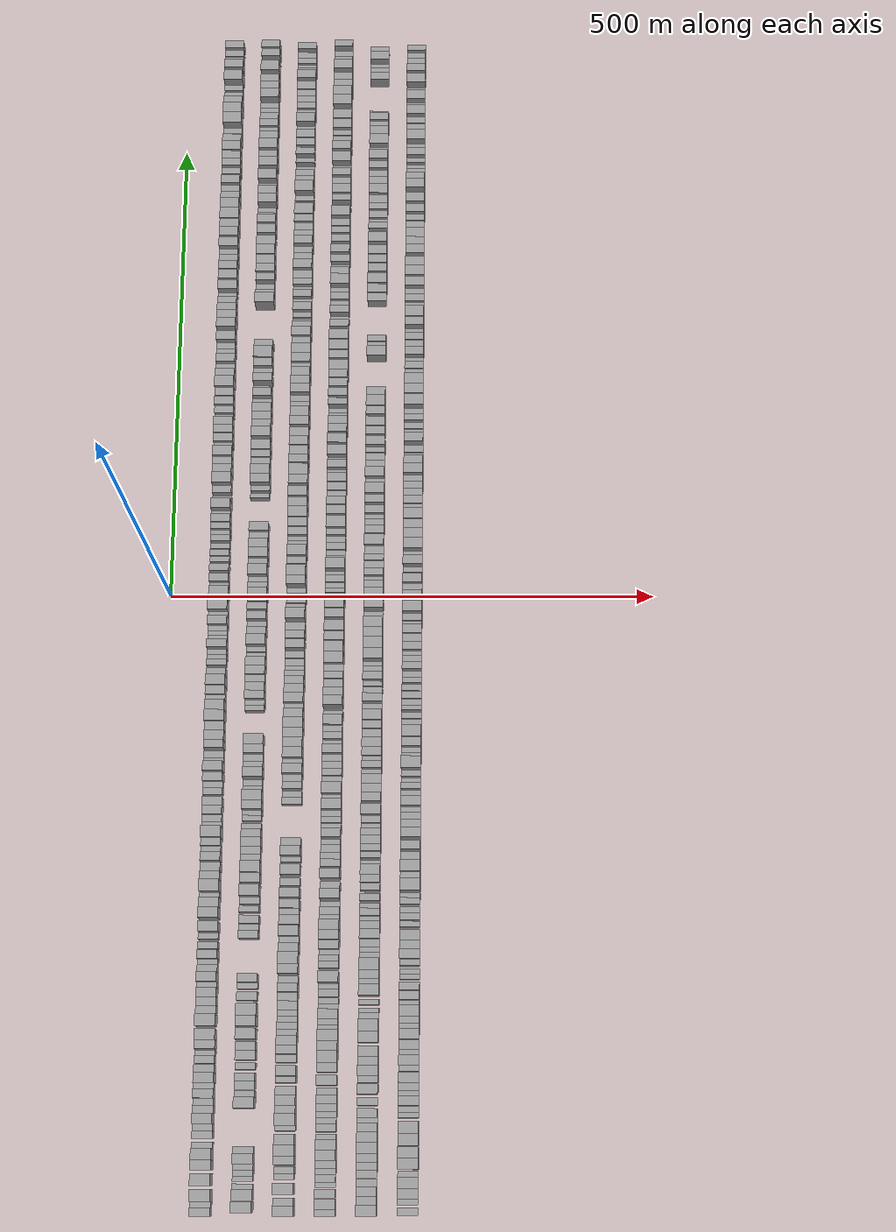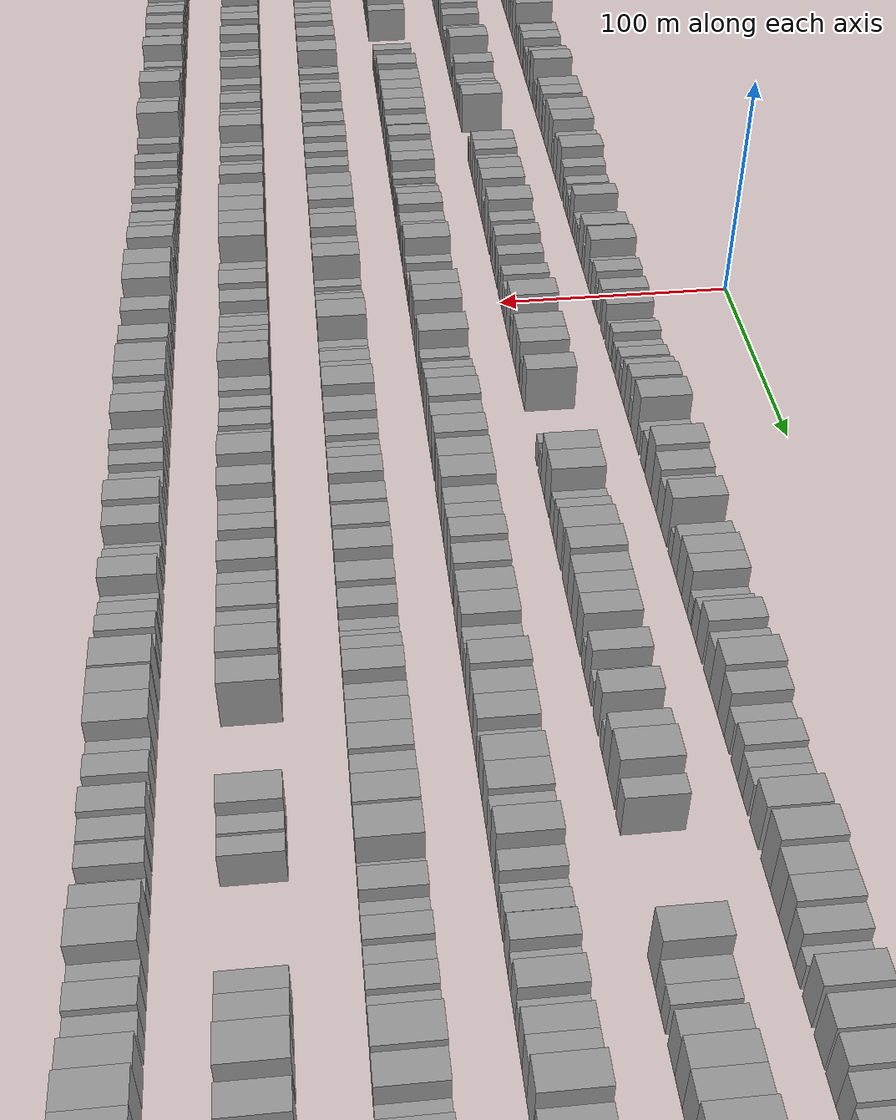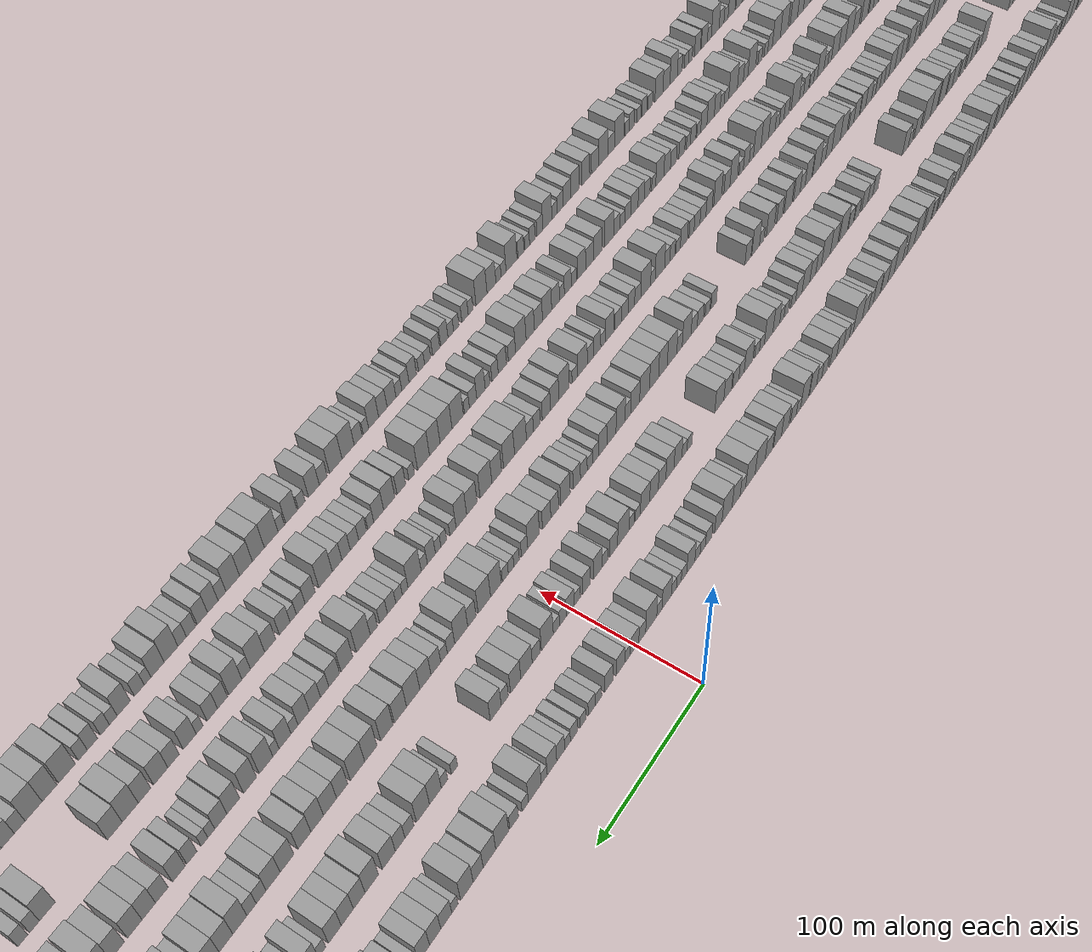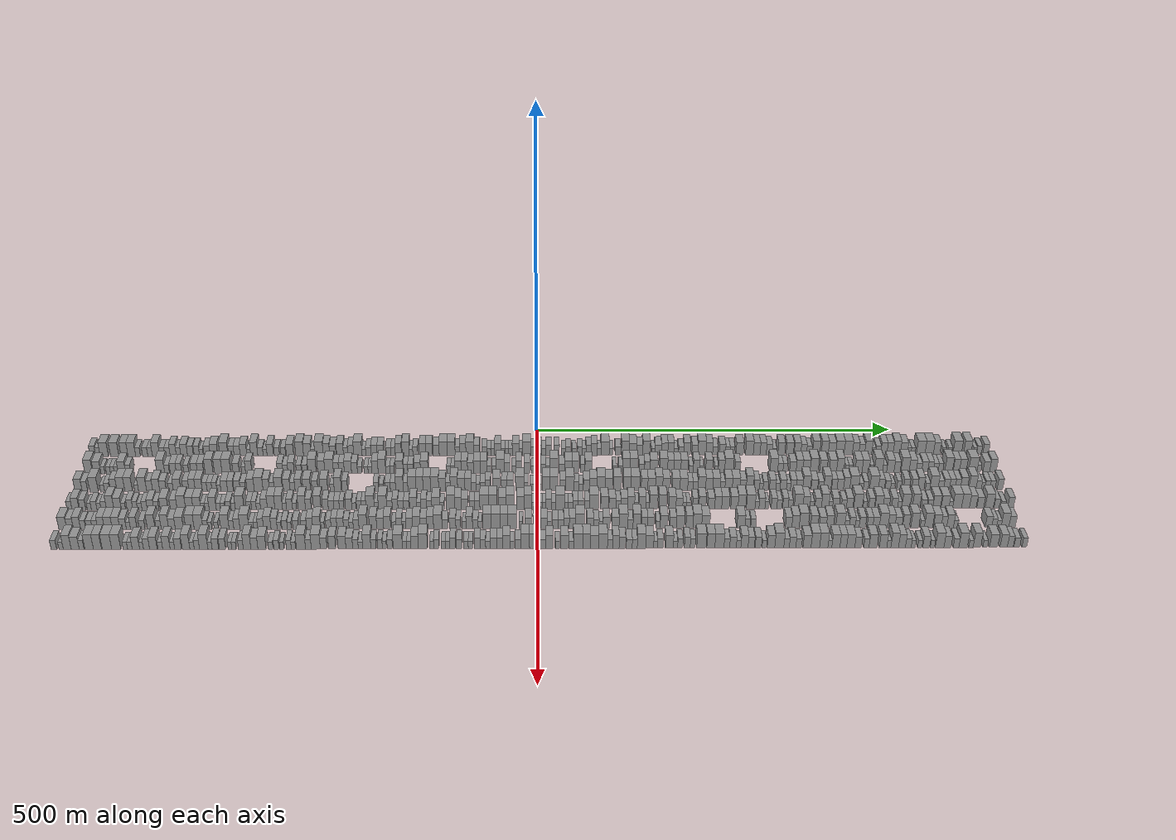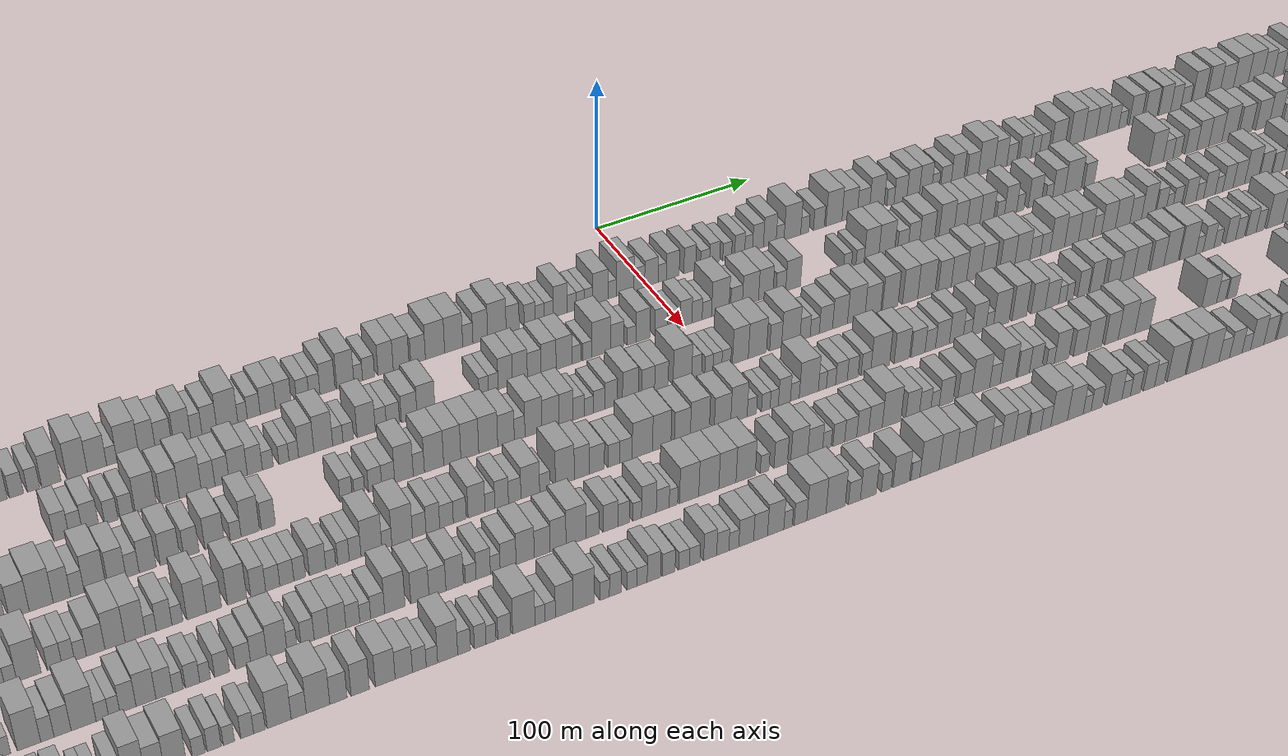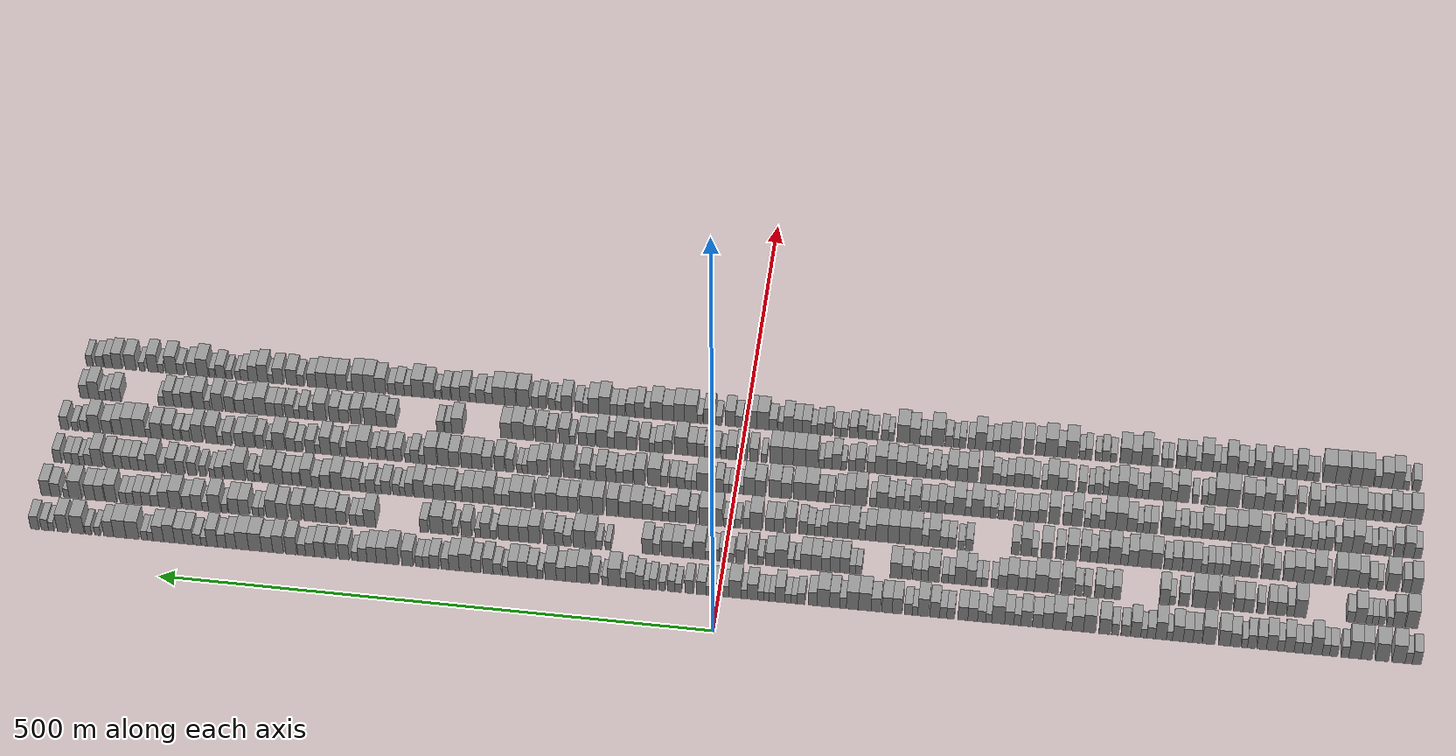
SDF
<sdf version="1.6">
 <world name="default">
  <scene>
   <sky><clouds><speed>12</speed></clouds></sky>
   <ambient>0.4 0.4 0.4 1</ambient>
   <background>0.7 0.7 0.7 1</background>
   <shadows>1</shadows>
  </scene>
  <gravity>0 0 -9.8066</gravity>
  <magnetic_field>6e-06 2.3e-05 -4.2e-05</magnetic_field>
  <physics default="0" name="default_physics" type="ode">
   <ode>
    <solver>
     <type>quick</type>
     <iters>10</iters>
     <sor>1.0</sor>
     <use_dynamic_moi_rescaling>0</use_dynamic_moi_rescaling>
    </solver>
    <constraints>
     <cfm>0</cfm>
     <erp>0.2</erp>
     <contact_max_correcting_vel>100</contact_max_correcting_vel>
     <contact_surface_layer>0.001</contact_surface_layer>
    </constraints>
   </ode>
   <max_step_size>0.004</max_step_size>
   <real_time_factor>1</real_time_factor>
   <real_time_update_rate>250</real_time_update_rate>
  </physics>
  <light name="sun" type="directional">
   <pose>0 0 10 0 0 0</pose>
   <diffuse>0.8 0.8 0.8 1</diffuse>
   <specular>0.2 0.2 0.2 1</specular>
   <attenuation>
    <range>1000</range>
    <constant>0.9</constant>
    <linear>0.01</linear>
    <quadratic>0.001</quadratic>
   </attenuation>
   <direction>-0.5 0.1 -0.9</direction>
  </light>
  <model name="building_1">
   <static>1</static>
   <pose>50.0000 -616.1149 0 0.000000 0.000000 0.000000</pose>
   <link name="link">
    <pose>0 0 9.00 0 0 0</pose>
    <collision name="collision"><geometry><box><size>20.0000 7.7702 18.0000</size></box></geometry></collision>
    <visual name="visual">
     <cast_shadows>0</cast_shadows>
     <geometry><box><size>20.0000 7.7702 18.0000</size></box></geometry>
     <material>
      <script>
       <uri>model://grey_wall/materials/scripts</uri>
       <uri>model://grey_wall/materials/textures</uri>
       <name>vrc/grey_wall</name>
      </script>
     </material>
    </visual>
   </link>
  </model>
  <model name="building_2">
   <static>1</static>
   <pose>50.0000 -609.1644 0 0.000000 0.000000 0.000000</pose>
   <link name="link">
    <pose>0 0 7.50 0 0 0</pose>
    <collision name="collision"><geometry><box><size>20.0000 6.1308 15.0000</size></box></geometry></collision>
    <visual name="visual">
     <cast_shadows>0</cast_shadows>
     <geometry><box><size>20.0000 6.1308 15.0000</size></box></geometry>
     <material>
      <script>
       <uri>model://grey_wall/materials/scripts</uri>
       <uri>model://grey_wall/materials/textures</uri>
       <name>vrc/grey_wall</name>
      </script>
     </material>
    </visual>
   </link>
  </model>
  <model name="building_3">
   <static>1</static>
   <pose>50.0000 -600.3946 0 0.000000 0.000000 0.000000</pose>
   <link name="link">
    <pose>0 0 12.00 0 0 0</pose>
    <collision name="collision"><geometry><box><size>20.0000 11.4088 24.0000</size></box></geometry></collision>
    <visual name="visual">
     <cast_shadows>0</cast_shadows>
     <geometry><box><size>20.0000 11.4088 24.0000</size></box></geometry>
     <material>
      <script>
       <uri>model://grey_wall/materials/scripts</uri>
       <uri>model://grey_wall/materials/textures</uri>
       <name>vrc/grey_wall</name>
      </script>
     </material>
    </visual>
   </link>
  </model>
  <model name="building_4">
   <static>1</static>
   <pose>50.0000 -585.9319 0 0.000000 0.000000 0.000000</pose>
   <link name="link">
    <pose>0 0 12.00 0 0 0</pose>
    <collision name="collision"><geometry><box><size>20.0000 11.5164 24.0000</size></box></geometry></collision>
    <visual name="visual">
     <cast_shadows>0</cast_shadows>
     <geometry><box><size>20.0000 11.5164 24.0000</size></box></geometry>
     <material>
      <script>
       <uri>model://grey_wall/materials/scripts</uri>
       <uri>model://grey_wall/materials/textures</uri>
       <name>vrc/grey_wall</name>
      </script>
     </material>
    </visual>
   </link>
  </model>
  <model name="building_5">
   <static>1</static>
   <pose>50.0000 -572.3471 0 0.000000 0.000000 0.000000</pose>
   <link name="link">
    <pose>0 0 12.00 0 0 0</pose>
    <collision name="collision"><geometry><box><size>20.0000 9.6532 24.0000</size></box></geometry></collision>
    <visual name="visual">
     <cast_shadows>0</cast_shadows>
     <geometry><box><size>20.0000 9.6532 24.0000</size></box></geometry>
     <material>
      <script>
       <uri>model://grey_wall/materials/scripts</uri>
       <uri>model://grey_wall/materials/textures</uri>
       <name>vrc/grey_wall</name>
      </script>
     </material>
    </visual>
   </link>
  </model>
  <model name="building_6">
   <static>1</static>
   <pose>50.0000 -562.2004 0 0.000000 0.000000 0.000000</pose>
   <link name="link">
    <pose>0 0 12.00 0 0 0</pose>
    <collision name="collision"><geometry><box><size>20.0000 10.6402 24.0000</size></box></geometry></collision>
    <visual name="visual">
     <cast_shadows>0</cast_shadows>
     <geometry><box><size>20.0000 10.6402 24.0000</size></box></geometry>
     <material>
      <script>
       <uri>model://grey_wall/materials/scripts</uri>
       <uri>model://grey_wall/materials/textures</uri>
       <name>vrc/grey_wall</name>
      </script>
     </material>
    </visual>
   </link>
  </model>
  <model name="building_7">
   <static>1</static>
   <pose>50.0000 -553.5937 0 0.000000 0.000000 0.000000</pose>
   <link name="link">
    <pose>0 0 7.50 0 0 0</pose>
    <collision name="collision"><geometry><box><size>20.0000 6.5731 15.0000</size></box></geometry></collision>
    <visual name="visual">
     <cast_shadows>0</cast_shadows>
     <geometry><box><size>20.0000 6.5731 15.0000</size></box></geometry>
     <material>
      <script>
       <uri>model://grey_wall/materials/scripts</uri>
       <uri>model://grey_wall/materials/textures</uri>
       <name>vrc/grey_wall</name>
      </script>
     </material>
    </visual>
   </link>
  </model>
  <model name="building_8">
   <static>1</static>
   <pose>50.0000 -543.7101 0 0.000000 0.000000 0.000000</pose>
   <link name="link">
    <pose>0 0 7.50 0 0 0</pose>
    <collision name="collision"><geometry><box><size>20.0000 7.1941 15.0000</size></box></geometry></collision>
    <visual name="visual">
     <cast_shadows>0</cast_shadows>
     <geometry><box><size>20.0000 7.1941 15.0000</size></box></geometry>
     <material>
      <script>
       <uri>model://grey_wall/materials/scripts</uri>
       <uri>model://grey_wall/materials/textures</uri>
       <name>vrc/grey_wall</name>
      </script>
     </material>
    </visual>
   </link>
  </model>
  <model name="building_9">
   <static>1</static>
   <pose>50.0000 -536.8628 0 0.000000 0.000000 0.000000</pose>
   <link name="link">
    <pose>0 0 7.50 0 0 0</pose>
    <collision name="collision"><geometry><box><size>20.0000 6.5006 15.0000</size></box></geometry></collision>
    <visual name="visual">
     <cast_shadows>0</cast_shadows>
     <geometry><box><size>20.0000 6.5006 15.0000</size></box></geometry>
     <material>
      <script>
       <uri>model://grey_wall/materials/scripts</uri>
       <uri>model://grey_wall/materials/textures</uri>
       <name>vrc/grey_wall</name>
      </script>
     </material>
    </visual>
   </link>
  </model>
  <model name="building_10">
   <static>1</static>
   <pose>50.0000 -528.6027 0 0.000000 0.000000 0.000000</pose>
   <link name="link">
    <pose>0 0 12.00 0 0 0</pose>
    <collision name="collision"><geometry><box><size>20.0000 10.0195 24.0000</size></box></geometry></collision>
    <visual name="visual">
     <cast_shadows>0</cast_shadows>
     <geometry><box><size>20.0000 10.0195 24.0000</size></box></geometry>
     <material>
      <script>
       <uri>model://grey_wall/materials/scripts</uri>
       <uri>model://grey_wall/materials/textures</uri>
       <name>vrc/grey_wall</name>
      </script>
     </material>
    </visual>
   </link>
  </model>
  <model name="building_11">
   <static>1</static>
   <pose>50.0000 -519.9171 0 0.000000 0.000000 0.000000</pose>
   <link name="link">
    <pose>0 0 7.50 0 0 0</pose>
    <collision name="collision"><geometry><box><size>20.0000 7.3516 15.0000</size></box></geometry></collision>
    <visual name="visual">
     <cast_shadows>0</cast_shadows>
     <geometry><box><size>20.0000 7.3516 15.0000</size></box></geometry>
     <material>
      <script>
       <uri>model://grey_wall/materials/scripts</uri>
       <uri>model://grey_wall/materials/textures</uri>
       <name>vrc/grey_wall</name>
      </script>
     </material>
    </visual>
   </link>
  </model>
  <model name="building_12">
   <static>1</static>
   <pose>50.0000 -512.6618 0 0.000000 0.000000 0.000000</pose>
   <link name="link">
    <pose>0 0 7.50 0 0 0</pose>
    <collision name="collision"><geometry><box><size>20.0000 7.1590 15.0000</size></box></geometry></collision>
    <visual name="visual">
     <cast_shadows>0</cast_shadows>
     <geometry><box><size>20.0000 7.1590 15.0000</size></box></geometry>
     <material>
      <script>
       <uri>model://grey_wall/materials/scripts</uri>
       <uri>model://grey_wall/materials/textures</uri>
       <name>vrc/grey_wall</name>
      </script>
     </material>
    </visual>
   </link>
  </model>
  <model name="building_13">
   <static>1</static>
   <pose>50.0000 -504.8235 0 0.000000 0.000000 0.000000</pose>
   <link name="link">
    <pose>0 0 10.50 0 0 0</pose>
    <collision name="collision"><geometry><box><size>20.0000 8.5176 21.0000</size></box></geometry></collision>
    <visual name="visual">
     <cast_shadows>0</cast_shadows>
     <geometry><box><size>20.0000 8.5176 21.0000</size></box></geometry>
     <material>
      <script>
       <uri>model://grey_wall/materials/scripts</uri>
       <uri>model://grey_wall/materials/textures</uri>
       <name>vrc/grey_wall</name>
      </script>
     </material>
    </visual>
   </link>
  </model>
  <model name="building_14">
   <static>1</static>
   <pose>50.0000 -497.3733 0 0.000000 0.000000 0.000000</pose>
   <link name="link">
    <pose>0 0 7.50 0 0 0</pose>
    <collision name="collision"><geometry><box><size>20.0000 6.3828 15.0000</size></box></geometry></collision>
    <visual name="visual">
     <cast_shadows>0</cast_shadows>
     <geometry><box><size>20.0000 6.3828 15.0000</size></box></geometry>
     <material>
      <script>
       <uri>model://grey_wall/materials/scripts</uri>
       <uri>model://grey_wall/materials/textures</uri>
       <name>vrc/grey_wall</name>
      </script>
     </material>
    </visual>
   </link>
  </model>
  <model name="building_15">
   <static>1</static>
   <pose>50.0000 -489.5475 0 0.000000 0.000000 0.000000</pose>
   <link name="link">
    <pose>0 0 10.50 0 0 0</pose>
    <collision name="collision"><geometry><box><size>20.0000 9.2689 21.0000</size></box></geometry></collision>
    <visual name="visual">
     <cast_shadows>0</cast_shadows>
     <geometry><box><size>20.0000 9.2689 21.0000</size></box></geometry>
     <material>
      <script>
       <uri>model://grey_wall/materials/scripts</uri>
       <uri>model://grey_wall/materials/textures</uri>
       <name>vrc/grey_wall</name>
      </script>
     </material>
    </visual>
   </link>
  </model>
  <model name="building_16">
   <static>1</static>
   <pose>50.0000 -480.7981 0 0.000000 0.000000 0.000000</pose>
   <link name="link">
    <pose>0 0 9.00 0 0 0</pose>
    <collision name="collision"><geometry><box><size>20.0000 8.2298 18.0000</size></box></geometry></collision>
    <visual name="visual">
     <cast_shadows>0</cast_shadows>
     <geometry><box><size>20.0000 8.2298 18.0000</size></box></geometry>
     <material>
      <script>
       <uri>model://grey_wall/materials/scripts</uri>
       <uri>model://grey_wall/materials/textures</uri>
       <name>vrc/grey_wall</name>
      </script>
     </material>
    </visual>
   </link>
  </model>
  <model name="building_17">
   <static>1</static>
   <pose>50.0000 -471.9992 0 0.000000 0.000000 0.000000</pose>
   <link name="link">
    <pose>0 0 9.00 0 0 0</pose>
    <collision name="collision"><geometry><box><size>20.0000 7.3680 18.0000</size></box></geometry></collision>
    <visual name="visual">
     <cast_shadows>0</cast_shadows>
     <geometry><box><size>20.0000 7.3680 18.0000</size></box></geometry>
     <material>
      <script>
       <uri>model://grey_wall/materials/scripts</uri>
       <uri>model://grey_wall/materials/textures</uri>
       <name>vrc/grey_wall</name>
      </script>
     </material>
    </visual>
   </link>
  </model>
  <model name="building_18">
   <static>1</static>
   <pose>50.0000 -465.6649 0 0.000000 0.000000 0.000000</pose>
   <link name="link">
    <pose>0 0 6.00 0 0 0</pose>
    <collision name="collision"><geometry><box><size>20.0000 5.3005 12.0000</size></box></geometry></collision>
    <visual name="visual">
     <cast_shadows>0</cast_shadows>
     <geometry><box><size>20.0000 5.3005 12.0000</size></box></geometry>
     <material>
      <script>
       <uri>model://grey_wall/materials/scripts</uri>
       <uri>model://grey_wall/materials/textures</uri>
       <name>vrc/grey_wall</name>
      </script>
     </material>
    </visual>
   </link>
  </model>
  <model name="building_19">
   <static>1</static>
   <pose>50.0000 -457.6492 0 0.000000 0.000000 0.000000</pose>
   <link name="link">
    <pose>0 0 9.00 0 0 0</pose>
    <collision name="collision"><geometry><box><size>20.0000 8.7309 18.0000</size></box></geometry></collision>
    <visual name="visual">
     <cast_shadows>0</cast_shadows>
     <geometry><box><size>20.0000 8.7309 18.0000</size></box></geometry>
     <material>
      <script>
       <uri>model://grey_wall/materials/scripts</uri>
       <uri>model://grey_wall/materials/textures</uri>
       <name>vrc/grey_wall</name>
      </script>
     </material>
    </visual>
   </link>
  </model>
  <model name="building_20">
   <static>1</static>
   <pose>50.0000 -448.1120 0 0.000000 0.000000 0.000000</pose>
   <link name="link">
    <pose>0 0 10.50 0 0 0</pose>
    <collision name="collision"><geometry><box><size>20.0000 10.3435 21.0000</size></box></geometry></collision>
    <visual name="visual">
     <cast_shadows>0</cast_shadows>
     <geometry><box><size>20.0000 10.3435 21.0000</size></box></geometry>
     <material>
      <script>
       <uri>model://grey_wall/materials/scripts</uri>
       <uri>model://grey_wall/materials/textures</uri>
       <name>vrc/grey_wall</name>
      </script>
     </material>
    </visual>
   </link>
  </model>
  <model name="building_21">
   <static>1</static>
   <pose>50.0000 -434.3321 0 0.000000 0.000000 0.000000</pose>
   <link name="link">
    <pose>0 0 12.00 0 0 0</pose>
    <collision name="collision"><geometry><box><size>20.0000 11.2164 24.0000</size></box></geometry></collision>
    <visual name="visual">
     <cast_shadows>0</cast_shadows>
     <geometry><box><size>20.0000 11.2164 24.0000</size></box></geometry>
     <material>
      <script>
       <uri>model://grey_wall/materials/scripts</uri>
       <uri>model://grey_wall/materials/textures</uri>
       <name>vrc/grey_wall</name>
      </script>
     </material>
    </visual>
   </link>
  </model>
  <model name="building_22">
   <static>1</static>
   <pose>50.0000 -424.0451 0 0.000000 0.000000 0.000000</pose>
   <link name="link">
    <pose>0 0 9.00 0 0 0</pose>
    <collision name="collision"><geometry><box><size>20.0000 7.3576 18.0000</size></box></geometry></collision>
    <visual name="visual">
     <cast_shadows>0</cast_shadows>
     <geometry><box><size>20.0000 7.3576 18.0000</size></box></geometry>
     <material>
      <script>
       <uri>model://grey_wall/materials/scripts</uri>
       <uri>model://grey_wall/materials/textures</uri>
       <name>vrc/grey_wall</name>
      </script>
     </material>
    </visual>
   </link>
  </model>
  <model name="building_23">
   <static>1</static>
   <pose>50.0000 -416.1406 0 0.000000 0.000000 0.000000</pose>
   <link name="link">
    <pose>0 0 9.00 0 0 0</pose>
    <collision name="collision"><geometry><box><size>20.0000 8.4513 18.0000</size></box></geometry></collision>
    <visual name="visual">
     <cast_shadows>0</cast_shadows>
     <geometry><box><size>20.0000 8.4513 18.0000</size></box></geometry>
     <material>
      <script>
       <uri>model://grey_wall/materials/scripts</uri>
       <uri>model://grey_wall/materials/textures</uri>
       <name>vrc/grey_wall</name>
      </script>
     </material>
    </visual>
   </link>
  </model>
  <model name="building_24">
   <static>1</static>
   <pose>50.0000 -407.2090 0 0.000000 0.000000 0.000000</pose>
   <link name="link">
    <pose>0 0 10.50 0 0 0</pose>
    <collision name="collision"><geometry><box><size>20.0000 9.4120 21.0000</size></box></geometry></collision>
    <visual name="visual">
     <cast_shadows>0</cast_shadows>
     <geometry><box><size>20.0000 9.4120 21.0000</size></box></geometry>
     <material>
      <script>
       <uri>model://grey_wall/materials/scripts</uri>
       <uri>model://grey_wall/materials/textures</uri>
       <name>vrc/grey_wall</name>
      </script>
     </material>
    </visual>
   </link>
  </model>
  <model name="building_25">
   <static>1</static>
   <pose>50.0000 -399.8669 0 0.000000 0.000000 0.000000</pose>
   <link name="link">
    <pose>0 0 6.00 0 0 0</pose>
    <collision name="collision"><geometry><box><size>20.0000 5.2722 12.0000</size></box></geometry></collision>
    <visual name="visual">
     <cast_shadows>0</cast_shadows>
     <geometry><box><size>20.0000 5.2722 12.0000</size></box></geometry>
     <material>
      <script>
       <uri>model://grey_wall/materials/scripts</uri>
       <uri>model://grey_wall/materials/textures</uri>
       <name>vrc/grey_wall</name>
      </script>
     </material>
    </visual>
   </link>
  </model>
  <model name="building_26">
   <static>1</static>
   <pose>50.0000 -392.3706 0 0.000000 0.000000 0.000000</pose>
   <link name="link">
    <pose>0 0 12.00 0 0 0</pose>
    <collision name="collision"><geometry><box><size>20.0000 9.7205 24.0000</size></box></geometry></collision>
    <visual name="visual">
     <cast_shadows>0</cast_shadows>
     <geometry><box><size>20.0000 9.7205 24.0000</size></box></geometry>
     <material>
      <script>
       <uri>model://grey_wall/materials/scripts</uri>
       <uri>model://grey_wall/materials/textures</uri>
       <name>vrc/grey_wall</name>
      </script>
     </material>
    </visual>
   </link>
  </model>
  <model name="building_27">
   <static>1</static>
   <pose>50.0000 -383.7733 0 0.000000 0.000000 0.000000</pose>
   <link name="link">
    <pose>0 0 7.50 0 0 0</pose>
    <collision name="collision"><geometry><box><size>20.0000 7.4741 15.0000</size></box></geometry></collision>
    <visual name="visual">
     <cast_shadows>0</cast_shadows>
     <geometry><box><size>20.0000 7.4741 15.0000</size></box></geometry>
     <material>
      <script>
       <uri>model://grey_wall/materials/scripts</uri>
       <uri>model://grey_wall/materials/textures</uri>
       <name>vrc/grey_wall</name>
      </script>
     </material>
    </visual>
   </link>
  </model>
  <model name="building_28">
   <static>1</static>
   <pose>50.0000 -377.3283 0 0.000000 0.000000 0.000000</pose>
   <link name="link">
    <pose>0 0 6.00 0 0 0</pose>
    <collision name="collision"><geometry><box><size>20.0000 5.4159 12.0000</size></box></geometry></collision>
    <visual name="visual">
     <cast_shadows>0</cast_shadows>
     <geometry><box><size>20.0000 5.4159 12.0000</size></box></geometry>
     <material>
      <script>
       <uri>model://grey_wall/materials/scripts</uri>
       <uri>model://grey_wall/materials/textures</uri>
       <name>vrc/grey_wall</name>
      </script>
     </material>
    </visual>
   </link>
  </model>
  <model name="building_29">
   <static>1</static>
   <pose>50.0000 -370.1211 0 0.000000 0.000000 0.000000</pose>
   <link name="link">
    <pose>0 0 10.50 0 0 0</pose>
    <collision name="collision"><geometry><box><size>20.0000 8.9987 21.0000</size></box></geometry></collision>
    <visual name="visual">
     <cast_shadows>0</cast_shadows>
     <geometry><box><size>20.0000 8.9987 21.0000</size></box></geometry>
     <material>
      <script>
       <uri>model://grey_wall/materials/scripts</uri>
       <uri>model://grey_wall/materials/textures</uri>
       <name>vrc/grey_wall</name>
      </script>
     </material>
    </visual>
   </link>
  </model>
  <model name="building_30">
   <static>1</static>
   <pose>50.0000 -360.9639 0 0.000000 0.000000 0.000000</pose>
   <link name="link">
    <pose>0 0 7.50 0 0 0</pose>
    <collision name="collision"><geometry><box><size>20.0000 7.3156 15.0000</size></box></geometry></collision>
    <visual name="visual">
     <cast_shadows>0</cast_shadows>
     <geometry><box><size>20.0000 7.3156 15.0000</size></box></geometry>
     <material>
      <script>
       <uri>model://grey_wall/materials/scripts</uri>
       <uri>model://grey_wall/materials/textures</uri>
       <name>vrc/grey_wall</name>
      </script>
     </material>
    </visual>
   </link>
  </model>
  <model name="building_31">
   <static>1</static>
   <pose>50.0000 -352.1013 0 0.000000 0.000000 0.000000</pose>
   <link name="link">
    <pose>0 0 7.50 0 0 0</pose>
    <collision name="collision"><geometry><box><size>20.0000 6.4097 15.0000</size></box></geometry></collision>
    <visual name="visual">
     <cast_shadows>0</cast_shadows>
     <geometry><box><size>20.0000 6.4097 15.0000</size></box></geometry>
     <material>
      <script>
       <uri>model://grey_wall/materials/scripts</uri>
       <uri>model://grey_wall/materials/textures</uri>
       <name>vrc/grey_wall</name>
      </script>
     </material>
    </visual>
   </link>
  </model>
  <model name="building_32">
   <static>1</static>
   <pose>50.0000 -342.8801 0 0.000000 0.000000 0.000000</pose>
   <link name="link">
    <pose>0 0 10.50 0 0 0</pose>
    <collision name="collision"><geometry><box><size>20.0000 10.0327 21.0000</size></box></geometry></collision>
    <visual name="visual">
     <cast_shadows>0</cast_shadows>
     <geometry><box><size>20.0000 10.0327 21.0000</size></box></geometry>
     <material>
      <script>
       <uri>model://grey_wall/materials/scripts</uri>
       <uri>model://grey_wall/materials/textures</uri>
       <name>vrc/grey_wall</name>
      </script>
     </material>
    </visual>
   </link>
  </model>
  <model name="building_33">
   <static>1</static>
   <pose>50.0000 -329.4867 0 0.000000 0.000000 0.000000</pose>
   <link name="link">
    <pose>0 0 12.00 0 0 0</pose>
    <collision name="collision"><geometry><box><size>20.0000 10.7541 24.0000</size></box></geometry></collision>
    <visual name="visual">
     <cast_shadows>0</cast_shadows>
     <geometry><box><size>20.0000 10.7541 24.0000</size></box></geometry>
     <material>
      <script>
       <uri>model://grey_wall/materials/scripts</uri>
       <uri>model://grey_wall/materials/textures</uri>
       <name>vrc/grey_wall</name>
      </script>
     </material>
    </visual>
   </link>
  </model>
  <model name="building_34">
   <static>1</static>
   <pose>50.0000 -318.9630 0 0.000000 0.000000 0.000000</pose>
   <link name="link">
    <pose>0 0 10.50 0 0 0</pose>
    <collision name="collision"><geometry><box><size>20.0000 10.2934 21.0000</size></box></geometry></collision>
    <visual name="visual">
     <cast_shadows>0</cast_shadows>
     <geometry><box><size>20.0000 10.2934 21.0000</size></box></geometry>
     <material>
      <script>
       <uri>model://grey_wall/materials/scripts</uri>
       <uri>model://grey_wall/materials/textures</uri>
       <name>vrc/grey_wall</name>
      </script>
     </material>
    </visual>
   </link>
  </model>
  <model name="building_35">
   <static>1</static>
   <pose>50.0000 -311.0700 0 0.000000 0.000000 0.000000</pose>
   <link name="link">
    <pose>0 0 6.00 0 0 0</pose>
    <collision name="collision"><geometry><box><size>20.0000 5.4926 12.0000</size></box></geometry></collision>
    <visual name="visual">
     <cast_shadows>0</cast_shadows>
     <geometry><box><size>20.0000 5.4926 12.0000</size></box></geometry>
     <material>
      <script>
       <uri>model://grey_wall/materials/scripts</uri>
       <uri>model://grey_wall/materials/textures</uri>
       <name>vrc/grey_wall</name>
      </script>
     </material>
    </visual>
   </link>
  </model>
  <model name="building_36">
   <static>1</static>
   <pose>50.0000 -302.5009 0 0.000000 0.000000 0.000000</pose>
   <link name="link">
    <pose>0 0 12.00 0 0 0</pose>
    <collision name="collision"><geometry><box><size>20.0000 11.6454 24.0000</size></box></geometry></collision>
    <visual name="visual">
     <cast_shadows>0</cast_shadows>
     <geometry><box><size>20.0000 11.6454 24.0000</size></box></geometry>
     <material>
      <script>
       <uri>model://grey_wall/materials/scripts</uri>
       <uri>model://grey_wall/materials/textures</uri>
       <name>vrc/grey_wall</name>
      </script>
     </material>
    </visual>
   </link>
  </model>
  <model name="building_37">
   <static>1</static>
   <pose>50.0000 -292.2580 0 0.000000 0.000000 0.000000</pose>
   <link name="link">
    <pose>0 0 10.50 0 0 0</pose>
    <collision name="collision"><geometry><box><size>20.0000 8.8404 21.0000</size></box></geometry></collision>
    <visual name="visual">
     <cast_shadows>0</cast_shadows>
     <geometry><box><size>20.0000 8.8404 21.0000</size></box></geometry>
     <material>
      <script>
       <uri>model://grey_wall/materials/scripts</uri>
       <uri>model://grey_wall/materials/textures</uri>
       <name>vrc/grey_wall</name>
      </script>
     </material>
    </visual>
   </link>
  </model>
  <model name="building_38">
   <static>1</static>
   <pose>50.0000 -283.4087 0 0.000000 0.000000 0.000000</pose>
   <link name="link">
    <pose>0 0 9.00 0 0 0</pose>
    <collision name="collision"><geometry><box><size>20.0000 8.8582 18.0000</size></box></geometry></collision>
    <visual name="visual">
     <cast_shadows>0</cast_shadows>
     <geometry><box><size>20.0000 8.8582 18.0000</size></box></geometry>
     <material>
      <script>
       <uri>model://grey_wall/materials/scripts</uri>
       <uri>model://grey_wall/materials/textures</uri>
       <name>vrc/grey_wall</name>
      </script>
     </material>
    </visual>
   </link>
  </model>
  <model name="building_39">
   <static>1</static>
   <pose>50.0000 -273.3589 0 0.000000 0.000000 0.000000</pose>
   <link name="link">
    <pose>0 0 10.50 0 0 0</pose>
    <collision name="collision"><geometry><box><size>20.0000 9.2415 21.0000</size></box></geometry></collision>
    <visual name="visual">
     <cast_shadows>0</cast_shadows>
     <geometry><box><size>20.0000 9.2415 21.0000</size></box></geometry>
     <material>
      <script>
       <uri>model://grey_wall/materials/scripts</uri>
       <uri>model://grey_wall/materials/textures</uri>
       <name>vrc/grey_wall</name>
      </script>
     </material>
    </visual>
   </link>
  </model>
  <model name="building_40">
   <static>1</static>
   <pose>50.0000 -265.6720 0 0.000000 0.000000 0.000000</pose>
   <link name="link">
    <pose>0 0 7.50 0 0 0</pose>
    <collision name="collision"><geometry><box><size>20.0000 6.1321 15.0000</size></box></geometry></collision>
    <visual name="visual">
     <cast_shadows>0</cast_shadows>
     <geometry><box><size>20.0000 6.1321 15.0000</size></box></geometry>
     <material>
      <script>
       <uri>model://grey_wall/materials/scripts</uri>
       <uri>model://grey_wall/materials/textures</uri>
       <name>vrc/grey_wall</name>
      </script>
     </material>
    </visual>
   </link>
  </model>
  <model name="building_41">
   <static>1</static>
   <pose>50.0000 -258.5333 0 0.000000 0.000000 0.000000</pose>
   <link name="link">
    <pose>0 0 9.00 0 0 0</pose>
    <collision name="collision"><geometry><box><size>20.0000 8.1453 18.0000</size></box></geometry></collision>
    <visual name="visual">
     <cast_shadows>0</cast_shadows>
     <geometry><box><size>20.0000 8.1453 18.0000</size></box></geometry>
     <material>
      <script>
       <uri>model://grey_wall/materials/scripts</uri>
       <uri>model://grey_wall/materials/textures</uri>
       <name>vrc/grey_wall</name>
      </script>
     </material>
    </visual>
   </link>
  </model>
  <model name="building_42">
   <static>1</static>
   <pose>50.0000 -248.6864 0 0.000000 0.000000 0.000000</pose>
   <link name="link">
    <pose>0 0 12.00 0 0 0</pose>
    <collision name="collision"><geometry><box><size>20.0000 11.5486 24.0000</size></box></geometry></collision>
    <visual name="visual">
     <cast_shadows>0</cast_shadows>
     <geometry><box><size>20.0000 11.5486 24.0000</size></box></geometry>
     <material>
      <script>
       <uri>model://grey_wall/materials/scripts</uri>
       <uri>model://grey_wall/materials/textures</uri>
       <name>vrc/grey_wall</name>
      </script>
     </material>
    </visual>
   </link>
  </model>
  <model name="building_43">
   <static>1</static>
   <pose>50.0000 -240.2918 0 0.000000 0.000000 0.000000</pose>
   <link name="link">
    <pose>0 0 6.00 0 0 0</pose>
    <collision name="collision"><geometry><box><size>20.0000 5.2406 12.0000</size></box></geometry></collision>
    <visual name="visual">
     <cast_shadows>0</cast_shadows>
     <geometry><box><size>20.0000 5.2406 12.0000</size></box></geometry>
     <material>
      <script>
       <uri>model://grey_wall/materials/scripts</uri>
       <uri>model://grey_wall/materials/textures</uri>
       <name>vrc/grey_wall</name>
      </script>
     </material>
    </visual>
   </link>
  </model>
  <model name="building_44">
   <static>1</static>
   <pose>50.0000 -234.0662 0 0.000000 0.000000 0.000000</pose>
   <link name="link">
    <pose>0 0 7.50 0 0 0</pose>
    <collision name="collision"><geometry><box><size>20.0000 7.2105 15.0000</size></box></geometry></collision>
    <visual name="visual">
     <cast_shadows>0</cast_shadows>
     <geometry><box><size>20.0000 7.2105 15.0000</size></box></geometry>
     <material>
      <script>
       <uri>model://grey_wall/materials/scripts</uri>
       <uri>model://grey_wall/materials/textures</uri>
       <name>vrc/grey_wall</name>
      </script>
     </material>
    </visual>
   </link>
  </model>
  <model name="building_45">
   <static>1</static>
   <pose>50.0000 -226.1549 0 0.000000 0.000000 0.000000</pose>
   <link name="link">
    <pose>0 0 9.00 0 0 0</pose>
    <collision name="collision"><geometry><box><size>20.0000 8.6121 18.0000</size></box></geometry></collision>
    <visual name="visual">
     <cast_shadows>0</cast_shadows>
     <geometry><box><size>20.0000 8.6121 18.0000</size></box></geometry>
     <material>
      <script>
       <uri>model://grey_wall/materials/scripts</uri>
       <uri>model://grey_wall/materials/textures</uri>
       <name>vrc/grey_wall</name>
      </script>
     </material>
    </visual>
   </link>
  </model>
  <model name="building_46">
   <static>1</static>
   <pose>50.0000 -217.4307 0 0.000000 0.000000 0.000000</pose>
   <link name="link">
    <pose>0 0 9.00 0 0 0</pose>
    <collision name="collision"><geometry><box><size>20.0000 8.8363 18.0000</size></box></geometry></collision>
    <visual name="visual">
     <cast_shadows>0</cast_shadows>
     <geometry><box><size>20.0000 8.8363 18.0000</size></box></geometry>
     <material>
      <script>
       <uri>model://grey_wall/materials/scripts</uri>
       <uri>model://grey_wall/materials/textures</uri>
       <name>vrc/grey_wall</name>
      </script>
     </material>
    </visual>
   </link>
  </model>
  <model name="building_47">
   <static>1</static>
   <pose>50.0000 -206.5322 0 0.000000 0.000000 0.000000</pose>
   <link name="link">
    <pose>0 0 7.50 0 0 0</pose>
    <collision name="collision"><geometry><box><size>20.0000 6.9607 15.0000</size></box></geometry></collision>
    <visual name="visual">
     <cast_shadows>0</cast_shadows>
     <geometry><box><size>20.0000 6.9607 15.0000</size></box></geometry>
     <material>
      <script>
       <uri>model://grey_wall/materials/scripts</uri>
       <uri>model://grey_wall/materials/textures</uri>
       <name>vrc/grey_wall</name>
      </script>
     </material>
    </visual>
   </link>
  </model>
  <model name="building_48">
   <static>1</static>
   <pose>50.0000 -199.9410 0 0.000000 0.000000 0.000000</pose>
   <link name="link">
    <pose>0 0 7.50 0 0 0</pose>
    <collision name="collision"><geometry><box><size>20.0000 6.2218 15.0000</size></box></geometry></collision>
    <visual name="visual">
     <cast_shadows>0</cast_shadows>
     <geometry><box><size>20.0000 6.2218 15.0000</size></box></geometry>
     <material>
      <script>
       <uri>model://grey_wall/materials/scripts</uri>
       <uri>model://grey_wall/materials/textures</uri>
       <name>vrc/grey_wall</name>
      </script>
     </material>
    </visual>
   </link>
  </model>
  <model name="building_49">
   <static>1</static>
   <pose>50.0000 -192.5320 0 0.000000 0.000000 0.000000</pose>
   <link name="link">
    <pose>0 0 10.50 0 0 0</pose>
    <collision name="collision"><geometry><box><size>20.0000 8.5962 21.0000</size></box></geometry></collision>
    <visual name="visual">
     <cast_shadows>0</cast_shadows>
     <geometry><box><size>20.0000 8.5962 21.0000</size></box></geometry>
     <material>
      <script>
       <uri>model://grey_wall/materials/scripts</uri>
       <uri>model://grey_wall/materials/textures</uri>
       <name>vrc/grey_wall</name>
      </script>
     </material>
    </visual>
   </link>
  </model>
  <model name="building_50">
   <static>1</static>
   <pose>50.0000 -182.3297 0 0.000000 0.000000 0.000000</pose>
   <link name="link">
    <pose>0 0 12.00 0 0 0</pose>
    <collision name="collision"><geometry><box><size>20.0000 9.8085 24.0000</size></box></geometry></collision>
    <visual name="visual">
     <cast_shadows>0</cast_shadows>
     <geometry><box><size>20.0000 9.8085 24.0000</size></box></geometry>
     <material>
      <script>
       <uri>model://grey_wall/materials/scripts</uri>
       <uri>model://grey_wall/materials/textures</uri>
       <name>vrc/grey_wall</name>
      </script>
     </material>
    </visual>
   </link>
  </model>
  <model name="building_51">
   <static>1</static>
   <pose>50.0000 -174.9317 0 0.000000 0.000000 0.000000</pose>
   <link name="link">
    <pose>0 0 6.00 0 0 0</pose>
    <collision name="collision"><geometry><box><size>20.0000 4.9875 12.0000</size></box></geometry></collision>
    <visual name="visual">
     <cast_shadows>0</cast_shadows>
     <geometry><box><size>20.0000 4.9875 12.0000</size></box></geometry>
     <material>
      <script>
       <uri>model://grey_wall/materials/scripts</uri>
       <uri>model://grey_wall/materials/textures</uri>
       <name>vrc/grey_wall</name>
      </script>
     </material>
    </visual>
   </link>
  </model>
  <model name="building_52">
   <static>1</static>
   <pose>50.0000 -168.9902 0 0.000000 0.000000 0.000000</pose>
   <link name="link">
    <pose>0 0 7.50 0 0 0</pose>
    <collision name="collision"><geometry><box><size>20.0000 6.8953 15.0000</size></box></geometry></collision>
    <visual name="visual">
     <cast_shadows>0</cast_shadows>
     <geometry><box><size>20.0000 6.8953 15.0000</size></box></geometry>
     <material>
      <script>
       <uri>model://grey_wall/materials/scripts</uri>
       <uri>model://grey_wall/materials/textures</uri>
       <name>vrc/grey_wall</name>
      </script>
     </material>
    </visual>
   </link>
  </model>
  <model name="building_53">
   <static>1</static>
   <pose>50.0000 -159.1283 0 0.000000 0.000000 0.000000</pose>
   <link name="link">
    <pose>0 0 10.50 0 0 0</pose>
    <collision name="collision"><geometry><box><size>20.0000 8.8286 21.0000</size></box></geometry></collision>
    <visual name="visual">
     <cast_shadows>0</cast_shadows>
     <geometry><box><size>20.0000 8.8286 21.0000</size></box></geometry>
     <material>
      <script>
       <uri>model://grey_wall/materials/scripts</uri>
       <uri>model://grey_wall/materials/textures</uri>
       <name>vrc/grey_wall</name>
      </script>
     </material>
    </visual>
   </link>
  </model>
  <model name="building_54">
   <static>1</static>
   <pose>50.0000 -150.0914 0 0.000000 0.000000 0.000000</pose>
   <link name="link">
    <pose>0 0 10.50 0 0 0</pose>
    <collision name="collision"><geometry><box><size>20.0000 9.2452 21.0000</size></box></geometry></collision>
    <visual name="visual">
     <cast_shadows>0</cast_shadows>
     <geometry><box><size>20.0000 9.2452 21.0000</size></box></geometry>
     <material>
      <script>
       <uri>model://grey_wall/materials/scripts</uri>
       <uri>model://grey_wall/materials/textures</uri>
       <name>vrc/grey_wall</name>
      </script>
     </material>
    </visual>
   </link>
  </model>
  <model name="building_55">
   <static>1</static>
   <pose>50.0000 -140.1754 0 0.000000 0.000000 0.000000</pose>
   <link name="link">
    <pose>0 0 9.00 0 0 0</pose>
    <collision name="collision"><geometry><box><size>20.0000 8.5867 18.0000</size></box></geometry></collision>
    <visual name="visual">
     <cast_shadows>0</cast_shadows>
     <geometry><box><size>20.0000 8.5867 18.0000</size></box></geometry>
     <material>
      <script>
       <uri>model://grey_wall/materials/scripts</uri>
       <uri>model://grey_wall/materials/textures</uri>
       <name>vrc/grey_wall</name>
      </script>
     </material>
    </visual>
   </link>
  </model>
  <model name="building_56">
   <static>1</static>
   <pose>50.0000 -130.2048 0 0.000000 0.000000 0.000000</pose>
   <link name="link">
    <pose>0 0 12.00 0 0 0</pose>
    <collision name="collision"><geometry><box><size>20.0000 11.3546 24.0000</size></box></geometry></collision>
    <visual name="visual">
     <cast_shadows>0</cast_shadows>
     <geometry><box><size>20.0000 11.3546 24.0000</size></box></geometry>
     <material>
      <script>
       <uri>model://grey_wall/materials/scripts</uri>
       <uri>model://grey_wall/materials/textures</uri>
       <name>vrc/grey_wall</name>
      </script>
     </material>
    </visual>
   </link>
  </model>
  <model name="building_57">
   <static>1</static>
   <pose>50.0000 -119.1630 0 0.000000 0.000000 0.000000</pose>
   <link name="link">
    <pose>0 0 12.00 0 0 0</pose>
    <collision name="collision"><geometry><box><size>20.0000 10.7291 24.0000</size></box></geometry></collision>
    <visual name="visual">
     <cast_shadows>0</cast_shadows>
     <geometry><box><size>20.0000 10.7291 24.0000</size></box></geometry>
     <material>
      <script>
       <uri>model://grey_wall/materials/scripts</uri>
       <uri>model://grey_wall/materials/textures</uri>
       <name>vrc/grey_wall</name>
      </script>
     </material>
    </visual>
   </link>
  </model>
  <model name="building_58">
   <static>1</static>
   <pose>50.0000 -110.7547 0 0.000000 0.000000 0.000000</pose>
   <link name="link">
    <pose>0 0 7.50 0 0 0</pose>
    <collision name="collision"><geometry><box><size>20.0000 6.0874 15.0000</size></box></geometry></collision>
    <visual name="visual">
     <cast_shadows>0</cast_shadows>
     <geometry><box><size>20.0000 6.0874 15.0000</size></box></geometry>
     <material>
      <script>
       <uri>model://grey_wall/materials/scripts</uri>
       <uri>model://grey_wall/materials/textures</uri>
       <name>vrc/grey_wall</name>
      </script>
     </material>
    </visual>
   </link>
  </model>
  <model name="building_59">
   <static>1</static>
   <pose>50.0000 -103.2702 0 0.000000 0.000000 0.000000</pose>
   <link name="link">
    <pose>0 0 10.50 0 0 0</pose>
    <collision name="collision"><geometry><box><size>20.0000 8.8816 21.0000</size></box></geometry></collision>
    <visual name="visual">
     <cast_shadows>0</cast_shadows>
     <geometry><box><size>20.0000 8.8816 21.0000</size></box></geometry>
     <material>
      <script>
       <uri>model://grey_wall/materials/scripts</uri>
       <uri>model://grey_wall/materials/textures</uri>
       <name>vrc/grey_wall</name>
      </script>
     </material>
    </visual>
   </link>
  </model>
  <model name="building_60">
   <static>1</static>
   <pose>50.0000 -93.2783 0 0.000000 0.000000 0.000000</pose>
   <link name="link">
    <pose>0 0 12.00 0 0 0</pose>
    <collision name="collision"><geometry><box><size>20.0000 11.1021 24.0000</size></box></geometry></collision>
    <visual name="visual">
     <cast_shadows>0</cast_shadows>
     <geometry><box><size>20.0000 11.1021 24.0000</size></box></geometry>
     <material>
      <script>
       <uri>model://grey_wall/materials/scripts</uri>
       <uri>model://grey_wall/materials/textures</uri>
       <name>vrc/grey_wall</name>
      </script>
     </material>
    </visual>
   </link>
  </model>
  <model name="building_61">
   <static>1</static>
   <pose>50.0000 -83.7595 0 0.000000 0.000000 0.000000</pose>
   <link name="link">
    <pose>0 0 9.00 0 0 0</pose>
    <collision name="collision"><geometry><box><size>20.0000 7.9356 18.0000</size></box></geometry></collision>
    <visual name="visual">
     <cast_shadows>0</cast_shadows>
     <geometry><box><size>20.0000 7.9356 18.0000</size></box></geometry>
     <material>
      <script>
       <uri>model://grey_wall/materials/scripts</uri>
       <uri>model://grey_wall/materials/textures</uri>
       <name>vrc/grey_wall</name>
      </script>
     </material>
    </visual>
   </link>
  </model>
  <model name="building_62">
   <static>1</static>
   <pose>50.0000 -73.3853 0 0.000000 0.000000 0.000000</pose>
   <link name="link">
    <pose>0 0 7.50 0 0 0</pose>
    <collision name="collision"><geometry><box><size>20.0000 6.8128 15.0000</size></box></geometry></collision>
    <visual name="visual">
     <cast_shadows>0</cast_shadows>
     <geometry><box><size>20.0000 6.8128 15.0000</size></box></geometry>
     <material>
      <script>
       <uri>model://grey_wall/materials/scripts</uri>
       <uri>model://grey_wall/materials/textures</uri>
       <name>vrc/grey_wall</name>
      </script>
     </material>
    </visual>
   </link>
  </model>
  <model name="building_63">
   <static>1</static>
   <pose>50.0000 -67.2292 0 0.000000 0.000000 0.000000</pose>
   <link name="link">
    <pose>0 0 6.00 0 0 0</pose>
    <collision name="collision"><geometry><box><size>20.0000 5.4994 12.0000</size></box></geometry></collision>
    <visual name="visual">
     <cast_shadows>0</cast_shadows>
     <geometry><box><size>20.0000 5.4994 12.0000</size></box></geometry>
     <material>
      <script>
       <uri>model://grey_wall/materials/scripts</uri>
       <uri>model://grey_wall/materials/textures</uri>
       <name>vrc/grey_wall</name>
      </script>
     </material>
    </visual>
   </link>
  </model>
  <model name="building_64">
   <static>1</static>
   <pose>50.0000 -61.6711 0 0.000000 0.000000 0.000000</pose>
   <link name="link">
    <pose>0 0 6.00 0 0 0</pose>
    <collision name="collision"><geometry><box><size>20.0000 5.6170 12.0000</size></box></geometry></collision>
    <visual name="visual">
     <cast_shadows>0</cast_shadows>
     <geometry><box><size>20.0000 5.6170 12.0000</size></box></geometry>
     <material>
      <script>
       <uri>model://grey_wall/materials/scripts</uri>
       <uri>model://grey_wall/materials/textures</uri>
       <name>vrc/grey_wall</name>
      </script>
     </material>
    </visual>
   </link>
  </model>
  <model name="building_65">
   <static>1</static>
   <pose>50.0000 -54.5869 0 0.000000 0.000000 0.000000</pose>
   <link name="link">
    <pose>0 0 10.50 0 0 0</pose>
    <collision name="collision"><geometry><box><size>20.0000 8.5513 21.0000</size></box></geometry></collision>
    <visual name="visual">
     <cast_shadows>0</cast_shadows>
     <geometry><box><size>20.0000 8.5513 21.0000</size></box></geometry>
     <material>
      <script>
       <uri>model://grey_wall/materials/scripts</uri>
       <uri>model://grey_wall/materials/textures</uri>
       <name>vrc/grey_wall</name>
      </script>
     </material>
    </visual>
   </link>
  </model>
  <model name="building_66">
   <static>1</static>
   <pose>50.0000 -47.4905 0 0.000000 0.000000 0.000000</pose>
   <link name="link">
    <pose>0 0 6.00 0 0 0</pose>
    <collision name="collision"><geometry><box><size>20.0000 5.6415 12.0000</size></box></geometry></collision>
    <visual name="visual">
     <cast_shadows>0</cast_shadows>
     <geometry><box><size>20.0000 5.6415 12.0000</size></box></geometry>
     <material>
      <script>
       <uri>model://grey_wall/materials/scripts</uri>
       <uri>model://grey_wall/materials/textures</uri>
       <name>vrc/grey_wall</name>
      </script>
     </material>
    </visual>
   </link>
  </model>
  <model name="building_67">
   <static>1</static>
   <pose>50.0000 -42.1995 0 0.000000 0.000000 0.000000</pose>
   <link name="link">
    <pose>0 0 6.00 0 0 0</pose>
    <collision name="collision"><geometry><box><size>20.0000 4.9405 12.0000</size></box></geometry></collision>
    <visual name="visual">
     <cast_shadows>0</cast_shadows>
     <geometry><box><size>20.0000 4.9405 12.0000</size></box></geometry>
     <material>
      <script>
       <uri>model://grey_wall/materials/scripts</uri>
       <uri>model://grey_wall/materials/textures</uri>
       <name>vrc/grey_wall</name>
      </script>
     </material>
    </visual>
   </link>
  </model>
  <model name="building_68">
   <static>1</static>
   <pose>50.0000 -37.1400 0 0.000000 0.000000 0.000000</pose>
   <link name="link">
    <pose>0 0 6.00 0 0 0</pose>
    <collision name="collision"><geometry><box><size>20.0000 5.1787 12.0000</size></box></geometry></collision>
    <visual name="visual">
     <cast_shadows>0</cast_shadows>
     <geometry><box><size>20.0000 5.1787 12.0000</size></box></geometry>
     <material>
      <script>
       <uri>model://grey_wall/materials/scripts</uri>
       <uri>model://grey_wall/materials/textures</uri>
       <name>vrc/grey_wall</name>
      </script>
     </material>
    </visual>
   </link>
  </model>
  <model name="building_69">
   <static>1</static>
   <pose>50.0000 -29.8016 0 0.000000 0.000000 0.000000</pose>
   <link name="link">
    <pose>0 0 10.50 0 0 0</pose>
    <collision name="collision"><geometry><box><size>20.0000 9.4980 21.0000</size></box></geometry></collision>
    <visual name="visual">
     <cast_shadows>0</cast_shadows>
     <geometry><box><size>20.0000 9.4980 21.0000</size></box></geometry>
     <material>
      <script>
       <uri>model://grey_wall/materials/scripts</uri>
       <uri>model://grey_wall/materials/textures</uri>
       <name>vrc/grey_wall</name>
      </script>
     </material>
    </visual>
   </link>
  </model>
  <model name="building_70">
   <static>1</static>
   <pose>50.0000 -22.4145 0 0.000000 0.000000 0.000000</pose>
   <link name="link">
    <pose>0 0 6.00 0 0 0</pose>
    <collision name="collision"><geometry><box><size>20.0000 5.2761 12.0000</size></box></geometry></collision>
    <visual name="visual">
     <cast_shadows>0</cast_shadows>
     <geometry><box><size>20.0000 5.2761 12.0000</size></box></geometry>
     <material>
      <script>
       <uri>model://grey_wall/materials/scripts</uri>
       <uri>model://grey_wall/materials/textures</uri>
       <name>vrc/grey_wall</name>
      </script>
     </material>
    </visual>
   </link>
  </model>
  <model name="building_71">
   <static>1</static>
   <pose>50.0000 -14.2594 0 0.000000 0.000000 0.000000</pose>
   <link name="link">
    <pose>0 0 12.00 0 0 0</pose>
    <collision name="collision"><geometry><box><size>20.0000 11.0341 24.0000</size></box></geometry></collision>
    <visual name="visual">
     <cast_shadows>0</cast_shadows>
     <geometry><box><size>20.0000 11.0341 24.0000</size></box></geometry>
     <material>
      <script>
       <uri>model://grey_wall/materials/scripts</uri>
       <uri>model://grey_wall/materials/textures</uri>
       <name>vrc/grey_wall</name>
      </script>
     </material>
    </visual>
   </link>
  </model>
  <model name="building_72">
   <static>1</static>
   <pose>50.0000 -5.3640 0 0.000000 0.000000 0.000000</pose>
   <link name="link">
    <pose>0 0 7.50 0 0 0</pose>
    <collision name="collision"><geometry><box><size>20.0000 6.7568 15.0000</size></box></geometry></collision>
    <visual name="visual">
     <cast_shadows>0</cast_shadows>
     <geometry><box><size>20.0000 6.7568 15.0000</size></box></geometry>
     <material>
      <script>
       <uri>model://grey_wall/materials/scripts</uri>
       <uri>model://grey_wall/materials/textures</uri>
       <name>vrc/grey_wall</name>
      </script>
     </material>
    </visual>
   </link>
  </model>
  <model name="building_73">
   <static>1</static>
   <pose>50.0000 2.3063 0 0.000000 0.000000 0.000000</pose>
   <link name="link">
    <pose>0 0 9.00 0 0 0</pose>
    <collision name="collision"><geometry><box><size>20.0000 8.5839 18.0000</size></box></geometry></collision>
    <visual name="visual">
     <cast_shadows>0</cast_shadows>
     <geometry><box><size>20.0000 8.5839 18.0000</size></box></geometry>
     <material>
      <script>
       <uri>model://grey_wall/materials/scripts</uri>
       <uri>model://grey_wall/materials/textures</uri>
       <name>vrc/grey_wall</name>
      </script>
     </material>
    </visual>
   </link>
  </model>
  <model name="building_74">
   <static>1</static>
   <pose>50.0000 9.2249 0 0.000000 0.000000 0.000000</pose>
   <link name="link">
    <pose>0 0 6.00 0 0 0</pose>
    <collision name="collision"><geometry><box><size>20.0000 5.2533 12.0000</size></box></geometry></collision>
    <visual name="visual">
     <cast_shadows>0</cast_shadows>
     <geometry><box><size>20.0000 5.2533 12.0000</size></box></geometry>
     <material>
      <script>
       <uri>model://grey_wall/materials/scripts</uri>
       <uri>model://grey_wall/materials/textures</uri>
       <name>vrc/grey_wall</name>
      </script>
     </material>
    </visual>
   </link>
  </model>
  <model name="building_75">
   <static>1</static>
   <pose>50.0000 15.9710 0 0.000000 0.000000 0.000000</pose>
   <link name="link">
    <pose>0 0 9.00 0 0 0</pose>
    <collision name="collision"><geometry><box><size>20.0000 8.2388 18.0000</size></box></geometry></collision>
    <visual name="visual">
     <cast_shadows>0</cast_shadows>
     <geometry><box><size>20.0000 8.2388 18.0000</size></box></geometry>
     <material>
      <script>
       <uri>model://grey_wall/materials/scripts</uri>
       <uri>model://grey_wall/materials/textures</uri>
       <name>vrc/grey_wall</name>
      </script>
     </material>
    </visual>
   </link>
  </model>
  <model name="building_76">
   <static>1</static>
   <pose>50.0000 26.9386 0 0.000000 0.000000 0.000000</pose>
   <link name="link">
    <pose>0 0 9.00 0 0 0</pose>
    <collision name="collision"><geometry><box><size>20.0000 7.6965 18.0000</size></box></geometry></collision>
    <visual name="visual">
     <cast_shadows>0</cast_shadows>
     <geometry><box><size>20.0000 7.6965 18.0000</size></box></geometry>
     <material>
      <script>
       <uri>model://grey_wall/materials/scripts</uri>
       <uri>model://grey_wall/materials/textures</uri>
       <name>vrc/grey_wall</name>
      </script>
     </material>
    </visual>
   </link>
  </model>
  <model name="building_77">
   <static>1</static>
   <pose>50.0000 36.7248 0 0.000000 0.000000 0.000000</pose>
   <link name="link">
    <pose>0 0 6.00 0 0 0</pose>
    <collision name="collision"><geometry><box><size>20.0000 5.8759 12.0000</size></box></geometry></collision>
    <visual name="visual">
     <cast_shadows>0</cast_shadows>
     <geometry><box><size>20.0000 5.8759 12.0000</size></box></geometry>
     <material>
      <script>
       <uri>model://grey_wall/materials/scripts</uri>
       <uri>model://grey_wall/materials/textures</uri>
       <name>vrc/grey_wall</name>
      </script>
     </material>
    </visual>
   </link>
  </model>
  <model name="building_78">
   <static>1</static>
   <pose>50.0000 42.9839 0 0.000000 0.000000 0.000000</pose>
   <link name="link">
    <pose>0 0 7.50 0 0 0</pose>
    <collision name="collision"><geometry><box><size>20.0000 6.6424 15.0000</size></box></geometry></collision>
    <visual name="visual">
     <cast_shadows>0</cast_shadows>
     <geometry><box><size>20.0000 6.6424 15.0000</size></box></geometry>
     <material>
      <script>
       <uri>model://grey_wall/materials/scripts</uri>
       <uri>model://grey_wall/materials/textures</uri>
       <name>vrc/grey_wall</name>
      </script>
     </material>
    </visual>
   </link>
  </model>
  <model name="building_79">
   <static>1</static>
   <pose>50.0000 51.1880 0 0.000000 0.000000 0.000000</pose>
   <link name="link">
    <pose>0 0 6.00 0 0 0</pose>
    <collision name="collision"><geometry><box><size>20.0000 5.7658 12.0000</size></box></geometry></collision>
    <visual name="visual">
     <cast_shadows>0</cast_shadows>
     <geometry><box><size>20.0000 5.7658 12.0000</size></box></geometry>
     <material>
      <script>
       <uri>model://grey_wall/materials/scripts</uri>
       <uri>model://grey_wall/materials/textures</uri>
       <name>vrc/grey_wall</name>
      </script>
     </material>
    </visual>
   </link>
  </model>
  <model name="building_80">
   <static>1</static>
   <pose>50.0000 59.3729 0 0.000000 0.000000 0.000000</pose>
   <link name="link">
    <pose>0 0 7.50 0 0 0</pose>
    <collision name="collision"><geometry><box><size>20.0000 6.6040 15.0000</size></box></geometry></collision>
    <visual name="visual">
     <cast_shadows>0</cast_shadows>
     <geometry><box><size>20.0000 6.6040 15.0000</size></box></geometry>
     <material>
      <script>
       <uri>model://grey_wall/materials/scripts</uri>
       <uri>model://grey_wall/materials/textures</uri>
       <name>vrc/grey_wall</name>
      </script>
     </material>
    </visual>
   </link>
  </model>
  <model name="building_81">
   <static>1</static>
   <pose>50.0000 65.2330 0 0.000000 0.000000 0.000000</pose>
   <link name="link">
    <pose>0 0 6.00 0 0 0</pose>
    <collision name="collision"><geometry><box><size>20.0000 5.1162 12.0000</size></box></geometry></collision>
    <visual name="visual">
     <cast_shadows>0</cast_shadows>
     <geometry><box><size>20.0000 5.1162 12.0000</size></box></geometry>
     <material>
      <script>
       <uri>model://grey_wall/materials/scripts</uri>
       <uri>model://grey_wall/materials/textures</uri>
       <name>vrc/grey_wall</name>
      </script>
     </material>
    </visual>
   </link>
  </model>
  <model name="building_82">
   <static>1</static>
   <pose>50.0000 71.4080 0 0.000000 0.000000 0.000000</pose>
   <link name="link">
    <pose>0 0 9.00 0 0 0</pose>
    <collision name="collision"><geometry><box><size>20.0000 7.2338 18.0000</size></box></geometry></collision>
    <visual name="visual">
     <cast_shadows>0</cast_shadows>
     <geometry><box><size>20.0000 7.2338 18.0000</size></box></geometry>
     <material>
      <script>
       <uri>model://grey_wall/materials/scripts</uri>
       <uri>model://grey_wall/materials/textures</uri>
       <name>vrc/grey_wall</name>
      </script>
     </material>
    </visual>
   </link>
  </model>
  <model name="building_83">
   <static>1</static>
   <pose>50.0000 79.2357 0 0.000000 0.000000 0.000000</pose>
   <link name="link">
    <pose>0 0 10.50 0 0 0</pose>
    <collision name="collision"><geometry><box><size>20.0000 8.4216 21.0000</size></box></geometry></collision>
    <visual name="visual">
     <cast_shadows>0</cast_shadows>
     <geometry><box><size>20.0000 8.4216 21.0000</size></box></geometry>
     <material>
      <script>
       <uri>model://grey_wall/materials/scripts</uri>
       <uri>model://grey_wall/materials/textures</uri>
       <name>vrc/grey_wall</name>
      </script>
     </material>
    </visual>
   </link>
  </model>
  <model name="building_84">
   <static>1</static>
   <pose>50.0000 86.0985 0 0.000000 0.000000 0.000000</pose>
   <link name="link">
    <pose>0 0 6.00 0 0 0</pose>
    <collision name="collision"><geometry><box><size>20.0000 5.3041 12.0000</size></box></geometry></collision>
    <visual name="visual">
     <cast_shadows>0</cast_shadows>
     <geometry><box><size>20.0000 5.3041 12.0000</size></box></geometry>
     <material>
      <script>
       <uri>model://grey_wall/materials/scripts</uri>
       <uri>model://grey_wall/materials/textures</uri>
       <name>vrc/grey_wall</name>
      </script>
     </material>
    </visual>
   </link>
  </model>
  <model name="building_85">
   <static>1</static>
   <pose>50.0000 94.3335 0 0.000000 0.000000 0.000000</pose>
   <link name="link">
    <pose>0 0 12.00 0 0 0</pose>
    <collision name="collision"><geometry><box><size>20.0000 11.1659 24.0000</size></box></geometry></collision>
    <visual name="visual">
     <cast_shadows>0</cast_shadows>
     <geometry><box><size>20.0000 11.1659 24.0000</size></box></geometry>
     <material>
      <script>
       <uri>model://grey_wall/materials/scripts</uri>
       <uri>model://grey_wall/materials/textures</uri>
       <name>vrc/grey_wall</name>
      </script>
     </material>
    </visual>
   </link>
  </model>
  <model name="building_86">
   <static>1</static>
   <pose>50.0000 102.6984 0 0.000000 0.000000 0.000000</pose>
   <link name="link">
    <pose>0 0 6.00 0 0 0</pose>
    <collision name="collision"><geometry><box><size>20.0000 5.5640 12.0000</size></box></geometry></collision>
    <visual name="visual">
     <cast_shadows>0</cast_shadows>
     <geometry><box><size>20.0000 5.5640 12.0000</size></box></geometry>
     <material>
      <script>
       <uri>model://grey_wall/materials/scripts</uri>
       <uri>model://grey_wall/materials/textures</uri>
       <name>vrc/grey_wall</name>
      </script>
     </material>
    </visual>
   </link>
  </model>
  <model name="building_87">
   <static>1</static>
   <pose>50.0000 112.1887 0 0.000000 0.000000 0.000000</pose>
   <link name="link">
    <pose>0 0 7.50 0 0 0</pose>
    <collision name="collision"><geometry><box><size>20.0000 7.4165 15.0000</size></box></geometry></collision>
    <visual name="visual">
     <cast_shadows>0</cast_shadows>
     <geometry><box><size>20.0000 7.4165 15.0000</size></box></geometry>
     <material>
      <script>
       <uri>model://grey_wall/materials/scripts</uri>
       <uri>model://grey_wall/materials/textures</uri>
       <name>vrc/grey_wall</name>
      </script>
     </material>
    </visual>
   </link>
  </model>
  <model name="building_88">
   <static>1</static>
   <pose>50.0000 122.3469 0 0.000000 0.000000 0.000000</pose>
   <link name="link">
    <pose>0 0 12.00 0 0 0</pose>
    <collision name="collision"><geometry><box><size>20.0000 10.8999 24.0000</size></box></geometry></collision>
    <visual name="visual">
     <cast_shadows>0</cast_shadows>
     <geometry><box><size>20.0000 10.8999 24.0000</size></box></geometry>
     <material>
      <script>
       <uri>model://grey_wall/materials/scripts</uri>
       <uri>model://grey_wall/materials/textures</uri>
       <name>vrc/grey_wall</name>
      </script>
     </material>
    </visual>
   </link>
  </model>
  <model name="building_89">
   <static>1</static>
   <pose>50.0000 133.0041 0 0.000000 0.000000 0.000000</pose>
   <link name="link">
    <pose>0 0 10.50 0 0 0</pose>
    <collision name="collision"><geometry><box><size>20.0000 10.4147 21.0000</size></box></geometry></collision>
    <visual name="visual">
     <cast_shadows>0</cast_shadows>
     <geometry><box><size>20.0000 10.4147 21.0000</size></box></geometry>
     <material>
      <script>
       <uri>model://grey_wall/materials/scripts</uri>
       <uri>model://grey_wall/materials/textures</uri>
       <name>vrc/grey_wall</name>
      </script>
     </material>
    </visual>
   </link>
  </model>
  <model name="building_90">
   <static>1</static>
   <pose>50.0000 142.3725 0 0.000000 0.000000 0.000000</pose>
   <link name="link">
    <pose>0 0 9.00 0 0 0</pose>
    <collision name="collision"><geometry><box><size>20.0000 8.3221 18.0000</size></box></geometry></collision>
    <visual name="visual">
     <cast_shadows>0</cast_shadows>
     <geometry><box><size>20.0000 8.3221 18.0000</size></box></geometry>
     <material>
      <script>
       <uri>model://grey_wall/materials/scripts</uri>
       <uri>model://grey_wall/materials/textures</uri>
       <name>vrc/grey_wall</name>
      </script>
     </material>
    </visual>
   </link>
  </model>
  <model name="building_91">
   <static>1</static>
   <pose>50.0000 151.5996 0 0.000000 0.000000 0.000000</pose>
   <link name="link">
    <pose>0 0 12.00 0 0 0</pose>
    <collision name="collision"><geometry><box><size>20.0000 10.1320 24.0000</size></box></geometry></collision>
    <visual name="visual">
     <cast_shadows>0</cast_shadows>
     <geometry><box><size>20.0000 10.1320 24.0000</size></box></geometry>
     <material>
      <script>
       <uri>model://grey_wall/materials/scripts</uri>
       <uri>model://grey_wall/materials/textures</uri>
       <name>vrc/grey_wall</name>
      </script>
     </material>
    </visual>
   </link>
  </model>
  <model name="building_92">
   <static>1</static>
   <pose>50.0000 161.1794 0 0.000000 0.000000 0.000000</pose>
   <link name="link">
    <pose>0 0 6.00 0 0 0</pose>
    <collision name="collision"><geometry><box><size>20.0000 5.0277 12.0000</size></box></geometry></collision>
    <visual name="visual">
     <cast_shadows>0</cast_shadows>
     <geometry><box><size>20.0000 5.0277 12.0000</size></box></geometry>
     <material>
      <script>
       <uri>model://grey_wall/materials/scripts</uri>
       <uri>model://grey_wall/materials/textures</uri>
       <name>vrc/grey_wall</name>
      </script>
     </material>
    </visual>
   </link>
  </model>
  <model name="building_93">
   <static>1</static>
   <pose>50.0000 168.1023 0 0.000000 0.000000 0.000000</pose>
   <link name="link">
    <pose>0 0 9.00 0 0 0</pose>
    <collision name="collision"><geometry><box><size>20.0000 8.8181 18.0000</size></box></geometry></collision>
    <visual name="visual">
     <cast_shadows>0</cast_shadows>
     <geometry><box><size>20.0000 8.8181 18.0000</size></box></geometry>
     <material>
      <script>
       <uri>model://grey_wall/materials/scripts</uri>
       <uri>model://grey_wall/materials/textures</uri>
       <name>vrc/grey_wall</name>
      </script>
     </material>
    </visual>
   </link>
  </model>
  <model name="building_94">
   <static>1</static>
   <pose>50.0000 176.9083 0 0.000000 0.000000 0.000000</pose>
   <link name="link">
    <pose>0 0 10.50 0 0 0</pose>
    <collision name="collision"><geometry><box><size>20.0000 8.7939 21.0000</size></box></geometry></collision>
    <visual name="visual">
     <cast_shadows>0</cast_shadows>
     <geometry><box><size>20.0000 8.7939 21.0000</size></box></geometry>
     <material>
      <script>
       <uri>model://grey_wall/materials/scripts</uri>
       <uri>model://grey_wall/materials/textures</uri>
       <name>vrc/grey_wall</name>
      </script>
     </material>
    </visual>
   </link>
  </model>
  <model name="building_95">
   <static>1</static>
   <pose>50.0000 185.6488 0 0.000000 0.000000 0.000000</pose>
   <link name="link">
    <pose>0 0 10.50 0 0 0</pose>
    <collision name="collision"><geometry><box><size>20.0000 8.6871 21.0000</size></box></geometry></collision>
    <visual name="visual">
     <cast_shadows>0</cast_shadows>
     <geometry><box><size>20.0000 8.6871 21.0000</size></box></geometry>
     <material>
      <script>
       <uri>model://grey_wall/materials/scripts</uri>
       <uri>model://grey_wall/materials/textures</uri>
       <name>vrc/grey_wall</name>
      </script>
     </material>
    </visual>
   </link>
  </model>
  <model name="building_96">
   <static>1</static>
   <pose>50.0000 192.6153 0 0.000000 0.000000 0.000000</pose>
   <link name="link">
    <pose>0 0 6.00 0 0 0</pose>
    <collision name="collision"><geometry><box><size>20.0000 5.2459 12.0000</size></box></geometry></collision>
    <visual name="visual">
     <cast_shadows>0</cast_shadows>
     <geometry><box><size>20.0000 5.2459 12.0000</size></box></geometry>
     <material>
      <script>
       <uri>model://grey_wall/materials/scripts</uri>
       <uri>model://grey_wall/materials/textures</uri>
       <name>vrc/grey_wall</name>
      </script>
     </material>
    </visual>
   </link>
  </model>
  <model name="building_97">
   <static>1</static>
   <pose>50.0000 199.9353 0 0.000000 0.000000 0.000000</pose>
   <link name="link">
    <pose>0 0 7.50 0 0 0</pose>
    <collision name="collision"><geometry><box><size>20.0000 7.3943 15.0000</size></box></geometry></collision>
    <visual name="visual">
     <cast_shadows>0</cast_shadows>
     <geometry><box><size>20.0000 7.3943 15.0000</size></box></geometry>
     <material>
      <script>
       <uri>model://grey_wall/materials/scripts</uri>
       <uri>model://grey_wall/materials/textures</uri>
       <name>vrc/grey_wall</name>
      </script>
     </material>
    </visual>
   </link>
  </model>
  <model name="building_98">
   <static>1</static>
   <pose>50.0000 208.1953 0 0.000000 0.000000 0.000000</pose>
   <link name="link">
    <pose>0 0 10.50 0 0 0</pose>
    <collision name="collision"><geometry><box><size>20.0000 9.1257 21.0000</size></box></geometry></collision>
    <visual name="visual">
     <cast_shadows>0</cast_shadows>
     <geometry><box><size>20.0000 9.1257 21.0000</size></box></geometry>
     <material>
      <script>
       <uri>model://grey_wall/materials/scripts</uri>
       <uri>model://grey_wall/materials/textures</uri>
       <name>vrc/grey_wall</name>
      </script>
     </material>
    </visual>
   </link>
  </model>
  <model name="building_99">
   <static>1</static>
   <pose>50.0000 218.9964 0 0.000000 0.000000 0.000000</pose>
   <link name="link">
    <pose>0 0 9.00 0 0 0</pose>
    <collision name="collision"><geometry><box><size>20.0000 8.4764 18.0000</size></box></geometry></collision>
    <visual name="visual">
     <cast_shadows>0</cast_shadows>
     <geometry><box><size>20.0000 8.4764 18.0000</size></box></geometry>
     <material>
      <script>
       <uri>model://grey_wall/materials/scripts</uri>
       <uri>model://grey_wall/materials/textures</uri>
       <name>vrc/grey_wall</name>
      </script>
     </material>
    </visual>
   </link>
  </model>
  <model name="building_100">
   <static>1</static>
   <pose>50.0000 228.8260 0 0.000000 0.000000 0.000000</pose>
   <link name="link">
    <pose>0 0 12.00 0 0 0</pose>
    <collision name="collision"><geometry><box><size>20.0000 11.1829 24.0000</size></box></geometry></collision>
    <visual name="visual">
     <cast_shadows>0</cast_shadows>
     <geometry><box><size>20.0000 11.1829 24.0000</size></box></geometry>
     <material>
      <script>
       <uri>model://grey_wall/materials/scripts</uri>
       <uri>model://grey_wall/materials/textures</uri>
       <name>vrc/grey_wall</name>
      </script>
     </material>
    </visual>
   </link>
  </model>
  <model name="building_101">
   <static>1</static>
   <pose>50.0000 239.0313 0 0.000000 0.000000 0.000000</pose>
   <link name="link">
    <pose>0 0 10.50 0 0 0</pose>
    <collision name="collision"><geometry><box><size>20.0000 9.2277 21.0000</size></box></geometry></collision>
    <visual name="visual">
     <cast_shadows>0</cast_shadows>
     <geometry><box><size>20.0000 9.2277 21.0000</size></box></geometry>
     <material>
      <script>
       <uri>model://grey_wall/materials/scripts</uri>
       <uri>model://grey_wall/materials/textures</uri>
       <name>vrc/grey_wall</name>
      </script>
     </material>
    </visual>
   </link>
  </model>
  <model name="building_102">
   <static>1</static>
   <pose>50.0000 247.1735 0 0.000000 0.000000 0.000000</pose>
   <link name="link">
    <pose>0 0 7.50 0 0 0</pose>
    <collision name="collision"><geometry><box><size>20.0000 7.0565 15.0000</size></box></geometry></collision>
    <visual name="visual">
     <cast_shadows>0</cast_shadows>
     <geometry><box><size>20.0000 7.0565 15.0000</size></box></geometry>
     <material>
      <script>
       <uri>model://grey_wall/materials/scripts</uri>
       <uri>model://grey_wall/materials/textures</uri>
       <name>vrc/grey_wall</name>
      </script>
     </material>
    </visual>
   </link>
  </model>
  <model name="building_103">
   <static>1</static>
   <pose>50.0000 257.0515 0 0.000000 0.000000 0.000000</pose>
   <link name="link">
    <pose>0 0 9.00 0 0 0</pose>
    <collision name="collision"><geometry><box><size>20.0000 8.6996 18.0000</size></box></geometry></collision>
    <visual name="visual">
     <cast_shadows>0</cast_shadows>
     <geometry><box><size>20.0000 8.6996 18.0000</size></box></geometry>
     <material>
      <script>
       <uri>model://grey_wall/materials/scripts</uri>
       <uri>model://grey_wall/materials/textures</uri>
       <name>vrc/grey_wall</name>
      </script>
     </material>
    </visual>
   </link>
  </model>
  <model name="building_104">
   <static>1</static>
   <pose>50.0000 264.4461 0 0.000000 0.000000 0.000000</pose>
   <link name="link">
    <pose>0 0 7.50 0 0 0</pose>
    <collision name="collision"><geometry><box><size>20.0000 6.0895 15.0000</size></box></geometry></collision>
    <visual name="visual">
     <cast_shadows>0</cast_shadows>
     <geometry><box><size>20.0000 6.0895 15.0000</size></box></geometry>
     <material>
      <script>
       <uri>model://grey_wall/materials/scripts</uri>
       <uri>model://grey_wall/materials/textures</uri>
       <name>vrc/grey_wall</name>
      </script>
     </material>
    </visual>
   </link>
  </model>
  <model name="building_105">
   <static>1</static>
   <pose>50.0000 270.8013 0 0.000000 0.000000 0.000000</pose>
   <link name="link">
    <pose>0 0 7.50 0 0 0</pose>
    <collision name="collision"><geometry><box><size>20.0000 6.6210 15.0000</size></box></geometry></collision>
    <visual name="visual">
     <cast_shadows>0</cast_shadows>
     <geometry><box><size>20.0000 6.6210 15.0000</size></box></geometry>
     <material>
      <script>
       <uri>model://grey_wall/materials/scripts</uri>
       <uri>model://grey_wall/materials/textures</uri>
       <name>vrc/grey_wall</name>
      </script>
     </material>
    </visual>
   </link>
  </model>
  <model name="building_106">
   <static>1</static>
   <pose>50.0000 281.2598 0 0.000000 0.000000 0.000000</pose>
   <link name="link">
    <pose>0 0 10.50 0 0 0</pose>
    <collision name="collision"><geometry><box><size>20.0000 10.2959 21.0000</size></box></geometry></collision>
    <visual name="visual">
     <cast_shadows>0</cast_shadows>
     <geometry><box><size>20.0000 10.2959 21.0000</size></box></geometry>
     <material>
      <script>
       <uri>model://grey_wall/materials/scripts</uri>
       <uri>model://grey_wall/materials/textures</uri>
       <name>vrc/grey_wall</name>
      </script>
     </material>
    </visual>
   </link>
  </model>
  <model name="building_107">
   <static>1</static>
   <pose>50.0000 294.7778 0 0.000000 0.000000 0.000000</pose>
   <link name="link">
    <pose>0 0 12.00 0 0 0</pose>
    <collision name="collision"><geometry><box><size>20.0000 10.7402 24.0000</size></box></geometry></collision>
    <visual name="visual">
     <cast_shadows>0</cast_shadows>
     <geometry><box><size>20.0000 10.7402 24.0000</size></box></geometry>
     <material>
      <script>
       <uri>model://grey_wall/materials/scripts</uri>
       <uri>model://grey_wall/materials/textures</uri>
       <name>vrc/grey_wall</name>
      </script>
     </material>
    </visual>
   </link>
  </model>
  <model name="building_108">
   <static>1</static>
   <pose>50.0000 304.8443 0 0.000000 0.000000 0.000000</pose>
   <link name="link">
    <pose>0 0 10.50 0 0 0</pose>
    <collision name="collision"><geometry><box><size>20.0000 9.3929 21.0000</size></box></geometry></collision>
    <visual name="visual">
     <cast_shadows>0</cast_shadows>
     <geometry><box><size>20.0000 9.3929 21.0000</size></box></geometry>
     <material>
      <script>
       <uri>model://grey_wall/materials/scripts</uri>
       <uri>model://grey_wall/materials/textures</uri>
       <name>vrc/grey_wall</name>
      </script>
     </material>
    </visual>
   </link>
  </model>
  <model name="building_109">
   <static>1</static>
   <pose>50.0000 313.8432 0 0.000000 0.000000 0.000000</pose>
   <link name="link">
    <pose>0 0 10.50 0 0 0</pose>
    <collision name="collision"><geometry><box><size>20.0000 8.6049 21.0000</size></box></geometry></collision>
    <visual name="visual">
     <cast_shadows>0</cast_shadows>
     <geometry><box><size>20.0000 8.6049 21.0000</size></box></geometry>
     <material>
      <script>
       <uri>model://grey_wall/materials/scripts</uri>
       <uri>model://grey_wall/materials/textures</uri>
       <name>vrc/grey_wall</name>
      </script>
     </material>
    </visual>
   </link>
  </model>
  <model name="building_110">
   <static>1</static>
   <pose>50.0000 322.2952 0 0.000000 0.000000 0.000000</pose>
   <link name="link">
    <pose>0 0 9.00 0 0 0</pose>
    <collision name="collision"><geometry><box><size>20.0000 8.2990 18.0000</size></box></geometry></collision>
    <visual name="visual">
     <cast_shadows>0</cast_shadows>
     <geometry><box><size>20.0000 8.2990 18.0000</size></box></geometry>
     <material>
      <script>
       <uri>model://grey_wall/materials/scripts</uri>
       <uri>model://grey_wall/materials/textures</uri>
       <name>vrc/grey_wall</name>
      </script>
     </material>
    </visual>
   </link>
  </model>
  <model name="building_111">
   <static>1</static>
   <pose>50.0000 329.4036 0 0.000000 0.000000 0.000000</pose>
   <link name="link">
    <pose>0 0 6.00 0 0 0</pose>
    <collision name="collision"><geometry><box><size>20.0000 5.9179 12.0000</size></box></geometry></collision>
    <visual name="visual">
     <cast_shadows>0</cast_shadows>
     <geometry><box><size>20.0000 5.9179 12.0000</size></box></geometry>
     <material>
      <script>
       <uri>model://grey_wall/materials/scripts</uri>
       <uri>model://grey_wall/materials/textures</uri>
       <name>vrc/grey_wall</name>
      </script>
     </material>
    </visual>
   </link>
  </model>
  <model name="building_112">
   <static>1</static>
   <pose>50.0000 339.0854 0 0.000000 0.000000 0.000000</pose>
   <link name="link">
    <pose>0 0 10.50 0 0 0</pose>
    <collision name="collision"><geometry><box><size>20.0000 9.4457 21.0000</size></box></geometry></collision>
    <visual name="visual">
     <cast_shadows>0</cast_shadows>
     <geometry><box><size>20.0000 9.4457 21.0000</size></box></geometry>
     <material>
      <script>
       <uri>model://grey_wall/materials/scripts</uri>
       <uri>model://grey_wall/materials/textures</uri>
       <name>vrc/grey_wall</name>
      </script>
     </material>
    </visual>
   </link>
  </model>
  <model name="building_113">
   <static>1</static>
   <pose>50.0000 350.8341 0 0.000000 0.000000 0.000000</pose>
   <link name="link">
    <pose>0 0 10.50 0 0 0</pose>
    <collision name="collision"><geometry><box><size>20.0000 10.0517 21.0000</size></box></geometry></collision>
    <visual name="visual">
     <cast_shadows>0</cast_shadows>
     <geometry><box><size>20.0000 10.0517 21.0000</size></box></geometry>
     <material>
      <script>
       <uri>model://grey_wall/materials/scripts</uri>
       <uri>model://grey_wall/materials/textures</uri>
       <name>vrc/grey_wall</name>
      </script>
     </material>
    </visual>
   </link>
  </model>
  <model name="building_114">
   <static>1</static>
   <pose>50.0000 361.4391 0 0.000000 0.000000 0.000000</pose>
   <link name="link">
    <pose>0 0 10.50 0 0 0</pose>
    <collision name="collision"><geometry><box><size>20.0000 9.1581 21.0000</size></box></geometry></collision>
    <visual name="visual">
     <cast_shadows>0</cast_shadows>
     <geometry><box><size>20.0000 9.1581 21.0000</size></box></geometry>
     <material>
      <script>
       <uri>model://grey_wall/materials/scripts</uri>
       <uri>model://grey_wall/materials/textures</uri>
       <name>vrc/grey_wall</name>
      </script>
     </material>
    </visual>
   </link>
  </model>
  <model name="building_115">
   <static>1</static>
   <pose>50.0000 370.0794 0 0.000000 0.000000 0.000000</pose>
   <link name="link">
    <pose>0 0 9.00 0 0 0</pose>
    <collision name="collision"><geometry><box><size>20.0000 8.1225 18.0000</size></box></geometry></collision>
    <visual name="visual">
     <cast_shadows>0</cast_shadows>
     <geometry><box><size>20.0000 8.1225 18.0000</size></box></geometry>
     <material>
      <script>
       <uri>model://grey_wall/materials/scripts</uri>
       <uri>model://grey_wall/materials/textures</uri>
       <name>vrc/grey_wall</name>
      </script>
     </material>
    </visual>
   </link>
  </model>
  <model name="building_116">
   <static>1</static>
   <pose>50.0000 377.7394 0 0.000000 0.000000 0.000000</pose>
   <link name="link">
    <pose>0 0 7.50 0 0 0</pose>
    <collision name="collision"><geometry><box><size>20.0000 7.1975 15.0000</size></box></geometry></collision>
    <visual name="visual">
     <cast_shadows>0</cast_shadows>
     <geometry><box><size>20.0000 7.1975 15.0000</size></box></geometry>
     <material>
      <script>
       <uri>model://grey_wall/materials/scripts</uri>
       <uri>model://grey_wall/materials/textures</uri>
       <name>vrc/grey_wall</name>
      </script>
     </material>
    </visual>
   </link>
  </model>
  <model name="building_117">
   <static>1</static>
   <pose>50.0000 387.3752 0 0.000000 0.000000 0.000000</pose>
   <link name="link">
    <pose>0 0 12.00 0 0 0</pose>
    <collision name="collision"><geometry><box><size>20.0000 10.0742 24.0000</size></box></geometry></collision>
    <visual name="visual">
     <cast_shadows>0</cast_shadows>
     <geometry><box><size>20.0000 10.0742 24.0000</size></box></geometry>
     <material>
      <script>
       <uri>model://grey_wall/materials/scripts</uri>
       <uri>model://grey_wall/materials/textures</uri>
       <name>vrc/grey_wall</name>
      </script>
     </material>
    </visual>
   </link>
  </model>
  <model name="building_118">
   <static>1</static>
   <pose>50.0000 399.3098 0 0.000000 0.000000 0.000000</pose>
   <link name="link">
    <pose>0 0 12.00 0 0 0</pose>
    <collision name="collision"><geometry><box><size>20.0000 9.7949 24.0000</size></box></geometry></collision>
    <visual name="visual">
     <cast_shadows>0</cast_shadows>
     <geometry><box><size>20.0000 9.7949 24.0000</size></box></geometry>
     <material>
      <script>
       <uri>model://grey_wall/materials/scripts</uri>
       <uri>model://grey_wall/materials/textures</uri>
       <name>vrc/grey_wall</name>
      </script>
     </material>
    </visual>
   </link>
  </model>
  <model name="building_119">
   <static>1</static>
   <pose>50.0000 409.4049 0 0.000000 0.000000 0.000000</pose>
   <link name="link">
    <pose>0 0 10.50 0 0 0</pose>
    <collision name="collision"><geometry><box><size>20.0000 10.3953 21.0000</size></box></geometry></collision>
    <visual name="visual">
     <cast_shadows>0</cast_shadows>
     <geometry><box><size>20.0000 10.3953 21.0000</size></box></geometry>
     <material>
      <script>
       <uri>model://grey_wall/materials/scripts</uri>
       <uri>model://grey_wall/materials/textures</uri>
       <name>vrc/grey_wall</name>
      </script>
     </material>
    </visual>
   </link>
  </model>
  <model name="building_120">
   <static>1</static>
   <pose>50.0000 420.4561 0 0.000000 0.000000 0.000000</pose>
   <link name="link">
    <pose>0 0 12.00 0 0 0</pose>
    <collision name="collision"><geometry><box><size>20.0000 11.7071 24.0000</size></box></geometry></collision>
    <visual name="visual">
     <cast_shadows>0</cast_shadows>
     <geometry><box><size>20.0000 11.7071 24.0000</size></box></geometry>
     <material>
      <script>
       <uri>model://grey_wall/materials/scripts</uri>
       <uri>model://grey_wall/materials/textures</uri>
       <name>vrc/grey_wall</name>
      </script>
     </material>
    </visual>
   </link>
  </model>
  <model name="building_121">
   <static>1</static>
   <pose>50.0000 432.0817 0 0.000000 0.000000 0.000000</pose>
   <link name="link">
    <pose>0 0 12.00 0 0 0</pose>
    <collision name="collision"><geometry><box><size>20.0000 11.5442 24.0000</size></box></geometry></collision>
    <visual name="visual">
     <cast_shadows>0</cast_shadows>
     <geometry><box><size>20.0000 11.5442 24.0000</size></box></geometry>
     <material>
      <script>
       <uri>model://grey_wall/materials/scripts</uri>
       <uri>model://grey_wall/materials/textures</uri>
       <name>vrc/grey_wall</name>
      </script>
     </material>
    </visual>
   </link>
  </model>
  <model name="building_122">
   <static>1</static>
   <pose>50.0000 442.3535 0 0.000000 0.000000 0.000000</pose>
   <link name="link">
    <pose>0 0 10.50 0 0 0</pose>
    <collision name="collision"><geometry><box><size>20.0000 8.9993 21.0000</size></box></geometry></collision>
    <visual name="visual">
     <cast_shadows>0</cast_shadows>
     <geometry><box><size>20.0000 8.9993 21.0000</size></box></geometry>
     <material>
      <script>
       <uri>model://grey_wall/materials/scripts</uri>
       <uri>model://grey_wall/materials/textures</uri>
       <name>vrc/grey_wall</name>
      </script>
     </material>
    </visual>
   </link>
  </model>
  <model name="building_123">
   <static>1</static>
   <pose>50.0000 450.8728 0 0.000000 0.000000 0.000000</pose>
   <link name="link">
    <pose>0 0 9.00 0 0 0</pose>
    <collision name="collision"><geometry><box><size>20.0000 8.0392 18.0000</size></box></geometry></collision>
    <visual name="visual">
     <cast_shadows>0</cast_shadows>
     <geometry><box><size>20.0000 8.0392 18.0000</size></box></geometry>
     <material>
      <script>
       <uri>model://grey_wall/materials/scripts</uri>
       <uri>model://grey_wall/materials/textures</uri>
       <name>vrc/grey_wall</name>
      </script>
     </material>
    </visual>
   </link>
  </model>
  <model name="building_124">
   <static>1</static>
   <pose>50.0000 459.7650 0 0.000000 0.000000 0.000000</pose>
   <link name="link">
    <pose>0 0 12.00 0 0 0</pose>
    <collision name="collision"><geometry><box><size>20.0000 9.7453 24.0000</size></box></geometry></collision>
    <visual name="visual">
     <cast_shadows>0</cast_shadows>
     <geometry><box><size>20.0000 9.7453 24.0000</size></box></geometry>
     <material>
      <script>
       <uri>model://grey_wall/materials/scripts</uri>
       <uri>model://grey_wall/materials/textures</uri>
       <name>vrc/grey_wall</name>
      </script>
     </material>
    </visual>
   </link>
  </model>
  <model name="building_125">
   <static>1</static>
   <pose>50.0000 467.3127 0 0.000000 0.000000 0.000000</pose>
   <link name="link">
    <pose>0 0 6.00 0 0 0</pose>
    <collision name="collision"><geometry><box><size>20.0000 5.3501 12.0000</size></box></geometry></collision>
    <visual name="visual">
     <cast_shadows>0</cast_shadows>
     <geometry><box><size>20.0000 5.3501 12.0000</size></box></geometry>
     <material>
      <script>
       <uri>model://grey_wall/materials/scripts</uri>
       <uri>model://grey_wall/materials/textures</uri>
       <name>vrc/grey_wall</name>
      </script>
     </material>
    </visual>
   </link>
  </model>
  <model name="building_126">
   <static>1</static>
   <pose>50.0000 473.5926 0 0.000000 0.000000 0.000000</pose>
   <link name="link">
    <pose>0 0 7.50 0 0 0</pose>
    <collision name="collision"><geometry><box><size>20.0000 7.2097 15.0000</size></box></geometry></collision>
    <visual name="visual">
     <cast_shadows>0</cast_shadows>
     <geometry><box><size>20.0000 7.2097 15.0000</size></box></geometry>
     <material>
      <script>
       <uri>model://grey_wall/materials/scripts</uri>
       <uri>model://grey_wall/materials/textures</uri>
       <name>vrc/grey_wall</name>
      </script>
     </material>
    </visual>
   </link>
  </model>
  <model name="building_127">
   <static>1</static>
   <pose>50.0000 481.4805 0 0.000000 0.000000 0.000000</pose>
   <link name="link">
    <pose>0 0 10.50 0 0 0</pose>
    <collision name="collision"><geometry><box><size>20.0000 8.5662 21.0000</size></box></geometry></collision>
    <visual name="visual">
     <cast_shadows>0</cast_shadows>
     <geometry><box><size>20.0000 8.5662 21.0000</size></box></geometry>
     <material>
      <script>
       <uri>model://grey_wall/materials/scripts</uri>
       <uri>model://grey_wall/materials/textures</uri>
       <name>vrc/grey_wall</name>
      </script>
     </material>
    </visual>
   </link>
  </model>
  <model name="building_128">
   <static>1</static>
   <pose>50.0000 490.0491 0 0.000000 0.000000 0.000000</pose>
   <link name="link">
    <pose>0 0 10.50 0 0 0</pose>
    <collision name="collision"><geometry><box><size>20.0000 8.5709 21.0000</size></box></geometry></collision>
    <visual name="visual">
     <cast_shadows>0</cast_shadows>
     <geometry><box><size>20.0000 8.5709 21.0000</size></box></geometry>
     <material>
      <script>
       <uri>model://grey_wall/materials/scripts</uri>
       <uri>model://grey_wall/materials/textures</uri>
       <name>vrc/grey_wall</name>
      </script>
     </material>
    </visual>
   </link>
  </model>
  <model name="building_129">
   <static>1</static>
   <pose>50.0000 499.3868 0 0.000000 0.000000 0.000000</pose>
   <link name="link">
    <pose>0 0 12.00 0 0 0</pose>
    <collision name="collision"><geometry><box><size>20.0000 10.1045 24.0000</size></box></geometry></collision>
    <visual name="visual">
     <cast_shadows>0</cast_shadows>
     <geometry><box><size>20.0000 10.1045 24.0000</size></box></geometry>
     <material>
      <script>
       <uri>model://grey_wall/materials/scripts</uri>
       <uri>model://grey_wall/materials/textures</uri>
       <name>vrc/grey_wall</name>
      </script>
     </material>
    </visual>
   </link>
  </model>
  <model name="building_130">
   <static>1</static>
   <pose>50.0000 509.2486 0 0.000000 0.000000 0.000000</pose>
   <link name="link">
    <pose>0 0 10.50 0 0 0</pose>
    <collision name="collision"><geometry><box><size>20.0000 9.6193 21.0000</size></box></geometry></collision>
    <visual name="visual">
     <cast_shadows>0</cast_shadows>
     <geometry><box><size>20.0000 9.6193 21.0000</size></box></geometry>
     <material>
      <script>
       <uri>model://grey_wall/materials/scripts</uri>
       <uri>model://grey_wall/materials/textures</uri>
       <name>vrc/grey_wall</name>
      </script>
     </material>
    </visual>
   </link>
  </model>
  <model name="building_131">
   <static>1</static>
   <pose>50.0000 516.6733 0 0.000000 0.000000 0.000000</pose>
   <link name="link">
    <pose>0 0 6.00 0 0 0</pose>
    <collision name="collision"><geometry><box><size>20.0000 5.2300 12.0000</size></box></geometry></collision>
    <visual name="visual">
     <cast_shadows>0</cast_shadows>
     <geometry><box><size>20.0000 5.2300 12.0000</size></box></geometry>
     <material>
      <script>
       <uri>model://grey_wall/materials/scripts</uri>
       <uri>model://grey_wall/materials/textures</uri>
       <name>vrc/grey_wall</name>
      </script>
     </material>
    </visual>
   </link>
  </model>
  <model name="building_132">
   <static>1</static>
   <pose>50.0000 522.1440 0 0.000000 0.000000 0.000000</pose>
   <link name="link">
    <pose>0 0 6.00 0 0 0</pose>
    <collision name="collision"><geometry><box><size>20.0000 5.7116 12.0000</size></box></geometry></collision>
    <visual name="visual">
     <cast_shadows>0</cast_shadows>
     <geometry><box><size>20.0000 5.7116 12.0000</size></box></geometry>
     <material>
      <script>
       <uri>model://grey_wall/materials/scripts</uri>
       <uri>model://grey_wall/materials/textures</uri>
       <name>vrc/grey_wall</name>
      </script>
     </material>
    </visual>
   </link>
  </model>
  <model name="building_133">
   <static>1</static>
   <pose>50.0000 532.9464 0 0.000000 0.000000 0.000000</pose>
   <link name="link">
    <pose>0 0 12.00 0 0 0</pose>
    <collision name="collision"><geometry><box><size>20.0000 11.8932 24.0000</size></box></geometry></collision>
    <visual name="visual">
     <cast_shadows>0</cast_shadows>
     <geometry><box><size>20.0000 11.8932 24.0000</size></box></geometry>
     <material>
      <script>
       <uri>model://grey_wall/materials/scripts</uri>
       <uri>model://grey_wall/materials/textures</uri>
       <name>vrc/grey_wall</name>
      </script>
     </material>
    </visual>
   </link>
  </model>
  <model name="building_134">
   <static>1</static>
   <pose>50.0000 544.6984 0 0.000000 0.000000 0.000000</pose>
   <link name="link">
    <pose>0 0 12.00 0 0 0</pose>
    <collision name="collision"><geometry><box><size>20.0000 11.6107 24.0000</size></box></geometry></collision>
    <visual name="visual">
     <cast_shadows>0</cast_shadows>
     <geometry><box><size>20.0000 11.6107 24.0000</size></box></geometry>
     <material>
      <script>
       <uri>model://grey_wall/materials/scripts</uri>
       <uri>model://grey_wall/materials/textures</uri>
       <name>vrc/grey_wall</name>
      </script>
     </material>
    </visual>
   </link>
  </model>
  <model name="building_135">
   <static>1</static>
   <pose>50.0000 555.0788 0 0.000000 0.000000 0.000000</pose>
   <link name="link">
    <pose>0 0 10.50 0 0 0</pose>
    <collision name="collision"><geometry><box><size>20.0000 9.1502 21.0000</size></box></geometry></collision>
    <visual name="visual">
     <cast_shadows>0</cast_shadows>
     <geometry><box><size>20.0000 9.1502 21.0000</size></box></geometry>
     <material>
      <script>
       <uri>model://grey_wall/materials/scripts</uri>
       <uri>model://grey_wall/materials/textures</uri>
       <name>vrc/grey_wall</name>
      </script>
     </material>
    </visual>
   </link>
  </model>
  <model name="building_136">
   <static>1</static>
   <pose>50.0000 565.3032 0 0.000000 0.000000 0.000000</pose>
   <link name="link">
    <pose>0 0 6.00 0 0 0</pose>
    <collision name="collision"><geometry><box><size>20.0000 5.2984 12.0000</size></box></geometry></collision>
    <visual name="visual">
     <cast_shadows>0</cast_shadows>
     <geometry><box><size>20.0000 5.2984 12.0000</size></box></geometry>
     <material>
      <script>
       <uri>model://grey_wall/materials/scripts</uri>
       <uri>model://grey_wall/materials/textures</uri>
       <name>vrc/grey_wall</name>
      </script>
     </material>
    </visual>
   </link>
  </model>
  <model name="building_137">
   <static>1</static>
   <pose>50.0000 573.8199 0 0.000000 0.000000 0.000000</pose>
   <link name="link">
    <pose>0 0 6.00 0 0 0</pose>
    <collision name="collision"><geometry><box><size>20.0000 5.7351 12.0000</size></box></geometry></collision>
    <visual name="visual">
     <cast_shadows>0</cast_shadows>
     <geometry><box><size>20.0000 5.7351 12.0000</size></box></geometry>
     <material>
      <script>
       <uri>model://grey_wall/materials/scripts</uri>
       <uri>model://grey_wall/materials/textures</uri>
       <name>vrc/grey_wall</name>
      </script>
     </material>
    </visual>
   </link>
  </model>
  <model name="building_138">
   <static>1</static>
   <pose>50.0000 583.5633 0 0.000000 0.000000 0.000000</pose>
   <link name="link">
    <pose>0 0 12.00 0 0 0</pose>
    <collision name="collision"><geometry><box><size>20.0000 11.7516 24.0000</size></box></geometry></collision>
    <visual name="visual">
     <cast_shadows>0</cast_shadows>
     <geometry><box><size>20.0000 11.7516 24.0000</size></box></geometry>
     <material>
      <script>
       <uri>model://grey_wall/materials/scripts</uri>
       <uri>model://grey_wall/materials/textures</uri>
       <name>vrc/grey_wall</name>
      </script>
     </material>
    </visual>
   </link>
  </model>
  <model name="building_139">
   <static>1</static>
   <pose>50.0000 597.5009 0 0.000000 0.000000 0.000000</pose>
   <link name="link">
    <pose>0 0 12.00 0 0 0</pose>
    <collision name="collision"><geometry><box><size>20.0000 10.1237 24.0000</size></box></geometry></collision>
    <visual name="visual">
     <cast_shadows>0</cast_shadows>
     <geometry><box><size>20.0000 10.1237 24.0000</size></box></geometry>
     <material>
      <script>
       <uri>model://grey_wall/materials/scripts</uri>
       <uri>model://grey_wall/materials/textures</uri>
       <name>vrc/grey_wall</name>
      </script>
     </material>
    </visual>
   </link>
  </model>
  <model name="building_140">
   <static>1</static>
   <pose>50.0000 608.1023 0 0.000000 0.000000 0.000000</pose>
   <link name="link">
    <pose>0 0 6.00 0 0 0</pose>
    <collision name="collision"><geometry><box><size>20.0000 5.0792 12.0000</size></box></geometry></collision>
    <visual name="visual">
     <cast_shadows>0</cast_shadows>
     <geometry><box><size>20.0000 5.0792 12.0000</size></box></geometry>
     <material>
      <script>
       <uri>model://grey_wall/materials/scripts</uri>
       <uri>model://grey_wall/materials/textures</uri>
       <name>vrc/grey_wall</name>
      </script>
     </material>
    </visual>
   </link>
  </model>
  <model name="building_141">
   <static>1</static>
   <pose>50.0000 613.9682 0 0.000000 0.000000 0.000000</pose>
   <link name="link">
    <pose>0 0 7.50 0 0 0</pose>
    <collision name="collision"><geometry><box><size>20.0000 6.6525 15.0000</size></box></geometry></collision>
    <visual name="visual">
     <cast_shadows>0</cast_shadows>
     <geometry><box><size>20.0000 6.6525 15.0000</size></box></geometry>
     <material>
      <script>
       <uri>model://grey_wall/materials/scripts</uri>
       <uri>model://grey_wall/materials/textures</uri>
       <name>vrc/grey_wall</name>
      </script>
     </material>
    </visual>
   </link>
  </model>
  <model name="building_142">
   <static>1</static>
   <pose>50.0000 623.2729 0 0.000000 0.000000 0.000000</pose>
   <link name="link">
    <pose>0 0 9.00 0 0 0</pose>
    <collision name="collision"><geometry><box><size>20.0000 7.9570 18.0000</size></box></geometry></collision>
    <visual name="visual">
     <cast_shadows>0</cast_shadows>
     <geometry><box><size>20.0000 7.9570 18.0000</size></box></geometry>
     <material>
      <script>
       <uri>model://grey_wall/materials/scripts</uri>
       <uri>model://grey_wall/materials/textures</uri>
       <name>vrc/grey_wall</name>
      </script>
     </material>
    </visual>
   </link>
  </model>
  <model name="building_143">
   <static>1</static>
   <pose>90.0000 -611.6116 0 0.000000 0.000000 0.000000</pose>
   <link name="link">
    <pose>0 0 12.00 0 0 0</pose>
    <collision name="collision"><geometry><box><size>20.0000 10.7768 24.0000</size></box></geometry></collision>
    <visual name="visual">
     <cast_shadows>0</cast_shadows>
     <geometry><box><size>20.0000 10.7768 24.0000</size></box></geometry>
     <material>
      <script>
       <uri>model://grey_wall/materials/scripts</uri>
       <uri>model://grey_wall/materials/textures</uri>
       <name>vrc/grey_wall</name>
      </script>
     </material>
    </visual>
   </link>
  </model>
  <model name="building_144">
   <static>1</static>
   <pose>90.0000 -600.1231 0 0.000000 0.000000 0.000000</pose>
   <link name="link">
    <pose>0 0 10.50 0 0 0</pose>
    <collision name="collision"><geometry><box><size>20.0000 10.2001 21.0000</size></box></geometry></collision>
    <visual name="visual">
     <cast_shadows>0</cast_shadows>
     <geometry><box><size>20.0000 10.2001 21.0000</size></box></geometry>
     <material>
      <script>
       <uri>model://grey_wall/materials/scripts</uri>
       <uri>model://grey_wall/materials/textures</uri>
       <name>vrc/grey_wall</name>
      </script>
     </material>
    </visual>
   </link>
  </model>
  <model name="building_145">
   <static>1</static>
   <pose>90.0000 -592.3110 0 0.000000 0.000000 0.000000</pose>
   <link name="link">
    <pose>0 0 6.00 0 0 0</pose>
    <collision name="collision"><geometry><box><size>20.0000 5.4240 12.0000</size></box></geometry></collision>
    <visual name="visual">
     <cast_shadows>0</cast_shadows>
     <geometry><box><size>20.0000 5.4240 12.0000</size></box></geometry>
     <material>
      <script>
       <uri>model://grey_wall/materials/scripts</uri>
       <uri>model://grey_wall/materials/textures</uri>
       <name>vrc/grey_wall</name>
      </script>
     </material>
    </visual>
   </link>
  </model>
  <model name="building_146">
   <static>1</static>
   <pose>90.0000 -584.9441 0 0.000000 0.000000 0.000000</pose>
   <link name="link">
    <pose>0 0 6.00 0 0 0</pose>
    <collision name="collision"><geometry><box><size>20.0000 5.3097 12.0000</size></box></geometry></collision>
    <visual name="visual">
     <cast_shadows>0</cast_shadows>
     <geometry><box><size>20.0000 5.3097 12.0000</size></box></geometry>
     <material>
      <script>
       <uri>model://grey_wall/materials/scripts</uri>
       <uri>model://grey_wall/materials/textures</uri>
       <name>vrc/grey_wall</name>
      </script>
     </material>
    </visual>
   </link>
  </model>
  <model name="building_147">
   <static>1</static>
   <pose>90.0000 -579.5934 0 0.000000 0.000000 0.000000</pose>
   <link name="link">
    <pose>0 0 6.00 0 0 0</pose>
    <collision name="collision"><geometry><box><size>20.0000 5.3918 12.0000</size></box></geometry></collision>
    <visual name="visual">
     <cast_shadows>0</cast_shadows>
     <geometry><box><size>20.0000 5.3918 12.0000</size></box></geometry>
     <material>
      <script>
       <uri>model://grey_wall/materials/scripts</uri>
       <uri>model://grey_wall/materials/textures</uri>
       <name>vrc/grey_wall</name>
      </script>
     </material>
    </visual>
   </link>
  </model>
  <model name="building_148">
   <static>1</static>
   <pose>90.0000 -574.1305 0 0.000000 0.000000 0.000000</pose>
   <link name="link">
    <pose>0 0 6.00 0 0 0</pose>
    <collision name="collision"><geometry><box><size>20.0000 5.5339 12.0000</size></box></geometry></collision>
    <visual name="visual">
     <cast_shadows>0</cast_shadows>
     <geometry><box><size>20.0000 5.5339 12.0000</size></box></geometry>
     <material>
      <script>
       <uri>model://grey_wall/materials/scripts</uri>
       <uri>model://grey_wall/materials/textures</uri>
       <name>vrc/grey_wall</name>
      </script>
     </material>
    </visual>
   </link>
  </model>
  <model name="building_149">
   <static>1</static>
   <pose>90.0000 -566.3883 0 0.000000 0.000000 0.000000</pose>
   <link name="link">
    <pose>0 0 10.50 0 0 0</pose>
    <collision name="collision"><geometry><box><size>20.0000 9.9505 21.0000</size></box></geometry></collision>
    <visual name="visual">
     <cast_shadows>0</cast_shadows>
     <geometry><box><size>20.0000 9.9505 21.0000</size></box></geometry>
     <material>
      <script>
       <uri>model://grey_wall/materials/scripts</uri>
       <uri>model://grey_wall/materials/textures</uri>
       <name>vrc/grey_wall</name>
      </script>
     </material>
    </visual>
   </link>
  </model>
  <model name="building_150">
   <static>1</static>
   <pose>90.0000 -557.8802 0 0.000000 0.000000 0.000000</pose>
   <link name="link">
    <pose>0 0 7.50 0 0 0</pose>
    <collision name="collision"><geometry><box><size>20.0000 7.0658 15.0000</size></box></geometry></collision>
    <visual name="visual">
     <cast_shadows>0</cast_shadows>
     <geometry><box><size>20.0000 7.0658 15.0000</size></box></geometry>
     <material>
      <script>
       <uri>model://grey_wall/materials/scripts</uri>
       <uri>model://grey_wall/materials/textures</uri>
       <name>vrc/grey_wall</name>
      </script>
     </material>
    </visual>
   </link>
  </model>
  <model name="building_151">
   <static>1</static>
   <pose>90.0000 -513.4786 0 0.000000 0.000000 0.000000</pose>
   <link name="link">
    <pose>0 0 12.00 0 0 0</pose>
    <collision name="collision"><geometry><box><size>20.0000 10.5791 24.0000</size></box></geometry></collision>
    <visual name="visual">
     <cast_shadows>0</cast_shadows>
     <geometry><box><size>20.0000 10.5791 24.0000</size></box></geometry>
     <material>
      <script>
       <uri>model://grey_wall/materials/scripts</uri>
       <uri>model://grey_wall/materials/textures</uri>
       <name>vrc/grey_wall</name>
      </script>
     </material>
    </visual>
   </link>
  </model>
  <model name="building_152">
   <static>1</static>
   <pose>90.0000 -504.9172 0 0.000000 0.000000 0.000000</pose>
   <link name="link">
    <pose>0 0 7.50 0 0 0</pose>
    <collision name="collision"><geometry><box><size>20.0000 6.5437 15.0000</size></box></geometry></collision>
    <visual name="visual">
     <cast_shadows>0</cast_shadows>
     <geometry><box><size>20.0000 6.5437 15.0000</size></box></geometry>
     <material>
      <script>
       <uri>model://grey_wall/materials/scripts</uri>
       <uri>model://grey_wall/materials/textures</uri>
       <name>vrc/grey_wall</name>
      </script>
     </material>
    </visual>
   </link>
  </model>
  <model name="building_153">
   <static>1</static>
   <pose>90.0000 -496.4685 0 0.000000 0.000000 0.000000</pose>
   <link name="link">
    <pose>0 0 9.00 0 0 0</pose>
    <collision name="collision"><geometry><box><size>20.0000 8.3538 18.0000</size></box></geometry></collision>
    <visual name="visual">
     <cast_shadows>0</cast_shadows>
     <geometry><box><size>20.0000 8.3538 18.0000</size></box></geometry>
     <material>
      <script>
       <uri>model://grey_wall/materials/scripts</uri>
       <uri>model://grey_wall/materials/textures</uri>
       <name>vrc/grey_wall</name>
      </script>
     </material>
    </visual>
   </link>
  </model>
  <model name="building_154">
   <static>1</static>
   <pose>90.0000 -488.5959 0 0.000000 0.000000 0.000000</pose>
   <link name="link">
    <pose>0 0 9.00 0 0 0</pose>
    <collision name="collision"><geometry><box><size>20.0000 7.3913 18.0000</size></box></geometry></collision>
    <visual name="visual">
     <cast_shadows>0</cast_shadows>
     <geometry><box><size>20.0000 7.3913 18.0000</size></box></geometry>
     <material>
      <script>
       <uri>model://grey_wall/materials/scripts</uri>
       <uri>model://grey_wall/materials/textures</uri>
       <name>vrc/grey_wall</name>
      </script>
     </material>
    </visual>
   </link>
  </model>
  <model name="building_155">
   <static>1</static>
   <pose>90.0000 -478.5785 0 0.000000 0.000000 0.000000</pose>
   <link name="link">
    <pose>0 0 7.50 0 0 0</pose>
    <collision name="collision"><geometry><box><size>20.0000 6.6435 15.0000</size></box></geometry></collision>
    <visual name="visual">
     <cast_shadows>0</cast_shadows>
     <geometry><box><size>20.0000 6.6435 15.0000</size></box></geometry>
     <material>
      <script>
       <uri>model://grey_wall/materials/scripts</uri>
       <uri>model://grey_wall/materials/textures</uri>
       <name>vrc/grey_wall</name>
      </script>
     </material>
    </visual>
   </link>
  </model>
  <model name="building_156">
   <static>1</static>
   <pose>90.0000 -467.8122 0 0.000000 0.000000 0.000000</pose>
   <link name="link">
    <pose>0 0 9.00 0 0 0</pose>
    <collision name="collision"><geometry><box><size>20.0000 8.8891 18.0000</size></box></geometry></collision>
    <visual name="visual">
     <cast_shadows>0</cast_shadows>
     <geometry><box><size>20.0000 8.8891 18.0000</size></box></geometry>
     <material>
      <script>
       <uri>model://grey_wall/materials/scripts</uri>
       <uri>model://grey_wall/materials/textures</uri>
       <name>vrc/grey_wall</name>
      </script>
     </material>
    </visual>
   </link>
  </model>
  <model name="building_157">
   <static>1</static>
   <pose>90.0000 -459.1695 0 0.000000 0.000000 0.000000</pose>
   <link name="link">
    <pose>0 0 9.00 0 0 0</pose>
    <collision name="collision"><geometry><box><size>20.0000 8.3962 18.0000</size></box></geometry></collision>
    <visual name="visual">
     <cast_shadows>0</cast_shadows>
     <geometry><box><size>20.0000 8.3962 18.0000</size></box></geometry>
     <material>
      <script>
       <uri>model://grey_wall/materials/scripts</uri>
       <uri>model://grey_wall/materials/textures</uri>
       <name>vrc/grey_wall</name>
      </script>
     </material>
    </visual>
   </link>
  </model>
  <model name="building_158">
   <static>1</static>
   <pose>90.0000 -447.6109 0 0.000000 0.000000 0.000000</pose>
   <link name="link">
    <pose>0 0 12.00 0 0 0</pose>
    <collision name="collision"><geometry><box><size>20.0000 10.7211 24.0000</size></box></geometry></collision>
    <visual name="visual">
     <cast_shadows>0</cast_shadows>
     <geometry><box><size>20.0000 10.7211 24.0000</size></box></geometry>
     <material>
      <script>
       <uri>model://grey_wall/materials/scripts</uri>
       <uri>model://grey_wall/materials/textures</uri>
       <name>vrc/grey_wall</name>
      </script>
     </material>
    </visual>
   </link>
  </model>
  <model name="building_159">
   <static>1</static>
   <pose>90.0000 -435.1370 0 0.000000 0.000000 0.000000</pose>
   <link name="link">
    <pose>0 0 12.00 0 0 0</pose>
    <collision name="collision"><geometry><box><size>20.0000 10.2266 24.0000</size></box></geometry></collision>
    <visual name="visual">
     <cast_shadows>0</cast_shadows>
     <geometry><box><size>20.0000 10.2266 24.0000</size></box></geometry>
     <material>
      <script>
       <uri>model://grey_wall/materials/scripts</uri>
       <uri>model://grey_wall/materials/textures</uri>
       <name>vrc/grey_wall</name>
      </script>
     </material>
    </visual>
   </link>
  </model>
  <model name="building_160">
   <static>1</static>
   <pose>90.0000 -424.0389 0 0.000000 0.000000 0.000000</pose>
   <link name="link">
    <pose>0 0 12.00 0 0 0</pose>
    <collision name="collision"><geometry><box><size>20.0000 11.9696 24.0000</size></box></geometry></collision>
    <visual name="visual">
     <cast_shadows>0</cast_shadows>
     <geometry><box><size>20.0000 11.9696 24.0000</size></box></geometry>
     <material>
      <script>
       <uri>model://grey_wall/materials/scripts</uri>
       <uri>model://grey_wall/materials/textures</uri>
       <name>vrc/grey_wall</name>
      </script>
     </material>
    </visual>
   </link>
  </model>
  <model name="building_161">
   <static>1</static>
   <pose>90.0000 -410.6674 0 0.000000 0.000000 0.000000</pose>
   <link name="link">
    <pose>0 0 9.00 0 0 0</pose>
    <collision name="collision"><geometry><box><size>20.0000 8.7735 18.0000</size></box></geometry></collision>
    <visual name="visual">
     <cast_shadows>0</cast_shadows>
     <geometry><box><size>20.0000 8.7735 18.0000</size></box></geometry>
     <material>
      <script>
       <uri>model://grey_wall/materials/scripts</uri>
       <uri>model://grey_wall/materials/textures</uri>
       <name>vrc/grey_wall</name>
      </script>
     </material>
    </visual>
   </link>
  </model>
  <model name="building_162">
   <static>1</static>
   <pose>90.0000 -400.5855 0 0.000000 0.000000 0.000000</pose>
   <link name="link">
    <pose>0 0 6.00 0 0 0</pose>
    <collision name="collision"><geometry><box><size>20.0000 5.3903 12.0000</size></box></geometry></collision>
    <visual name="visual">
     <cast_shadows>0</cast_shadows>
     <geometry><box><size>20.0000 5.3903 12.0000</size></box></geometry>
     <material>
      <script>
       <uri>model://grey_wall/materials/scripts</uri>
       <uri>model://grey_wall/materials/textures</uri>
       <name>vrc/grey_wall</name>
      </script>
     </material>
    </visual>
   </link>
  </model>
  <model name="building_163">
   <static>1</static>
   <pose>90.0000 -393.5186 0 0.000000 0.000000 0.000000</pose>
   <link name="link">
    <pose>0 0 10.50 0 0 0</pose>
    <collision name="collision"><geometry><box><size>20.0000 8.7437 21.0000</size></box></geometry></collision>
    <visual name="visual">
     <cast_shadows>0</cast_shadows>
     <geometry><box><size>20.0000 8.7437 21.0000</size></box></geometry>
     <material>
      <script>
       <uri>model://grey_wall/materials/scripts</uri>
       <uri>model://grey_wall/materials/textures</uri>
       <name>vrc/grey_wall</name>
      </script>
     </material>
    </visual>
   </link>
  </model>
  <model name="building_164">
   <static>1</static>
   <pose>90.0000 -350.7017 0 0.000000 0.000000 0.000000</pose>
   <link name="link">
    <pose>0 0 9.00 0 0 0</pose>
    <collision name="collision"><geometry><box><size>20.0000 7.6300 18.0000</size></box></geometry></collision>
    <visual name="visual">
     <cast_shadows>0</cast_shadows>
     <geometry><box><size>20.0000 7.6300 18.0000</size></box></geometry>
     <material>
      <script>
       <uri>model://grey_wall/materials/scripts</uri>
       <uri>model://grey_wall/materials/textures</uri>
       <name>vrc/grey_wall</name>
      </script>
     </material>
    </visual>
   </link>
  </model>
  <model name="building_165">
   <static>1</static>
   <pose>90.0000 -343.4855 0 0.000000 0.000000 0.000000</pose>
   <link name="link">
    <pose>0 0 7.50 0 0 0</pose>
    <collision name="collision"><geometry><box><size>20.0000 6.8024 15.0000</size></box></geometry></collision>
    <visual name="visual">
     <cast_shadows>0</cast_shadows>
     <geometry><box><size>20.0000 6.8024 15.0000</size></box></geometry>
     <material>
      <script>
       <uri>model://grey_wall/materials/scripts</uri>
       <uri>model://grey_wall/materials/textures</uri>
       <name>vrc/grey_wall</name>
      </script>
     </material>
    </visual>
   </link>
  </model>
  <model name="building_166">
   <static>1</static>
   <pose>90.0000 -335.8275 0 0.000000 0.000000 0.000000</pose>
   <link name="link">
    <pose>0 0 9.00 0 0 0</pose>
    <collision name="collision"><geometry><box><size>20.0000 8.5136 18.0000</size></box></geometry></collision>
    <visual name="visual">
     <cast_shadows>0</cast_shadows>
     <geometry><box><size>20.0000 8.5136 18.0000</size></box></geometry>
     <material>
      <script>
       <uri>model://grey_wall/materials/scripts</uri>
       <uri>model://grey_wall/materials/textures</uri>
       <name>vrc/grey_wall</name>
      </script>
     </material>
    </visual>
   </link>
  </model>
  <model name="building_167">
   <static>1</static>
   <pose>90.0000 -325.1230 0 0.000000 0.000000 0.000000</pose>
   <link name="link">
    <pose>0 0 7.50 0 0 0</pose>
    <collision name="collision"><geometry><box><size>20.0000 6.8953 15.0000</size></box></geometry></collision>
    <visual name="visual">
     <cast_shadows>0</cast_shadows>
     <geometry><box><size>20.0000 6.8953 15.0000</size></box></geometry>
     <material>
      <script>
       <uri>model://grey_wall/materials/scripts</uri>
       <uri>model://grey_wall/materials/textures</uri>
       <name>vrc/grey_wall</name>
      </script>
     </material>
    </visual>
   </link>
  </model>
  <model name="building_168">
   <static>1</static>
   <pose>90.0000 -317.1771 0 0.000000 0.000000 0.000000</pose>
   <link name="link">
    <pose>0 0 7.50 0 0 0</pose>
    <collision name="collision"><geometry><box><size>20.0000 6.9966 15.0000</size></box></geometry></collision>
    <visual name="visual">
     <cast_shadows>0</cast_shadows>
     <geometry><box><size>20.0000 6.9966 15.0000</size></box></geometry>
     <material>
      <script>
       <uri>model://grey_wall/materials/scripts</uri>
       <uri>model://grey_wall/materials/textures</uri>
       <name>vrc/grey_wall</name>
      </script>
     </material>
    </visual>
   </link>
  </model>
  <model name="building_169">
   <static>1</static>
   <pose>90.0000 -307.0730 0 0.000000 0.000000 0.000000</pose>
   <link name="link">
    <pose>0 0 12.00 0 0 0</pose>
    <collision name="collision"><geometry><box><size>20.0000 11.2116 24.0000</size></box></geometry></collision>
    <visual name="visual">
     <cast_shadows>0</cast_shadows>
     <geometry><box><size>20.0000 11.2116 24.0000</size></box></geometry>
     <material>
      <script>
       <uri>model://grey_wall/materials/scripts</uri>
       <uri>model://grey_wall/materials/textures</uri>
       <name>vrc/grey_wall</name>
      </script>
     </material>
    </visual>
   </link>
  </model>
  <model name="building_170">
   <static>1</static>
   <pose>90.0000 -294.5897 0 0.000000 0.000000 0.000000</pose>
   <link name="link">
    <pose>0 0 10.50 0 0 0</pose>
    <collision name="collision"><geometry><box><size>20.0000 9.7550 21.0000</size></box></geometry></collision>
    <visual name="visual">
     <cast_shadows>0</cast_shadows>
     <geometry><box><size>20.0000 9.7550 21.0000</size></box></geometry>
     <material>
      <script>
       <uri>model://grey_wall/materials/scripts</uri>
       <uri>model://grey_wall/materials/textures</uri>
       <name>vrc/grey_wall</name>
      </script>
     </material>
    </visual>
   </link>
  </model>
  <model name="building_171">
   <static>1</static>
   <pose>90.0000 -283.8749 0 0.000000 0.000000 0.000000</pose>
   <link name="link">
    <pose>0 0 12.00 0 0 0</pose>
    <collision name="collision"><geometry><box><size>20.0000 11.6746 24.0000</size></box></geometry></collision>
    <visual name="visual">
     <cast_shadows>0</cast_shadows>
     <geometry><box><size>20.0000 11.6746 24.0000</size></box></geometry>
     <material>
      <script>
       <uri>model://grey_wall/materials/scripts</uri>
       <uri>model://grey_wall/materials/textures</uri>
       <name>vrc/grey_wall</name>
      </script>
     </material>
    </visual>
   </link>
  </model>
  <model name="building_172">
   <static>1</static>
   <pose>90.0000 -274.3900 0 0.000000 0.000000 0.000000</pose>
   <link name="link">
    <pose>0 0 9.00 0 0 0</pose>
    <collision name="collision"><geometry><box><size>20.0000 7.2951 18.0000</size></box></geometry></collision>
    <visual name="visual">
     <cast_shadows>0</cast_shadows>
     <geometry><box><size>20.0000 7.2951 18.0000</size></box></geometry>
     <material>
      <script>
       <uri>model://grey_wall/materials/scripts</uri>
       <uri>model://grey_wall/materials/textures</uri>
       <name>vrc/grey_wall</name>
      </script>
     </material>
    </visual>
   </link>
  </model>
  <model name="building_173">
   <static>1</static>
   <pose>90.0000 -266.9403 0 0.000000 0.000000 0.000000</pose>
   <link name="link">
    <pose>0 0 9.00 0 0 0</pose>
    <collision name="collision"><geometry><box><size>20.0000 7.6043 18.0000</size></box></geometry></collision>
    <visual name="visual">
     <cast_shadows>0</cast_shadows>
     <geometry><box><size>20.0000 7.6043 18.0000</size></box></geometry>
     <material>
      <script>
       <uri>model://grey_wall/materials/scripts</uri>
       <uri>model://grey_wall/materials/textures</uri>
       <name>vrc/grey_wall</name>
      </script>
     </material>
    </visual>
   </link>
  </model>
  <model name="building_174">
   <static>1</static>
   <pose>90.0000 -258.2692 0 0.000000 0.000000 0.000000</pose>
   <link name="link">
    <pose>0 0 10.50 0 0 0</pose>
    <collision name="collision"><geometry><box><size>20.0000 9.7379 21.0000</size></box></geometry></collision>
    <visual name="visual">
     <cast_shadows>0</cast_shadows>
     <geometry><box><size>20.0000 9.7379 21.0000</size></box></geometry>
     <material>
      <script>
       <uri>model://grey_wall/materials/scripts</uri>
       <uri>model://grey_wall/materials/textures</uri>
       <name>vrc/grey_wall</name>
      </script>
     </material>
    </visual>
   </link>
  </model>
  <model name="building_175">
   <static>1</static>
   <pose>90.0000 -249.3338 0 0.000000 0.000000 0.000000</pose>
   <link name="link">
    <pose>0 0 9.00 0 0 0</pose>
    <collision name="collision"><geometry><box><size>20.0000 8.1328 18.0000</size></box></geometry></collision>
    <visual name="visual">
     <cast_shadows>0</cast_shadows>
     <geometry><box><size>20.0000 8.1328 18.0000</size></box></geometry>
     <material>
      <script>
       <uri>model://grey_wall/materials/scripts</uri>
       <uri>model://grey_wall/materials/textures</uri>
       <name>vrc/grey_wall</name>
      </script>
     </material>
    </visual>
   </link>
  </model>
  <model name="building_176">
   <static>1</static>
   <pose>90.0000 -242.2865 0 0.000000 0.000000 0.000000</pose>
   <link name="link">
    <pose>0 0 6.00 0 0 0</pose>
    <collision name="collision"><geometry><box><size>20.0000 5.9619 12.0000</size></box></geometry></collision>
    <visual name="visual">
     <cast_shadows>0</cast_shadows>
     <geometry><box><size>20.0000 5.9619 12.0000</size></box></geometry>
     <material>
      <script>
       <uri>model://grey_wall/materials/scripts</uri>
       <uri>model://grey_wall/materials/textures</uri>
       <name>vrc/grey_wall</name>
      </script>
     </material>
    </visual>
   </link>
  </model>
  <model name="building_177">
   <static>1</static>
   <pose>90.0000 -233.5311 0 0.000000 0.000000 0.000000</pose>
   <link name="link">
    <pose>0 0 6.00 0 0 0</pose>
    <collision name="collision"><geometry><box><size>20.0000 5.5489 12.0000</size></box></geometry></collision>
    <visual name="visual">
     <cast_shadows>0</cast_shadows>
     <geometry><box><size>20.0000 5.5489 12.0000</size></box></geometry>
     <material>
      <script>
       <uri>model://grey_wall/materials/scripts</uri>
       <uri>model://grey_wall/materials/textures</uri>
       <name>vrc/grey_wall</name>
      </script>
     </material>
    </visual>
   </link>
  </model>
  <model name="building_178">
   <static>1</static>
   <pose>90.0000 -228.1463 0 0.000000 0.000000 0.000000</pose>
   <link name="link">
    <pose>0 0 6.00 0 0 0</pose>
    <collision name="collision"><geometry><box><size>20.0000 5.2207 12.0000</size></box></geometry></collision>
    <visual name="visual">
     <cast_shadows>0</cast_shadows>
     <geometry><box><size>20.0000 5.2207 12.0000</size></box></geometry>
     <material>
      <script>
       <uri>model://grey_wall/materials/scripts</uri>
       <uri>model://grey_wall/materials/textures</uri>
       <name>vrc/grey_wall</name>
      </script>
     </material>
    </visual>
   </link>
  </model>
  <model name="building_179">
   <static>1</static>
   <pose>90.0000 -221.3165 0 0.000000 0.000000 0.000000</pose>
   <link name="link">
    <pose>0 0 10.50 0 0 0</pose>
    <collision name="collision"><geometry><box><size>20.0000 8.4388 21.0000</size></box></geometry></collision>
    <visual name="visual">
     <cast_shadows>0</cast_shadows>
     <geometry><box><size>20.0000 8.4388 21.0000</size></box></geometry>
     <material>
      <script>
       <uri>model://grey_wall/materials/scripts</uri>
       <uri>model://grey_wall/materials/textures</uri>
       <name>vrc/grey_wall</name>
      </script>
     </material>
    </visual>
   </link>
  </model>
  <model name="building_180">
   <static>1</static>
   <pose>90.0000 -211.8844 0 0.000000 0.000000 0.000000</pose>
   <link name="link">
    <pose>0 0 12.00 0 0 0</pose>
    <collision name="collision"><geometry><box><size>20.0000 10.4253 24.0000</size></box></geometry></collision>
    <visual name="visual">
     <cast_shadows>0</cast_shadows>
     <geometry><box><size>20.0000 10.4253 24.0000</size></box></geometry>
     <material>
      <script>
       <uri>model://grey_wall/materials/scripts</uri>
       <uri>model://grey_wall/materials/textures</uri>
       <name>vrc/grey_wall</name>
      </script>
     </material>
    </visual>
   </link>
  </model>
  <model name="building_181">
   <static>1</static>
   <pose>90.0000 -203.8124 0 0.000000 0.000000 0.000000</pose>
   <link name="link">
    <pose>0 0 6.00 0 0 0</pose>
    <collision name="collision"><geometry><box><size>20.0000 5.7188 12.0000</size></box></geometry></collision>
    <visual name="visual">
     <cast_shadows>0</cast_shadows>
     <geometry><box><size>20.0000 5.7188 12.0000</size></box></geometry>
     <material>
      <script>
       <uri>model://grey_wall/materials/scripts</uri>
       <uri>model://grey_wall/materials/textures</uri>
       <name>vrc/grey_wall</name>
      </script>
     </material>
    </visual>
   </link>
  </model>
  <model name="building_182">
   <static>1</static>
   <pose>90.0000 -198.0016 0 0.000000 0.000000 0.000000</pose>
   <link name="link">
    <pose>0 0 6.00 0 0 0</pose>
    <collision name="collision"><geometry><box><size>20.0000 5.9027 12.0000</size></box></geometry></collision>
    <visual name="visual">
     <cast_shadows>0</cast_shadows>
     <geometry><box><size>20.0000 5.9027 12.0000</size></box></geometry>
     <material>
      <script>
       <uri>model://grey_wall/materials/scripts</uri>
       <uri>model://grey_wall/materials/textures</uri>
       <name>vrc/grey_wall</name>
      </script>
     </material>
    </visual>
   </link>
  </model>
  <model name="building_183">
   <static>1</static>
   <pose>90.0000 -187.9559 0 0.000000 0.000000 0.000000</pose>
   <link name="link">
    <pose>0 0 10.50 0 0 0</pose>
    <collision name="collision"><geometry><box><size>20.0000 10.1887 21.0000</size></box></geometry></collision>
    <visual name="visual">
     <cast_shadows>0</cast_shadows>
     <geometry><box><size>20.0000 10.1887 21.0000</size></box></geometry>
     <material>
      <script>
       <uri>model://grey_wall/materials/scripts</uri>
       <uri>model://grey_wall/materials/textures</uri>
       <name>vrc/grey_wall</name>
      </script>
     </material>
    </visual>
   </link>
  </model>
  <model name="building_184">
   <static>1</static>
   <pose>90.0000 -179.7207 0 0.000000 0.000000 0.000000</pose>
   <link name="link">
    <pose>0 0 7.50 0 0 0</pose>
    <collision name="collision"><geometry><box><size>20.0000 6.2817 15.0000</size></box></geometry></collision>
    <visual name="visual">
     <cast_shadows>0</cast_shadows>
     <geometry><box><size>20.0000 6.2817 15.0000</size></box></geometry>
     <material>
      <script>
       <uri>model://grey_wall/materials/scripts</uri>
       <uri>model://grey_wall/materials/textures</uri>
       <name>vrc/grey_wall</name>
      </script>
     </material>
    </visual>
   </link>
  </model>
  <model name="building_185">
   <static>1</static>
   <pose>90.0000 -172.8648 0 0.000000 0.000000 0.000000</pose>
   <link name="link">
    <pose>0 0 7.50 0 0 0</pose>
    <collision name="collision"><geometry><box><size>20.0000 7.4300 15.0000</size></box></geometry></collision>
    <visual name="visual">
     <cast_shadows>0</cast_shadows>
     <geometry><box><size>20.0000 7.4300 15.0000</size></box></geometry>
     <material>
      <script>
       <uri>model://grey_wall/materials/scripts</uri>
       <uri>model://grey_wall/materials/textures</uri>
       <name>vrc/grey_wall</name>
      </script>
     </material>
    </visual>
   </link>
  </model>
  <model name="building_186">
   <static>1</static>
   <pose>90.0000 -163.6841 0 0.000000 0.000000 0.000000</pose>
   <link name="link">
    <pose>0 0 9.00 0 0 0</pose>
    <collision name="collision"><geometry><box><size>20.0000 8.9315 18.0000</size></box></geometry></collision>
    <visual name="visual">
     <cast_shadows>0</cast_shadows>
     <geometry><box><size>20.0000 8.9315 18.0000</size></box></geometry>
     <material>
      <script>
       <uri>model://grey_wall/materials/scripts</uri>
       <uri>model://grey_wall/materials/textures</uri>
       <name>vrc/grey_wall</name>
      </script>
     </material>
    </visual>
   </link>
  </model>
  <model name="building_187">
   <static>1</static>
   <pose>90.0000 -154.0826 0 0.000000 0.000000 0.000000</pose>
   <link name="link">
    <pose>0 0 10.50 0 0 0</pose>
    <collision name="collision"><geometry><box><size>20.0000 10.2714 21.0000</size></box></geometry></collision>
    <visual name="visual">
     <cast_shadows>0</cast_shadows>
     <geometry><box><size>20.0000 10.2714 21.0000</size></box></geometry>
     <material>
      <script>
       <uri>model://grey_wall/materials/scripts</uri>
       <uri>model://grey_wall/materials/textures</uri>
       <name>vrc/grey_wall</name>
      </script>
     </material>
    </visual>
   </link>
  </model>
  <model name="building_188">
   <static>1</static>
   <pose>90.0000 -120.6991 0 0.000000 0.000000 0.000000</pose>
   <link name="link">
    <pose>0 0 6.00 0 0 0</pose>
    <collision name="collision"><geometry><box><size>20.0000 5.4985 12.0000</size></box></geometry></collision>
    <visual name="visual">
     <cast_shadows>0</cast_shadows>
     <geometry><box><size>20.0000 5.4985 12.0000</size></box></geometry>
     <material>
      <script>
       <uri>model://grey_wall/materials/scripts</uri>
       <uri>model://grey_wall/materials/textures</uri>
       <name>vrc/grey_wall</name>
      </script>
     </material>
    </visual>
   </link>
  </model>
  <model name="building_189">
   <static>1</static>
   <pose>90.0000 -115.1259 0 0.000000 0.000000 0.000000</pose>
   <link name="link">
    <pose>0 0 6.00 0 0 0</pose>
    <collision name="collision"><geometry><box><size>20.0000 5.6479 12.0000</size></box></geometry></collision>
    <visual name="visual">
     <cast_shadows>0</cast_shadows>
     <geometry><box><size>20.0000 5.6479 12.0000</size></box></geometry>
     <material>
      <script>
       <uri>model://grey_wall/materials/scripts</uri>
       <uri>model://grey_wall/materials/textures</uri>
       <name>vrc/grey_wall</name>
      </script>
     </material>
    </visual>
   </link>
  </model>
  <model name="building_190">
   <static>1</static>
   <pose>90.0000 -108.0797 0 0.000000 0.000000 0.000000</pose>
   <link name="link">
    <pose>0 0 10.50 0 0 0</pose>
    <collision name="collision"><geometry><box><size>20.0000 8.4444 21.0000</size></box></geometry></collision>
    <visual name="visual">
     <cast_shadows>0</cast_shadows>
     <geometry><box><size>20.0000 8.4444 21.0000</size></box></geometry>
     <material>
      <script>
       <uri>model://grey_wall/materials/scripts</uri>
       <uri>model://grey_wall/materials/textures</uri>
       <name>vrc/grey_wall</name>
      </script>
     </material>
    </visual>
   </link>
  </model>
  <model name="building_191">
   <static>1</static>
   <pose>90.0000 -99.4560 0 0.000000 0.000000 0.000000</pose>
   <link name="link">
    <pose>0 0 10.50 0 0 0</pose>
    <collision name="collision"><geometry><box><size>20.0000 8.8029 21.0000</size></box></geometry></collision>
    <visual name="visual">
     <cast_shadows>0</cast_shadows>
     <geometry><box><size>20.0000 8.8029 21.0000</size></box></geometry>
     <material>
      <script>
       <uri>model://grey_wall/materials/scripts</uri>
       <uri>model://grey_wall/materials/textures</uri>
       <name>vrc/grey_wall</name>
      </script>
     </material>
    </visual>
   </link>
  </model>
  <model name="building_192">
   <static>1</static>
   <pose>90.0000 -91.0286 0 0.000000 0.000000 0.000000</pose>
   <link name="link">
    <pose>0 0 9.00 0 0 0</pose>
    <collision name="collision"><geometry><box><size>20.0000 8.0520 18.0000</size></box></geometry></collision>
    <visual name="visual">
     <cast_shadows>0</cast_shadows>
     <geometry><box><size>20.0000 8.0520 18.0000</size></box></geometry>
     <material>
      <script>
       <uri>model://grey_wall/materials/scripts</uri>
       <uri>model://grey_wall/materials/textures</uri>
       <name>vrc/grey_wall</name>
      </script>
     </material>
    </visual>
   </link>
  </model>
  <model name="building_193">
   <static>1</static>
   <pose>90.0000 -82.4670 0 0.000000 0.000000 0.000000</pose>
   <link name="link">
    <pose>0 0 10.50 0 0 0</pose>
    <collision name="collision"><geometry><box><size>20.0000 9.0711 21.0000</size></box></geometry></collision>
    <visual name="visual">
     <cast_shadows>0</cast_shadows>
     <geometry><box><size>20.0000 9.0711 21.0000</size></box></geometry>
     <material>
      <script>
       <uri>model://grey_wall/materials/scripts</uri>
       <uri>model://grey_wall/materials/textures</uri>
       <name>vrc/grey_wall</name>
      </script>
     </material>
    </visual>
   </link>
  </model>
  <model name="building_194">
   <static>1</static>
   <pose>90.0000 -73.1087 0 0.000000 0.000000 0.000000</pose>
   <link name="link">
    <pose>0 0 10.50 0 0 0</pose>
    <collision name="collision"><geometry><box><size>20.0000 9.6455 21.0000</size></box></geometry></collision>
    <visual name="visual">
     <cast_shadows>0</cast_shadows>
     <geometry><box><size>20.0000 9.6455 21.0000</size></box></geometry>
     <material>
      <script>
       <uri>model://grey_wall/materials/scripts</uri>
       <uri>model://grey_wall/materials/textures</uri>
       <name>vrc/grey_wall</name>
      </script>
     </material>
    </visual>
   </link>
  </model>
  <model name="building_195">
   <static>1</static>
   <pose>90.0000 -65.6910 0 0.000000 0.000000 0.000000</pose>
   <link name="link">
    <pose>0 0 6.00 0 0 0</pose>
    <collision name="collision"><geometry><box><size>20.0000 5.1898 12.0000</size></box></geometry></collision>
    <visual name="visual">
     <cast_shadows>0</cast_shadows>
     <geometry><box><size>20.0000 5.1898 12.0000</size></box></geometry>
     <material>
      <script>
       <uri>model://grey_wall/materials/scripts</uri>
       <uri>model://grey_wall/materials/textures</uri>
       <name>vrc/grey_wall</name>
      </script>
     </material>
    </visual>
   </link>
  </model>
  <model name="building_196">
   <static>1</static>
   <pose>90.0000 -59.2433 0 0.000000 0.000000 0.000000</pose>
   <link name="link">
    <pose>0 0 6.00 0 0 0</pose>
    <collision name="collision"><geometry><box><size>20.0000 5.7056 12.0000</size></box></geometry></collision>
    <visual name="visual">
     <cast_shadows>0</cast_shadows>
     <geometry><box><size>20.0000 5.7056 12.0000</size></box></geometry>
     <material>
      <script>
       <uri>model://grey_wall/materials/scripts</uri>
       <uri>model://grey_wall/materials/textures</uri>
       <name>vrc/grey_wall</name>
      </script>
     </material>
    </visual>
   </link>
  </model>
  <model name="building_197">
   <static>1</static>
   <pose>90.0000 -50.7142 0 0.000000 0.000000 0.000000</pose>
   <link name="link">
    <pose>0 0 12.00 0 0 0</pose>
    <collision name="collision"><geometry><box><size>20.0000 11.3527 24.0000</size></box></geometry></collision>
    <visual name="visual">
     <cast_shadows>0</cast_shadows>
     <geometry><box><size>20.0000 11.3527 24.0000</size></box></geometry>
     <material>
      <script>
       <uri>model://grey_wall/materials/scripts</uri>
       <uri>model://grey_wall/materials/textures</uri>
       <name>vrc/grey_wall</name>
      </script>
     </material>
    </visual>
   </link>
  </model>
  <model name="building_198">
   <static>1</static>
   <pose>90.0000 -40.9774 0 0.000000 0.000000 0.000000</pose>
   <link name="link">
    <pose>0 0 9.00 0 0 0</pose>
    <collision name="collision"><geometry><box><size>20.0000 8.1209 18.0000</size></box></geometry></collision>
    <visual name="visual">
     <cast_shadows>0</cast_shadows>
     <geometry><box><size>20.0000 8.1209 18.0000</size></box></geometry>
     <material>
      <script>
       <uri>model://grey_wall/materials/scripts</uri>
       <uri>model://grey_wall/materials/textures</uri>
       <name>vrc/grey_wall</name>
      </script>
     </material>
    </visual>
   </link>
  </model>
  <model name="building_199">
   <static>1</static>
   <pose>90.0000 -32.1751 0 0.000000 0.000000 0.000000</pose>
   <link name="link">
    <pose>0 0 6.00 0 0 0</pose>
    <collision name="collision"><geometry><box><size>20.0000 5.4838 12.0000</size></box></geometry></collision>
    <visual name="visual">
     <cast_shadows>0</cast_shadows>
     <geometry><box><size>20.0000 5.4838 12.0000</size></box></geometry>
     <material>
      <script>
       <uri>model://grey_wall/materials/scripts</uri>
       <uri>model://grey_wall/materials/textures</uri>
       <name>vrc/grey_wall</name>
      </script>
     </material>
    </visual>
   </link>
  </model>
  <model name="building_200">
   <static>1</static>
   <pose>90.0000 -25.1378 0 0.000000 0.000000 0.000000</pose>
   <link name="link">
    <pose>0 0 10.50 0 0 0</pose>
    <collision name="collision"><geometry><box><size>20.0000 8.5907 21.0000</size></box></geometry></collision>
    <visual name="visual">
     <cast_shadows>0</cast_shadows>
     <geometry><box><size>20.0000 8.5907 21.0000</size></box></geometry>
     <material>
      <script>
       <uri>model://grey_wall/materials/scripts</uri>
       <uri>model://grey_wall/materials/textures</uri>
       <name>vrc/grey_wall</name>
      </script>
     </material>
    </visual>
   </link>
  </model>
  <model name="building_201">
   <static>1</static>
   <pose>90.0000 -14.0158 0 0.000000 0.000000 0.000000</pose>
   <link name="link">
    <pose>0 0 9.00 0 0 0</pose>
    <collision name="collision"><geometry><box><size>20.0000 7.6533 18.0000</size></box></geometry></collision>
    <visual name="visual">
     <cast_shadows>0</cast_shadows>
     <geometry><box><size>20.0000 7.6533 18.0000</size></box></geometry>
     <material>
      <script>
       <uri>model://grey_wall/materials/scripts</uri>
       <uri>model://grey_wall/materials/textures</uri>
       <name>vrc/grey_wall</name>
      </script>
     </material>
    </visual>
   </link>
  </model>
  <model name="building_202">
   <static>1</static>
   <pose>90.0000 -5.2425 0 0.000000 0.000000 0.000000</pose>
   <link name="link">
    <pose>0 0 6.00 0 0 0</pose>
    <collision name="collision"><geometry><box><size>20.0000 5.8933 12.0000</size></box></geometry></collision>
    <visual name="visual">
     <cast_shadows>0</cast_shadows>
     <geometry><box><size>20.0000 5.8933 12.0000</size></box></geometry>
     <material>
      <script>
       <uri>model://grey_wall/materials/scripts</uri>
       <uri>model://grey_wall/materials/textures</uri>
       <name>vrc/grey_wall</name>
      </script>
     </material>
    </visual>
   </link>
  </model>
  <model name="building_203">
   <static>1</static>
   <pose>90.0000 1.4706 0 0.000000 0.000000 0.000000</pose>
   <link name="link">
    <pose>0 0 9.00 0 0 0</pose>
    <collision name="collision"><geometry><box><size>20.0000 7.5330 18.0000</size></box></geometry></collision>
    <visual name="visual">
     <cast_shadows>0</cast_shadows>
     <geometry><box><size>20.0000 7.5330 18.0000</size></box></geometry>
     <material>
      <script>
       <uri>model://grey_wall/materials/scripts</uri>
       <uri>model://grey_wall/materials/textures</uri>
       <name>vrc/grey_wall</name>
      </script>
     </material>
    </visual>
   </link>
  </model>
  <model name="building_204">
   <static>1</static>
   <pose>90.0000 8.4892 0 0.000000 0.000000 0.000000</pose>
   <link name="link">
    <pose>0 0 7.50 0 0 0</pose>
    <collision name="collision"><geometry><box><size>20.0000 6.5042 15.0000</size></box></geometry></collision>
    <visual name="visual">
     <cast_shadows>0</cast_shadows>
     <geometry><box><size>20.0000 6.5042 15.0000</size></box></geometry>
     <material>
      <script>
       <uri>model://grey_wall/materials/scripts</uri>
       <uri>model://grey_wall/materials/textures</uri>
       <name>vrc/grey_wall</name>
      </script>
     </material>
    </visual>
   </link>
  </model>
  <model name="building_205">
   <static>1</static>
   <pose>90.0000 14.6961 0 0.000000 0.000000 0.000000</pose>
   <link name="link">
    <pose>0 0 6.00 0 0 0</pose>
    <collision name="collision"><geometry><box><size>20.0000 5.9096 12.0000</size></box></geometry></collision>
    <visual name="visual">
     <cast_shadows>0</cast_shadows>
     <geometry><box><size>20.0000 5.9096 12.0000</size></box></geometry>
     <material>
      <script>
       <uri>model://grey_wall/materials/scripts</uri>
       <uri>model://grey_wall/materials/textures</uri>
       <name>vrc/grey_wall</name>
      </script>
     </material>
    </visual>
   </link>
  </model>
  <model name="building_206">
   <static>1</static>
   <pose>90.0000 23.1987 0 0.000000 0.000000 0.000000</pose>
   <link name="link">
    <pose>0 0 12.00 0 0 0</pose>
    <collision name="collision"><geometry><box><size>20.0000 11.0955 24.0000</size></box></geometry></collision>
    <visual name="visual">
     <cast_shadows>0</cast_shadows>
     <geometry><box><size>20.0000 11.0955 24.0000</size></box></geometry>
     <material>
      <script>
       <uri>model://grey_wall/materials/scripts</uri>
       <uri>model://grey_wall/materials/textures</uri>
       <name>vrc/grey_wall</name>
      </script>
     </material>
    </visual>
   </link>
  </model>
  <model name="building_207">
   <static>1</static>
   <pose>90.0000 33.4840 0 0.000000 0.000000 0.000000</pose>
   <link name="link">
    <pose>0 0 7.50 0 0 0</pose>
    <collision name="collision"><geometry><box><size>20.0000 7.4749 15.0000</size></box></geometry></collision>
    <visual name="visual">
     <cast_shadows>0</cast_shadows>
     <geometry><box><size>20.0000 7.4749 15.0000</size></box></geometry>
     <material>
      <script>
       <uri>model://grey_wall/materials/scripts</uri>
       <uri>model://grey_wall/materials/textures</uri>
       <name>vrc/grey_wall</name>
      </script>
     </material>
    </visual>
   </link>
  </model>
  <model name="building_208">
   <static>1</static>
   <pose>90.0000 42.4214 0 0.000000 0.000000 0.000000</pose>
   <link name="link">
    <pose>0 0 10.50 0 0 0</pose>
    <collision name="collision"><geometry><box><size>20.0000 10.4000 21.0000</size></box></geometry></collision>
    <visual name="visual">
     <cast_shadows>0</cast_shadows>
     <geometry><box><size>20.0000 10.4000 21.0000</size></box></geometry>
     <material>
      <script>
       <uri>model://grey_wall/materials/scripts</uri>
       <uri>model://grey_wall/materials/textures</uri>
       <name>vrc/grey_wall</name>
      </script>
     </material>
    </visual>
   </link>
  </model>
  <model name="building_209">
   <static>1</static>
   <pose>90.0000 52.2576 0 0.000000 0.000000 0.000000</pose>
   <link name="link">
    <pose>0 0 10.50 0 0 0</pose>
    <collision name="collision"><geometry><box><size>20.0000 9.2724 21.0000</size></box></geometry></collision>
    <visual name="visual">
     <cast_shadows>0</cast_shadows>
     <geometry><box><size>20.0000 9.2724 21.0000</size></box></geometry>
     <material>
      <script>
       <uri>model://grey_wall/materials/scripts</uri>
       <uri>model://grey_wall/materials/textures</uri>
       <name>vrc/grey_wall</name>
      </script>
     </material>
    </visual>
   </link>
  </model>
  <model name="building_210">
   <static>1</static>
   <pose>90.0000 62.0426 0 0.000000 0.000000 0.000000</pose>
   <link name="link">
    <pose>0 0 7.50 0 0 0</pose>
    <collision name="collision"><geometry><box><size>20.0000 6.2976 15.0000</size></box></geometry></collision>
    <visual name="visual">
     <cast_shadows>0</cast_shadows>
     <geometry><box><size>20.0000 6.2976 15.0000</size></box></geometry>
     <material>
      <script>
       <uri>model://grey_wall/materials/scripts</uri>
       <uri>model://grey_wall/materials/textures</uri>
       <name>vrc/grey_wall</name>
      </script>
     </material>
    </visual>
   </link>
  </model>
  <model name="building_211">
   <static>1</static>
   <pose>90.0000 70.0160 0 0.000000 0.000000 0.000000</pose>
   <link name="link">
    <pose>0 0 10.50 0 0 0</pose>
    <collision name="collision"><geometry><box><size>20.0000 9.6491 21.0000</size></box></geometry></collision>
    <visual name="visual">
     <cast_shadows>0</cast_shadows>
     <geometry><box><size>20.0000 9.6491 21.0000</size></box></geometry>
     <material>
      <script>
       <uri>model://grey_wall/materials/scripts</uri>
       <uri>model://grey_wall/materials/textures</uri>
       <name>vrc/grey_wall</name>
      </script>
     </material>
    </visual>
   </link>
  </model>
  <model name="building_212">
   <static>1</static>
   <pose>90.0000 105.7080 0 0.000000 0.000000 0.000000</pose>
   <link name="link">
    <pose>0 0 6.00 0 0 0</pose>
    <collision name="collision"><geometry><box><size>20.0000 5.2450 12.0000</size></box></geometry></collision>
    <visual name="visual">
     <cast_shadows>0</cast_shadows>
     <geometry><box><size>20.0000 5.2450 12.0000</size></box></geometry>
     <material>
      <script>
       <uri>model://grey_wall/materials/scripts</uri>
       <uri>model://grey_wall/materials/textures</uri>
       <name>vrc/grey_wall</name>
      </script>
     </material>
    </visual>
   </link>
  </model>
  <model name="building_213">
   <static>1</static>
   <pose>90.0000 114.0397 0 0.000000 0.000000 0.000000</pose>
   <link name="link">
    <pose>0 0 6.00 0 0 0</pose>
    <collision name="collision"><geometry><box><size>20.0000 5.4184 12.0000</size></box></geometry></collision>
    <visual name="visual">
     <cast_shadows>0</cast_shadows>
     <geometry><box><size>20.0000 5.4184 12.0000</size></box></geometry>
     <material>
      <script>
       <uri>model://grey_wall/materials/scripts</uri>
       <uri>model://grey_wall/materials/textures</uri>
       <name>vrc/grey_wall</name>
      </script>
     </material>
    </visual>
   </link>
  </model>
  <model name="building_214">
   <static>1</static>
   <pose>90.0000 121.6353 0 0.000000 0.000000 0.000000</pose>
   <link name="link">
    <pose>0 0 12.00 0 0 0</pose>
    <collision name="collision"><geometry><box><size>20.0000 9.7728 24.0000</size></box></geometry></collision>
    <visual name="visual">
     <cast_shadows>0</cast_shadows>
     <geometry><box><size>20.0000 9.7728 24.0000</size></box></geometry>
     <material>
      <script>
       <uri>model://grey_wall/materials/scripts</uri>
       <uri>model://grey_wall/materials/textures</uri>
       <name>vrc/grey_wall</name>
      </script>
     </material>
    </visual>
   </link>
  </model>
  <model name="building_215">
   <static>1</static>
   <pose>90.0000 131.8488 0 0.000000 0.000000 0.000000</pose>
   <link name="link">
    <pose>0 0 12.00 0 0 0</pose>
    <collision name="collision"><geometry><box><size>20.0000 10.6542 24.0000</size></box></geometry></collision>
    <visual name="visual">
     <cast_shadows>0</cast_shadows>
     <geometry><box><size>20.0000 10.6542 24.0000</size></box></geometry>
     <material>
      <script>
       <uri>model://grey_wall/materials/scripts</uri>
       <uri>model://grey_wall/materials/textures</uri>
       <name>vrc/grey_wall</name>
      </script>
     </material>
    </visual>
   </link>
  </model>
  <model name="building_216">
   <static>1</static>
   <pose>90.0000 142.8266 0 0.000000 0.000000 0.000000</pose>
   <link name="link">
    <pose>0 0 7.50 0 0 0</pose>
    <collision name="collision"><geometry><box><size>20.0000 7.3014 15.0000</size></box></geometry></collision>
    <visual name="visual">
     <cast_shadows>0</cast_shadows>
     <geometry><box><size>20.0000 7.3014 15.0000</size></box></geometry>
     <material>
      <script>
       <uri>model://grey_wall/materials/scripts</uri>
       <uri>model://grey_wall/materials/textures</uri>
       <name>vrc/grey_wall</name>
      </script>
     </material>
    </visual>
   </link>
  </model>
  <model name="building_217">
   <static>1</static>
   <pose>90.0000 150.3114 0 0.000000 0.000000 0.000000</pose>
   <link name="link">
    <pose>0 0 9.00 0 0 0</pose>
    <collision name="collision"><geometry><box><size>20.0000 7.6682 18.0000</size></box></geometry></collision>
    <visual name="visual">
     <cast_shadows>0</cast_shadows>
     <geometry><box><size>20.0000 7.6682 18.0000</size></box></geometry>
     <material>
      <script>
       <uri>model://grey_wall/materials/scripts</uri>
       <uri>model://grey_wall/materials/textures</uri>
       <name>vrc/grey_wall</name>
      </script>
     </material>
    </visual>
   </link>
  </model>
  <model name="building_218">
   <static>1</static>
   <pose>90.0000 159.2959 0 0.000000 0.000000 0.000000</pose>
   <link name="link">
    <pose>0 0 10.50 0 0 0</pose>
    <collision name="collision"><geometry><box><size>20.0000 10.3007 21.0000</size></box></geometry></collision>
    <visual name="visual">
     <cast_shadows>0</cast_shadows>
     <geometry><box><size>20.0000 10.3007 21.0000</size></box></geometry>
     <material>
      <script>
       <uri>model://grey_wall/materials/scripts</uri>
       <uri>model://grey_wall/materials/textures</uri>
       <name>vrc/grey_wall</name>
      </script>
     </material>
    </visual>
   </link>
  </model>
  <model name="building_219">
   <static>1</static>
   <pose>90.0000 172.6438 0 0.000000 0.000000 0.000000</pose>
   <link name="link">
    <pose>0 0 12.00 0 0 0</pose>
    <collision name="collision"><geometry><box><size>20.0000 10.3951 24.0000</size></box></geometry></collision>
    <visual name="visual">
     <cast_shadows>0</cast_shadows>
     <geometry><box><size>20.0000 10.3951 24.0000</size></box></geometry>
     <material>
      <script>
       <uri>model://grey_wall/materials/scripts</uri>
       <uri>model://grey_wall/materials/textures</uri>
       <name>vrc/grey_wall</name>
      </script>
     </material>
    </visual>
   </link>
  </model>
  <model name="building_220">
   <static>1</static>
   <pose>90.0000 182.3022 0 0.000000 0.000000 0.000000</pose>
   <link name="link">
    <pose>0 0 10.50 0 0 0</pose>
    <collision name="collision"><geometry><box><size>20.0000 8.9218 21.0000</size></box></geometry></collision>
    <visual name="visual">
     <cast_shadows>0</cast_shadows>
     <geometry><box><size>20.0000 8.9218 21.0000</size></box></geometry>
     <material>
      <script>
       <uri>model://grey_wall/materials/scripts</uri>
       <uri>model://grey_wall/materials/textures</uri>
       <name>vrc/grey_wall</name>
      </script>
     </material>
    </visual>
   </link>
  </model>
  <model name="building_221">
   <static>1</static>
   <pose>90.0000 191.3664 0 0.000000 0.000000 0.000000</pose>
   <link name="link">
    <pose>0 0 10.50 0 0 0</pose>
    <collision name="collision"><geometry><box><size>20.0000 9.2066 21.0000</size></box></geometry></collision>
    <visual name="visual">
     <cast_shadows>0</cast_shadows>
     <geometry><box><size>20.0000 9.2066 21.0000</size></box></geometry>
     <material>
      <script>
       <uri>model://grey_wall/materials/scripts</uri>
       <uri>model://grey_wall/materials/textures</uri>
       <name>vrc/grey_wall</name>
      </script>
     </material>
    </visual>
   </link>
  </model>
  <model name="building_222">
   <static>1</static>
   <pose>90.0000 200.7446 0 0.000000 0.000000 0.000000</pose>
   <link name="link">
    <pose>0 0 10.50 0 0 0</pose>
    <collision name="collision"><geometry><box><size>20.0000 9.5499 21.0000</size></box></geometry></collision>
    <visual name="visual">
     <cast_shadows>0</cast_shadows>
     <geometry><box><size>20.0000 9.5499 21.0000</size></box></geometry>
     <material>
      <script>
       <uri>model://grey_wall/materials/scripts</uri>
       <uri>model://grey_wall/materials/textures</uri>
       <name>vrc/grey_wall</name>
      </script>
     </material>
    </visual>
   </link>
  </model>
  <model name="building_223">
   <static>1</static>
   <pose>90.0000 210.2718 0 0.000000 0.000000 0.000000</pose>
   <link name="link">
    <pose>0 0 6.00 0 0 0</pose>
    <collision name="collision"><geometry><box><size>20.0000 5.5044 12.0000</size></box></geometry></collision>
    <visual name="visual">
     <cast_shadows>0</cast_shadows>
     <geometry><box><size>20.0000 5.5044 12.0000</size></box></geometry>
     <material>
      <script>
       <uri>model://grey_wall/materials/scripts</uri>
       <uri>model://grey_wall/materials/textures</uri>
       <name>vrc/grey_wall</name>
      </script>
     </material>
    </visual>
   </link>
  </model>
  <model name="building_224">
   <static>1</static>
   <pose>90.0000 217.3687 0 0.000000 0.000000 0.000000</pose>
   <link name="link">
    <pose>0 0 10.50 0 0 0</pose>
    <collision name="collision"><geometry><box><size>20.0000 8.6893 21.0000</size></box></geometry></collision>
    <visual name="visual">
     <cast_shadows>0</cast_shadows>
     <geometry><box><size>20.0000 8.6893 21.0000</size></box></geometry>
     <material>
      <script>
       <uri>model://grey_wall/materials/scripts</uri>
       <uri>model://grey_wall/materials/textures</uri>
       <name>vrc/grey_wall</name>
      </script>
     </material>
    </visual>
   </link>
  </model>
  <model name="building_225">
   <static>1</static>
   <pose>90.0000 224.3117 0 0.000000 0.000000 0.000000</pose>
   <link name="link">
    <pose>0 0 6.00 0 0 0</pose>
    <collision name="collision"><geometry><box><size>20.0000 5.1967 12.0000</size></box></geometry></collision>
    <visual name="visual">
     <cast_shadows>0</cast_shadows>
     <geometry><box><size>20.0000 5.1967 12.0000</size></box></geometry>
     <material>
      <script>
       <uri>model://grey_wall/materials/scripts</uri>
       <uri>model://grey_wall/materials/textures</uri>
       <name>vrc/grey_wall</name>
      </script>
     </material>
    </visual>
   </link>
  </model>
  <model name="building_226">
   <static>1</static>
   <pose>90.0000 234.5805 0 0.000000 0.000000 0.000000</pose>
   <link name="link">
    <pose>0 0 10.50 0 0 0</pose>
    <collision name="collision"><geometry><box><size>20.0000 9.3409 21.0000</size></box></geometry></collision>
    <visual name="visual">
     <cast_shadows>0</cast_shadows>
     <geometry><box><size>20.0000 9.3409 21.0000</size></box></geometry>
     <material>
      <script>
       <uri>model://grey_wall/materials/scripts</uri>
       <uri>model://grey_wall/materials/textures</uri>
       <name>vrc/grey_wall</name>
      </script>
     </material>
    </visual>
   </link>
  </model>
  <model name="building_227">
   <static>1</static>
   <pose>90.0000 244.6933 0 0.000000 0.000000 0.000000</pose>
   <link name="link">
    <pose>0 0 6.00 0 0 0</pose>
    <collision name="collision"><geometry><box><size>20.0000 4.8847 12.0000</size></box></geometry></collision>
    <visual name="visual">
     <cast_shadows>0</cast_shadows>
     <geometry><box><size>20.0000 4.8847 12.0000</size></box></geometry>
     <material>
      <script>
       <uri>model://grey_wall/materials/scripts</uri>
       <uri>model://grey_wall/materials/textures</uri>
       <name>vrc/grey_wall</name>
      </script>
     </material>
    </visual>
   </link>
  </model>
  <model name="building_228">
   <static>1</static>
   <pose>90.0000 251.4967 0 0.000000 0.000000 0.000000</pose>
   <link name="link">
    <pose>0 0 10.50 0 0 0</pose>
    <collision name="collision"><geometry><box><size>20.0000 8.7221 21.0000</size></box></geometry></collision>
    <visual name="visual">
     <cast_shadows>0</cast_shadows>
     <geometry><box><size>20.0000 8.7221 21.0000</size></box></geometry>
     <material>
      <script>
       <uri>model://grey_wall/materials/scripts</uri>
       <uri>model://grey_wall/materials/textures</uri>
       <name>vrc/grey_wall</name>
      </script>
     </material>
    </visual>
   </link>
  </model>
  <model name="building_229">
   <static>1</static>
   <pose>90.0000 261.8526 0 0.000000 0.000000 0.000000</pose>
   <link name="link">
    <pose>0 0 12.00 0 0 0</pose>
    <collision name="collision"><geometry><box><size>20.0000 11.9895 24.0000</size></box></geometry></collision>
    <visual name="visual">
     <cast_shadows>0</cast_shadows>
     <geometry><box><size>20.0000 11.9895 24.0000</size></box></geometry>
     <material>
      <script>
       <uri>model://grey_wall/materials/scripts</uri>
       <uri>model://grey_wall/materials/textures</uri>
       <name>vrc/grey_wall</name>
      </script>
     </material>
    </visual>
   </link>
  </model>
  <model name="building_230">
   <static>1</static>
   <pose>90.0000 273.5244 0 0.000000 0.000000 0.000000</pose>
   <link name="link">
    <pose>0 0 9.00 0 0 0</pose>
    <collision name="collision"><geometry><box><size>20.0000 7.3541 18.0000</size></box></geometry></collision>
    <visual name="visual">
     <cast_shadows>0</cast_shadows>
     <geometry><box><size>20.0000 7.3541 18.0000</size></box></geometry>
     <material>
      <script>
       <uri>model://grey_wall/materials/scripts</uri>
       <uri>model://grey_wall/materials/textures</uri>
       <name>vrc/grey_wall</name>
      </script>
     </material>
    </visual>
   </link>
  </model>
  <model name="building_231">
   <static>1</static>
   <pose>90.0000 323.1461 0 0.000000 0.000000 0.000000</pose>
   <link name="link">
    <pose>0 0 12.00 0 0 0</pose>
    <collision name="collision"><geometry><box><size>20.0000 10.6297 24.0000</size></box></geometry></collision>
    <visual name="visual">
     <cast_shadows>0</cast_shadows>
     <geometry><box><size>20.0000 10.6297 24.0000</size></box></geometry>
     <material>
      <script>
       <uri>model://grey_wall/materials/scripts</uri>
       <uri>model://grey_wall/materials/textures</uri>
       <name>vrc/grey_wall</name>
      </script>
     </material>
    </visual>
   </link>
  </model>
  <model name="building_232">
   <static>1</static>
   <pose>90.0000 332.1004 0 0.000000 0.000000 0.000000</pose>
   <link name="link">
    <pose>0 0 7.50 0 0 0</pose>
    <collision name="collision"><geometry><box><size>20.0000 7.2789 15.0000</size></box></geometry></collision>
    <visual name="visual">
     <cast_shadows>0</cast_shadows>
     <geometry><box><size>20.0000 7.2789 15.0000</size></box></geometry>
     <material>
      <script>
       <uri>model://grey_wall/materials/scripts</uri>
       <uri>model://grey_wall/materials/textures</uri>
       <name>vrc/grey_wall</name>
      </script>
     </material>
    </visual>
   </link>
  </model>
  <model name="building_233">
   <static>1</static>
   <pose>90.0000 338.7632 0 0.000000 0.000000 0.000000</pose>
   <link name="link">
    <pose>0 0 7.50 0 0 0</pose>
    <collision name="collision"><geometry><box><size>20.0000 6.0467 15.0000</size></box></geometry></collision>
    <visual name="visual">
     <cast_shadows>0</cast_shadows>
     <geometry><box><size>20.0000 6.0467 15.0000</size></box></geometry>
     <material>
      <script>
       <uri>model://grey_wall/materials/scripts</uri>
       <uri>model://grey_wall/materials/textures</uri>
       <name>vrc/grey_wall</name>
      </script>
     </material>
    </visual>
   </link>
  </model>
  <model name="building_234">
   <static>1</static>
   <pose>90.0000 349.2207 0 0.000000 0.000000 0.000000</pose>
   <link name="link">
    <pose>0 0 9.00 0 0 0</pose>
    <collision name="collision"><geometry><box><size>20.0000 8.8682 18.0000</size></box></geometry></collision>
    <visual name="visual">
     <cast_shadows>0</cast_shadows>
     <geometry><box><size>20.0000 8.8682 18.0000</size></box></geometry>
     <material>
      <script>
       <uri>model://grey_wall/materials/scripts</uri>
       <uri>model://grey_wall/materials/textures</uri>
       <name>vrc/grey_wall</name>
      </script>
     </material>
    </visual>
   </link>
  </model>
  <model name="building_235">
   <static>1</static>
   <pose>90.0000 358.2256 0 0.000000 0.000000 0.000000</pose>
   <link name="link">
    <pose>0 0 10.50 0 0 0</pose>
    <collision name="collision"><geometry><box><size>20.0000 9.1416 21.0000</size></box></geometry></collision>
    <visual name="visual">
     <cast_shadows>0</cast_shadows>
     <geometry><box><size>20.0000 9.1416 21.0000</size></box></geometry>
     <material>
      <script>
       <uri>model://grey_wall/materials/scripts</uri>
       <uri>model://grey_wall/materials/textures</uri>
       <name>vrc/grey_wall</name>
      </script>
     </material>
    </visual>
   </link>
  </model>
  <model name="building_236">
   <static>1</static>
   <pose>90.0000 367.7787 0 0.000000 0.000000 0.000000</pose>
   <link name="link">
    <pose>0 0 10.50 0 0 0</pose>
    <collision name="collision"><geometry><box><size>20.0000 9.9645 21.0000</size></box></geometry></collision>
    <visual name="visual">
     <cast_shadows>0</cast_shadows>
     <geometry><box><size>20.0000 9.9645 21.0000</size></box></geometry>
     <material>
      <script>
       <uri>model://grey_wall/materials/scripts</uri>
       <uri>model://grey_wall/materials/textures</uri>
       <name>vrc/grey_wall</name>
      </script>
     </material>
    </visual>
   </link>
  </model>
  <model name="building_237">
   <static>1</static>
   <pose>90.0000 378.2709 0 0.000000 0.000000 0.000000</pose>
   <link name="link">
    <pose>0 0 12.00 0 0 0</pose>
    <collision name="collision"><geometry><box><size>20.0000 11.0199 24.0000</size></box></geometry></collision>
    <visual name="visual">
     <cast_shadows>0</cast_shadows>
     <geometry><box><size>20.0000 11.0199 24.0000</size></box></geometry>
     <material>
      <script>
       <uri>model://grey_wall/materials/scripts</uri>
       <uri>model://grey_wall/materials/textures</uri>
       <name>vrc/grey_wall</name>
      </script>
     </material>
    </visual>
   </link>
  </model>
  <model name="building_238">
   <static>1</static>
   <pose>90.0000 390.7576 0 0.000000 0.000000 0.000000</pose>
   <link name="link">
    <pose>0 0 10.50 0 0 0</pose>
    <collision name="collision"><geometry><box><size>20.0000 9.9534 21.0000</size></box></geometry></collision>
    <visual name="visual">
     <cast_shadows>0</cast_shadows>
     <geometry><box><size>20.0000 9.9534 21.0000</size></box></geometry>
     <material>
      <script>
       <uri>model://grey_wall/materials/scripts</uri>
       <uri>model://grey_wall/materials/textures</uri>
       <name>vrc/grey_wall</name>
      </script>
     </material>
    </visual>
   </link>
  </model>
  <model name="building_239">
   <static>1</static>
   <pose>90.0000 403.8618 0 0.000000 0.000000 0.000000</pose>
   <link name="link">
    <pose>0 0 10.50 0 0 0</pose>
    <collision name="collision"><geometry><box><size>20.0000 10.2549 21.0000</size></box></geometry></collision>
    <visual name="visual">
     <cast_shadows>0</cast_shadows>
     <geometry><box><size>20.0000 10.2549 21.0000</size></box></geometry>
     <material>
      <script>
       <uri>model://grey_wall/materials/scripts</uri>
       <uri>model://grey_wall/materials/textures</uri>
       <name>vrc/grey_wall</name>
      </script>
     </material>
    </visual>
   </link>
  </model>
  <model name="building_240">
   <static>1</static>
   <pose>90.0000 413.8227 0 0.000000 0.000000 0.000000</pose>
   <link name="link">
    <pose>0 0 12.00 0 0 0</pose>
    <collision name="collision"><geometry><box><size>20.0000 9.6669 24.0000</size></box></geometry></collision>
    <visual name="visual">
     <cast_shadows>0</cast_shadows>
     <geometry><box><size>20.0000 9.6669 24.0000</size></box></geometry>
     <material>
      <script>
       <uri>model://grey_wall/materials/scripts</uri>
       <uri>model://grey_wall/materials/textures</uri>
       <name>vrc/grey_wall</name>
      </script>
     </material>
    </visual>
   </link>
  </model>
  <model name="building_241">
   <static>1</static>
   <pose>90.0000 423.0763 0 0.000000 0.000000 0.000000</pose>
   <link name="link">
    <pose>0 0 6.00 0 0 0</pose>
    <collision name="collision"><geometry><box><size>20.0000 4.8404 12.0000</size></box></geometry></collision>
    <visual name="visual">
     <cast_shadows>0</cast_shadows>
     <geometry><box><size>20.0000 4.8404 12.0000</size></box></geometry>
     <material>
      <script>
       <uri>model://grey_wall/materials/scripts</uri>
       <uri>model://grey_wall/materials/textures</uri>
       <name>vrc/grey_wall</name>
      </script>
     </material>
    </visual>
   </link>
  </model>
  <model name="building_242">
   <static>1</static>
   <pose>90.0000 428.3916 0 0.000000 0.000000 0.000000</pose>
   <link name="link">
    <pose>0 0 6.00 0 0 0</pose>
    <collision name="collision"><geometry><box><size>20.0000 5.7902 12.0000</size></box></geometry></collision>
    <visual name="visual">
     <cast_shadows>0</cast_shadows>
     <geometry><box><size>20.0000 5.7902 12.0000</size></box></geometry>
     <material>
      <script>
       <uri>model://grey_wall/materials/scripts</uri>
       <uri>model://grey_wall/materials/textures</uri>
       <name>vrc/grey_wall</name>
      </script>
     </material>
    </visual>
   </link>
  </model>
  <model name="building_243">
   <static>1</static>
   <pose>90.0000 439.1144 0 0.000000 0.000000 0.000000</pose>
   <link name="link">
    <pose>0 0 10.50 0 0 0</pose>
    <collision name="collision"><geometry><box><size>20.0000 9.6554 21.0000</size></box></geometry></collision>
    <visual name="visual">
     <cast_shadows>0</cast_shadows>
     <geometry><box><size>20.0000 9.6554 21.0000</size></box></geometry>
     <material>
      <script>
       <uri>model://grey_wall/materials/scripts</uri>
       <uri>model://grey_wall/materials/textures</uri>
       <name>vrc/grey_wall</name>
      </script>
     </material>
    </visual>
   </link>
  </model>
  <model name="building_244">
   <static>1</static>
   <pose>90.0000 448.6526 0 0.000000 0.000000 0.000000</pose>
   <link name="link">
    <pose>0 0 10.50 0 0 0</pose>
    <collision name="collision"><geometry><box><size>20.0000 9.4209 21.0000</size></box></geometry></collision>
    <visual name="visual">
     <cast_shadows>0</cast_shadows>
     <geometry><box><size>20.0000 9.4209 21.0000</size></box></geometry>
     <material>
      <script>
       <uri>model://grey_wall/materials/scripts</uri>
       <uri>model://grey_wall/materials/textures</uri>
       <name>vrc/grey_wall</name>
      </script>
     </material>
    </visual>
   </link>
  </model>
  <model name="building_245">
   <static>1</static>
   <pose>90.0000 457.0081 0 0.000000 0.000000 0.000000</pose>
   <link name="link">
    <pose>0 0 6.00 0 0 0</pose>
    <collision name="collision"><geometry><box><size>20.0000 5.2902 12.0000</size></box></geometry></collision>
    <visual name="visual">
     <cast_shadows>0</cast_shadows>
     <geometry><box><size>20.0000 5.2902 12.0000</size></box></geometry>
     <material>
      <script>
       <uri>model://grey_wall/materials/scripts</uri>
       <uri>model://grey_wall/materials/textures</uri>
       <name>vrc/grey_wall</name>
      </script>
     </material>
    </visual>
   </link>
  </model>
  <model name="building_246">
   <static>1</static>
   <pose>90.0000 466.2679 0 0.000000 0.000000 0.000000</pose>
   <link name="link">
    <pose>0 0 12.00 0 0 0</pose>
    <collision name="collision"><geometry><box><size>20.0000 11.2294 24.0000</size></box></geometry></collision>
    <visual name="visual">
     <cast_shadows>0</cast_shadows>
     <geometry><box><size>20.0000 11.2294 24.0000</size></box></geometry>
     <material>
      <script>
       <uri>model://grey_wall/materials/scripts</uri>
       <uri>model://grey_wall/materials/textures</uri>
       <name>vrc/grey_wall</name>
      </script>
     </material>
    </visual>
   </link>
  </model>
  <model name="building_247">
   <static>1</static>
   <pose>90.0000 474.7799 0 0.000000 0.000000 0.000000</pose>
   <link name="link">
    <pose>0 0 6.00 0 0 0</pose>
    <collision name="collision"><geometry><box><size>20.0000 5.7946 12.0000</size></box></geometry></collision>
    <visual name="visual">
     <cast_shadows>0</cast_shadows>
     <geometry><box><size>20.0000 5.7946 12.0000</size></box></geometry>
     <material>
      <script>
       <uri>model://grey_wall/materials/scripts</uri>
       <uri>model://grey_wall/materials/textures</uri>
       <name>vrc/grey_wall</name>
      </script>
     </material>
    </visual>
   </link>
  </model>
  <model name="building_248">
   <static>1</static>
   <pose>90.0000 482.6432 0 0.000000 0.000000 0.000000</pose>
   <link name="link">
    <pose>0 0 10.50 0 0 0</pose>
    <collision name="collision"><geometry><box><size>20.0000 9.9320 21.0000</size></box></geometry></collision>
    <visual name="visual">
     <cast_shadows>0</cast_shadows>
     <geometry><box><size>20.0000 9.9320 21.0000</size></box></geometry>
     <material>
      <script>
       <uri>model://grey_wall/materials/scripts</uri>
       <uri>model://grey_wall/materials/textures</uri>
       <name>vrc/grey_wall</name>
      </script>
     </material>
    </visual>
   </link>
  </model>
  <model name="building_249">
   <static>1</static>
   <pose>90.0000 491.8241 0 0.000000 0.000000 0.000000</pose>
   <link name="link">
    <pose>0 0 9.00 0 0 0</pose>
    <collision name="collision"><geometry><box><size>20.0000 8.4297 18.0000</size></box></geometry></collision>
    <visual name="visual">
     <cast_shadows>0</cast_shadows>
     <geometry><box><size>20.0000 8.4297 18.0000</size></box></geometry>
     <material>
      <script>
       <uri>model://grey_wall/materials/scripts</uri>
       <uri>model://grey_wall/materials/textures</uri>
       <name>vrc/grey_wall</name>
      </script>
     </material>
    </visual>
   </link>
  </model>
  <model name="building_250">
   <static>1</static>
   <pose>90.0000 502.6548 0 0.000000 0.000000 0.000000</pose>
   <link name="link">
    <pose>0 0 12.00 0 0 0</pose>
    <collision name="collision"><geometry><box><size>20.0000 11.2319 24.0000</size></box></geometry></collision>
    <visual name="visual">
     <cast_shadows>0</cast_shadows>
     <geometry><box><size>20.0000 11.2319 24.0000</size></box></geometry>
     <material>
      <script>
       <uri>model://grey_wall/materials/scripts</uri>
       <uri>model://grey_wall/materials/textures</uri>
       <name>vrc/grey_wall</name>
      </script>
     </material>
    </visual>
   </link>
  </model>
  <model name="building_251">
   <static>1</static>
   <pose>90.0000 513.0584 0 0.000000 0.000000 0.000000</pose>
   <link name="link">
    <pose>0 0 10.50 0 0 0</pose>
    <collision name="collision"><geometry><box><size>20.0000 9.5752 21.0000</size></box></geometry></collision>
    <visual name="visual">
     <cast_shadows>0</cast_shadows>
     <geometry><box><size>20.0000 9.5752 21.0000</size></box></geometry>
     <material>
      <script>
       <uri>model://grey_wall/materials/scripts</uri>
       <uri>model://grey_wall/materials/textures</uri>
       <name>vrc/grey_wall</name>
      </script>
     </material>
    </visual>
   </link>
  </model>
  <model name="building_252">
   <static>1</static>
   <pose>90.0000 521.5767 0 0.000000 0.000000 0.000000</pose>
   <link name="link">
    <pose>0 0 7.50 0 0 0</pose>
    <collision name="collision"><geometry><box><size>20.0000 7.4614 15.0000</size></box></geometry></collision>
    <visual name="visual">
     <cast_shadows>0</cast_shadows>
     <geometry><box><size>20.0000 7.4614 15.0000</size></box></geometry>
     <material>
      <script>
       <uri>model://grey_wall/materials/scripts</uri>
       <uri>model://grey_wall/materials/textures</uri>
       <name>vrc/grey_wall</name>
      </script>
     </material>
    </visual>
   </link>
  </model>
  <model name="building_253">
   <static>1</static>
   <pose>90.0000 529.5255 0 0.000000 0.000000 0.000000</pose>
   <link name="link">
    <pose>0 0 9.00 0 0 0</pose>
    <collision name="collision"><geometry><box><size>20.0000 8.4363 18.0000</size></box></geometry></collision>
    <visual name="visual">
     <cast_shadows>0</cast_shadows>
     <geometry><box><size>20.0000 8.4363 18.0000</size></box></geometry>
     <material>
      <script>
       <uri>model://grey_wall/materials/scripts</uri>
       <uri>model://grey_wall/materials/textures</uri>
       <name>vrc/grey_wall</name>
      </script>
     </material>
    </visual>
   </link>
  </model>
  <model name="building_254">
   <static>1</static>
   <pose>90.0000 537.4554 0 0.000000 0.000000 0.000000</pose>
   <link name="link">
    <pose>0 0 9.00 0 0 0</pose>
    <collision name="collision"><geometry><box><size>20.0000 7.4234 18.0000</size></box></geometry></collision>
    <visual name="visual">
     <cast_shadows>0</cast_shadows>
     <geometry><box><size>20.0000 7.4234 18.0000</size></box></geometry>
     <material>
      <script>
       <uri>model://grey_wall/materials/scripts</uri>
       <uri>model://grey_wall/materials/textures</uri>
       <name>vrc/grey_wall</name>
      </script>
     </material>
    </visual>
   </link>
  </model>
  <model name="building_255">
   <static>1</static>
   <pose>90.0000 544.5728 0 0.000000 0.000000 0.000000</pose>
   <link name="link">
    <pose>0 0 7.50 0 0 0</pose>
    <collision name="collision"><geometry><box><size>20.0000 6.8114 15.0000</size></box></geometry></collision>
    <visual name="visual">
     <cast_shadows>0</cast_shadows>
     <geometry><box><size>20.0000 6.8114 15.0000</size></box></geometry>
     <material>
      <script>
       <uri>model://grey_wall/materials/scripts</uri>
       <uri>model://grey_wall/materials/textures</uri>
       <name>vrc/grey_wall</name>
      </script>
     </material>
    </visual>
   </link>
  </model>
  <model name="building_256">
   <static>1</static>
   <pose>90.0000 551.0683 0 0.000000 0.000000 0.000000</pose>
   <link name="link">
    <pose>0 0 7.50 0 0 0</pose>
    <collision name="collision"><geometry><box><size>20.0000 6.1797 15.0000</size></box></geometry></collision>
    <visual name="visual">
     <cast_shadows>0</cast_shadows>
     <geometry><box><size>20.0000 6.1797 15.0000</size></box></geometry>
     <material>
      <script>
       <uri>model://grey_wall/materials/scripts</uri>
       <uri>model://grey_wall/materials/textures</uri>
       <name>vrc/grey_wall</name>
      </script>
     </material>
    </visual>
   </link>
  </model>
  <model name="building_257">
   <static>1</static>
   <pose>90.0000 562.3625 0 0.000000 0.000000 0.000000</pose>
   <link name="link">
    <pose>0 0 12.00 0 0 0</pose>
    <collision name="collision"><geometry><box><size>20.0000 10.4087 24.0000</size></box></geometry></collision>
    <visual name="visual">
     <cast_shadows>0</cast_shadows>
     <geometry><box><size>20.0000 10.4087 24.0000</size></box></geometry>
     <material>
      <script>
       <uri>model://grey_wall/materials/scripts</uri>
       <uri>model://grey_wall/materials/textures</uri>
       <name>vrc/grey_wall</name>
      </script>
     </material>
    </visual>
   </link>
  </model>
  <model name="building_258">
   <static>1</static>
   <pose>90.0000 572.8558 0 0.000000 0.000000 0.000000</pose>
   <link name="link">
    <pose>0 0 10.50 0 0 0</pose>
    <collision name="collision"><geometry><box><size>20.0000 8.5778 21.0000</size></box></geometry></collision>
    <visual name="visual">
     <cast_shadows>0</cast_shadows>
     <geometry><box><size>20.0000 8.5778 21.0000</size></box></geometry>
     <material>
      <script>
       <uri>model://grey_wall/materials/scripts</uri>
       <uri>model://grey_wall/materials/textures</uri>
       <name>vrc/grey_wall</name>
      </script>
     </material>
    </visual>
   </link>
  </model>
  <model name="building_259">
   <static>1</static>
   <pose>90.0000 581.7766 0 0.000000 0.000000 0.000000</pose>
   <link name="link">
    <pose>0 0 10.50 0 0 0</pose>
    <collision name="collision"><geometry><box><size>20.0000 9.2639 21.0000</size></box></geometry></collision>
    <visual name="visual">
     <cast_shadows>0</cast_shadows>
     <geometry><box><size>20.0000 9.2639 21.0000</size></box></geometry>
     <material>
      <script>
       <uri>model://grey_wall/materials/scripts</uri>
       <uri>model://grey_wall/materials/textures</uri>
       <name>vrc/grey_wall</name>
      </script>
     </material>
    </visual>
   </link>
  </model>
  <model name="building_260">
   <static>1</static>
   <pose>90.0000 595.3792 0 0.000000 0.000000 0.000000</pose>
   <link name="link">
    <pose>0 0 12.00 0 0 0</pose>
    <collision name="collision"><geometry><box><size>20.0000 11.9413 24.0000</size></box></geometry></collision>
    <visual name="visual">
     <cast_shadows>0</cast_shadows>
     <geometry><box><size>20.0000 11.9413 24.0000</size></box></geometry>
     <material>
      <script>
       <uri>model://grey_wall/materials/scripts</uri>
       <uri>model://grey_wall/materials/textures</uri>
       <name>vrc/grey_wall</name>
      </script>
     </material>
    </visual>
   </link>
  </model>
  <model name="building_261">
   <static>1</static>
   <pose>90.0000 603.9198 0 0.000000 0.000000 0.000000</pose>
   <link name="link">
    <pose>0 0 6.00 0 0 0</pose>
    <collision name="collision"><geometry><box><size>20.0000 5.1398 12.0000</size></box></geometry></collision>
    <visual name="visual">
     <cast_shadows>0</cast_shadows>
     <geometry><box><size>20.0000 5.1398 12.0000</size></box></geometry>
     <material>
      <script>
       <uri>model://grey_wall/materials/scripts</uri>
       <uri>model://grey_wall/materials/textures</uri>
       <name>vrc/grey_wall</name>
      </script>
     </material>
    </visual>
   </link>
  </model>
  <model name="building_262">
   <static>1</static>
   <pose>90.0000 613.9476 0 0.000000 0.000000 0.000000</pose>
   <link name="link">
    <pose>0 0 9.00 0 0 0</pose>
    <collision name="collision"><geometry><box><size>20.0000 8.9159 18.0000</size></box></geometry></collision>
    <visual name="visual">
     <cast_shadows>0</cast_shadows>
     <geometry><box><size>20.0000 8.9159 18.0000</size></box></geometry>
     <material>
      <script>
       <uri>model://grey_wall/materials/scripts</uri>
       <uri>model://grey_wall/materials/textures</uri>
       <name>vrc/grey_wall</name>
      </script>
     </material>
    </visual>
   </link>
  </model>
  <model name="building_263">
   <static>1</static>
   <pose>90.0000 622.9202 0 0.000000 0.000000 0.000000</pose>
   <link name="link">
    <pose>0 0 10.50 0 0 0</pose>
    <collision name="collision"><geometry><box><size>20.0000 9.0294 21.0000</size></box></geometry></collision>
    <visual name="visual">
     <cast_shadows>0</cast_shadows>
     <geometry><box><size>20.0000 9.0294 21.0000</size></box></geometry>
     <material>
      <script>
       <uri>model://grey_wall/materials/scripts</uri>
       <uri>model://grey_wall/materials/textures</uri>
       <name>vrc/grey_wall</name>
      </script>
     </material>
    </visual>
   </link>
  </model>
  <model name="building_264">
   <static>1</static>
   <pose>130.0000 -615.1982 0 0.000000 0.000000 0.000000</pose>
   <link name="link">
    <pose>0 0 10.50 0 0 0</pose>
    <collision name="collision"><geometry><box><size>20.0000 9.6036 21.0000</size></box></geometry></collision>
    <visual name="visual">
     <cast_shadows>0</cast_shadows>
     <geometry><box><size>20.0000 9.6036 21.0000</size></box></geometry>
     <material>
      <script>
       <uri>model://grey_wall/materials/scripts</uri>
       <uri>model://grey_wall/materials/textures</uri>
       <name>vrc/grey_wall</name>
      </script>
     </material>
    </visual>
   </link>
  </model>
  <model name="building_265">
   <static>1</static>
   <pose>130.0000 -606.7101 0 0.000000 0.000000 0.000000</pose>
   <link name="link">
    <pose>0 0 9.00 0 0 0</pose>
    <collision name="collision"><geometry><box><size>20.0000 7.3726 18.0000</size></box></geometry></collision>
    <visual name="visual">
     <cast_shadows>0</cast_shadows>
     <geometry><box><size>20.0000 7.3726 18.0000</size></box></geometry>
     <material>
      <script>
       <uri>model://grey_wall/materials/scripts</uri>
       <uri>model://grey_wall/materials/textures</uri>
       <name>vrc/grey_wall</name>
      </script>
     </material>
    </visual>
   </link>
  </model>
  <model name="building_266">
   <static>1</static>
   <pose>130.0000 -594.4549 0 0.000000 0.000000 0.000000</pose>
   <link name="link">
    <pose>0 0 12.00 0 0 0</pose>
    <collision name="collision"><geometry><box><size>20.0000 11.1380 24.0000</size></box></geometry></collision>
    <visual name="visual">
     <cast_shadows>0</cast_shadows>
     <geometry><box><size>20.0000 11.1380 24.0000</size></box></geometry>
     <material>
      <script>
       <uri>model://grey_wall/materials/scripts</uri>
       <uri>model://grey_wall/materials/textures</uri>
       <name>vrc/grey_wall</name>
      </script>
     </material>
    </visual>
   </link>
  </model>
  <model name="building_267">
   <static>1</static>
   <pose>130.0000 -583.1465 0 0.000000 0.000000 0.000000</pose>
   <link name="link">
    <pose>0 0 6.00 0 0 0</pose>
    <collision name="collision"><geometry><box><size>20.0000 5.4787 12.0000</size></box></geometry></collision>
    <visual name="visual">
     <cast_shadows>0</cast_shadows>
     <geometry><box><size>20.0000 5.4787 12.0000</size></box></geometry>
     <material>
      <script>
       <uri>model://grey_wall/materials/scripts</uri>
       <uri>model://grey_wall/materials/textures</uri>
       <name>vrc/grey_wall</name>
      </script>
     </material>
    </visual>
   </link>
  </model>
  <model name="building_268">
   <static>1</static>
   <pose>130.0000 -576.8171 0 0.000000 0.000000 0.000000</pose>
   <link name="link">
    <pose>0 0 7.50 0 0 0</pose>
    <collision name="collision"><geometry><box><size>20.0000 7.1802 15.0000</size></box></geometry></collision>
    <visual name="visual">
     <cast_shadows>0</cast_shadows>
     <geometry><box><size>20.0000 7.1802 15.0000</size></box></geometry>
     <material>
      <script>
       <uri>model://grey_wall/materials/scripts</uri>
       <uri>model://grey_wall/materials/textures</uri>
       <name>vrc/grey_wall</name>
      </script>
     </material>
    </visual>
   </link>
  </model>
  <model name="building_269">
   <static>1</static>
   <pose>130.0000 -567.9009 0 0.000000 0.000000 0.000000</pose>
   <link name="link">
    <pose>0 0 10.50 0 0 0</pose>
    <collision name="collision"><geometry><box><size>20.0000 8.6522 21.0000</size></box></geometry></collision>
    <visual name="visual">
     <cast_shadows>0</cast_shadows>
     <geometry><box><size>20.0000 8.6522 21.0000</size></box></geometry>
     <material>
      <script>
       <uri>model://grey_wall/materials/scripts</uri>
       <uri>model://grey_wall/materials/textures</uri>
       <name>vrc/grey_wall</name>
      </script>
     </material>
    </visual>
   </link>
  </model>
  <model name="building_270">
   <static>1</static>
   <pose>130.0000 -558.3984 0 0.000000 0.000000 0.000000</pose>
   <link name="link">
    <pose>0 0 12.00 0 0 0</pose>
    <collision name="collision"><geometry><box><size>20.0000 10.3528 24.0000</size></box></geometry></collision>
    <visual name="visual">
     <cast_shadows>0</cast_shadows>
     <geometry><box><size>20.0000 10.3528 24.0000</size></box></geometry>
     <material>
      <script>
       <uri>model://grey_wall/materials/scripts</uri>
       <uri>model://grey_wall/materials/textures</uri>
       <name>vrc/grey_wall</name>
      </script>
     </material>
    </visual>
   </link>
  </model>
  <model name="building_271">
   <static>1</static>
   <pose>130.0000 -548.1175 0 0.000000 0.000000 0.000000</pose>
   <link name="link">
    <pose>0 0 12.00 0 0 0</pose>
    <collision name="collision"><geometry><box><size>20.0000 10.2091 24.0000</size></box></geometry></collision>
    <visual name="visual">
     <cast_shadows>0</cast_shadows>
     <geometry><box><size>20.0000 10.2091 24.0000</size></box></geometry>
     <material>
      <script>
       <uri>model://grey_wall/materials/scripts</uri>
       <uri>model://grey_wall/materials/textures</uri>
       <name>vrc/grey_wall</name>
      </script>
     </material>
    </visual>
   </link>
  </model>
  <model name="building_272">
   <static>1</static>
   <pose>130.0000 -537.4158 0 0.000000 0.000000 0.000000</pose>
   <link name="link">
    <pose>0 0 6.00 0 0 0</pose>
    <collision name="collision"><geometry><box><size>20.0000 5.1942 12.0000</size></box></geometry></collision>
    <visual name="visual">
     <cast_shadows>0</cast_shadows>
     <geometry><box><size>20.0000 5.1942 12.0000</size></box></geometry>
     <material>
      <script>
       <uri>model://grey_wall/materials/scripts</uri>
       <uri>model://grey_wall/materials/textures</uri>
       <name>vrc/grey_wall</name>
      </script>
     </material>
    </visual>
   </link>
  </model>
  <model name="building_273">
   <static>1</static>
   <pose>130.0000 -529.3604 0 0.000000 0.000000 0.000000</pose>
   <link name="link">
    <pose>0 0 12.00 0 0 0</pose>
    <collision name="collision"><geometry><box><size>20.0000 10.9167 24.0000</size></box></geometry></collision>
    <visual name="visual">
     <cast_shadows>0</cast_shadows>
     <geometry><box><size>20.0000 10.9167 24.0000</size></box></geometry>
     <material>
      <script>
       <uri>model://grey_wall/materials/scripts</uri>
       <uri>model://grey_wall/materials/textures</uri>
       <name>vrc/grey_wall</name>
      </script>
     </material>
    </visual>
   </link>
  </model>
  <model name="building_274">
   <static>1</static>
   <pose>130.0000 -519.8561 0 0.000000 0.000000 0.000000</pose>
   <link name="link">
    <pose>0 0 9.00 0 0 0</pose>
    <collision name="collision"><geometry><box><size>20.0000 8.0918 18.0000</size></box></geometry></collision>
    <visual name="visual">
     <cast_shadows>0</cast_shadows>
     <geometry><box><size>20.0000 8.0918 18.0000</size></box></geometry>
     <material>
      <script>
       <uri>model://grey_wall/materials/scripts</uri>
       <uri>model://grey_wall/materials/textures</uri>
       <name>vrc/grey_wall</name>
      </script>
     </material>
    </visual>
   </link>
  </model>
  <model name="building_275">
   <static>1</static>
   <pose>130.0000 -511.0753 0 0.000000 0.000000 0.000000</pose>
   <link name="link">
    <pose>0 0 10.50 0 0 0</pose>
    <collision name="collision"><geometry><box><size>20.0000 9.4700 21.0000</size></box></geometry></collision>
    <visual name="visual">
     <cast_shadows>0</cast_shadows>
     <geometry><box><size>20.0000 9.4700 21.0000</size></box></geometry>
     <material>
      <script>
       <uri>model://grey_wall/materials/scripts</uri>
       <uri>model://grey_wall/materials/textures</uri>
       <name>vrc/grey_wall</name>
      </script>
     </material>
    </visual>
   </link>
  </model>
  <model name="building_276">
   <static>1</static>
   <pose>130.0000 -501.9038 0 0.000000 0.000000 0.000000</pose>
   <link name="link">
    <pose>0 0 9.00 0 0 0</pose>
    <collision name="collision"><geometry><box><size>20.0000 8.8730 18.0000</size></box></geometry></collision>
    <visual name="visual">
     <cast_shadows>0</cast_shadows>
     <geometry><box><size>20.0000 8.8730 18.0000</size></box></geometry>
     <material>
      <script>
       <uri>model://grey_wall/materials/scripts</uri>
       <uri>model://grey_wall/materials/textures</uri>
       <name>vrc/grey_wall</name>
      </script>
     </material>
    </visual>
   </link>
  </model>
  <model name="building_277">
   <static>1</static>
   <pose>130.0000 -491.2554 0 0.000000 0.000000 0.000000</pose>
   <link name="link">
    <pose>0 0 7.50 0 0 0</pose>
    <collision name="collision"><geometry><box><size>20.0000 6.4237 15.0000</size></box></geometry></collision>
    <visual name="visual">
     <cast_shadows>0</cast_shadows>
     <geometry><box><size>20.0000 6.4237 15.0000</size></box></geometry>
     <material>
      <script>
       <uri>model://grey_wall/materials/scripts</uri>
       <uri>model://grey_wall/materials/textures</uri>
       <name>vrc/grey_wall</name>
      </script>
     </material>
    </visual>
   </link>
  </model>
  <model name="building_278">
   <static>1</static>
   <pose>130.0000 -483.0181 0 0.000000 0.000000 0.000000</pose>
   <link name="link">
    <pose>0 0 10.50 0 0 0</pose>
    <collision name="collision"><geometry><box><size>20.0000 10.0509 21.0000</size></box></geometry></collision>
    <visual name="visual">
     <cast_shadows>0</cast_shadows>
     <geometry><box><size>20.0000 10.0509 21.0000</size></box></geometry>
     <material>
      <script>
       <uri>model://grey_wall/materials/scripts</uri>
       <uri>model://grey_wall/materials/textures</uri>
       <name>vrc/grey_wall</name>
      </script>
     </material>
    </visual>
   </link>
  </model>
  <model name="building_279">
   <static>1</static>
   <pose>130.0000 -471.0451 0 0.000000 0.000000 0.000000</pose>
   <link name="link">
    <pose>0 0 9.00 0 0 0</pose>
    <collision name="collision"><geometry><box><size>20.0000 7.8951 18.0000</size></box></geometry></collision>
    <visual name="visual">
     <cast_shadows>0</cast_shadows>
     <geometry><box><size>20.0000 7.8951 18.0000</size></box></geometry>
     <material>
      <script>
       <uri>model://grey_wall/materials/scripts</uri>
       <uri>model://grey_wall/materials/textures</uri>
       <name>vrc/grey_wall</name>
      </script>
     </material>
    </visual>
   </link>
  </model>
  <model name="building_280">
   <static>1</static>
   <pose>130.0000 -462.8791 0 0.000000 0.000000 0.000000</pose>
   <link name="link">
    <pose>0 0 10.50 0 0 0</pose>
    <collision name="collision"><geometry><box><size>20.0000 8.4370 21.0000</size></box></geometry></collision>
    <visual name="visual">
     <cast_shadows>0</cast_shadows>
     <geometry><box><size>20.0000 8.4370 21.0000</size></box></geometry>
     <material>
      <script>
       <uri>model://grey_wall/materials/scripts</uri>
       <uri>model://grey_wall/materials/textures</uri>
       <name>vrc/grey_wall</name>
      </script>
     </material>
    </visual>
   </link>
  </model>
  <model name="building_281">
   <static>1</static>
   <pose>130.0000 -454.0001 0 0.000000 0.000000 0.000000</pose>
   <link name="link">
    <pose>0 0 10.50 0 0 0</pose>
    <collision name="collision"><geometry><box><size>20.0000 9.3211 21.0000</size></box></geometry></collision>
    <visual name="visual">
     <cast_shadows>0</cast_shadows>
     <geometry><box><size>20.0000 9.3211 21.0000</size></box></geometry>
     <material>
      <script>
       <uri>model://grey_wall/materials/scripts</uri>
       <uri>model://grey_wall/materials/textures</uri>
       <name>vrc/grey_wall</name>
      </script>
     </material>
    </visual>
   </link>
  </model>
  <model name="building_282">
   <static>1</static>
   <pose>130.0000 -446.0748 0 0.000000 0.000000 0.000000</pose>
   <link name="link">
    <pose>0 0 7.50 0 0 0</pose>
    <collision name="collision"><geometry><box><size>20.0000 6.5295 15.0000</size></box></geometry></collision>
    <visual name="visual">
     <cast_shadows>0</cast_shadows>
     <geometry><box><size>20.0000 6.5295 15.0000</size></box></geometry>
     <material>
      <script>
       <uri>model://grey_wall/materials/scripts</uri>
       <uri>model://grey_wall/materials/textures</uri>
       <name>vrc/grey_wall</name>
      </script>
     </material>
    </visual>
   </link>
  </model>
  <model name="building_283">
   <static>1</static>
   <pose>130.0000 -439.4811 0 0.000000 0.000000 0.000000</pose>
   <link name="link">
    <pose>0 0 7.50 0 0 0</pose>
    <collision name="collision"><geometry><box><size>20.0000 6.6579 15.0000</size></box></geometry></collision>
    <visual name="visual">
     <cast_shadows>0</cast_shadows>
     <geometry><box><size>20.0000 6.6579 15.0000</size></box></geometry>
     <material>
      <script>
       <uri>model://grey_wall/materials/scripts</uri>
       <uri>model://grey_wall/materials/textures</uri>
       <name>vrc/grey_wall</name>
      </script>
     </material>
    </visual>
   </link>
  </model>
  <model name="building_284">
   <static>1</static>
   <pose>130.0000 -432.9756 0 0.000000 0.000000 0.000000</pose>
   <link name="link">
    <pose>0 0 7.50 0 0 0</pose>
    <collision name="collision"><geometry><box><size>20.0000 6.3530 15.0000</size></box></geometry></collision>
    <visual name="visual">
     <cast_shadows>0</cast_shadows>
     <geometry><box><size>20.0000 6.3530 15.0000</size></box></geometry>
     <material>
      <script>
       <uri>model://grey_wall/materials/scripts</uri>
       <uri>model://grey_wall/materials/textures</uri>
       <name>vrc/grey_wall</name>
      </script>
     </material>
    </visual>
   </link>
  </model>
  <model name="building_285">
   <static>1</static>
   <pose>130.0000 -427.0404 0 0.000000 0.000000 0.000000</pose>
   <link name="link">
    <pose>0 0 6.00 0 0 0</pose>
    <collision name="collision"><geometry><box><size>20.0000 5.5175 12.0000</size></box></geometry></collision>
    <visual name="visual">
     <cast_shadows>0</cast_shadows>
     <geometry><box><size>20.0000 5.5175 12.0000</size></box></geometry>
     <material>
      <script>
       <uri>model://grey_wall/materials/scripts</uri>
       <uri>model://grey_wall/materials/textures</uri>
       <name>vrc/grey_wall</name>
      </script>
     </material>
    </visual>
   </link>
  </model>
  <model name="building_286">
   <static>1</static>
   <pose>130.0000 -419.9090 0 0.000000 0.000000 0.000000</pose>
   <link name="link">
    <pose>0 0 9.00 0 0 0</pose>
    <collision name="collision"><geometry><box><size>20.0000 8.7454 18.0000</size></box></geometry></collision>
    <visual name="visual">
     <cast_shadows>0</cast_shadows>
     <geometry><box><size>20.0000 8.7454 18.0000</size></box></geometry>
     <material>
      <script>
       <uri>model://grey_wall/materials/scripts</uri>
       <uri>model://grey_wall/materials/textures</uri>
       <name>vrc/grey_wall</name>
      </script>
     </material>
    </visual>
   </link>
  </model>
  <model name="building_287">
   <static>1</static>
   <pose>130.0000 -411.6331 0 0.000000 0.000000 0.000000</pose>
   <link name="link">
    <pose>0 0 9.00 0 0 0</pose>
    <collision name="collision"><geometry><box><size>20.0000 7.8064 18.0000</size></box></geometry></collision>
    <visual name="visual">
     <cast_shadows>0</cast_shadows>
     <geometry><box><size>20.0000 7.8064 18.0000</size></box></geometry>
     <material>
      <script>
       <uri>model://grey_wall/materials/scripts</uri>
       <uri>model://grey_wall/materials/textures</uri>
       <name>vrc/grey_wall</name>
      </script>
     </material>
    </visual>
   </link>
  </model>
  <model name="building_288">
   <static>1</static>
   <pose>130.0000 -402.5638 0 0.000000 0.000000 0.000000</pose>
   <link name="link">
    <pose>0 0 9.00 0 0 0</pose>
    <collision name="collision"><geometry><box><size>20.0000 8.3322 18.0000</size></box></geometry></collision>
    <visual name="visual">
     <cast_shadows>0</cast_shadows>
     <geometry><box><size>20.0000 8.3322 18.0000</size></box></geometry>
     <material>
      <script>
       <uri>model://grey_wall/materials/scripts</uri>
       <uri>model://grey_wall/materials/textures</uri>
       <name>vrc/grey_wall</name>
      </script>
     </material>
    </visual>
   </link>
  </model>
  <model name="building_289">
   <static>1</static>
   <pose>130.0000 -394.8407 0 0.000000 0.000000 0.000000</pose>
   <link name="link">
    <pose>0 0 7.50 0 0 0</pose>
    <collision name="collision"><geometry><box><size>20.0000 7.1140 15.0000</size></box></geometry></collision>
    <visual name="visual">
     <cast_shadows>0</cast_shadows>
     <geometry><box><size>20.0000 7.1140 15.0000</size></box></geometry>
     <material>
      <script>
       <uri>model://grey_wall/materials/scripts</uri>
       <uri>model://grey_wall/materials/textures</uri>
       <name>vrc/grey_wall</name>
      </script>
     </material>
    </visual>
   </link>
  </model>
  <model name="building_290">
   <static>1</static>
   <pose>130.0000 -384.4261 0 0.000000 0.000000 0.000000</pose>
   <link name="link">
    <pose>0 0 10.50 0 0 0</pose>
    <collision name="collision"><geometry><box><size>20.0000 9.7152 21.0000</size></box></geometry></collision>
    <visual name="visual">
     <cast_shadows>0</cast_shadows>
     <geometry><box><size>20.0000 9.7152 21.0000</size></box></geometry>
     <material>
      <script>
       <uri>model://grey_wall/materials/scripts</uri>
       <uri>model://grey_wall/materials/textures</uri>
       <name>vrc/grey_wall</name>
      </script>
     </material>
    </visual>
   </link>
  </model>
  <model name="building_291">
   <static>1</static>
   <pose>130.0000 -373.6870 0 0.000000 0.000000 0.000000</pose>
   <link name="link">
    <pose>0 0 12.00 0 0 0</pose>
    <collision name="collision"><geometry><box><size>20.0000 11.7629 24.0000</size></box></geometry></collision>
    <visual name="visual">
     <cast_shadows>0</cast_shadows>
     <geometry><box><size>20.0000 11.7629 24.0000</size></box></geometry>
     <material>
      <script>
       <uri>model://grey_wall/materials/scripts</uri>
       <uri>model://grey_wall/materials/textures</uri>
       <name>vrc/grey_wall</name>
      </script>
     </material>
    </visual>
   </link>
  </model>
  <model name="building_292">
   <static>1</static>
   <pose>130.0000 -363.4746 0 0.000000 0.000000 0.000000</pose>
   <link name="link">
    <pose>0 0 10.50 0 0 0</pose>
    <collision name="collision"><geometry><box><size>20.0000 8.6620 21.0000</size></box></geometry></collision>
    <visual name="visual">
     <cast_shadows>0</cast_shadows>
     <geometry><box><size>20.0000 8.6620 21.0000</size></box></geometry>
     <material>
      <script>
       <uri>model://grey_wall/materials/scripts</uri>
       <uri>model://grey_wall/materials/textures</uri>
       <name>vrc/grey_wall</name>
      </script>
     </material>
    </visual>
   </link>
  </model>
  <model name="building_293">
   <static>1</static>
   <pose>130.0000 -355.8219 0 0.000000 0.000000 0.000000</pose>
   <link name="link">
    <pose>0 0 7.50 0 0 0</pose>
    <collision name="collision"><geometry><box><size>20.0000 6.6436 15.0000</size></box></geometry></collision>
    <visual name="visual">
     <cast_shadows>0</cast_shadows>
     <geometry><box><size>20.0000 6.6436 15.0000</size></box></geometry>
     <material>
      <script>
       <uri>model://grey_wall/materials/scripts</uri>
       <uri>model://grey_wall/materials/textures</uri>
       <name>vrc/grey_wall</name>
      </script>
     </material>
    </visual>
   </link>
  </model>
  <model name="building_294">
   <static>1</static>
   <pose>130.0000 -347.1349 0 0.000000 0.000000 0.000000</pose>
   <link name="link">
    <pose>0 0 12.00 0 0 0</pose>
    <collision name="collision"><geometry><box><size>20.0000 10.7303 24.0000</size></box></geometry></collision>
    <visual name="visual">
     <cast_shadows>0</cast_shadows>
     <geometry><box><size>20.0000 10.7303 24.0000</size></box></geometry>
     <material>
      <script>
       <uri>model://grey_wall/materials/scripts</uri>
       <uri>model://grey_wall/materials/textures</uri>
       <name>vrc/grey_wall</name>
      </script>
     </material>
    </visual>
   </link>
  </model>
  <model name="building_295">
   <static>1</static>
   <pose>130.0000 -336.1497 0 0.000000 0.000000 0.000000</pose>
   <link name="link">
    <pose>0 0 10.50 0 0 0</pose>
    <collision name="collision"><geometry><box><size>20.0000 9.2401 21.0000</size></box></geometry></collision>
    <visual name="visual">
     <cast_shadows>0</cast_shadows>
     <geometry><box><size>20.0000 9.2401 21.0000</size></box></geometry>
     <material>
      <script>
       <uri>model://grey_wall/materials/scripts</uri>
       <uri>model://grey_wall/materials/textures</uri>
       <name>vrc/grey_wall</name>
      </script>
     </material>
    </visual>
   </link>
  </model>
  <model name="building_296">
   <static>1</static>
   <pose>130.0000 -328.2143 0 0.000000 0.000000 0.000000</pose>
   <link name="link">
    <pose>0 0 7.50 0 0 0</pose>
    <collision name="collision"><geometry><box><size>20.0000 6.6307 15.0000</size></box></geometry></collision>
    <visual name="visual">
     <cast_shadows>0</cast_shadows>
     <geometry><box><size>20.0000 6.6307 15.0000</size></box></geometry>
     <material>
      <script>
       <uri>model://grey_wall/materials/scripts</uri>
       <uri>model://grey_wall/materials/textures</uri>
       <name>vrc/grey_wall</name>
      </script>
     </material>
    </visual>
   </link>
  </model>
  <model name="building_297">
   <static>1</static>
   <pose>130.0000 -320.5576 0 0.000000 0.000000 0.000000</pose>
   <link name="link">
    <pose>0 0 10.50 0 0 0</pose>
    <collision name="collision"><geometry><box><size>20.0000 8.6826 21.0000</size></box></geometry></collision>
    <visual name="visual">
     <cast_shadows>0</cast_shadows>
     <geometry><box><size>20.0000 8.6826 21.0000</size></box></geometry>
     <material>
      <script>
       <uri>model://grey_wall/materials/scripts</uri>
       <uri>model://grey_wall/materials/textures</uri>
       <name>vrc/grey_wall</name>
      </script>
     </material>
    </visual>
   </link>
  </model>
  <model name="building_298">
   <static>1</static>
   <pose>130.0000 -309.1606 0 0.000000 0.000000 0.000000</pose>
   <link name="link">
    <pose>0 0 10.50 0 0 0</pose>
    <collision name="collision"><geometry><box><size>20.0000 10.1115 21.0000</size></box></geometry></collision>
    <visual name="visual">
     <cast_shadows>0</cast_shadows>
     <geometry><box><size>20.0000 10.1115 21.0000</size></box></geometry>
     <material>
      <script>
       <uri>model://grey_wall/materials/scripts</uri>
       <uri>model://grey_wall/materials/textures</uri>
       <name>vrc/grey_wall</name>
      </script>
     </material>
    </visual>
   </link>
  </model>
  <model name="building_299">
   <static>1</static>
   <pose>130.0000 -298.1756 0 0.000000 0.000000 0.000000</pose>
   <link name="link">
    <pose>0 0 9.00 0 0 0</pose>
    <collision name="collision"><geometry><box><size>20.0000 7.8584 18.0000</size></box></geometry></collision>
    <visual name="visual">
     <cast_shadows>0</cast_shadows>
     <geometry><box><size>20.0000 7.8584 18.0000</size></box></geometry>
     <material>
      <script>
       <uri>model://grey_wall/materials/scripts</uri>
       <uri>model://grey_wall/materials/textures</uri>
       <name>vrc/grey_wall</name>
      </script>
     </material>
    </visual>
   </link>
  </model>
  <model name="building_300">
   <static>1</static>
   <pose>130.0000 -286.1653 0 0.000000 0.000000 0.000000</pose>
   <link name="link">
    <pose>0 0 10.50 0 0 0</pose>
    <collision name="collision"><geometry><box><size>20.0000 10.1621 21.0000</size></box></geometry></collision>
    <visual name="visual">
     <cast_shadows>0</cast_shadows>
     <geometry><box><size>20.0000 10.1621 21.0000</size></box></geometry>
     <material>
      <script>
       <uri>model://grey_wall/materials/scripts</uri>
       <uri>model://grey_wall/materials/textures</uri>
       <name>vrc/grey_wall</name>
      </script>
     </material>
    </visual>
   </link>
  </model>
  <model name="building_301">
   <static>1</static>
   <pose>130.0000 -275.2551 0 0.000000 0.000000 0.000000</pose>
   <link name="link">
    <pose>0 0 6.00 0 0 0</pose>
    <collision name="collision"><geometry><box><size>20.0000 5.6584 12.0000</size></box></geometry></collision>
    <visual name="visual">
     <cast_shadows>0</cast_shadows>
     <geometry><box><size>20.0000 5.6584 12.0000</size></box></geometry>
     <material>
      <script>
       <uri>model://grey_wall/materials/scripts</uri>
       <uri>model://grey_wall/materials/textures</uri>
       <name>vrc/grey_wall</name>
      </script>
     </material>
    </visual>
   </link>
  </model>
  <model name="building_302">
   <static>1</static>
   <pose>130.0000 -267.6108 0 0.000000 0.000000 0.000000</pose>
   <link name="link">
    <pose>0 0 12.00 0 0 0</pose>
    <collision name="collision"><geometry><box><size>20.0000 9.6302 24.0000</size></box></geometry></collision>
    <visual name="visual">
     <cast_shadows>0</cast_shadows>
     <geometry><box><size>20.0000 9.6302 24.0000</size></box></geometry>
     <material>
      <script>
       <uri>model://grey_wall/materials/scripts</uri>
       <uri>model://grey_wall/materials/textures</uri>
       <name>vrc/grey_wall</name>
      </script>
     </material>
    </visual>
   </link>
  </model>
  <model name="building_303">
   <static>1</static>
   <pose>130.0000 -258.1049 0 0.000000 0.000000 0.000000</pose>
   <link name="link">
    <pose>0 0 9.00 0 0 0</pose>
    <collision name="collision"><geometry><box><size>20.0000 7.3816 18.0000</size></box></geometry></collision>
    <visual name="visual">
     <cast_shadows>0</cast_shadows>
     <geometry><box><size>20.0000 7.3816 18.0000</size></box></geometry>
     <material>
      <script>
       <uri>model://grey_wall/materials/scripts</uri>
       <uri>model://grey_wall/materials/textures</uri>
       <name>vrc/grey_wall</name>
      </script>
     </material>
    </visual>
   </link>
  </model>
  <model name="building_304">
   <static>1</static>
   <pose>130.0000 -216.4447 0 0.000000 0.000000 0.000000</pose>
   <link name="link">
    <pose>0 0 7.50 0 0 0</pose>
    <collision name="collision"><geometry><box><size>20.0000 6.6463 15.0000</size></box></geometry></collision>
    <visual name="visual">
     <cast_shadows>0</cast_shadows>
     <geometry><box><size>20.0000 6.6463 15.0000</size></box></geometry>
     <material>
      <script>
       <uri>model://grey_wall/materials/scripts</uri>
       <uri>model://grey_wall/materials/textures</uri>
       <name>vrc/grey_wall</name>
      </script>
     </material>
    </visual>
   </link>
  </model>
  <model name="building_305">
   <static>1</static>
   <pose>130.0000 -209.2404 0 0.000000 0.000000 0.000000</pose>
   <link name="link">
    <pose>0 0 6.00 0 0 0</pose>
    <collision name="collision"><geometry><box><size>20.0000 5.7623 12.0000</size></box></geometry></collision>
    <visual name="visual">
     <cast_shadows>0</cast_shadows>
     <geometry><box><size>20.0000 5.7623 12.0000</size></box></geometry>
     <material>
      <script>
       <uri>model://grey_wall/materials/scripts</uri>
       <uri>model://grey_wall/materials/textures</uri>
       <name>vrc/grey_wall</name>
      </script>
     </material>
    </visual>
   </link>
  </model>
  <model name="building_306">
   <static>1</static>
   <pose>130.0000 -200.7106 0 0.000000 0.000000 0.000000</pose>
   <link name="link">
    <pose>0 0 7.50 0 0 0</pose>
    <collision name="collision"><geometry><box><size>20.0000 7.2974 15.0000</size></box></geometry></collision>
    <visual name="visual">
     <cast_shadows>0</cast_shadows>
     <geometry><box><size>20.0000 7.2974 15.0000</size></box></geometry>
     <material>
      <script>
       <uri>model://grey_wall/materials/scripts</uri>
       <uri>model://grey_wall/materials/textures</uri>
       <name>vrc/grey_wall</name>
      </script>
     </material>
    </visual>
   </link>
  </model>
  <model name="building_307">
   <static>1</static>
   <pose>130.0000 -193.4997 0 0.000000 0.000000 0.000000</pose>
   <link name="link">
    <pose>0 0 7.50 0 0 0</pose>
    <collision name="collision"><geometry><box><size>20.0000 7.1245 15.0000</size></box></geometry></collision>
    <visual name="visual">
     <cast_shadows>0</cast_shadows>
     <geometry><box><size>20.0000 7.1245 15.0000</size></box></geometry>
     <material>
      <script>
       <uri>model://grey_wall/materials/scripts</uri>
       <uri>model://grey_wall/materials/textures</uri>
       <name>vrc/grey_wall</name>
      </script>
     </material>
    </visual>
   </link>
  </model>
  <model name="building_308">
   <static>1</static>
   <pose>130.0000 -184.8288 0 0.000000 0.000000 0.000000</pose>
   <link name="link">
    <pose>0 0 12.00 0 0 0</pose>
    <collision name="collision"><geometry><box><size>20.0000 10.2173 24.0000</size></box></geometry></collision>
    <visual name="visual">
     <cast_shadows>0</cast_shadows>
     <geometry><box><size>20.0000 10.2173 24.0000</size></box></geometry>
     <material>
      <script>
       <uri>model://grey_wall/materials/scripts</uri>
       <uri>model://grey_wall/materials/textures</uri>
       <name>vrc/grey_wall</name>
      </script>
     </material>
    </visual>
   </link>
  </model>
  <model name="building_309">
   <static>1</static>
   <pose>130.0000 -176.6310 0 0.000000 0.000000 0.000000</pose>
   <link name="link">
    <pose>0 0 7.50 0 0 0</pose>
    <collision name="collision"><geometry><box><size>20.0000 6.1783 15.0000</size></box></geometry></collision>
    <visual name="visual">
     <cast_shadows>0</cast_shadows>
     <geometry><box><size>20.0000 6.1783 15.0000</size></box></geometry>
     <material>
      <script>
       <uri>model://grey_wall/materials/scripts</uri>
       <uri>model://grey_wall/materials/textures</uri>
       <name>vrc/grey_wall</name>
      </script>
     </material>
    </visual>
   </link>
  </model>
  <model name="building_310">
   <static>1</static>
   <pose>130.0000 -168.1764 0 0.000000 0.000000 0.000000</pose>
   <link name="link">
    <pose>0 0 12.00 0 0 0</pose>
    <collision name="collision"><geometry><box><size>20.0000 10.7309 24.0000</size></box></geometry></collision>
    <visual name="visual">
     <cast_shadows>0</cast_shadows>
     <geometry><box><size>20.0000 10.7309 24.0000</size></box></geometry>
     <material>
      <script>
       <uri>model://grey_wall/materials/scripts</uri>
       <uri>model://grey_wall/materials/textures</uri>
       <name>vrc/grey_wall</name>
      </script>
     </material>
    </visual>
   </link>
  </model>
  <model name="building_311">
   <static>1</static>
   <pose>130.0000 -157.9680 0 0.000000 0.000000 0.000000</pose>
   <link name="link">
    <pose>0 0 12.00 0 0 0</pose>
    <collision name="collision"><geometry><box><size>20.0000 9.6860 24.0000</size></box></geometry></collision>
    <visual name="visual">
     <cast_shadows>0</cast_shadows>
     <geometry><box><size>20.0000 9.6860 24.0000</size></box></geometry>
     <material>
      <script>
       <uri>model://grey_wall/materials/scripts</uri>
       <uri>model://grey_wall/materials/textures</uri>
       <name>vrc/grey_wall</name>
      </script>
     </material>
    </visual>
   </link>
  </model>
  <model name="building_312">
   <static>1</static>
   <pose>130.0000 -148.0947 0 0.000000 0.000000 0.000000</pose>
   <link name="link">
    <pose>0 0 12.00 0 0 0</pose>
    <collision name="collision"><geometry><box><size>20.0000 10.0605 24.0000</size></box></geometry></collision>
    <visual name="visual">
     <cast_shadows>0</cast_shadows>
     <geometry><box><size>20.0000 10.0605 24.0000</size></box></geometry>
     <material>
      <script>
       <uri>model://grey_wall/materials/scripts</uri>
       <uri>model://grey_wall/materials/textures</uri>
       <name>vrc/grey_wall</name>
      </script>
     </material>
    </visual>
   </link>
  </model>
  <model name="building_313">
   <static>1</static>
   <pose>130.0000 -137.6491 0 0.000000 0.000000 0.000000</pose>
   <link name="link">
    <pose>0 0 12.00 0 0 0</pose>
    <collision name="collision"><geometry><box><size>20.0000 10.8307 24.0000</size></box></geometry></collision>
    <visual name="visual">
     <cast_shadows>0</cast_shadows>
     <geometry><box><size>20.0000 10.8307 24.0000</size></box></geometry>
     <material>
      <script>
       <uri>model://grey_wall/materials/scripts</uri>
       <uri>model://grey_wall/materials/textures</uri>
       <name>vrc/grey_wall</name>
      </script>
     </material>
    </visual>
   </link>
  </model>
  <model name="building_314">
   <static>1</static>
   <pose>130.0000 -127.5017 0 0.000000 0.000000 0.000000</pose>
   <link name="link">
    <pose>0 0 10.50 0 0 0</pose>
    <collision name="collision"><geometry><box><size>20.0000 9.4641 21.0000</size></box></geometry></collision>
    <visual name="visual">
     <cast_shadows>0</cast_shadows>
     <geometry><box><size>20.0000 9.4641 21.0000</size></box></geometry>
     <material>
      <script>
       <uri>model://grey_wall/materials/scripts</uri>
       <uri>model://grey_wall/materials/textures</uri>
       <name>vrc/grey_wall</name>
      </script>
     </material>
    </visual>
   </link>
  </model>
  <model name="building_315">
   <static>1</static>
   <pose>130.0000 -119.7071 0 0.000000 0.000000 0.000000</pose>
   <link name="link">
    <pose>0 0 7.50 0 0 0</pose>
    <collision name="collision"><geometry><box><size>20.0000 6.1252 15.0000</size></box></geometry></collision>
    <visual name="visual">
     <cast_shadows>0</cast_shadows>
     <geometry><box><size>20.0000 6.1252 15.0000</size></box></geometry>
     <material>
      <script>
       <uri>model://grey_wall/materials/scripts</uri>
       <uri>model://grey_wall/materials/textures</uri>
       <name>vrc/grey_wall</name>
      </script>
     </material>
    </visual>
   </link>
  </model>
  <model name="building_316">
   <static>1</static>
   <pose>130.0000 -111.7551 0 0.000000 0.000000 0.000000</pose>
   <link name="link">
    <pose>0 0 12.00 0 0 0</pose>
    <collision name="collision"><geometry><box><size>20.0000 9.7788 24.0000</size></box></geometry></collision>
    <visual name="visual">
     <cast_shadows>0</cast_shadows>
     <geometry><box><size>20.0000 9.7788 24.0000</size></box></geometry>
     <material>
      <script>
       <uri>model://grey_wall/materials/scripts</uri>
       <uri>model://grey_wall/materials/textures</uri>
       <name>vrc/grey_wall</name>
      </script>
     </material>
    </visual>
   </link>
  </model>
  <model name="building_317">
   <static>1</static>
   <pose>130.0000 -101.9747 0 0.000000 0.000000 0.000000</pose>
   <link name="link">
    <pose>0 0 10.50 0 0 0</pose>
    <collision name="collision"><geometry><box><size>20.0000 9.7819 21.0000</size></box></geometry></collision>
    <visual name="visual">
     <cast_shadows>0</cast_shadows>
     <geometry><box><size>20.0000 9.7819 21.0000</size></box></geometry>
     <material>
      <script>
       <uri>model://grey_wall/materials/scripts</uri>
       <uri>model://grey_wall/materials/textures</uri>
       <name>vrc/grey_wall</name>
      </script>
     </material>
    </visual>
   </link>
  </model>
  <model name="building_318">
   <static>1</static>
   <pose>130.0000 -92.8595 0 0.000000 0.000000 0.000000</pose>
   <link name="link">
    <pose>0 0 10.50 0 0 0</pose>
    <collision name="collision"><geometry><box><size>20.0000 8.4484 21.0000</size></box></geometry></collision>
    <visual name="visual">
     <cast_shadows>0</cast_shadows>
     <geometry><box><size>20.0000 8.4484 21.0000</size></box></geometry>
     <material>
      <script>
       <uri>model://grey_wall/materials/scripts</uri>
       <uri>model://grey_wall/materials/textures</uri>
       <name>vrc/grey_wall</name>
      </script>
     </material>
    </visual>
   </link>
  </model>
  <model name="building_319">
   <static>1</static>
   <pose>130.0000 -85.4300 0 0.000000 0.000000 0.000000</pose>
   <link name="link">
    <pose>0 0 7.50 0 0 0</pose>
    <collision name="collision"><geometry><box><size>20.0000 6.4107 15.0000</size></box></geometry></collision>
    <visual name="visual">
     <cast_shadows>0</cast_shadows>
     <geometry><box><size>20.0000 6.4107 15.0000</size></box></geometry>
     <material>
      <script>
       <uri>model://grey_wall/materials/scripts</uri>
       <uri>model://grey_wall/materials/textures</uri>
       <name>vrc/grey_wall</name>
      </script>
     </material>
    </visual>
   </link>
  </model>
  <model name="building_320">
   <static>1</static>
   <pose>130.0000 -79.5495 0 0.000000 0.000000 0.000000</pose>
   <link name="link">
    <pose>0 0 6.00 0 0 0</pose>
    <collision name="collision"><geometry><box><size>20.0000 5.3502 12.0000</size></box></geometry></collision>
    <visual name="visual">
     <cast_shadows>0</cast_shadows>
     <geometry><box><size>20.0000 5.3502 12.0000</size></box></geometry>
     <material>
      <script>
       <uri>model://grey_wall/materials/scripts</uri>
       <uri>model://grey_wall/materials/textures</uri>
       <name>vrc/grey_wall</name>
      </script>
     </material>
    </visual>
   </link>
  </model>
  <model name="building_321">
   <static>1</static>
   <pose>130.0000 -73.4146 0 0.000000 0.000000 0.000000</pose>
   <link name="link">
    <pose>0 0 7.50 0 0 0</pose>
    <collision name="collision"><geometry><box><size>20.0000 6.9196 15.0000</size></box></geometry></collision>
    <visual name="visual">
     <cast_shadows>0</cast_shadows>
     <geometry><box><size>20.0000 6.9196 15.0000</size></box></geometry>
     <material>
      <script>
       <uri>model://grey_wall/materials/scripts</uri>
       <uri>model://grey_wall/materials/textures</uri>
       <name>vrc/grey_wall</name>
      </script>
     </material>
    </visual>
   </link>
  </model>
  <model name="building_322">
   <static>1</static>
   <pose>130.0000 -66.2679 0 0.000000 0.000000 0.000000</pose>
   <link name="link">
    <pose>0 0 9.00 0 0 0</pose>
    <collision name="collision"><geometry><box><size>20.0000 7.3738 18.0000</size></box></geometry></collision>
    <visual name="visual">
     <cast_shadows>0</cast_shadows>
     <geometry><box><size>20.0000 7.3738 18.0000</size></box></geometry>
     <material>
      <script>
       <uri>model://grey_wall/materials/scripts</uri>
       <uri>model://grey_wall/materials/textures</uri>
       <name>vrc/grey_wall</name>
      </script>
     </material>
    </visual>
   </link>
  </model>
  <model name="building_323">
   <static>1</static>
   <pose>130.0000 -54.8424 0 0.000000 0.000000 0.000000</pose>
   <link name="link">
    <pose>0 0 10.50 0 0 0</pose>
    <collision name="collision"><geometry><box><size>20.0000 9.4772 21.0000</size></box></geometry></collision>
    <visual name="visual">
     <cast_shadows>0</cast_shadows>
     <geometry><box><size>20.0000 9.4772 21.0000</size></box></geometry>
     <material>
      <script>
       <uri>model://grey_wall/materials/scripts</uri>
       <uri>model://grey_wall/materials/textures</uri>
       <name>vrc/grey_wall</name>
      </script>
     </material>
    </visual>
   </link>
  </model>
  <model name="building_324">
   <static>1</static>
   <pose>130.0000 -44.2310 0 0.000000 0.000000 0.000000</pose>
   <link name="link">
    <pose>0 0 9.00 0 0 0</pose>
    <collision name="collision"><geometry><box><size>20.0000 7.7457 18.0000</size></box></geometry></collision>
    <visual name="visual">
     <cast_shadows>0</cast_shadows>
     <geometry><box><size>20.0000 7.7457 18.0000</size></box></geometry>
     <material>
      <script>
       <uri>model://grey_wall/materials/scripts</uri>
       <uri>model://grey_wall/materials/textures</uri>
       <name>vrc/grey_wall</name>
      </script>
     </material>
    </visual>
   </link>
  </model>
  <model name="building_325">
   <static>1</static>
   <pose>130.0000 -36.2648 0 0.000000 0.000000 0.000000</pose>
   <link name="link">
    <pose>0 0 9.00 0 0 0</pose>
    <collision name="collision"><geometry><box><size>20.0000 8.1866 18.0000</size></box></geometry></collision>
    <visual name="visual">
     <cast_shadows>0</cast_shadows>
     <geometry><box><size>20.0000 8.1866 18.0000</size></box></geometry>
     <material>
      <script>
       <uri>model://grey_wall/materials/scripts</uri>
       <uri>model://grey_wall/materials/textures</uri>
       <name>vrc/grey_wall</name>
      </script>
     </material>
    </visual>
   </link>
  </model>
  <model name="building_326">
   <static>1</static>
   <pose>130.0000 -23.5056 0 0.000000 0.000000 0.000000</pose>
   <link name="link">
    <pose>0 0 12.00 0 0 0</pose>
    <collision name="collision"><geometry><box><size>20.0000 11.3318 24.0000</size></box></geometry></collision>
    <visual name="visual">
     <cast_shadows>0</cast_shadows>
     <geometry><box><size>20.0000 11.3318 24.0000</size></box></geometry>
     <material>
      <script>
       <uri>model://grey_wall/materials/scripts</uri>
       <uri>model://grey_wall/materials/textures</uri>
       <name>vrc/grey_wall</name>
      </script>
     </material>
    </visual>
   </link>
  </model>
  <model name="building_327">
   <static>1</static>
   <pose>130.0000 -14.8278 0 0.000000 0.000000 0.000000</pose>
   <link name="link">
    <pose>0 0 7.50 0 0 0</pose>
    <collision name="collision"><geometry><box><size>20.0000 6.0238 15.0000</size></box></geometry></collision>
    <visual name="visual">
     <cast_shadows>0</cast_shadows>
     <geometry><box><size>20.0000 6.0238 15.0000</size></box></geometry>
     <material>
      <script>
       <uri>model://grey_wall/materials/scripts</uri>
       <uri>model://grey_wall/materials/textures</uri>
       <name>vrc/grey_wall</name>
      </script>
     </material>
    </visual>
   </link>
  </model>
  <model name="building_328">
   <static>1</static>
   <pose>130.0000 -7.2566 0 0.000000 0.000000 0.000000</pose>
   <link name="link">
    <pose>0 0 6.00 0 0 0</pose>
    <collision name="collision"><geometry><box><size>20.0000 5.1187 12.0000</size></box></geometry></collision>
    <visual name="visual">
     <cast_shadows>0</cast_shadows>
     <geometry><box><size>20.0000 5.1187 12.0000</size></box></geometry>
     <material>
      <script>
       <uri>model://grey_wall/materials/scripts</uri>
       <uri>model://grey_wall/materials/textures</uri>
       <name>vrc/grey_wall</name>
      </script>
     </material>
    </visual>
   </link>
  </model>
  <model name="building_329">
   <static>1</static>
   <pose>130.0000 -2.0461 0 0.000000 0.000000 0.000000</pose>
   <link name="link">
    <pose>0 0 6.00 0 0 0</pose>
    <collision name="collision"><geometry><box><size>20.0000 5.3021 12.0000</size></box></geometry></collision>
    <visual name="visual">
     <cast_shadows>0</cast_shadows>
     <geometry><box><size>20.0000 5.3021 12.0000</size></box></geometry>
     <material>
      <script>
       <uri>model://grey_wall/materials/scripts</uri>
       <uri>model://grey_wall/materials/textures</uri>
       <name>vrc/grey_wall</name>
      </script>
     </material>
    </visual>
   </link>
  </model>
  <model name="building_330">
   <static>1</static>
   <pose>130.0000 3.3998 0 0.000000 0.000000 0.000000</pose>
   <link name="link">
    <pose>0 0 6.00 0 0 0</pose>
    <collision name="collision"><geometry><box><size>20.0000 5.5897 12.0000</size></box></geometry></collision>
    <visual name="visual">
     <cast_shadows>0</cast_shadows>
     <geometry><box><size>20.0000 5.5897 12.0000</size></box></geometry>
     <material>
      <script>
       <uri>model://grey_wall/materials/scripts</uri>
       <uri>model://grey_wall/materials/textures</uri>
       <name>vrc/grey_wall</name>
      </script>
     </material>
    </visual>
   </link>
  </model>
  <model name="building_331">
   <static>1</static>
   <pose>130.0000 12.1239 0 0.000000 0.000000 0.000000</pose>
   <link name="link">
    <pose>0 0 12.00 0 0 0</pose>
    <collision name="collision"><geometry><box><size>20.0000 9.8585 24.0000</size></box></geometry></collision>
    <visual name="visual">
     <cast_shadows>0</cast_shadows>
     <geometry><box><size>20.0000 9.8585 24.0000</size></box></geometry>
     <material>
      <script>
       <uri>model://grey_wall/materials/scripts</uri>
       <uri>model://grey_wall/materials/textures</uri>
       <name>vrc/grey_wall</name>
      </script>
     </material>
    </visual>
   </link>
  </model>
  <model name="building_332">
   <static>1</static>
   <pose>130.0000 22.7426 0 0.000000 0.000000 0.000000</pose>
   <link name="link">
    <pose>0 0 12.00 0 0 0</pose>
    <collision name="collision"><geometry><box><size>20.0000 11.3790 24.0000</size></box></geometry></collision>
    <visual name="visual">
     <cast_shadows>0</cast_shadows>
     <geometry><box><size>20.0000 11.3790 24.0000</size></box></geometry>
     <material>
      <script>
       <uri>model://grey_wall/materials/scripts</uri>
       <uri>model://grey_wall/materials/textures</uri>
       <name>vrc/grey_wall</name>
      </script>
     </material>
    </visual>
   </link>
  </model>
  <model name="building_333">
   <static>1</static>
   <pose>130.0000 34.1772 0 0.000000 0.000000 0.000000</pose>
   <link name="link">
    <pose>0 0 9.00 0 0 0</pose>
    <collision name="collision"><geometry><box><size>20.0000 7.4901 18.0000</size></box></geometry></collision>
    <visual name="visual">
     <cast_shadows>0</cast_shadows>
     <geometry><box><size>20.0000 7.4901 18.0000</size></box></geometry>
     <material>
      <script>
       <uri>model://grey_wall/materials/scripts</uri>
       <uri>model://grey_wall/materials/textures</uri>
       <name>vrc/grey_wall</name>
      </script>
     </material>
    </visual>
   </link>
  </model>
  <model name="building_334">
   <static>1</static>
   <pose>130.0000 43.7214 0 0.000000 0.000000 0.000000</pose>
   <link name="link">
    <pose>0 0 12.00 0 0 0</pose>
    <collision name="collision"><geometry><box><size>20.0000 11.5984 24.0000</size></box></geometry></collision>
    <visual name="visual">
     <cast_shadows>0</cast_shadows>
     <geometry><box><size>20.0000 11.5984 24.0000</size></box></geometry>
     <material>
      <script>
       <uri>model://grey_wall/materials/scripts</uri>
       <uri>model://grey_wall/materials/textures</uri>
       <name>vrc/grey_wall</name>
      </script>
     </material>
    </visual>
   </link>
  </model>
  <model name="building_335">
   <static>1</static>
   <pose>130.0000 52.7872 0 0.000000 0.000000 0.000000</pose>
   <link name="link">
    <pose>0 0 7.50 0 0 0</pose>
    <collision name="collision"><geometry><box><size>20.0000 6.5332 15.0000</size></box></geometry></collision>
    <visual name="visual">
     <cast_shadows>0</cast_shadows>
     <geometry><box><size>20.0000 6.5332 15.0000</size></box></geometry>
     <material>
      <script>
       <uri>model://grey_wall/materials/scripts</uri>
       <uri>model://grey_wall/materials/textures</uri>
       <name>vrc/grey_wall</name>
      </script>
     </material>
    </visual>
   </link>
  </model>
  <model name="building_336">
   <static>1</static>
   <pose>130.0000 58.9454 0 0.000000 0.000000 0.000000</pose>
   <link name="link">
    <pose>0 0 6.00 0 0 0</pose>
    <collision name="collision"><geometry><box><size>20.0000 5.7833 12.0000</size></box></geometry></collision>
    <visual name="visual">
     <cast_shadows>0</cast_shadows>
     <geometry><box><size>20.0000 5.7833 12.0000</size></box></geometry>
     <material>
      <script>
       <uri>model://grey_wall/materials/scripts</uri>
       <uri>model://grey_wall/materials/textures</uri>
       <name>vrc/grey_wall</name>
      </script>
     </material>
    </visual>
   </link>
  </model>
  <model name="building_337">
   <static>1</static>
   <pose>130.0000 66.0952 0 0.000000 0.000000 0.000000</pose>
   <link name="link">
    <pose>0 0 9.00 0 0 0</pose>
    <collision name="collision"><geometry><box><size>20.0000 8.5162 18.0000</size></box></geometry></collision>
    <visual name="visual">
     <cast_shadows>0</cast_shadows>
     <geometry><box><size>20.0000 8.5162 18.0000</size></box></geometry>
     <material>
      <script>
       <uri>model://grey_wall/materials/scripts</uri>
       <uri>model://grey_wall/materials/textures</uri>
       <name>vrc/grey_wall</name>
      </script>
     </material>
    </visual>
   </link>
  </model>
  <model name="building_338">
   <static>1</static>
   <pose>130.0000 75.1581 0 0.000000 0.000000 0.000000</pose>
   <link name="link">
    <pose>0 0 10.50 0 0 0</pose>
    <collision name="collision"><geometry><box><size>20.0000 9.6096 21.0000</size></box></geometry></collision>
    <visual name="visual">
     <cast_shadows>0</cast_shadows>
     <geometry><box><size>20.0000 9.6096 21.0000</size></box></geometry>
     <material>
      <script>
       <uri>model://grey_wall/materials/scripts</uri>
       <uri>model://grey_wall/materials/textures</uri>
       <name>vrc/grey_wall</name>
      </script>
     </material>
    </visual>
   </link>
  </model>
  <model name="building_339">
   <static>1</static>
   <pose>130.0000 85.6019 0 0.000000 0.000000 0.000000</pose>
   <link name="link">
    <pose>0 0 12.00 0 0 0</pose>
    <collision name="collision"><geometry><box><size>20.0000 11.2780 24.0000</size></box></geometry></collision>
    <visual name="visual">
     <cast_shadows>0</cast_shadows>
     <geometry><box><size>20.0000 11.2780 24.0000</size></box></geometry>
     <material>
      <script>
       <uri>model://grey_wall/materials/scripts</uri>
       <uri>model://grey_wall/materials/textures</uri>
       <name>vrc/grey_wall</name>
      </script>
     </material>
    </visual>
   </link>
  </model>
  <model name="building_340">
   <static>1</static>
   <pose>130.0000 96.4014 0 0.000000 0.000000 0.000000</pose>
   <link name="link">
    <pose>0 0 10.50 0 0 0</pose>
    <collision name="collision"><geometry><box><size>20.0000 10.3210 21.0000</size></box></geometry></collision>
    <visual name="visual">
     <cast_shadows>0</cast_shadows>
     <geometry><box><size>20.0000 10.3210 21.0000</size></box></geometry>
     <material>
      <script>
       <uri>model://grey_wall/materials/scripts</uri>
       <uri>model://grey_wall/materials/textures</uri>
       <name>vrc/grey_wall</name>
      </script>
     </material>
    </visual>
   </link>
  </model>
  <model name="building_341">
   <static>1</static>
   <pose>130.0000 107.7015 0 0.000000 0.000000 0.000000</pose>
   <link name="link">
    <pose>0 0 12.00 0 0 0</pose>
    <collision name="collision"><geometry><box><size>20.0000 10.2792 24.0000</size></box></geometry></collision>
    <visual name="visual">
     <cast_shadows>0</cast_shadows>
     <geometry><box><size>20.0000 10.2792 24.0000</size></box></geometry>
     <material>
      <script>
       <uri>model://grey_wall/materials/scripts</uri>
       <uri>model://grey_wall/materials/textures</uri>
       <name>vrc/grey_wall</name>
      </script>
     </material>
    </visual>
   </link>
  </model>
  <model name="building_342">
   <static>1</static>
   <pose>130.0000 120.8466 0 0.000000 0.000000 0.000000</pose>
   <link name="link">
    <pose>0 0 12.00 0 0 0</pose>
    <collision name="collision"><geometry><box><size>20.0000 10.0109 24.0000</size></box></geometry></collision>
    <visual name="visual">
     <cast_shadows>0</cast_shadows>
     <geometry><box><size>20.0000 10.0109 24.0000</size></box></geometry>
     <material>
      <script>
       <uri>model://grey_wall/materials/scripts</uri>
       <uri>model://grey_wall/materials/textures</uri>
       <name>vrc/grey_wall</name>
      </script>
     </material>
    </visual>
   </link>
  </model>
  <model name="building_343">
   <static>1</static>
   <pose>130.0000 131.6492 0 0.000000 0.000000 0.000000</pose>
   <link name="link">
    <pose>0 0 12.00 0 0 0</pose>
    <collision name="collision"><geometry><box><size>20.0000 11.5943 24.0000</size></box></geometry></collision>
    <visual name="visual">
     <cast_shadows>0</cast_shadows>
     <geometry><box><size>20.0000 11.5943 24.0000</size></box></geometry>
     <material>
      <script>
       <uri>model://grey_wall/materials/scripts</uri>
       <uri>model://grey_wall/materials/textures</uri>
       <name>vrc/grey_wall</name>
      </script>
     </material>
    </visual>
   </link>
  </model>
  <model name="building_344">
   <static>1</static>
   <pose>130.0000 143.8523 0 0.000000 0.000000 0.000000</pose>
   <link name="link">
    <pose>0 0 10.50 0 0 0</pose>
    <collision name="collision"><geometry><box><size>20.0000 8.8119 21.0000</size></box></geometry></collision>
    <visual name="visual">
     <cast_shadows>0</cast_shadows>
     <geometry><box><size>20.0000 8.8119 21.0000</size></box></geometry>
     <material>
      <script>
       <uri>model://grey_wall/materials/scripts</uri>
       <uri>model://grey_wall/materials/textures</uri>
       <name>vrc/grey_wall</name>
      </script>
     </material>
    </visual>
   </link>
  </model>
  <model name="building_345">
   <static>1</static>
   <pose>130.0000 153.3876 0 0.000000 0.000000 0.000000</pose>
   <link name="link">
    <pose>0 0 10.50 0 0 0</pose>
    <collision name="collision"><geometry><box><size>20.0000 10.2588 21.0000</size></box></geometry></collision>
    <visual name="visual">
     <cast_shadows>0</cast_shadows>
     <geometry><box><size>20.0000 10.2588 21.0000</size></box></geometry>
     <material>
      <script>
       <uri>model://grey_wall/materials/scripts</uri>
       <uri>model://grey_wall/materials/textures</uri>
       <name>vrc/grey_wall</name>
      </script>
     </material>
    </visual>
   </link>
  </model>
  <model name="building_346">
   <static>1</static>
   <pose>130.0000 163.3632 0 0.000000 0.000000 0.000000</pose>
   <link name="link">
    <pose>0 0 12.00 0 0 0</pose>
    <collision name="collision"><geometry><box><size>20.0000 9.6924 24.0000</size></box></geometry></collision>
    <visual name="visual">
     <cast_shadows>0</cast_shadows>
     <geometry><box><size>20.0000 9.6924 24.0000</size></box></geometry>
     <material>
      <script>
       <uri>model://grey_wall/materials/scripts</uri>
       <uri>model://grey_wall/materials/textures</uri>
       <name>vrc/grey_wall</name>
      </script>
     </material>
    </visual>
   </link>
  </model>
  <model name="building_347">
   <static>1</static>
   <pose>130.0000 173.1951 0 0.000000 0.000000 0.000000</pose>
   <link name="link">
    <pose>0 0 10.50 0 0 0</pose>
    <collision name="collision"><geometry><box><size>20.0000 9.9715 21.0000</size></box></geometry></collision>
    <visual name="visual">
     <cast_shadows>0</cast_shadows>
     <geometry><box><size>20.0000 9.9715 21.0000</size></box></geometry>
     <material>
      <script>
       <uri>model://grey_wall/materials/scripts</uri>
       <uri>model://grey_wall/materials/textures</uri>
       <name>vrc/grey_wall</name>
      </script>
     </material>
    </visual>
   </link>
  </model>
  <model name="building_348">
   <static>1</static>
   <pose>130.0000 186.3233 0 0.000000 0.000000 0.000000</pose>
   <link name="link">
    <pose>0 0 10.50 0 0 0</pose>
    <collision name="collision"><geometry><box><size>20.0000 10.2847 21.0000</size></box></geometry></collision>
    <visual name="visual">
     <cast_shadows>0</cast_shadows>
     <geometry><box><size>20.0000 10.2847 21.0000</size></box></geometry>
     <material>
      <script>
       <uri>model://grey_wall/materials/scripts</uri>
       <uri>model://grey_wall/materials/textures</uri>
       <name>vrc/grey_wall</name>
      </script>
     </material>
    </visual>
   </link>
  </model>
  <model name="building_349">
   <static>1</static>
   <pose>130.0000 196.6733 0 0.000000 0.000000 0.000000</pose>
   <link name="link">
    <pose>0 0 10.50 0 0 0</pose>
    <collision name="collision"><geometry><box><size>20.0000 10.4153 21.0000</size></box></geometry></collision>
    <visual name="visual">
     <cast_shadows>0</cast_shadows>
     <geometry><box><size>20.0000 10.4153 21.0000</size></box></geometry>
     <material>
      <script>
       <uri>model://grey_wall/materials/scripts</uri>
       <uri>model://grey_wall/materials/textures</uri>
       <name>vrc/grey_wall</name>
      </script>
     </material>
    </visual>
   </link>
  </model>
  <model name="building_350">
   <static>1</static>
   <pose>130.0000 205.4873 0 0.000000 0.000000 0.000000</pose>
   <link name="link">
    <pose>0 0 7.50 0 0 0</pose>
    <collision name="collision"><geometry><box><size>20.0000 7.2128 15.0000</size></box></geometry></collision>
    <visual name="visual">
     <cast_shadows>0</cast_shadows>
     <geometry><box><size>20.0000 7.2128 15.0000</size></box></geometry>
     <material>
      <script>
       <uri>model://grey_wall/materials/scripts</uri>
       <uri>model://grey_wall/materials/textures</uri>
       <name>vrc/grey_wall</name>
      </script>
     </material>
    </visual>
   </link>
  </model>
  <model name="building_351">
   <static>1</static>
   <pose>130.0000 212.4471 0 0.000000 0.000000 0.000000</pose>
   <link name="link">
    <pose>0 0 7.50 0 0 0</pose>
    <collision name="collision"><geometry><box><size>20.0000 6.7067 15.0000</size></box></geometry></collision>
    <visual name="visual">
     <cast_shadows>0</cast_shadows>
     <geometry><box><size>20.0000 6.7067 15.0000</size></box></geometry>
     <material>
      <script>
       <uri>model://grey_wall/materials/scripts</uri>
       <uri>model://grey_wall/materials/textures</uri>
       <name>vrc/grey_wall</name>
      </script>
     </material>
    </visual>
   </link>
  </model>
  <model name="building_352">
   <static>1</static>
   <pose>130.0000 220.8555 0 0.000000 0.000000 0.000000</pose>
   <link name="link">
    <pose>0 0 12.00 0 0 0</pose>
    <collision name="collision"><geometry><box><size>20.0000 10.1101 24.0000</size></box></geometry></collision>
    <visual name="visual">
     <cast_shadows>0</cast_shadows>
     <geometry><box><size>20.0000 10.1101 24.0000</size></box></geometry>
     <material>
      <script>
       <uri>model://grey_wall/materials/scripts</uri>
       <uri>model://grey_wall/materials/textures</uri>
       <name>vrc/grey_wall</name>
      </script>
     </material>
    </visual>
   </link>
  </model>
  <model name="building_353">
   <static>1</static>
   <pose>130.0000 230.7937 0 0.000000 0.000000 0.000000</pose>
   <link name="link">
    <pose>0 0 10.50 0 0 0</pose>
    <collision name="collision"><geometry><box><size>20.0000 9.7663 21.0000</size></box></geometry></collision>
    <visual name="visual">
     <cast_shadows>0</cast_shadows>
     <geometry><box><size>20.0000 9.7663 21.0000</size></box></geometry>
     <material>
      <script>
       <uri>model://grey_wall/materials/scripts</uri>
       <uri>model://grey_wall/materials/textures</uri>
       <name>vrc/grey_wall</name>
      </script>
     </material>
    </visual>
   </link>
  </model>
  <model name="building_354">
   <static>1</static>
   <pose>130.0000 240.6231 0 0.000000 0.000000 0.000000</pose>
   <link name="link">
    <pose>0 0 10.50 0 0 0</pose>
    <collision name="collision"><geometry><box><size>20.0000 9.8925 21.0000</size></box></geometry></collision>
    <visual name="visual">
     <cast_shadows>0</cast_shadows>
     <geometry><box><size>20.0000 9.8925 21.0000</size></box></geometry>
     <material>
      <script>
       <uri>model://grey_wall/materials/scripts</uri>
       <uri>model://grey_wall/materials/textures</uri>
       <name>vrc/grey_wall</name>
      </script>
     </material>
    </visual>
   </link>
  </model>
  <model name="building_355">
   <static>1</static>
   <pose>130.0000 248.7750 0 0.000000 0.000000 0.000000</pose>
   <link name="link">
    <pose>0 0 7.50 0 0 0</pose>
    <collision name="collision"><geometry><box><size>20.0000 6.4114 15.0000</size></box></geometry></collision>
    <visual name="visual">
     <cast_shadows>0</cast_shadows>
     <geometry><box><size>20.0000 6.4114 15.0000</size></box></geometry>
     <material>
      <script>
       <uri>model://grey_wall/materials/scripts</uri>
       <uri>model://grey_wall/materials/textures</uri>
       <name>vrc/grey_wall</name>
      </script>
     </material>
    </visual>
   </link>
  </model>
  <model name="building_356">
   <static>1</static>
   <pose>130.0000 256.8451 0 0.000000 0.000000 0.000000</pose>
   <link name="link">
    <pose>0 0 10.50 0 0 0</pose>
    <collision name="collision"><geometry><box><size>20.0000 9.7288 21.0000</size></box></geometry></collision>
    <visual name="visual">
     <cast_shadows>0</cast_shadows>
     <geometry><box><size>20.0000 9.7288 21.0000</size></box></geometry>
     <material>
      <script>
       <uri>model://grey_wall/materials/scripts</uri>
       <uri>model://grey_wall/materials/textures</uri>
       <name>vrc/grey_wall</name>
      </script>
     </material>
    </visual>
   </link>
  </model>
  <model name="building_357">
   <static>1</static>
   <pose>130.0000 266.9234 0 0.000000 0.000000 0.000000</pose>
   <link name="link">
    <pose>0 0 10.50 0 0 0</pose>
    <collision name="collision"><geometry><box><size>20.0000 10.4277 21.0000</size></box></geometry></collision>
    <visual name="visual">
     <cast_shadows>0</cast_shadows>
     <geometry><box><size>20.0000 10.4277 21.0000</size></box></geometry>
     <material>
      <script>
       <uri>model://grey_wall/materials/scripts</uri>
       <uri>model://grey_wall/materials/textures</uri>
       <name>vrc/grey_wall</name>
      </script>
     </material>
    </visual>
   </link>
  </model>
  <model name="building_358">
   <static>1</static>
   <pose>130.0000 276.2839 0 0.000000 0.000000 0.000000</pose>
   <link name="link">
    <pose>0 0 9.00 0 0 0</pose>
    <collision name="collision"><geometry><box><size>20.0000 8.2934 18.0000</size></box></geometry></collision>
    <visual name="visual">
     <cast_shadows>0</cast_shadows>
     <geometry><box><size>20.0000 8.2934 18.0000</size></box></geometry>
     <material>
      <script>
       <uri>model://grey_wall/materials/scripts</uri>
       <uri>model://grey_wall/materials/textures</uri>
       <name>vrc/grey_wall</name>
      </script>
     </material>
    </visual>
   </link>
  </model>
  <model name="building_359">
   <static>1</static>
   <pose>130.0000 285.2627 0 0.000000 0.000000 0.000000</pose>
   <link name="link">
    <pose>0 0 12.00 0 0 0</pose>
    <collision name="collision"><geometry><box><size>20.0000 9.6642 24.0000</size></box></geometry></collision>
    <visual name="visual">
     <cast_shadows>0</cast_shadows>
     <geometry><box><size>20.0000 9.6642 24.0000</size></box></geometry>
     <material>
      <script>
       <uri>model://grey_wall/materials/scripts</uri>
       <uri>model://grey_wall/materials/textures</uri>
       <name>vrc/grey_wall</name>
      </script>
     </material>
    </visual>
   </link>
  </model>
  <model name="building_360">
   <static>1</static>
   <pose>130.0000 294.7031 0 0.000000 0.000000 0.000000</pose>
   <link name="link">
    <pose>0 0 9.00 0 0 0</pose>
    <collision name="collision"><geometry><box><size>20.0000 7.2167 18.0000</size></box></geometry></collision>
    <visual name="visual">
     <cast_shadows>0</cast_shadows>
     <geometry><box><size>20.0000 7.2167 18.0000</size></box></geometry>
     <material>
      <script>
       <uri>model://grey_wall/materials/scripts</uri>
       <uri>model://grey_wall/materials/textures</uri>
       <name>vrc/grey_wall</name>
      </script>
     </material>
    </visual>
   </link>
  </model>
  <model name="building_361">
   <static>1</static>
   <pose>130.0000 300.7441 0 0.000000 0.000000 0.000000</pose>
   <link name="link">
    <pose>0 0 6.00 0 0 0</pose>
    <collision name="collision"><geometry><box><size>20.0000 4.8653 12.0000</size></box></geometry></collision>
    <visual name="visual">
     <cast_shadows>0</cast_shadows>
     <geometry><box><size>20.0000 4.8653 12.0000</size></box></geometry>
     <material>
      <script>
       <uri>model://grey_wall/materials/scripts</uri>
       <uri>model://grey_wall/materials/textures</uri>
       <name>vrc/grey_wall</name>
      </script>
     </material>
    </visual>
   </link>
  </model>
  <model name="building_362">
   <static>1</static>
   <pose>130.0000 306.4596 0 0.000000 0.000000 0.000000</pose>
   <link name="link">
    <pose>0 0 7.50 0 0 0</pose>
    <collision name="collision"><geometry><box><size>20.0000 6.5658 15.0000</size></box></geometry></collision>
    <visual name="visual">
     <cast_shadows>0</cast_shadows>
     <geometry><box><size>20.0000 6.5658 15.0000</size></box></geometry>
     <material>
      <script>
       <uri>model://grey_wall/materials/scripts</uri>
       <uri>model://grey_wall/materials/textures</uri>
       <name>vrc/grey_wall</name>
      </script>
     </material>
    </visual>
   </link>
  </model>
  <model name="building_363">
   <static>1</static>
   <pose>130.0000 316.0004 0 0.000000 0.000000 0.000000</pose>
   <link name="link">
    <pose>0 0 9.00 0 0 0</pose>
    <collision name="collision"><geometry><box><size>20.0000 8.5158 18.0000</size></box></geometry></collision>
    <visual name="visual">
     <cast_shadows>0</cast_shadows>
     <geometry><box><size>20.0000 8.5158 18.0000</size></box></geometry>
     <material>
      <script>
       <uri>model://grey_wall/materials/scripts</uri>
       <uri>model://grey_wall/materials/textures</uri>
       <name>vrc/grey_wall</name>
      </script>
     </material>
    </visual>
   </link>
  </model>
  <model name="building_364">
   <static>1</static>
   <pose>130.0000 323.1467 0 0.000000 0.000000 0.000000</pose>
   <link name="link">
    <pose>0 0 6.00 0 0 0</pose>
    <collision name="collision"><geometry><box><size>20.0000 5.7768 12.0000</size></box></geometry></collision>
    <visual name="visual">
     <cast_shadows>0</cast_shadows>
     <geometry><box><size>20.0000 5.7768 12.0000</size></box></geometry>
     <material>
      <script>
       <uri>model://grey_wall/materials/scripts</uri>
       <uri>model://grey_wall/materials/textures</uri>
       <name>vrc/grey_wall</name>
      </script>
     </material>
    </visual>
   </link>
  </model>
  <model name="building_365">
   <static>1</static>
   <pose>130.0000 330.3288 0 0.000000 0.000000 0.000000</pose>
   <link name="link">
    <pose>0 0 9.00 0 0 0</pose>
    <collision name="collision"><geometry><box><size>20.0000 8.5874 18.0000</size></box></geometry></collision>
    <visual name="visual">
     <cast_shadows>0</cast_shadows>
     <geometry><box><size>20.0000 8.5874 18.0000</size></box></geometry>
     <material>
      <script>
       <uri>model://grey_wall/materials/scripts</uri>
       <uri>model://grey_wall/materials/textures</uri>
       <name>vrc/grey_wall</name>
      </script>
     </material>
    </visual>
   </link>
  </model>
  <model name="building_366">
   <static>1</static>
   <pose>130.0000 337.3484 0 0.000000 0.000000 0.000000</pose>
   <link name="link">
    <pose>0 0 6.00 0 0 0</pose>
    <collision name="collision"><geometry><box><size>20.0000 5.4519 12.0000</size></box></geometry></collision>
    <visual name="visual">
     <cast_shadows>0</cast_shadows>
     <geometry><box><size>20.0000 5.4519 12.0000</size></box></geometry>
     <material>
      <script>
       <uri>model://grey_wall/materials/scripts</uri>
       <uri>model://grey_wall/materials/textures</uri>
       <name>vrc/grey_wall</name>
      </script>
     </material>
    </visual>
   </link>
  </model>
  <model name="building_367">
   <static>1</static>
   <pose>130.0000 343.9395 0 0.000000 0.000000 0.000000</pose>
   <link name="link">
    <pose>0 0 9.00 0 0 0</pose>
    <collision name="collision"><geometry><box><size>20.0000 7.7302 18.0000</size></box></geometry></collision>
    <visual name="visual">
     <cast_shadows>0</cast_shadows>
     <geometry><box><size>20.0000 7.7302 18.0000</size></box></geometry>
     <material>
      <script>
       <uri>model://grey_wall/materials/scripts</uri>
       <uri>model://grey_wall/materials/textures</uri>
       <name>vrc/grey_wall</name>
      </script>
     </material>
    </visual>
   </link>
  </model>
  <model name="building_368">
   <static>1</static>
   <pose>130.0000 352.1673 0 0.000000 0.000000 0.000000</pose>
   <link name="link">
    <pose>0 0 9.00 0 0 0</pose>
    <collision name="collision"><geometry><box><size>20.0000 8.7255 18.0000</size></box></geometry></collision>
    <visual name="visual">
     <cast_shadows>0</cast_shadows>
     <geometry><box><size>20.0000 8.7255 18.0000</size></box></geometry>
     <material>
      <script>
       <uri>model://grey_wall/materials/scripts</uri>
       <uri>model://grey_wall/materials/textures</uri>
       <name>vrc/grey_wall</name>
      </script>
     </material>
    </visual>
   </link>
  </model>
  <model name="building_369">
   <static>1</static>
   <pose>130.0000 361.6345 0 0.000000 0.000000 0.000000</pose>
   <link name="link">
    <pose>0 0 12.00 0 0 0</pose>
    <collision name="collision"><geometry><box><size>20.0000 10.2089 24.0000</size></box></geometry></collision>
    <visual name="visual">
     <cast_shadows>0</cast_shadows>
     <geometry><box><size>20.0000 10.2089 24.0000</size></box></geometry>
     <material>
      <script>
       <uri>model://grey_wall/materials/scripts</uri>
       <uri>model://grey_wall/materials/textures</uri>
       <name>vrc/grey_wall</name>
      </script>
     </material>
    </visual>
   </link>
  </model>
  <model name="building_370">
   <static>1</static>
   <pose>130.0000 372.1409 0 0.000000 0.000000 0.000000</pose>
   <link name="link">
    <pose>0 0 9.00 0 0 0</pose>
    <collision name="collision"><geometry><box><size>20.0000 8.8039 18.0000</size></box></geometry></collision>
    <visual name="visual">
     <cast_shadows>0</cast_shadows>
     <geometry><box><size>20.0000 8.8039 18.0000</size></box></geometry>
     <material>
      <script>
       <uri>model://grey_wall/materials/scripts</uri>
       <uri>model://grey_wall/materials/textures</uri>
       <name>vrc/grey_wall</name>
      </script>
     </material>
    </visual>
   </link>
  </model>
  <model name="building_371">
   <static>1</static>
   <pose>130.0000 381.1409 0 0.000000 0.000000 0.000000</pose>
   <link name="link">
    <pose>0 0 7.50 0 0 0</pose>
    <collision name="collision"><geometry><box><size>20.0000 7.1962 15.0000</size></box></geometry></collision>
    <visual name="visual">
     <cast_shadows>0</cast_shadows>
     <geometry><box><size>20.0000 7.1962 15.0000</size></box></geometry>
     <material>
      <script>
       <uri>model://grey_wall/materials/scripts</uri>
       <uri>model://grey_wall/materials/textures</uri>
       <name>vrc/grey_wall</name>
      </script>
     </material>
    </visual>
   </link>
  </model>
  <model name="building_372">
   <static>1</static>
   <pose>130.0000 389.6040 0 0.000000 0.000000 0.000000</pose>
   <link name="link">
    <pose>0 0 12.00 0 0 0</pose>
    <collision name="collision"><geometry><box><size>20.0000 9.7300 24.0000</size></box></geometry></collision>
    <visual name="visual">
     <cast_shadows>0</cast_shadows>
     <geometry><box><size>20.0000 9.7300 24.0000</size></box></geometry>
     <material>
      <script>
       <uri>model://grey_wall/materials/scripts</uri>
       <uri>model://grey_wall/materials/textures</uri>
       <name>vrc/grey_wall</name>
      </script>
     </material>
    </visual>
   </link>
  </model>
  <model name="building_373">
   <static>1</static>
   <pose>130.0000 399.0765 0 0.000000 0.000000 0.000000</pose>
   <link name="link">
    <pose>0 0 9.00 0 0 0</pose>
    <collision name="collision"><geometry><box><size>20.0000 7.2151 18.0000</size></box></geometry></collision>
    <visual name="visual">
     <cast_shadows>0</cast_shadows>
     <geometry><box><size>20.0000 7.2151 18.0000</size></box></geometry>
     <material>
      <script>
       <uri>model://grey_wall/materials/scripts</uri>
       <uri>model://grey_wall/materials/textures</uri>
       <name>vrc/grey_wall</name>
      </script>
     </material>
    </visual>
   </link>
  </model>
  <model name="building_374">
   <static>1</static>
   <pose>130.0000 407.0105 0 0.000000 0.000000 0.000000</pose>
   <link name="link">
    <pose>0 0 9.00 0 0 0</pose>
    <collision name="collision"><geometry><box><size>20.0000 8.6527 18.0000</size></box></geometry></collision>
    <visual name="visual">
     <cast_shadows>0</cast_shadows>
     <geometry><box><size>20.0000 8.6527 18.0000</size></box></geometry>
     <material>
      <script>
       <uri>model://grey_wall/materials/scripts</uri>
       <uri>model://grey_wall/materials/textures</uri>
       <name>vrc/grey_wall</name>
      </script>
     </material>
    </visual>
   </link>
  </model>
  <model name="building_375">
   <static>1</static>
   <pose>130.0000 415.5756 0 0.000000 0.000000 0.000000</pose>
   <link name="link">
    <pose>0 0 10.50 0 0 0</pose>
    <collision name="collision"><geometry><box><size>20.0000 8.4777 21.0000</size></box></geometry></collision>
    <visual name="visual">
     <cast_shadows>0</cast_shadows>
     <geometry><box><size>20.0000 8.4777 21.0000</size></box></geometry>
     <material>
      <script>
       <uri>model://grey_wall/materials/scripts</uri>
       <uri>model://grey_wall/materials/textures</uri>
       <name>vrc/grey_wall</name>
      </script>
     </material>
    </visual>
   </link>
  </model>
  <model name="building_376">
   <static>1</static>
   <pose>130.0000 425.7282 0 0.000000 0.000000 0.000000</pose>
   <link name="link">
    <pose>0 0 12.00 0 0 0</pose>
    <collision name="collision"><geometry><box><size>20.0000 11.8275 24.0000</size></box></geometry></collision>
    <visual name="visual">
     <cast_shadows>0</cast_shadows>
     <geometry><box><size>20.0000 11.8275 24.0000</size></box></geometry>
     <material>
      <script>
       <uri>model://grey_wall/materials/scripts</uri>
       <uri>model://grey_wall/materials/textures</uri>
       <name>vrc/grey_wall</name>
      </script>
     </material>
    </visual>
   </link>
  </model>
  <model name="building_377">
   <static>1</static>
   <pose>130.0000 435.3928 0 0.000000 0.000000 0.000000</pose>
   <link name="link">
    <pose>0 0 6.00 0 0 0</pose>
    <collision name="collision"><geometry><box><size>20.0000 5.5018 12.0000</size></box></geometry></collision>
    <visual name="visual">
     <cast_shadows>0</cast_shadows>
     <geometry><box><size>20.0000 5.5018 12.0000</size></box></geometry>
     <material>
      <script>
       <uri>model://grey_wall/materials/scripts</uri>
       <uri>model://grey_wall/materials/textures</uri>
       <name>vrc/grey_wall</name>
      </script>
     </material>
    </visual>
   </link>
  </model>
  <model name="building_378">
   <static>1</static>
   <pose>130.0000 441.3277 0 0.000000 0.000000 0.000000</pose>
   <link name="link">
    <pose>0 0 7.50 0 0 0</pose>
    <collision name="collision"><geometry><box><size>20.0000 6.3680 15.0000</size></box></geometry></collision>
    <visual name="visual">
     <cast_shadows>0</cast_shadows>
     <geometry><box><size>20.0000 6.3680 15.0000</size></box></geometry>
     <material>
      <script>
       <uri>model://grey_wall/materials/scripts</uri>
       <uri>model://grey_wall/materials/textures</uri>
       <name>vrc/grey_wall</name>
      </script>
     </material>
    </visual>
   </link>
  </model>
  <model name="building_379">
   <static>1</static>
   <pose>130.0000 452.3756 0 0.000000 0.000000 0.000000</pose>
   <link name="link">
    <pose>0 0 12.00 0 0 0</pose>
    <collision name="collision"><geometry><box><size>20.0000 11.7278 24.0000</size></box></geometry></collision>
    <visual name="visual">
     <cast_shadows>0</cast_shadows>
     <geometry><box><size>20.0000 11.7278 24.0000</size></box></geometry>
     <material>
      <script>
       <uri>model://grey_wall/materials/scripts</uri>
       <uri>model://grey_wall/materials/textures</uri>
       <name>vrc/grey_wall</name>
      </script>
     </material>
    </visual>
   </link>
  </model>
  <model name="building_380">
   <static>1</static>
   <pose>130.0000 462.3001 0 0.000000 0.000000 0.000000</pose>
   <link name="link">
    <pose>0 0 9.00 0 0 0</pose>
    <collision name="collision"><geometry><box><size>20.0000 8.1212 18.0000</size></box></geometry></collision>
    <visual name="visual">
     <cast_shadows>0</cast_shadows>
     <geometry><box><size>20.0000 8.1212 18.0000</size></box></geometry>
     <material>
      <script>
       <uri>model://grey_wall/materials/scripts</uri>
       <uri>model://grey_wall/materials/textures</uri>
       <name>vrc/grey_wall</name>
      </script>
     </material>
    </visual>
   </link>
  </model>
  <model name="building_381">
   <static>1</static>
   <pose>130.0000 471.0426 0 0.000000 0.000000 0.000000</pose>
   <link name="link">
    <pose>0 0 7.50 0 0 0</pose>
    <collision name="collision"><geometry><box><size>20.0000 7.3638 15.0000</size></box></geometry></collision>
    <visual name="visual">
     <cast_shadows>0</cast_shadows>
     <geometry><box><size>20.0000 7.3638 15.0000</size></box></geometry>
     <material>
      <script>
       <uri>model://grey_wall/materials/scripts</uri>
       <uri>model://grey_wall/materials/textures</uri>
       <name>vrc/grey_wall</name>
      </script>
     </material>
    </visual>
   </link>
  </model>
  <model name="building_382">
   <static>1</static>
   <pose>130.0000 477.3054 0 0.000000 0.000000 0.000000</pose>
   <link name="link">
    <pose>0 0 6.00 0 0 0</pose>
    <collision name="collision"><geometry><box><size>20.0000 5.1617 12.0000</size></box></geometry></collision>
    <visual name="visual">
     <cast_shadows>0</cast_shadows>
     <geometry><box><size>20.0000 5.1617 12.0000</size></box></geometry>
     <material>
      <script>
       <uri>model://grey_wall/materials/scripts</uri>
       <uri>model://grey_wall/materials/textures</uri>
       <name>vrc/grey_wall</name>
      </script>
     </material>
    </visual>
   </link>
  </model>
  <model name="building_383">
   <static>1</static>
   <pose>130.0000 485.9417 0 0.000000 0.000000 0.000000</pose>
   <link name="link">
    <pose>0 0 7.50 0 0 0</pose>
    <collision name="collision"><geometry><box><size>20.0000 6.1109 15.0000</size></box></geometry></collision>
    <visual name="visual">
     <cast_shadows>0</cast_shadows>
     <geometry><box><size>20.0000 6.1109 15.0000</size></box></geometry>
     <material>
      <script>
       <uri>model://grey_wall/materials/scripts</uri>
       <uri>model://grey_wall/materials/textures</uri>
       <name>vrc/grey_wall</name>
      </script>
     </material>
    </visual>
   </link>
  </model>
  <model name="building_384">
   <static>1</static>
   <pose>130.0000 496.0381 0 0.000000 0.000000 0.000000</pose>
   <link name="link">
    <pose>0 0 9.00 0 0 0</pose>
    <collision name="collision"><geometry><box><size>20.0000 8.0819 18.0000</size></box></geometry></collision>
    <visual name="visual">
     <cast_shadows>0</cast_shadows>
     <geometry><box><size>20.0000 8.0819 18.0000</size></box></geometry>
     <material>
      <script>
       <uri>model://grey_wall/materials/scripts</uri>
       <uri>model://grey_wall/materials/textures</uri>
       <name>vrc/grey_wall</name>
      </script>
     </material>
    </visual>
   </link>
  </model>
  <model name="building_385">
   <static>1</static>
   <pose>130.0000 507.0114 0 0.000000 0.000000 0.000000</pose>
   <link name="link">
    <pose>0 0 9.00 0 0 0</pose>
    <collision name="collision"><geometry><box><size>20.0000 7.8647 18.0000</size></box></geometry></collision>
    <visual name="visual">
     <cast_shadows>0</cast_shadows>
     <geometry><box><size>20.0000 7.8647 18.0000</size></box></geometry>
     <material>
      <script>
       <uri>model://grey_wall/materials/scripts</uri>
       <uri>model://grey_wall/materials/textures</uri>
       <name>vrc/grey_wall</name>
      </script>
     </material>
    </visual>
   </link>
  </model>
  <model name="building_386">
   <static>1</static>
   <pose>130.0000 515.2641 0 0.000000 0.000000 0.000000</pose>
   <link name="link">
    <pose>0 0 10.50 0 0 0</pose>
    <collision name="collision"><geometry><box><size>20.0000 8.6406 21.0000</size></box></geometry></collision>
    <visual name="visual">
     <cast_shadows>0</cast_shadows>
     <geometry><box><size>20.0000 8.6406 21.0000</size></box></geometry>
     <material>
      <script>
       <uri>model://grey_wall/materials/scripts</uri>
       <uri>model://grey_wall/materials/textures</uri>
       <name>vrc/grey_wall</name>
      </script>
     </material>
    </visual>
   </link>
  </model>
  <model name="building_387">
   <static>1</static>
   <pose>130.0000 524.5528 0 0.000000 0.000000 0.000000</pose>
   <link name="link">
    <pose>0 0 6.00 0 0 0</pose>
    <collision name="collision"><geometry><box><size>20.0000 5.9367 12.0000</size></box></geometry></collision>
    <visual name="visual">
     <cast_shadows>0</cast_shadows>
     <geometry><box><size>20.0000 5.9367 12.0000</size></box></geometry>
     <material>
      <script>
       <uri>model://grey_wall/materials/scripts</uri>
       <uri>model://grey_wall/materials/textures</uri>
       <name>vrc/grey_wall</name>
      </script>
     </material>
    </visual>
   </link>
  </model>
  <model name="building_388">
   <static>1</static>
   <pose>130.0000 533.0314 0 0.000000 0.000000 0.000000</pose>
   <link name="link">
    <pose>0 0 12.00 0 0 0</pose>
    <collision name="collision"><geometry><box><size>20.0000 11.0206 24.0000</size></box></geometry></collision>
    <visual name="visual">
     <cast_shadows>0</cast_shadows>
     <geometry><box><size>20.0000 11.0206 24.0000</size></box></geometry>
     <material>
      <script>
       <uri>model://grey_wall/materials/scripts</uri>
       <uri>model://grey_wall/materials/textures</uri>
       <name>vrc/grey_wall</name>
      </script>
     </material>
    </visual>
   </link>
  </model>
  <model name="building_389">
   <static>1</static>
   <pose>130.0000 542.2891 0 0.000000 0.000000 0.000000</pose>
   <link name="link">
    <pose>0 0 7.50 0 0 0</pose>
    <collision name="collision"><geometry><box><size>20.0000 7.4950 15.0000</size></box></geometry></collision>
    <visual name="visual">
     <cast_shadows>0</cast_shadows>
     <geometry><box><size>20.0000 7.4950 15.0000</size></box></geometry>
     <material>
      <script>
       <uri>model://grey_wall/materials/scripts</uri>
       <uri>model://grey_wall/materials/textures</uri>
       <name>vrc/grey_wall</name>
      </script>
     </material>
    </visual>
   </link>
  </model>
  <model name="building_390">
   <static>1</static>
   <pose>130.0000 549.8821 0 0.000000 0.000000 0.000000</pose>
   <link name="link">
    <pose>0 0 9.00 0 0 0</pose>
    <collision name="collision"><geometry><box><size>20.0000 7.6910 18.0000</size></box></geometry></collision>
    <visual name="visual">
     <cast_shadows>0</cast_shadows>
     <geometry><box><size>20.0000 7.6910 18.0000</size></box></geometry>
     <material>
      <script>
       <uri>model://grey_wall/materials/scripts</uri>
       <uri>model://grey_wall/materials/textures</uri>
       <name>vrc/grey_wall</name>
      </script>
     </material>
    </visual>
   </link>
  </model>
  <model name="building_391">
   <static>1</static>
   <pose>130.0000 557.5513 0 0.000000 0.000000 0.000000</pose>
   <link name="link">
    <pose>0 0 9.00 0 0 0</pose>
    <collision name="collision"><geometry><box><size>20.0000 7.6474 18.0000</size></box></geometry></collision>
    <visual name="visual">
     <cast_shadows>0</cast_shadows>
     <geometry><box><size>20.0000 7.6474 18.0000</size></box></geometry>
     <material>
      <script>
       <uri>model://grey_wall/materials/scripts</uri>
       <uri>model://grey_wall/materials/textures</uri>
       <name>vrc/grey_wall</name>
      </script>
     </material>
    </visual>
   </link>
  </model>
  <model name="building_392">
   <static>1</static>
   <pose>130.0000 564.9790 0 0.000000 0.000000 0.000000</pose>
   <link name="link">
    <pose>0 0 9.00 0 0 0</pose>
    <collision name="collision"><geometry><box><size>20.0000 7.2078 18.0000</size></box></geometry></collision>
    <visual name="visual">
     <cast_shadows>0</cast_shadows>
     <geometry><box><size>20.0000 7.2078 18.0000</size></box></geometry>
     <material>
      <script>
       <uri>model://grey_wall/materials/scripts</uri>
       <uri>model://grey_wall/materials/textures</uri>
       <name>vrc/grey_wall</name>
      </script>
     </material>
    </visual>
   </link>
  </model>
  <model name="building_393">
   <static>1</static>
   <pose>130.0000 573.2520 0 0.000000 0.000000 0.000000</pose>
   <link name="link">
    <pose>0 0 10.50 0 0 0</pose>
    <collision name="collision"><geometry><box><size>20.0000 9.3383 21.0000</size></box></geometry></collision>
    <visual name="visual">
     <cast_shadows>0</cast_shadows>
     <geometry><box><size>20.0000 9.3383 21.0000</size></box></geometry>
     <material>
      <script>
       <uri>model://grey_wall/materials/scripts</uri>
       <uri>model://grey_wall/materials/textures</uri>
       <name>vrc/grey_wall</name>
      </script>
     </material>
    </visual>
   </link>
  </model>
  <model name="building_394">
   <static>1</static>
   <pose>130.0000 584.8050 0 0.000000 0.000000 0.000000</pose>
   <link name="link">
    <pose>0 0 12.00 0 0 0</pose>
    <collision name="collision"><geometry><box><size>20.0000 9.7677 24.0000</size></box></geometry></collision>
    <visual name="visual">
     <cast_shadows>0</cast_shadows>
     <geometry><box><size>20.0000 9.7677 24.0000</size></box></geometry>
     <material>
      <script>
       <uri>model://grey_wall/materials/scripts</uri>
       <uri>model://grey_wall/materials/textures</uri>
       <name>vrc/grey_wall</name>
      </script>
     </material>
    </visual>
   </link>
  </model>
  <model name="building_395">
   <static>1</static>
   <pose>130.0000 593.2532 0 0.000000 0.000000 0.000000</pose>
   <link name="link">
    <pose>0 0 7.50 0 0 0</pose>
    <collision name="collision"><geometry><box><size>20.0000 7.1286 15.0000</size></box></geometry></collision>
    <visual name="visual">
     <cast_shadows>0</cast_shadows>
     <geometry><box><size>20.0000 7.1286 15.0000</size></box></geometry>
     <material>
      <script>
       <uri>model://grey_wall/materials/scripts</uri>
       <uri>model://grey_wall/materials/textures</uri>
       <name>vrc/grey_wall</name>
      </script>
     </material>
    </visual>
   </link>
  </model>
  <model name="building_396">
   <static>1</static>
   <pose>130.0000 599.2206 0 0.000000 0.000000 0.000000</pose>
   <link name="link">
    <pose>0 0 6.00 0 0 0</pose>
    <collision name="collision"><geometry><box><size>20.0000 4.8062 12.0000</size></box></geometry></collision>
    <visual name="visual">
     <cast_shadows>0</cast_shadows>
     <geometry><box><size>20.0000 4.8062 12.0000</size></box></geometry>
     <material>
      <script>
       <uri>model://grey_wall/materials/scripts</uri>
       <uri>model://grey_wall/materials/textures</uri>
       <name>vrc/grey_wall</name>
      </script>
     </material>
    </visual>
   </link>
  </model>
  <model name="building_397">
   <static>1</static>
   <pose>130.0000 604.9699 0 0.000000 0.000000 0.000000</pose>
   <link name="link">
    <pose>0 0 7.50 0 0 0</pose>
    <collision name="collision"><geometry><box><size>20.0000 6.6923 15.0000</size></box></geometry></collision>
    <visual name="visual">
     <cast_shadows>0</cast_shadows>
     <geometry><box><size>20.0000 6.6923 15.0000</size></box></geometry>
     <material>
      <script>
       <uri>model://grey_wall/materials/scripts</uri>
       <uri>model://grey_wall/materials/textures</uri>
       <name>vrc/grey_wall</name>
      </script>
     </material>
    </visual>
   </link>
  </model>
  <model name="building_398">
   <static>1</static>
   <pose>130.0000 611.7338 0 0.000000 0.000000 0.000000</pose>
   <link name="link">
    <pose>0 0 7.50 0 0 0</pose>
    <collision name="collision"><geometry><box><size>20.0000 6.8356 15.0000</size></box></geometry></collision>
    <visual name="visual">
     <cast_shadows>0</cast_shadows>
     <geometry><box><size>20.0000 6.8356 15.0000</size></box></geometry>
     <material>
      <script>
       <uri>model://grey_wall/materials/scripts</uri>
       <uri>model://grey_wall/materials/textures</uri>
       <name>vrc/grey_wall</name>
      </script>
     </material>
    </visual>
   </link>
  </model>
  <model name="building_399">
   <static>1</static>
   <pose>130.0000 621.8869 0 0.000000 0.000000 0.000000</pose>
   <link name="link">
    <pose>0 0 9.00 0 0 0</pose>
    <collision name="collision"><geometry><box><size>20.0000 7.4707 18.0000</size></box></geometry></collision>
    <visual name="visual">
     <cast_shadows>0</cast_shadows>
     <geometry><box><size>20.0000 7.4707 18.0000</size></box></geometry>
     <material>
      <script>
       <uri>model://grey_wall/materials/scripts</uri>
       <uri>model://grey_wall/materials/textures</uri>
       <name>vrc/grey_wall</name>
      </script>
     </material>
    </visual>
   </link>
  </model>
  <model name="building_400">
   <static>1</static>
   <pose>170.0000 -616.6754 0 0.000000 0.000000 0.000000</pose>
   <link name="link">
    <pose>0 0 7.50 0 0 0</pose>
    <collision name="collision"><geometry><box><size>20.0000 6.6492 15.0000</size></box></geometry></collision>
    <visual name="visual">
     <cast_shadows>0</cast_shadows>
     <geometry><box><size>20.0000 6.6492 15.0000</size></box></geometry>
     <material>
      <script>
       <uri>model://grey_wall/materials/scripts</uri>
       <uri>model://grey_wall/materials/textures</uri>
       <name>vrc/grey_wall</name>
      </script>
     </material>
    </visual>
   </link>
  </model>
  <model name="building_401">
   <static>1</static>
   <pose>170.0000 -608.6619 0 0.000000 0.000000 0.000000</pose>
   <link name="link">
    <pose>0 0 10.50 0 0 0</pose>
    <collision name="collision"><geometry><box><size>20.0000 9.3779 21.0000</size></box></geometry></collision>
    <visual name="visual">
     <cast_shadows>0</cast_shadows>
     <geometry><box><size>20.0000 9.3779 21.0000</size></box></geometry>
     <material>
      <script>
       <uri>model://grey_wall/materials/scripts</uri>
       <uri>model://grey_wall/materials/textures</uri>
       <name>vrc/grey_wall</name>
      </script>
     </material>
    </visual>
   </link>
  </model>
  <model name="building_402">
   <static>1</static>
   <pose>170.0000 -599.0482 0 0.000000 0.000000 0.000000</pose>
   <link name="link">
    <pose>0 0 9.00 0 0 0</pose>
    <collision name="collision"><geometry><box><size>20.0000 7.8495 18.0000</size></box></geometry></collision>
    <visual name="visual">
     <cast_shadows>0</cast_shadows>
     <geometry><box><size>20.0000 7.8495 18.0000</size></box></geometry>
     <material>
      <script>
       <uri>model://grey_wall/materials/scripts</uri>
       <uri>model://grey_wall/materials/textures</uri>
       <name>vrc/grey_wall</name>
      </script>
     </material>
    </visual>
   </link>
  </model>
  <model name="building_403">
   <static>1</static>
   <pose>170.0000 -590.5493 0 0.000000 0.000000 0.000000</pose>
   <link name="link">
    <pose>0 0 6.00 0 0 0</pose>
    <collision name="collision"><geometry><box><size>20.0000 5.1484 12.0000</size></box></geometry></collision>
    <visual name="visual">
     <cast_shadows>0</cast_shadows>
     <geometry><box><size>20.0000 5.1484 12.0000</size></box></geometry>
     <material>
      <script>
       <uri>model://grey_wall/materials/scripts</uri>
       <uri>model://grey_wall/materials/textures</uri>
       <name>vrc/grey_wall</name>
      </script>
     </material>
    </visual>
   </link>
  </model>
  <model name="building_404">
   <static>1</static>
   <pose>170.0000 -584.2911 0 0.000000 0.000000 0.000000</pose>
   <link name="link">
    <pose>0 0 7.50 0 0 0</pose>
    <collision name="collision"><geometry><box><size>20.0000 7.3679 15.0000</size></box></geometry></collision>
    <visual name="visual">
     <cast_shadows>0</cast_shadows>
     <geometry><box><size>20.0000 7.3679 15.0000</size></box></geometry>
     <material>
      <script>
       <uri>model://grey_wall/materials/scripts</uri>
       <uri>model://grey_wall/materials/textures</uri>
       <name>vrc/grey_wall</name>
      </script>
     </material>
    </visual>
   </link>
  </model>
  <model name="building_405">
   <static>1</static>
   <pose>170.0000 -577.7907 0 0.000000 0.000000 0.000000</pose>
   <link name="link">
    <pose>0 0 6.00 0 0 0</pose>
    <collision name="collision"><geometry><box><size>20.0000 5.6329 12.0000</size></box></geometry></collision>
    <visual name="visual">
     <cast_shadows>0</cast_shadows>
     <geometry><box><size>20.0000 5.6329 12.0000</size></box></geometry>
     <material>
      <script>
       <uri>model://grey_wall/materials/scripts</uri>
       <uri>model://grey_wall/materials/textures</uri>
       <name>vrc/grey_wall</name>
      </script>
     </material>
    </visual>
   </link>
  </model>
  <model name="building_406">
   <static>1</static>
   <pose>170.0000 -571.3743 0 0.000000 0.000000 0.000000</pose>
   <link name="link">
    <pose>0 0 7.50 0 0 0</pose>
    <collision name="collision"><geometry><box><size>20.0000 7.1998 15.0000</size></box></geometry></collision>
    <visual name="visual">
     <cast_shadows>0</cast_shadows>
     <geometry><box><size>20.0000 7.1998 15.0000</size></box></geometry>
     <material>
      <script>
       <uri>model://grey_wall/materials/scripts</uri>
       <uri>model://grey_wall/materials/textures</uri>
       <name>vrc/grey_wall</name>
      </script>
     </material>
    </visual>
   </link>
  </model>
  <model name="building_407">
   <static>1</static>
   <pose>170.0000 -562.8871 0 0.000000 0.000000 0.000000</pose>
   <link name="link">
    <pose>0 0 12.00 0 0 0</pose>
    <collision name="collision"><geometry><box><size>20.0000 9.7747 24.0000</size></box></geometry></collision>
    <visual name="visual">
     <cast_shadows>0</cast_shadows>
     <geometry><box><size>20.0000 9.7747 24.0000</size></box></geometry>
     <material>
      <script>
       <uri>model://grey_wall/materials/scripts</uri>
       <uri>model://grey_wall/materials/textures</uri>
       <name>vrc/grey_wall</name>
      </script>
     </material>
    </visual>
   </link>
  </model>
  <model name="building_408">
   <static>1</static>
   <pose>170.0000 -553.1674 0 0.000000 0.000000 0.000000</pose>
   <link name="link">
    <pose>0 0 10.50 0 0 0</pose>
    <collision name="collision"><geometry><box><size>20.0000 9.6646 21.0000</size></box></geometry></collision>
    <visual name="visual">
     <cast_shadows>0</cast_shadows>
     <geometry><box><size>20.0000 9.6646 21.0000</size></box></geometry>
     <material>
      <script>
       <uri>model://grey_wall/materials/scripts</uri>
       <uri>model://grey_wall/materials/textures</uri>
       <name>vrc/grey_wall</name>
      </script>
     </material>
    </visual>
   </link>
  </model>
  <model name="building_409">
   <static>1</static>
   <pose>170.0000 -545.5513 0 0.000000 0.000000 0.000000</pose>
   <link name="link">
    <pose>0 0 6.00 0 0 0</pose>
    <collision name="collision"><geometry><box><size>20.0000 5.5677 12.0000</size></box></geometry></collision>
    <visual name="visual">
     <cast_shadows>0</cast_shadows>
     <geometry><box><size>20.0000 5.5677 12.0000</size></box></geometry>
     <material>
      <script>
       <uri>model://grey_wall/materials/scripts</uri>
       <uri>model://grey_wall/materials/textures</uri>
       <name>vrc/grey_wall</name>
      </script>
     </material>
    </visual>
   </link>
  </model>
  <model name="building_410">
   <static>1</static>
   <pose>170.0000 -537.0528 0 0.000000 0.000000 0.000000</pose>
   <link name="link">
    <pose>0 0 9.00 0 0 0</pose>
    <collision name="collision"><geometry><box><size>20.0000 7.4292 18.0000</size></box></geometry></collision>
    <visual name="visual">
     <cast_shadows>0</cast_shadows>
     <geometry><box><size>20.0000 7.4292 18.0000</size></box></geometry>
     <material>
      <script>
       <uri>model://grey_wall/materials/scripts</uri>
       <uri>model://grey_wall/materials/textures</uri>
       <name>vrc/grey_wall</name>
      </script>
     </material>
    </visual>
   </link>
  </model>
  <model name="building_411">
   <static>1</static>
   <pose>170.0000 -530.1943 0 0.000000 0.000000 0.000000</pose>
   <link name="link">
    <pose>0 0 7.50 0 0 0</pose>
    <collision name="collision"><geometry><box><size>20.0000 6.2876 15.0000</size></box></geometry></collision>
    <visual name="visual">
     <cast_shadows>0</cast_shadows>
     <geometry><box><size>20.0000 6.2876 15.0000</size></box></geometry>
     <material>
      <script>
       <uri>model://grey_wall/materials/scripts</uri>
       <uri>model://grey_wall/materials/textures</uri>
       <name>vrc/grey_wall</name>
      </script>
     </material>
    </visual>
   </link>
  </model>
  <model name="building_412">
   <static>1</static>
   <pose>170.0000 -524.1523 0 0.000000 0.000000 0.000000</pose>
   <link name="link">
    <pose>0 0 6.00 0 0 0</pose>
    <collision name="collision"><geometry><box><size>20.0000 5.7964 12.0000</size></box></geometry></collision>
    <visual name="visual">
     <cast_shadows>0</cast_shadows>
     <geometry><box><size>20.0000 5.7964 12.0000</size></box></geometry>
     <material>
      <script>
       <uri>model://grey_wall/materials/scripts</uri>
       <uri>model://grey_wall/materials/textures</uri>
       <name>vrc/grey_wall</name>
      </script>
     </material>
    </visual>
   </link>
  </model>
  <model name="building_413">
   <static>1</static>
   <pose>170.0000 -517.7352 0 0.000000 0.000000 0.000000</pose>
   <link name="link">
    <pose>0 0 7.50 0 0 0</pose>
    <collision name="collision"><geometry><box><size>20.0000 7.0379 15.0000</size></box></geometry></collision>
    <visual name="visual">
     <cast_shadows>0</cast_shadows>
     <geometry><box><size>20.0000 7.0379 15.0000</size></box></geometry>
     <material>
      <script>
       <uri>model://grey_wall/materials/scripts</uri>
       <uri>model://grey_wall/materials/textures</uri>
       <name>vrc/grey_wall</name>
      </script>
     </material>
    </visual>
   </link>
  </model>
  <model name="building_414">
   <static>1</static>
   <pose>170.0000 -509.8837 0 0.000000 0.000000 0.000000</pose>
   <link name="link">
    <pose>0 0 9.00 0 0 0</pose>
    <collision name="collision"><geometry><box><size>20.0000 8.6650 18.0000</size></box></geometry></collision>
    <visual name="visual">
     <cast_shadows>0</cast_shadows>
     <geometry><box><size>20.0000 8.6650 18.0000</size></box></geometry>
     <material>
      <script>
       <uri>model://grey_wall/materials/scripts</uri>
       <uri>model://grey_wall/materials/textures</uri>
       <name>vrc/grey_wall</name>
      </script>
     </material>
    </visual>
   </link>
  </model>
  <model name="building_415">
   <static>1</static>
   <pose>170.0000 -502.3070 0 0.000000 0.000000 0.000000</pose>
   <link name="link">
    <pose>0 0 7.50 0 0 0</pose>
    <collision name="collision"><geometry><box><size>20.0000 6.4885 15.0000</size></box></geometry></collision>
    <visual name="visual">
     <cast_shadows>0</cast_shadows>
     <geometry><box><size>20.0000 6.4885 15.0000</size></box></geometry>
     <material>
      <script>
       <uri>model://grey_wall/materials/scripts</uri>
       <uri>model://grey_wall/materials/textures</uri>
       <name>vrc/grey_wall</name>
      </script>
     </material>
    </visual>
   </link>
  </model>
  <model name="building_416">
   <static>1</static>
   <pose>170.0000 -491.9580 0 0.000000 0.000000 0.000000</pose>
   <link name="link">
    <pose>0 0 10.50 0 0 0</pose>
    <collision name="collision"><geometry><box><size>20.0000 10.2094 21.0000</size></box></geometry></collision>
    <visual name="visual">
     <cast_shadows>0</cast_shadows>
     <geometry><box><size>20.0000 10.2094 21.0000</size></box></geometry>
     <material>
      <script>
       <uri>model://grey_wall/materials/scripts</uri>
       <uri>model://grey_wall/materials/textures</uri>
       <name>vrc/grey_wall</name>
      </script>
     </material>
    </visual>
   </link>
  </model>
  <model name="building_417">
   <static>1</static>
   <pose>170.0000 -479.3804 0 0.000000 0.000000 0.000000</pose>
   <link name="link">
    <pose>0 0 9.00 0 0 0</pose>
    <collision name="collision"><geometry><box><size>20.0000 8.9459 18.0000</size></box></geometry></collision>
    <visual name="visual">
     <cast_shadows>0</cast_shadows>
     <geometry><box><size>20.0000 8.9459 18.0000</size></box></geometry>
     <material>
      <script>
       <uri>model://grey_wall/materials/scripts</uri>
       <uri>model://grey_wall/materials/textures</uri>
       <name>vrc/grey_wall</name>
      </script>
     </material>
    </visual>
   </link>
  </model>
  <model name="building_418">
   <static>1</static>
   <pose>170.0000 -469.2780 0 0.000000 0.000000 0.000000</pose>
   <link name="link">
    <pose>0 0 12.00 0 0 0</pose>
    <collision name="collision"><geometry><box><size>20.0000 11.2589 24.0000</size></box></geometry></collision>
    <visual name="visual">
     <cast_shadows>0</cast_shadows>
     <geometry><box><size>20.0000 11.2589 24.0000</size></box></geometry>
     <material>
      <script>
       <uri>model://grey_wall/materials/scripts</uri>
       <uri>model://grey_wall/materials/textures</uri>
       <name>vrc/grey_wall</name>
      </script>
     </material>
    </visual>
   </link>
  </model>
  <model name="building_419">
   <static>1</static>
   <pose>170.0000 -458.7657 0 0.000000 0.000000 0.000000</pose>
   <link name="link">
    <pose>0 0 10.50 0 0 0</pose>
    <collision name="collision"><geometry><box><size>20.0000 9.7657 21.0000</size></box></geometry></collision>
    <visual name="visual">
     <cast_shadows>0</cast_shadows>
     <geometry><box><size>20.0000 9.7657 21.0000</size></box></geometry>
     <material>
      <script>
       <uri>model://grey_wall/materials/scripts</uri>
       <uri>model://grey_wall/materials/textures</uri>
       <name>vrc/grey_wall</name>
      </script>
     </material>
    </visual>
   </link>
  </model>
  <model name="building_420">
   <static>1</static>
   <pose>170.0000 -448.6775 0 0.000000 0.000000 0.000000</pose>
   <link name="link">
    <pose>0 0 10.50 0 0 0</pose>
    <collision name="collision"><geometry><box><size>20.0000 10.4108 21.0000</size></box></geometry></collision>
    <visual name="visual">
     <cast_shadows>0</cast_shadows>
     <geometry><box><size>20.0000 10.4108 21.0000</size></box></geometry>
     <material>
      <script>
       <uri>model://grey_wall/materials/scripts</uri>
       <uri>model://grey_wall/materials/textures</uri>
       <name>vrc/grey_wall</name>
      </script>
     </material>
    </visual>
   </link>
  </model>
  <model name="building_421">
   <static>1</static>
   <pose>170.0000 -440.8345 0 0.000000 0.000000 0.000000</pose>
   <link name="link">
    <pose>0 0 6.00 0 0 0</pose>
    <collision name="collision"><geometry><box><size>20.0000 5.2751 12.0000</size></box></geometry></collision>
    <visual name="visual">
     <cast_shadows>0</cast_shadows>
     <geometry><box><size>20.0000 5.2751 12.0000</size></box></geometry>
     <material>
      <script>
       <uri>model://grey_wall/materials/scripts</uri>
       <uri>model://grey_wall/materials/textures</uri>
       <name>vrc/grey_wall</name>
      </script>
     </material>
    </visual>
   </link>
  </model>
  <model name="building_422">
   <static>1</static>
   <pose>170.0000 -435.4696 0 0.000000 0.000000 0.000000</pose>
   <link name="link">
    <pose>0 0 6.00 0 0 0</pose>
    <collision name="collision"><geometry><box><size>20.0000 5.4547 12.0000</size></box></geometry></collision>
    <visual name="visual">
     <cast_shadows>0</cast_shadows>
     <geometry><box><size>20.0000 5.4547 12.0000</size></box></geometry>
     <material>
      <script>
       <uri>model://grey_wall/materials/scripts</uri>
       <uri>model://grey_wall/materials/textures</uri>
       <name>vrc/grey_wall</name>
      </script>
     </material>
    </visual>
   </link>
  </model>
  <model name="building_423">
   <static>1</static>
   <pose>170.0000 -428.0339 0 0.000000 0.000000 0.000000</pose>
   <link name="link">
    <pose>0 0 10.50 0 0 0</pose>
    <collision name="collision"><geometry><box><size>20.0000 9.4168 21.0000</size></box></geometry></collision>
    <visual name="visual">
     <cast_shadows>0</cast_shadows>
     <geometry><box><size>20.0000 9.4168 21.0000</size></box></geometry>
     <material>
      <script>
       <uri>model://grey_wall/materials/scripts</uri>
       <uri>model://grey_wall/materials/textures</uri>
       <name>vrc/grey_wall</name>
      </script>
     </material>
    </visual>
   </link>
  </model>
  <model name="building_424">
   <static>1</static>
   <pose>170.0000 -420.5229 0 0.000000 0.000000 0.000000</pose>
   <link name="link">
    <pose>0 0 6.00 0 0 0</pose>
    <collision name="collision"><geometry><box><size>20.0000 5.6051 12.0000</size></box></geometry></collision>
    <visual name="visual">
     <cast_shadows>0</cast_shadows>
     <geometry><box><size>20.0000 5.6051 12.0000</size></box></geometry>
     <material>
      <script>
       <uri>model://grey_wall/materials/scripts</uri>
       <uri>model://grey_wall/materials/textures</uri>
       <name>vrc/grey_wall</name>
      </script>
     </material>
    </visual>
   </link>
  </model>
  <model name="building_425">
   <static>1</static>
   <pose>170.0000 -414.8734 0 0.000000 0.000000 0.000000</pose>
   <link name="link">
    <pose>0 0 6.00 0 0 0</pose>
    <collision name="collision"><geometry><box><size>20.0000 5.6939 12.0000</size></box></geometry></collision>
    <visual name="visual">
     <cast_shadows>0</cast_shadows>
     <geometry><box><size>20.0000 5.6939 12.0000</size></box></geometry>
     <material>
      <script>
       <uri>model://grey_wall/materials/scripts</uri>
       <uri>model://grey_wall/materials/textures</uri>
       <name>vrc/grey_wall</name>
      </script>
     </material>
    </visual>
   </link>
  </model>
  <model name="building_426">
   <static>1</static>
   <pose>170.0000 -407.4185 0 0.000000 0.000000 0.000000</pose>
   <link name="link">
    <pose>0 0 7.50 0 0 0</pose>
    <collision name="collision"><geometry><box><size>20.0000 7.2159 15.0000</size></box></geometry></collision>
    <visual name="visual">
     <cast_shadows>0</cast_shadows>
     <geometry><box><size>20.0000 7.2159 15.0000</size></box></geometry>
     <material>
      <script>
       <uri>model://grey_wall/materials/scripts</uri>
       <uri>model://grey_wall/materials/textures</uri>
       <name>vrc/grey_wall</name>
      </script>
     </material>
    </visual>
   </link>
  </model>
  <model name="building_427">
   <static>1</static>
   <pose>170.0000 -400.9358 0 0.000000 0.000000 0.000000</pose>
   <link name="link">
    <pose>0 0 6.00 0 0 0</pose>
    <collision name="collision"><geometry><box><size>20.0000 5.7495 12.0000</size></box></geometry></collision>
    <visual name="visual">
     <cast_shadows>0</cast_shadows>
     <geometry><box><size>20.0000 5.7495 12.0000</size></box></geometry>
     <material>
      <script>
       <uri>model://grey_wall/materials/scripts</uri>
       <uri>model://grey_wall/materials/textures</uri>
       <name>vrc/grey_wall</name>
      </script>
     </material>
    </visual>
   </link>
  </model>
  <model name="building_428">
   <static>1</static>
   <pose>170.0000 -392.2995 0 0.000000 0.000000 0.000000</pose>
   <link name="link">
    <pose>0 0 12.00 0 0 0</pose>
    <collision name="collision"><geometry><box><size>20.0000 11.5231 24.0000</size></box></geometry></collision>
    <visual name="visual">
     <cast_shadows>0</cast_shadows>
     <geometry><box><size>20.0000 11.5231 24.0000</size></box></geometry>
     <material>
      <script>
       <uri>model://grey_wall/materials/scripts</uri>
       <uri>model://grey_wall/materials/textures</uri>
       <name>vrc/grey_wall</name>
      </script>
     </material>
    </visual>
   </link>
  </model>
  <model name="building_429">
   <static>1</static>
   <pose>170.0000 -380.0677 0 0.000000 0.000000 0.000000</pose>
   <link name="link">
    <pose>0 0 7.50 0 0 0</pose>
    <collision name="collision"><geometry><box><size>20.0000 6.9404 15.0000</size></box></geometry></collision>
    <visual name="visual">
     <cast_shadows>0</cast_shadows>
     <geometry><box><size>20.0000 6.9404 15.0000</size></box></geometry>
     <material>
      <script>
       <uri>model://grey_wall/materials/scripts</uri>
       <uri>model://grey_wall/materials/textures</uri>
       <name>vrc/grey_wall</name>
      </script>
     </material>
    </visual>
   </link>
  </model>
  <model name="building_430">
   <static>1</static>
   <pose>170.0000 -373.5445 0 0.000000 0.000000 0.000000</pose>
   <link name="link">
    <pose>0 0 7.50 0 0 0</pose>
    <collision name="collision"><geometry><box><size>20.0000 6.1060 15.0000</size></box></geometry></collision>
    <visual name="visual">
     <cast_shadows>0</cast_shadows>
     <geometry><box><size>20.0000 6.1060 15.0000</size></box></geometry>
     <material>
      <script>
       <uri>model://grey_wall/materials/scripts</uri>
       <uri>model://grey_wall/materials/textures</uri>
       <name>vrc/grey_wall</name>
      </script>
     </material>
    </visual>
   </link>
  </model>
  <model name="building_431">
   <static>1</static>
   <pose>170.0000 -367.6738 0 0.000000 0.000000 0.000000</pose>
   <link name="link">
    <pose>0 0 6.00 0 0 0</pose>
    <collision name="collision"><geometry><box><size>20.0000 5.6353 12.0000</size></box></geometry></collision>
    <visual name="visual">
     <cast_shadows>0</cast_shadows>
     <geometry><box><size>20.0000 5.6353 12.0000</size></box></geometry>
     <material>
      <script>
       <uri>model://grey_wall/materials/scripts</uri>
       <uri>model://grey_wall/materials/textures</uri>
       <name>vrc/grey_wall</name>
      </script>
     </material>
    </visual>
   </link>
  </model>
  <model name="building_432">
   <static>1</static>
   <pose>170.0000 -360.3638 0 0.000000 0.000000 0.000000</pose>
   <link name="link">
    <pose>0 0 9.00 0 0 0</pose>
    <collision name="collision"><geometry><box><size>20.0000 8.9847 18.0000</size></box></geometry></collision>
    <visual name="visual">
     <cast_shadows>0</cast_shadows>
     <geometry><box><size>20.0000 8.9847 18.0000</size></box></geometry>
     <material>
      <script>
       <uri>model://grey_wall/materials/scripts</uri>
       <uri>model://grey_wall/materials/textures</uri>
       <name>vrc/grey_wall</name>
      </script>
     </material>
    </visual>
   </link>
  </model>
  <model name="building_433">
   <static>1</static>
   <pose>170.0000 -350.9196 0 0.000000 0.000000 0.000000</pose>
   <link name="link">
    <pose>0 0 12.00 0 0 0</pose>
    <collision name="collision"><geometry><box><size>20.0000 9.9036 24.0000</size></box></geometry></collision>
    <visual name="visual">
     <cast_shadows>0</cast_shadows>
     <geometry><box><size>20.0000 9.9036 24.0000</size></box></geometry>
     <material>
      <script>
       <uri>model://grey_wall/materials/scripts</uri>
       <uri>model://grey_wall/materials/textures</uri>
       <name>vrc/grey_wall</name>
      </script>
     </material>
    </visual>
   </link>
  </model>
  <model name="building_434">
   <static>1</static>
   <pose>170.0000 -340.9814 0 0.000000 0.000000 0.000000</pose>
   <link name="link">
    <pose>0 0 12.00 0 0 0</pose>
    <collision name="collision"><geometry><box><size>20.0000 9.9729 24.0000</size></box></geometry></collision>
    <visual name="visual">
     <cast_shadows>0</cast_shadows>
     <geometry><box><size>20.0000 9.9729 24.0000</size></box></geometry>
     <material>
      <script>
       <uri>model://grey_wall/materials/scripts</uri>
       <uri>model://grey_wall/materials/textures</uri>
       <name>vrc/grey_wall</name>
      </script>
     </material>
    </visual>
   </link>
  </model>
  <model name="building_435">
   <static>1</static>
   <pose>170.0000 -333.3214 0 0.000000 0.000000 0.000000</pose>
   <link name="link">
    <pose>0 0 6.00 0 0 0</pose>
    <collision name="collision"><geometry><box><size>20.0000 5.3470 12.0000</size></box></geometry></collision>
    <visual name="visual">
     <cast_shadows>0</cast_shadows>
     <geometry><box><size>20.0000 5.3470 12.0000</size></box></geometry>
     <material>
      <script>
       <uri>model://grey_wall/materials/scripts</uri>
       <uri>model://grey_wall/materials/textures</uri>
       <name>vrc/grey_wall</name>
      </script>
     </material>
    </visual>
   </link>
  </model>
  <model name="building_436">
   <static>1</static>
   <pose>170.0000 -326.7410 0 0.000000 0.000000 0.000000</pose>
   <link name="link">
    <pose>0 0 9.00 0 0 0</pose>
    <collision name="collision"><geometry><box><size>20.0000 7.8137 18.0000</size></box></geometry></collision>
    <visual name="visual">
     <cast_shadows>0</cast_shadows>
     <geometry><box><size>20.0000 7.8137 18.0000</size></box></geometry>
     <material>
      <script>
       <uri>model://grey_wall/materials/scripts</uri>
       <uri>model://grey_wall/materials/textures</uri>
       <name>vrc/grey_wall</name>
      </script>
     </material>
    </visual>
   </link>
  </model>
  <model name="building_437">
   <static>1</static>
   <pose>170.0000 -320.1382 0 0.000000 0.000000 0.000000</pose>
   <link name="link">
    <pose>0 0 6.00 0 0 0</pose>
    <collision name="collision"><geometry><box><size>20.0000 5.3919 12.0000</size></box></geometry></collision>
    <visual name="visual">
     <cast_shadows>0</cast_shadows>
     <geometry><box><size>20.0000 5.3919 12.0000</size></box></geometry>
     <material>
      <script>
       <uri>model://grey_wall/materials/scripts</uri>
       <uri>model://grey_wall/materials/textures</uri>
       <name>vrc/grey_wall</name>
      </script>
     </material>
    </visual>
   </link>
  </model>
  <model name="building_438">
   <static>1</static>
   <pose>170.0000 -310.5460 0 0.000000 0.000000 0.000000</pose>
   <link name="link">
    <pose>0 0 12.00 0 0 0</pose>
    <collision name="collision"><geometry><box><size>20.0000 9.7925 24.0000</size></box></geometry></collision>
    <visual name="visual">
     <cast_shadows>0</cast_shadows>
     <geometry><box><size>20.0000 9.7925 24.0000</size></box></geometry>
     <material>
      <script>
       <uri>model://grey_wall/materials/scripts</uri>
       <uri>model://grey_wall/materials/textures</uri>
       <name>vrc/grey_wall</name>
      </script>
     </material>
    </visual>
   </link>
  </model>
  <model name="building_439">
   <static>1</static>
   <pose>170.0000 -301.8427 0 0.000000 0.000000 0.000000</pose>
   <link name="link">
    <pose>0 0 9.00 0 0 0</pose>
    <collision name="collision"><geometry><box><size>20.0000 7.6141 18.0000</size></box></geometry></collision>
    <visual name="visual">
     <cast_shadows>0</cast_shadows>
     <geometry><box><size>20.0000 7.6141 18.0000</size></box></geometry>
     <material>
      <script>
       <uri>model://grey_wall/materials/scripts</uri>
       <uri>model://grey_wall/materials/textures</uri>
       <name>vrc/grey_wall</name>
      </script>
     </material>
    </visual>
   </link>
  </model>
  <model name="building_440">
   <static>1</static>
   <pose>170.0000 -290.1424 0 0.000000 0.000000 0.000000</pose>
   <link name="link">
    <pose>0 0 12.00 0 0 0</pose>
    <collision name="collision"><geometry><box><size>20.0000 9.7864 24.0000</size></box></geometry></collision>
    <visual name="visual">
     <cast_shadows>0</cast_shadows>
     <geometry><box><size>20.0000 9.7864 24.0000</size></box></geometry>
     <material>
      <script>
       <uri>model://grey_wall/materials/scripts</uri>
       <uri>model://grey_wall/materials/textures</uri>
       <name>vrc/grey_wall</name>
      </script>
     </material>
    </visual>
   </link>
  </model>
  <model name="building_441">
   <static>1</static>
   <pose>170.0000 -279.4368 0 0.000000 0.000000 0.000000</pose>
   <link name="link">
    <pose>0 0 9.00 0 0 0</pose>
    <collision name="collision"><geometry><box><size>20.0000 7.6248 18.0000</size></box></geometry></collision>
    <visual name="visual">
     <cast_shadows>0</cast_shadows>
     <geometry><box><size>20.0000 7.6248 18.0000</size></box></geometry>
     <material>
      <script>
       <uri>model://grey_wall/materials/scripts</uri>
       <uri>model://grey_wall/materials/textures</uri>
       <name>vrc/grey_wall</name>
      </script>
     </material>
    </visual>
   </link>
  </model>
  <model name="building_442">
   <static>1</static>
   <pose>170.0000 -271.9789 0 0.000000 0.000000 0.000000</pose>
   <link name="link">
    <pose>0 0 7.50 0 0 0</pose>
    <collision name="collision"><geometry><box><size>20.0000 7.2910 15.0000</size></box></geometry></collision>
    <visual name="visual">
     <cast_shadows>0</cast_shadows>
     <geometry><box><size>20.0000 7.2910 15.0000</size></box></geometry>
     <material>
      <script>
       <uri>model://grey_wall/materials/scripts</uri>
       <uri>model://grey_wall/materials/textures</uri>
       <name>vrc/grey_wall</name>
      </script>
     </material>
    </visual>
   </link>
  </model>
  <model name="building_443">
   <static>1</static>
   <pose>170.0000 -264.6996 0 0.000000 0.000000 0.000000</pose>
   <link name="link">
    <pose>0 0 7.50 0 0 0</pose>
    <collision name="collision"><geometry><box><size>20.0000 7.2676 15.0000</size></box></geometry></collision>
    <visual name="visual">
     <cast_shadows>0</cast_shadows>
     <geometry><box><size>20.0000 7.2676 15.0000</size></box></geometry>
     <material>
      <script>
       <uri>model://grey_wall/materials/scripts</uri>
       <uri>model://grey_wall/materials/textures</uri>
       <name>vrc/grey_wall</name>
      </script>
     </material>
    </visual>
   </link>
  </model>
  <model name="building_444">
   <static>1</static>
   <pose>170.0000 -258.0410 0 0.000000 0.000000 0.000000</pose>
   <link name="link">
    <pose>0 0 7.50 0 0 0</pose>
    <collision name="collision"><geometry><box><size>20.0000 6.0497 15.0000</size></box></geometry></collision>
    <visual name="visual">
     <cast_shadows>0</cast_shadows>
     <geometry><box><size>20.0000 6.0497 15.0000</size></box></geometry>
     <material>
      <script>
       <uri>model://grey_wall/materials/scripts</uri>
       <uri>model://grey_wall/materials/textures</uri>
       <name>vrc/grey_wall</name>
      </script>
     </material>
    </visual>
   </link>
  </model>
  <model name="building_445">
   <static>1</static>
   <pose>170.0000 -248.7470 0 0.000000 0.000000 0.000000</pose>
   <link name="link">
    <pose>0 0 9.00 0 0 0</pose>
    <collision name="collision"><geometry><box><size>20.0000 8.5382 18.0000</size></box></geometry></collision>
    <visual name="visual">
     <cast_shadows>0</cast_shadows>
     <geometry><box><size>20.0000 8.5382 18.0000</size></box></geometry>
     <material>
      <script>
       <uri>model://grey_wall/materials/scripts</uri>
       <uri>model://grey_wall/materials/textures</uri>
       <name>vrc/grey_wall</name>
      </script>
     </material>
    </visual>
   </link>
  </model>
  <model name="building_446">
   <static>1</static>
   <pose>170.0000 -241.8376 0 0.000000 0.000000 0.000000</pose>
   <link name="link">
    <pose>0 0 6.00 0 0 0</pose>
    <collision name="collision"><geometry><box><size>20.0000 5.2805 12.0000</size></box></geometry></collision>
    <visual name="visual">
     <cast_shadows>0</cast_shadows>
     <geometry><box><size>20.0000 5.2805 12.0000</size></box></geometry>
     <material>
      <script>
       <uri>model://grey_wall/materials/scripts</uri>
       <uri>model://grey_wall/materials/textures</uri>
       <name>vrc/grey_wall</name>
      </script>
     </material>
    </visual>
   </link>
  </model>
  <model name="building_447">
   <static>1</static>
   <pose>170.0000 -235.1745 0 0.000000 0.000000 0.000000</pose>
   <link name="link">
    <pose>0 0 7.50 0 0 0</pose>
    <collision name="collision"><geometry><box><size>20.0000 6.0457 15.0000</size></box></geometry></collision>
    <visual name="visual">
     <cast_shadows>0</cast_shadows>
     <geometry><box><size>20.0000 6.0457 15.0000</size></box></geometry>
     <material>
      <script>
       <uri>model://grey_wall/materials/scripts</uri>
       <uri>model://grey_wall/materials/textures</uri>
       <name>vrc/grey_wall</name>
      </script>
     </material>
    </visual>
   </link>
  </model>
  <model name="building_448">
   <static>1</static>
   <pose>170.0000 -229.0425 0 0.000000 0.000000 0.000000</pose>
   <link name="link">
    <pose>0 0 7.50 0 0 0</pose>
    <collision name="collision"><geometry><box><size>20.0000 6.2183 15.0000</size></box></geometry></collision>
    <visual name="visual">
     <cast_shadows>0</cast_shadows>
     <geometry><box><size>20.0000 6.2183 15.0000</size></box></geometry>
     <material>
      <script>
       <uri>model://grey_wall/materials/scripts</uri>
       <uri>model://grey_wall/materials/textures</uri>
       <name>vrc/grey_wall</name>
      </script>
     </material>
    </visual>
   </link>
  </model>
  <model name="building_449">
   <static>1</static>
   <pose>170.0000 -220.3981 0 0.000000 0.000000 0.000000</pose>
   <link name="link">
    <pose>0 0 12.00 0 0 0</pose>
    <collision name="collision"><geometry><box><size>20.0000 11.0705 24.0000</size></box></geometry></collision>
    <visual name="visual">
     <cast_shadows>0</cast_shadows>
     <geometry><box><size>20.0000 11.0705 24.0000</size></box></geometry>
     <material>
      <script>
       <uri>model://grey_wall/materials/scripts</uri>
       <uri>model://grey_wall/materials/textures</uri>
       <name>vrc/grey_wall</name>
      </script>
     </material>
    </visual>
   </link>
  </model>
  <model name="building_450">
   <static>1</static>
   <pose>170.0000 -212.2107 0 0.000000 0.000000 0.000000</pose>
   <link name="link">
    <pose>0 0 6.00 0 0 0</pose>
    <collision name="collision"><geometry><box><size>20.0000 5.3043 12.0000</size></box></geometry></collision>
    <visual name="visual">
     <cast_shadows>0</cast_shadows>
     <geometry><box><size>20.0000 5.3043 12.0000</size></box></geometry>
     <material>
      <script>
       <uri>model://grey_wall/materials/scripts</uri>
       <uri>model://grey_wall/materials/textures</uri>
       <name>vrc/grey_wall</name>
      </script>
     </material>
    </visual>
   </link>
  </model>
  <model name="building_451">
   <static>1</static>
   <pose>170.0000 -203.9943 0 0.000000 0.000000 0.000000</pose>
   <link name="link">
    <pose>0 0 12.00 0 0 0</pose>
    <collision name="collision"><geometry><box><size>20.0000 11.1286 24.0000</size></box></geometry></collision>
    <visual name="visual">
     <cast_shadows>0</cast_shadows>
     <geometry><box><size>20.0000 11.1286 24.0000</size></box></geometry>
     <material>
      <script>
       <uri>model://grey_wall/materials/scripts</uri>
       <uri>model://grey_wall/materials/textures</uri>
       <name>vrc/grey_wall</name>
      </script>
     </material>
    </visual>
   </link>
  </model>
  <model name="building_452">
   <static>1</static>
   <pose>170.0000 -194.8147 0 0.000000 0.000000 0.000000</pose>
   <link name="link">
    <pose>0 0 7.50 0 0 0</pose>
    <collision name="collision"><geometry><box><size>20.0000 7.2306 15.0000</size></box></geometry></collision>
    <visual name="visual">
     <cast_shadows>0</cast_shadows>
     <geometry><box><size>20.0000 7.2306 15.0000</size></box></geometry>
     <material>
      <script>
       <uri>model://grey_wall/materials/scripts</uri>
       <uri>model://grey_wall/materials/textures</uri>
       <name>vrc/grey_wall</name>
      </script>
     </material>
    </visual>
   </link>
  </model>
  <model name="building_453">
   <static>1</static>
   <pose>170.0000 -187.4894 0 0.000000 0.000000 0.000000</pose>
   <link name="link">
    <pose>0 0 9.00 0 0 0</pose>
    <collision name="collision"><geometry><box><size>20.0000 7.4199 18.0000</size></box></geometry></collision>
    <visual name="visual">
     <cast_shadows>0</cast_shadows>
     <geometry><box><size>20.0000 7.4199 18.0000</size></box></geometry>
     <material>
      <script>
       <uri>model://grey_wall/materials/scripts</uri>
       <uri>model://grey_wall/materials/textures</uri>
       <name>vrc/grey_wall</name>
      </script>
     </material>
    </visual>
   </link>
  </model>
  <model name="building_454">
   <static>1</static>
   <pose>170.0000 -180.0753 0 0.000000 0.000000 0.000000</pose>
   <link name="link">
    <pose>0 0 7.50 0 0 0</pose>
    <collision name="collision"><geometry><box><size>20.0000 7.4084 15.0000</size></box></geometry></collision>
    <visual name="visual">
     <cast_shadows>0</cast_shadows>
     <geometry><box><size>20.0000 7.4084 15.0000</size></box></geometry>
     <material>
      <script>
       <uri>model://grey_wall/materials/scripts</uri>
       <uri>model://grey_wall/materials/textures</uri>
       <name>vrc/grey_wall</name>
      </script>
     </material>
    </visual>
   </link>
  </model>
  <model name="building_455">
   <static>1</static>
   <pose>170.0000 -172.8435 0 0.000000 0.000000 0.000000</pose>
   <link name="link">
    <pose>0 0 7.50 0 0 0</pose>
    <collision name="collision"><geometry><box><size>20.0000 7.0552 15.0000</size></box></geometry></collision>
    <visual name="visual">
     <cast_shadows>0</cast_shadows>
     <geometry><box><size>20.0000 7.0552 15.0000</size></box></geometry>
     <material>
      <script>
       <uri>model://grey_wall/materials/scripts</uri>
       <uri>model://grey_wall/materials/textures</uri>
       <name>vrc/grey_wall</name>
      </script>
     </material>
    </visual>
   </link>
  </model>
  <model name="building_456">
   <static>1</static>
   <pose>170.0000 -163.6636 0 0.000000 0.000000 0.000000</pose>
   <link name="link">
    <pose>0 0 10.50 0 0 0</pose>
    <collision name="collision"><geometry><box><size>20.0000 9.3048 21.0000</size></box></geometry></collision>
    <visual name="visual">
     <cast_shadows>0</cast_shadows>
     <geometry><box><size>20.0000 9.3048 21.0000</size></box></geometry>
     <material>
      <script>
       <uri>model://grey_wall/materials/scripts</uri>
       <uri>model://grey_wall/materials/textures</uri>
       <name>vrc/grey_wall</name>
      </script>
     </material>
    </visual>
   </link>
  </model>
  <model name="building_457">
   <static>1</static>
   <pose>170.0000 -156.2879 0 0.000000 0.000000 0.000000</pose>
   <link name="link">
    <pose>0 0 6.00 0 0 0</pose>
    <collision name="collision"><geometry><box><size>20.0000 5.4465 12.0000</size></box></geometry></collision>
    <visual name="visual">
     <cast_shadows>0</cast_shadows>
     <geometry><box><size>20.0000 5.4465 12.0000</size></box></geometry>
     <material>
      <script>
       <uri>model://grey_wall/materials/scripts</uri>
       <uri>model://grey_wall/materials/textures</uri>
       <name>vrc/grey_wall</name>
      </script>
     </material>
    </visual>
   </link>
  </model>
  <model name="building_458">
   <static>1</static>
   <pose>170.0000 -149.7970 0 0.000000 0.000000 0.000000</pose>
   <link name="link">
    <pose>0 0 9.00 0 0 0</pose>
    <collision name="collision"><geometry><box><size>20.0000 7.5354 18.0000</size></box></geometry></collision>
    <visual name="visual">
     <cast_shadows>0</cast_shadows>
     <geometry><box><size>20.0000 7.5354 18.0000</size></box></geometry>
     <material>
      <script>
       <uri>model://grey_wall/materials/scripts</uri>
       <uri>model://grey_wall/materials/textures</uri>
       <name>vrc/grey_wall</name>
      </script>
     </material>
    </visual>
   </link>
  </model>
  <model name="building_459">
   <static>1</static>
   <pose>170.0000 -142.5515 0 0.000000 0.000000 0.000000</pose>
   <link name="link">
    <pose>0 0 7.50 0 0 0</pose>
    <collision name="collision"><geometry><box><size>20.0000 6.9555 15.0000</size></box></geometry></collision>
    <visual name="visual">
     <cast_shadows>0</cast_shadows>
     <geometry><box><size>20.0000 6.9555 15.0000</size></box></geometry>
     <material>
      <script>
       <uri>model://grey_wall/materials/scripts</uri>
       <uri>model://grey_wall/materials/textures</uri>
       <name>vrc/grey_wall</name>
      </script>
     </material>
    </visual>
   </link>
  </model>
  <model name="building_460">
   <static>1</static>
   <pose>170.0000 -133.8368 0 0.000000 0.000000 0.000000</pose>
   <link name="link">
    <pose>0 0 10.50 0 0 0</pose>
    <collision name="collision"><geometry><box><size>20.0000 10.4739 21.0000</size></box></geometry></collision>
    <visual name="visual">
     <cast_shadows>0</cast_shadows>
     <geometry><box><size>20.0000 10.4739 21.0000</size></box></geometry>
     <material>
      <script>
       <uri>model://grey_wall/materials/scripts</uri>
       <uri>model://grey_wall/materials/textures</uri>
       <name>vrc/grey_wall</name>
      </script>
     </material>
    </visual>
   </link>
  </model>
  <model name="building_461">
   <static>1</static>
   <pose>170.0000 -125.6712 0 0.000000 0.000000 0.000000</pose>
   <link name="link">
    <pose>0 0 6.00 0 0 0</pose>
    <collision name="collision"><geometry><box><size>20.0000 5.8572 12.0000</size></box></geometry></collision>
    <visual name="visual">
     <cast_shadows>0</cast_shadows>
     <geometry><box><size>20.0000 5.8572 12.0000</size></box></geometry>
     <material>
      <script>
       <uri>model://grey_wall/materials/scripts</uri>
       <uri>model://grey_wall/materials/textures</uri>
       <name>vrc/grey_wall</name>
      </script>
     </material>
    </visual>
   </link>
  </model>
  <model name="building_462">
   <static>1</static>
   <pose>170.0000 -114.4054 0 0.000000 0.000000 0.000000</pose>
   <link name="link">
    <pose>0 0 12.00 0 0 0</pose>
    <collision name="collision"><geometry><box><size>20.0000 10.6745 24.0000</size></box></geometry></collision>
    <visual name="visual">
     <cast_shadows>0</cast_shadows>
     <geometry><box><size>20.0000 10.6745 24.0000</size></box></geometry>
     <material>
      <script>
       <uri>model://grey_wall/materials/scripts</uri>
       <uri>model://grey_wall/materials/textures</uri>
       <name>vrc/grey_wall</name>
      </script>
     </material>
    </visual>
   </link>
  </model>
  <model name="building_463">
   <static>1</static>
   <pose>170.0000 -104.6766 0 0.000000 0.000000 0.000000</pose>
   <link name="link">
    <pose>0 0 10.50 0 0 0</pose>
    <collision name="collision"><geometry><box><size>20.0000 8.7830 21.0000</size></box></geometry></collision>
    <visual name="visual">
     <cast_shadows>0</cast_shadows>
     <geometry><box><size>20.0000 8.7830 21.0000</size></box></geometry>
     <material>
      <script>
       <uri>model://grey_wall/materials/scripts</uri>
       <uri>model://grey_wall/materials/textures</uri>
       <name>vrc/grey_wall</name>
      </script>
     </material>
    </visual>
   </link>
  </model>
  <model name="building_464">
   <static>1</static>
   <pose>170.0000 -96.0380 0 0.000000 0.000000 0.000000</pose>
   <link name="link">
    <pose>0 0 9.00 0 0 0</pose>
    <collision name="collision"><geometry><box><size>20.0000 8.4942 18.0000</size></box></geometry></collision>
    <visual name="visual">
     <cast_shadows>0</cast_shadows>
     <geometry><box><size>20.0000 8.4942 18.0000</size></box></geometry>
     <material>
      <script>
       <uri>model://grey_wall/materials/scripts</uri>
       <uri>model://grey_wall/materials/textures</uri>
       <name>vrc/grey_wall</name>
      </script>
     </material>
    </visual>
   </link>
  </model>
  <model name="building_465">
   <static>1</static>
   <pose>170.0000 -86.3375 0 0.000000 0.000000 0.000000</pose>
   <link name="link">
    <pose>0 0 7.50 0 0 0</pose>
    <collision name="collision"><geometry><box><size>20.0000 6.9069 15.0000</size></box></geometry></collision>
    <visual name="visual">
     <cast_shadows>0</cast_shadows>
     <geometry><box><size>20.0000 6.9069 15.0000</size></box></geometry>
     <material>
      <script>
       <uri>model://grey_wall/materials/scripts</uri>
       <uri>model://grey_wall/materials/textures</uri>
       <name>vrc/grey_wall</name>
      </script>
     </material>
    </visual>
   </link>
  </model>
  <model name="building_466">
   <static>1</static>
   <pose>170.0000 -79.3431 0 0.000000 0.000000 0.000000</pose>
   <link name="link">
    <pose>0 0 7.50 0 0 0</pose>
    <collision name="collision"><geometry><box><size>20.0000 7.0819 15.0000</size></box></geometry></collision>
    <visual name="visual">
     <cast_shadows>0</cast_shadows>
     <geometry><box><size>20.0000 7.0819 15.0000</size></box></geometry>
     <material>
      <script>
       <uri>model://grey_wall/materials/scripts</uri>
       <uri>model://grey_wall/materials/textures</uri>
       <name>vrc/grey_wall</name>
      </script>
     </material>
    </visual>
   </link>
  </model>
  <model name="building_467">
   <static>1</static>
   <pose>170.0000 -69.8834 0 0.000000 0.000000 0.000000</pose>
   <link name="link">
    <pose>0 0 12.00 0 0 0</pose>
    <collision name="collision"><geometry><box><size>20.0000 11.8375 24.0000</size></box></geometry></collision>
    <visual name="visual">
     <cast_shadows>0</cast_shadows>
     <geometry><box><size>20.0000 11.8375 24.0000</size></box></geometry>
     <material>
      <script>
       <uri>model://grey_wall/materials/scripts</uri>
       <uri>model://grey_wall/materials/textures</uri>
       <name>vrc/grey_wall</name>
      </script>
     </material>
    </visual>
   </link>
  </model>
  <model name="building_468">
   <static>1</static>
   <pose>170.0000 -58.5311 0 0.000000 0.000000 0.000000</pose>
   <link name="link">
    <pose>0 0 12.00 0 0 0</pose>
    <collision name="collision"><geometry><box><size>20.0000 10.8672 24.0000</size></box></geometry></collision>
    <visual name="visual">
     <cast_shadows>0</cast_shadows>
     <geometry><box><size>20.0000 10.8672 24.0000</size></box></geometry>
     <material>
      <script>
       <uri>model://grey_wall/materials/scripts</uri>
       <uri>model://grey_wall/materials/textures</uri>
       <name>vrc/grey_wall</name>
      </script>
     </material>
    </visual>
   </link>
  </model>
  <model name="building_469">
   <static>1</static>
   <pose>170.0000 -46.3842 0 0.000000 0.000000 0.000000</pose>
   <link name="link">
    <pose>0 0 10.50 0 0 0</pose>
    <collision name="collision"><geometry><box><size>20.0000 9.4264 21.0000</size></box></geometry></collision>
    <visual name="visual">
     <cast_shadows>0</cast_shadows>
     <geometry><box><size>20.0000 9.4264 21.0000</size></box></geometry>
     <material>
      <script>
       <uri>model://grey_wall/materials/scripts</uri>
       <uri>model://grey_wall/materials/textures</uri>
       <name>vrc/grey_wall</name>
      </script>
     </material>
    </visual>
   </link>
  </model>
  <model name="building_470">
   <static>1</static>
   <pose>170.0000 -36.0345 0 0.000000 0.000000 0.000000</pose>
   <link name="link">
    <pose>0 0 12.00 0 0 0</pose>
    <collision name="collision"><geometry><box><size>20.0000 11.2730 24.0000</size></box></geometry></collision>
    <visual name="visual">
     <cast_shadows>0</cast_shadows>
     <geometry><box><size>20.0000 11.2730 24.0000</size></box></geometry>
     <material>
      <script>
       <uri>model://grey_wall/materials/scripts</uri>
       <uri>model://grey_wall/materials/textures</uri>
       <name>vrc/grey_wall</name>
      </script>
     </material>
    </visual>
   </link>
  </model>
  <model name="building_471">
   <static>1</static>
   <pose>170.0000 -22.4796 0 0.000000 0.000000 0.000000</pose>
   <link name="link">
    <pose>0 0 10.50 0 0 0</pose>
    <collision name="collision"><geometry><box><size>20.0000 9.8370 21.0000</size></box></geometry></collision>
    <visual name="visual">
     <cast_shadows>0</cast_shadows>
     <geometry><box><size>20.0000 9.8370 21.0000</size></box></geometry>
     <material>
      <script>
       <uri>model://grey_wall/materials/scripts</uri>
       <uri>model://grey_wall/materials/textures</uri>
       <name>vrc/grey_wall</name>
      </script>
     </material>
    </visual>
   </link>
  </model>
  <model name="building_472">
   <static>1</static>
   <pose>170.0000 -12.6040 0 0.000000 0.000000 0.000000</pose>
   <link name="link">
    <pose>0 0 12.00 0 0 0</pose>
    <collision name="collision"><geometry><box><size>20.0000 9.9141 24.0000</size></box></geometry></collision>
    <visual name="visual">
     <cast_shadows>0</cast_shadows>
     <geometry><box><size>20.0000 9.9141 24.0000</size></box></geometry>
     <material>
      <script>
       <uri>model://grey_wall/materials/scripts</uri>
       <uri>model://grey_wall/materials/textures</uri>
       <name>vrc/grey_wall</name>
      </script>
     </material>
    </visual>
   </link>
  </model>
  <model name="building_473">
   <static>1</static>
   <pose>170.0000 -4.7894 0 0.000000 0.000000 0.000000</pose>
   <link name="link">
    <pose>0 0 6.00 0 0 0</pose>
    <collision name="collision"><geometry><box><size>20.0000 5.7152 12.0000</size></box></geometry></collision>
    <visual name="visual">
     <cast_shadows>0</cast_shadows>
     <geometry><box><size>20.0000 5.7152 12.0000</size></box></geometry>
     <material>
      <script>
       <uri>model://grey_wall/materials/scripts</uri>
       <uri>model://grey_wall/materials/textures</uri>
       <name>vrc/grey_wall</name>
      </script>
     </material>
    </visual>
   </link>
  </model>
  <model name="building_474">
   <static>1</static>
   <pose>170.0000 3.7119 0 0.000000 0.000000 0.000000</pose>
   <link name="link">
    <pose>0 0 6.00 0 0 0</pose>
    <collision name="collision"><geometry><box><size>20.0000 5.2874 12.0000</size></box></geometry></collision>
    <visual name="visual">
     <cast_shadows>0</cast_shadows>
     <geometry><box><size>20.0000 5.2874 12.0000</size></box></geometry>
     <material>
      <script>
       <uri>model://grey_wall/materials/scripts</uri>
       <uri>model://grey_wall/materials/textures</uri>
       <name>vrc/grey_wall</name>
      </script>
     </material>
    </visual>
   </link>
  </model>
  <model name="building_475">
   <static>1</static>
   <pose>170.0000 8.8420 0 0.000000 0.000000 0.000000</pose>
   <link name="link">
    <pose>0 0 6.00 0 0 0</pose>
    <collision name="collision"><geometry><box><size>20.0000 4.9727 12.0000</size></box></geometry></collision>
    <visual name="visual">
     <cast_shadows>0</cast_shadows>
     <geometry><box><size>20.0000 4.9727 12.0000</size></box></geometry>
     <material>
      <script>
       <uri>model://grey_wall/materials/scripts</uri>
       <uri>model://grey_wall/materials/textures</uri>
       <name>vrc/grey_wall</name>
      </script>
     </material>
    </visual>
   </link>
  </model>
  <model name="building_476">
   <static>1</static>
   <pose>170.0000 15.0333 0 0.000000 0.000000 0.000000</pose>
   <link name="link">
    <pose>0 0 9.00 0 0 0</pose>
    <collision name="collision"><geometry><box><size>20.0000 7.4100 18.0000</size></box></geometry></collision>
    <visual name="visual">
     <cast_shadows>0</cast_shadows>
     <geometry><box><size>20.0000 7.4100 18.0000</size></box></geometry>
     <material>
      <script>
       <uri>model://grey_wall/materials/scripts</uri>
       <uri>model://grey_wall/materials/textures</uri>
       <name>vrc/grey_wall</name>
      </script>
     </material>
    </visual>
   </link>
  </model>
  <model name="building_477">
   <static>1</static>
   <pose>170.0000 21.4627 0 0.000000 0.000000 0.000000</pose>
   <link name="link">
    <pose>0 0 6.00 0 0 0</pose>
    <collision name="collision"><geometry><box><size>20.0000 5.4487 12.0000</size></box></geometry></collision>
    <visual name="visual">
     <cast_shadows>0</cast_shadows>
     <geometry><box><size>20.0000 5.4487 12.0000</size></box></geometry>
     <material>
      <script>
       <uri>model://grey_wall/materials/scripts</uri>
       <uri>model://grey_wall/materials/textures</uri>
       <name>vrc/grey_wall</name>
      </script>
     </material>
    </visual>
   </link>
  </model>
  <model name="building_478">
   <static>1</static>
   <pose>170.0000 30.0970 0 0.000000 0.000000 0.000000</pose>
   <link name="link">
    <pose>0 0 12.00 0 0 0</pose>
    <collision name="collision"><geometry><box><size>20.0000 11.8199 24.0000</size></box></geometry></collision>
    <visual name="visual">
     <cast_shadows>0</cast_shadows>
     <geometry><box><size>20.0000 11.8199 24.0000</size></box></geometry>
     <material>
      <script>
       <uri>model://grey_wall/materials/scripts</uri>
       <uri>model://grey_wall/materials/textures</uri>
       <name>vrc/grey_wall</name>
      </script>
     </material>
    </visual>
   </link>
  </model>
  <model name="building_479">
   <static>1</static>
   <pose>170.0000 38.5151 0 0.000000 0.000000 0.000000</pose>
   <link name="link">
    <pose>0 0 6.00 0 0 0</pose>
    <collision name="collision"><geometry><box><size>20.0000 5.0163 12.0000</size></box></geometry></collision>
    <visual name="visual">
     <cast_shadows>0</cast_shadows>
     <geometry><box><size>20.0000 5.0163 12.0000</size></box></geometry>
     <material>
      <script>
       <uri>model://grey_wall/materials/scripts</uri>
       <uri>model://grey_wall/materials/textures</uri>
       <name>vrc/grey_wall</name>
      </script>
     </material>
    </visual>
   </link>
  </model>
  <model name="building_480">
   <static>1</static>
   <pose>170.0000 43.8987 0 0.000000 0.000000 0.000000</pose>
   <link name="link">
    <pose>0 0 6.00 0 0 0</pose>
    <collision name="collision"><geometry><box><size>20.0000 5.7510 12.0000</size></box></geometry></collision>
    <visual name="visual">
     <cast_shadows>0</cast_shadows>
     <geometry><box><size>20.0000 5.7510 12.0000</size></box></geometry>
     <material>
      <script>
       <uri>model://grey_wall/materials/scripts</uri>
       <uri>model://grey_wall/materials/textures</uri>
       <name>vrc/grey_wall</name>
      </script>
     </material>
    </visual>
   </link>
  </model>
  <model name="building_481">
   <static>1</static>
   <pose>170.0000 50.4154 0 0.000000 0.000000 0.000000</pose>
   <link name="link">
    <pose>0 0 7.50 0 0 0</pose>
    <collision name="collision"><geometry><box><size>20.0000 7.2824 15.0000</size></box></geometry></collision>
    <visual name="visual">
     <cast_shadows>0</cast_shadows>
     <geometry><box><size>20.0000 7.2824 15.0000</size></box></geometry>
     <material>
      <script>
       <uri>model://grey_wall/materials/scripts</uri>
       <uri>model://grey_wall/materials/textures</uri>
       <name>vrc/grey_wall</name>
      </script>
     </material>
    </visual>
   </link>
  </model>
  <model name="building_482">
   <static>1</static>
   <pose>170.0000 57.4066 0 0.000000 0.000000 0.000000</pose>
   <link name="link">
    <pose>0 0 7.50 0 0 0</pose>
    <collision name="collision"><geometry><box><size>20.0000 6.7001 15.0000</size></box></geometry></collision>
    <visual name="visual">
     <cast_shadows>0</cast_shadows>
     <geometry><box><size>20.0000 6.7001 15.0000</size></box></geometry>
     <material>
      <script>
       <uri>model://grey_wall/materials/scripts</uri>
       <uri>model://grey_wall/materials/textures</uri>
       <name>vrc/grey_wall</name>
      </script>
     </material>
    </visual>
   </link>
  </model>
  <model name="building_483">
   <static>1</static>
   <pose>170.0000 65.7919 0 0.000000 0.000000 0.000000</pose>
   <link name="link">
    <pose>0 0 7.50 0 0 0</pose>
    <collision name="collision"><geometry><box><size>20.0000 6.0705 15.0000</size></box></geometry></collision>
    <visual name="visual">
     <cast_shadows>0</cast_shadows>
     <geometry><box><size>20.0000 6.0705 15.0000</size></box></geometry>
     <material>
      <script>
       <uri>model://grey_wall/materials/scripts</uri>
       <uri>model://grey_wall/materials/textures</uri>
       <name>vrc/grey_wall</name>
      </script>
     </material>
    </visual>
   </link>
  </model>
  <model name="building_484">
   <static>1</static>
   <pose>170.0000 74.7415 0 0.000000 0.000000 0.000000</pose>
   <link name="link">
    <pose>0 0 12.00 0 0 0</pose>
    <collision name="collision"><geometry><box><size>20.0000 11.8287 24.0000</size></box></geometry></collision>
    <visual name="visual">
     <cast_shadows>0</cast_shadows>
     <geometry><box><size>20.0000 11.8287 24.0000</size></box></geometry>
     <material>
      <script>
       <uri>model://grey_wall/materials/scripts</uri>
       <uri>model://grey_wall/materials/textures</uri>
       <name>vrc/grey_wall</name>
      </script>
     </material>
    </visual>
   </link>
  </model>
  <model name="building_485">
   <static>1</static>
   <pose>170.0000 88.5896 0 0.000000 0.000000 0.000000</pose>
   <link name="link">
    <pose>0 0 10.50 0 0 0</pose>
    <collision name="collision"><geometry><box><size>20.0000 9.8675 21.0000</size></box></geometry></collision>
    <visual name="visual">
     <cast_shadows>0</cast_shadows>
     <geometry><box><size>20.0000 9.8675 21.0000</size></box></geometry>
     <material>
      <script>
       <uri>model://grey_wall/materials/scripts</uri>
       <uri>model://grey_wall/materials/textures</uri>
       <name>vrc/grey_wall</name>
      </script>
     </material>
    </visual>
   </link>
  </model>
  <model name="building_486">
   <static>1</static>
   <pose>170.0000 99.0149 0 0.000000 0.000000 0.000000</pose>
   <link name="link">
    <pose>0 0 9.00 0 0 0</pose>
    <collision name="collision"><geometry><box><size>20.0000 8.9831 18.0000</size></box></geometry></collision>
    <visual name="visual">
     <cast_shadows>0</cast_shadows>
     <geometry><box><size>20.0000 8.9831 18.0000</size></box></geometry>
     <material>
      <script>
       <uri>model://grey_wall/materials/scripts</uri>
       <uri>model://grey_wall/materials/textures</uri>
       <name>vrc/grey_wall</name>
      </script>
     </material>
    </visual>
   </link>
  </model>
  <model name="building_487">
   <static>1</static>
   <pose>170.0000 106.8874 0 0.000000 0.000000 0.000000</pose>
   <link name="link">
    <pose>0 0 7.50 0 0 0</pose>
    <collision name="collision"><geometry><box><size>20.0000 6.7619 15.0000</size></box></geometry></collision>
    <visual name="visual">
     <cast_shadows>0</cast_shadows>
     <geometry><box><size>20.0000 6.7619 15.0000</size></box></geometry>
     <material>
      <script>
       <uri>model://grey_wall/materials/scripts</uri>
       <uri>model://grey_wall/materials/textures</uri>
       <name>vrc/grey_wall</name>
      </script>
     </material>
    </visual>
   </link>
  </model>
  <model name="building_488">
   <static>1</static>
   <pose>170.0000 114.7614 0 0.000000 0.000000 0.000000</pose>
   <link name="link">
    <pose>0 0 9.00 0 0 0</pose>
    <collision name="collision"><geometry><box><size>20.0000 8.9861 18.0000</size></box></geometry></collision>
    <visual name="visual">
     <cast_shadows>0</cast_shadows>
     <geometry><box><size>20.0000 8.9861 18.0000</size></box></geometry>
     <material>
      <script>
       <uri>model://grey_wall/materials/scripts</uri>
       <uri>model://grey_wall/materials/textures</uri>
       <name>vrc/grey_wall</name>
      </script>
     </material>
    </visual>
   </link>
  </model>
  <model name="building_489">
   <static>1</static>
   <pose>170.0000 123.7586 0 0.000000 0.000000 0.000000</pose>
   <link name="link">
    <pose>0 0 10.50 0 0 0</pose>
    <collision name="collision"><geometry><box><size>20.0000 9.0084 21.0000</size></box></geometry></collision>
    <visual name="visual">
     <cast_shadows>0</cast_shadows>
     <geometry><box><size>20.0000 9.0084 21.0000</size></box></geometry>
     <material>
      <script>
       <uri>model://grey_wall/materials/scripts</uri>
       <uri>model://grey_wall/materials/textures</uri>
       <name>vrc/grey_wall</name>
      </script>
     </material>
    </visual>
   </link>
  </model>
  <model name="building_490">
   <static>1</static>
   <pose>170.0000 131.0609 0 0.000000 0.000000 0.000000</pose>
   <link name="link">
    <pose>0 0 6.00 0 0 0</pose>
    <collision name="collision"><geometry><box><size>20.0000 5.5961 12.0000</size></box></geometry></collision>
    <visual name="visual">
     <cast_shadows>0</cast_shadows>
     <geometry><box><size>20.0000 5.5961 12.0000</size></box></geometry>
     <material>
      <script>
       <uri>model://grey_wall/materials/scripts</uri>
       <uri>model://grey_wall/materials/textures</uri>
       <name>vrc/grey_wall</name>
      </script>
     </material>
    </visual>
   </link>
  </model>
  <model name="building_491">
   <static>1</static>
   <pose>170.0000 138.5177 0 0.000000 0.000000 0.000000</pose>
   <link name="link">
    <pose>0 0 10.50 0 0 0</pose>
    <collision name="collision"><geometry><box><size>20.0000 9.3176 21.0000</size></box></geometry></collision>
    <visual name="visual">
     <cast_shadows>0</cast_shadows>
     <geometry><box><size>20.0000 9.3176 21.0000</size></box></geometry>
     <material>
      <script>
       <uri>model://grey_wall/materials/scripts</uri>
       <uri>model://grey_wall/materials/textures</uri>
       <name>vrc/grey_wall</name>
      </script>
     </material>
    </visual>
   </link>
  </model>
  <model name="building_492">
   <static>1</static>
   <pose>170.0000 145.6083 0 0.000000 0.000000 0.000000</pose>
   <link name="link">
    <pose>0 0 6.00 0 0 0</pose>
    <collision name="collision"><geometry><box><size>20.0000 4.8636 12.0000</size></box></geometry></collision>
    <visual name="visual">
     <cast_shadows>0</cast_shadows>
     <geometry><box><size>20.0000 4.8636 12.0000</size></box></geometry>
     <material>
      <script>
       <uri>model://grey_wall/materials/scripts</uri>
       <uri>model://grey_wall/materials/textures</uri>
       <name>vrc/grey_wall</name>
      </script>
     </material>
    </visual>
   </link>
  </model>
  <model name="building_493">
   <static>1</static>
   <pose>170.0000 153.3156 0 0.000000 0.000000 0.000000</pose>
   <link name="link">
    <pose>0 0 12.00 0 0 0</pose>
    <collision name="collision"><geometry><box><size>20.0000 10.5510 24.0000</size></box></geometry></collision>
    <visual name="visual">
     <cast_shadows>0</cast_shadows>
     <geometry><box><size>20.0000 10.5510 24.0000</size></box></geometry>
     <material>
      <script>
       <uri>model://grey_wall/materials/scripts</uri>
       <uri>model://grey_wall/materials/textures</uri>
       <name>vrc/grey_wall</name>
      </script>
     </material>
    </visual>
   </link>
  </model>
  <model name="building_494">
   <static>1</static>
   <pose>170.0000 165.4913 0 0.000000 0.000000 0.000000</pose>
   <link name="link">
    <pose>0 0 12.00 0 0 0</pose>
    <collision name="collision"><geometry><box><size>20.0000 9.8005 24.0000</size></box></geometry></collision>
    <visual name="visual">
     <cast_shadows>0</cast_shadows>
     <geometry><box><size>20.0000 9.8005 24.0000</size></box></geometry>
     <material>
      <script>
       <uri>model://grey_wall/materials/scripts</uri>
       <uri>model://grey_wall/materials/textures</uri>
       <name>vrc/grey_wall</name>
      </script>
     </material>
    </visual>
   </link>
  </model>
  <model name="building_495">
   <static>1</static>
   <pose>170.0000 178.1175 0 0.000000 0.000000 0.000000</pose>
   <link name="link">
    <pose>0 0 10.50 0 0 0</pose>
    <collision name="collision"><geometry><box><size>20.0000 9.4519 21.0000</size></box></geometry></collision>
    <visual name="visual">
     <cast_shadows>0</cast_shadows>
     <geometry><box><size>20.0000 9.4519 21.0000</size></box></geometry>
     <material>
      <script>
       <uri>model://grey_wall/materials/scripts</uri>
       <uri>model://grey_wall/materials/textures</uri>
       <name>vrc/grey_wall</name>
      </script>
     </material>
    </visual>
   </link>
  </model>
  <model name="building_496">
   <static>1</static>
   <pose>170.0000 187.3290 0 0.000000 0.000000 0.000000</pose>
   <link name="link">
    <pose>0 0 9.00 0 0 0</pose>
    <collision name="collision"><geometry><box><size>20.0000 8.9710 18.0000</size></box></geometry></collision>
    <visual name="visual">
     <cast_shadows>0</cast_shadows>
     <geometry><box><size>20.0000 8.9710 18.0000</size></box></geometry>
     <material>
      <script>
       <uri>model://grey_wall/materials/scripts</uri>
       <uri>model://grey_wall/materials/textures</uri>
       <name>vrc/grey_wall</name>
      </script>
     </material>
    </visual>
   </link>
  </model>
  <model name="building_497">
   <static>1</static>
   <pose>170.0000 194.3818 0 0.000000 0.000000 0.000000</pose>
   <link name="link">
    <pose>0 0 6.00 0 0 0</pose>
    <collision name="collision"><geometry><box><size>20.0000 5.1347 12.0000</size></box></geometry></collision>
    <visual name="visual">
     <cast_shadows>0</cast_shadows>
     <geometry><box><size>20.0000 5.1347 12.0000</size></box></geometry>
     <material>
      <script>
       <uri>model://grey_wall/materials/scripts</uri>
       <uri>model://grey_wall/materials/textures</uri>
       <name>vrc/grey_wall</name>
      </script>
     </material>
    </visual>
   </link>
  </model>
  <model name="building_498">
   <static>1</static>
   <pose>170.0000 199.3758 0 0.000000 0.000000 0.000000</pose>
   <link name="link">
    <pose>0 0 6.00 0 0 0</pose>
    <collision name="collision"><geometry><box><size>20.0000 4.8533 12.0000</size></box></geometry></collision>
    <visual name="visual">
     <cast_shadows>0</cast_shadows>
     <geometry><box><size>20.0000 4.8533 12.0000</size></box></geometry>
     <material>
      <script>
       <uri>model://grey_wall/materials/scripts</uri>
       <uri>model://grey_wall/materials/textures</uri>
       <name>vrc/grey_wall</name>
      </script>
     </material>
    </visual>
   </link>
  </model>
  <model name="building_499">
   <static>1</static>
   <pose>170.0000 208.4765 0 0.000000 0.000000 0.000000</pose>
   <link name="link">
    <pose>0 0 9.00 0 0 0</pose>
    <collision name="collision"><geometry><box><size>20.0000 7.3481 18.0000</size></box></geometry></collision>
    <visual name="visual">
     <cast_shadows>0</cast_shadows>
     <geometry><box><size>20.0000 7.3481 18.0000</size></box></geometry>
     <material>
      <script>
       <uri>model://grey_wall/materials/scripts</uri>
       <uri>model://grey_wall/materials/textures</uri>
       <name>vrc/grey_wall</name>
      </script>
     </material>
    </visual>
   </link>
  </model>
  <model name="building_500">
   <static>1</static>
   <pose>170.0000 217.7010 0 0.000000 0.000000 0.000000</pose>
   <link name="link">
    <pose>0 0 10.50 0 0 0</pose>
    <collision name="collision"><geometry><box><size>20.0000 9.1008 21.0000</size></box></geometry></collision>
    <visual name="visual">
     <cast_shadows>0</cast_shadows>
     <geometry><box><size>20.0000 9.1008 21.0000</size></box></geometry>
     <material>
      <script>
       <uri>model://grey_wall/materials/scripts</uri>
       <uri>model://grey_wall/materials/textures</uri>
       <name>vrc/grey_wall</name>
      </script>
     </material>
    </visual>
   </link>
  </model>
  <model name="building_501">
   <static>1</static>
   <pose>170.0000 229.6651 0 0.000000 0.000000 0.000000</pose>
   <link name="link">
    <pose>0 0 9.00 0 0 0</pose>
    <collision name="collision"><geometry><box><size>20.0000 8.8274 18.0000</size></box></geometry></collision>
    <visual name="visual">
     <cast_shadows>0</cast_shadows>
     <geometry><box><size>20.0000 8.8274 18.0000</size></box></geometry>
     <material>
      <script>
       <uri>model://grey_wall/materials/scripts</uri>
       <uri>model://grey_wall/materials/textures</uri>
       <name>vrc/grey_wall</name>
      </script>
     </material>
    </visual>
   </link>
  </model>
  <model name="building_502">
   <static>1</static>
   <pose>170.0000 238.7145 0 0.000000 0.000000 0.000000</pose>
   <link name="link">
    <pose>0 0 10.50 0 0 0</pose>
    <collision name="collision"><geometry><box><size>20.0000 9.2713 21.0000</size></box></geometry></collision>
    <visual name="visual">
     <cast_shadows>0</cast_shadows>
     <geometry><box><size>20.0000 9.2713 21.0000</size></box></geometry>
     <material>
      <script>
       <uri>model://grey_wall/materials/scripts</uri>
       <uri>model://grey_wall/materials/textures</uri>
       <name>vrc/grey_wall</name>
      </script>
     </material>
    </visual>
   </link>
  </model>
  <model name="building_503">
   <static>1</static>
   <pose>170.0000 248.3577 0 0.000000 0.000000 0.000000</pose>
   <link name="link">
    <pose>0 0 10.50 0 0 0</pose>
    <collision name="collision"><geometry><box><size>20.0000 10.0151 21.0000</size></box></geometry></collision>
    <visual name="visual">
     <cast_shadows>0</cast_shadows>
     <geometry><box><size>20.0000 10.0151 21.0000</size></box></geometry>
     <material>
      <script>
       <uri>model://grey_wall/materials/scripts</uri>
       <uri>model://grey_wall/materials/textures</uri>
       <name>vrc/grey_wall</name>
      </script>
     </material>
    </visual>
   </link>
  </model>
  <model name="building_504">
   <static>1</static>
   <pose>170.0000 260.0826 0 0.000000 0.000000 0.000000</pose>
   <link name="link">
    <pose>0 0 10.50 0 0 0</pose>
    <collision name="collision"><geometry><box><size>20.0000 9.4345 21.0000</size></box></geometry></collision>
    <visual name="visual">
     <cast_shadows>0</cast_shadows>
     <geometry><box><size>20.0000 9.4345 21.0000</size></box></geometry>
     <material>
      <script>
       <uri>model://grey_wall/materials/scripts</uri>
       <uri>model://grey_wall/materials/textures</uri>
       <name>vrc/grey_wall</name>
      </script>
     </material>
    </visual>
   </link>
  </model>
  <model name="building_505">
   <static>1</static>
   <pose>170.0000 269.9133 0 0.000000 0.000000 0.000000</pose>
   <link name="link">
    <pose>0 0 12.00 0 0 0</pose>
    <collision name="collision"><geometry><box><size>20.0000 10.2269 24.0000</size></box></geometry></collision>
    <visual name="visual">
     <cast_shadows>0</cast_shadows>
     <geometry><box><size>20.0000 10.2269 24.0000</size></box></geometry>
     <material>
      <script>
       <uri>model://grey_wall/materials/scripts</uri>
       <uri>model://grey_wall/materials/textures</uri>
       <name>vrc/grey_wall</name>
      </script>
     </material>
    </visual>
   </link>
  </model>
  <model name="building_506">
   <static>1</static>
   <pose>170.0000 281.7472 0 0.000000 0.000000 0.000000</pose>
   <link name="link">
    <pose>0 0 12.00 0 0 0</pose>
    <collision name="collision"><geometry><box><size>20.0000 11.4408 24.0000</size></box></geometry></collision>
    <visual name="visual">
     <cast_shadows>0</cast_shadows>
     <geometry><box><size>20.0000 11.4408 24.0000</size></box></geometry>
     <material>
      <script>
       <uri>model://grey_wall/materials/scripts</uri>
       <uri>model://grey_wall/materials/textures</uri>
       <name>vrc/grey_wall</name>
      </script>
     </material>
    </visual>
   </link>
  </model>
  <model name="building_507">
   <static>1</static>
   <pose>170.0000 290.0854 0 0.000000 0.000000 0.000000</pose>
   <link name="link">
    <pose>0 0 6.00 0 0 0</pose>
    <collision name="collision"><geometry><box><size>20.0000 5.2356 12.0000</size></box></geometry></collision>
    <visual name="visual">
     <cast_shadows>0</cast_shadows>
     <geometry><box><size>20.0000 5.2356 12.0000</size></box></geometry>
     <material>
      <script>
       <uri>model://grey_wall/materials/scripts</uri>
       <uri>model://grey_wall/materials/textures</uri>
       <name>vrc/grey_wall</name>
      </script>
     </material>
    </visual>
   </link>
  </model>
  <model name="building_508">
   <static>1</static>
   <pose>170.0000 296.6330 0 0.000000 0.000000 0.000000</pose>
   <link name="link">
    <pose>0 0 9.00 0 0 0</pose>
    <collision name="collision"><geometry><box><size>20.0000 7.8597 18.0000</size></box></geometry></collision>
    <visual name="visual">
     <cast_shadows>0</cast_shadows>
     <geometry><box><size>20.0000 7.8597 18.0000</size></box></geometry>
     <material>
      <script>
       <uri>model://grey_wall/materials/scripts</uri>
       <uri>model://grey_wall/materials/textures</uri>
       <name>vrc/grey_wall</name>
      </script>
     </material>
    </visual>
   </link>
  </model>
  <model name="building_509">
   <static>1</static>
   <pose>170.0000 303.1570 0 0.000000 0.000000 0.000000</pose>
   <link name="link">
    <pose>0 0 6.00 0 0 0</pose>
    <collision name="collision"><geometry><box><size>20.0000 5.1882 12.0000</size></box></geometry></collision>
    <visual name="visual">
     <cast_shadows>0</cast_shadows>
     <geometry><box><size>20.0000 5.1882 12.0000</size></box></geometry>
     <material>
      <script>
       <uri>model://grey_wall/materials/scripts</uri>
       <uri>model://grey_wall/materials/textures</uri>
       <name>vrc/grey_wall</name>
      </script>
     </material>
    </visual>
   </link>
  </model>
  <model name="building_510">
   <static>1</static>
   <pose>170.0000 312.4642 0 0.000000 0.000000 0.000000</pose>
   <link name="link">
    <pose>0 0 9.00 0 0 0</pose>
    <collision name="collision"><geometry><box><size>20.0000 7.4262 18.0000</size></box></geometry></collision>
    <visual name="visual">
     <cast_shadows>0</cast_shadows>
     <geometry><box><size>20.0000 7.4262 18.0000</size></box></geometry>
     <material>
      <script>
       <uri>model://grey_wall/materials/scripts</uri>
       <uri>model://grey_wall/materials/textures</uri>
       <name>vrc/grey_wall</name>
      </script>
     </material>
    </visual>
   </link>
  </model>
  <model name="building_511">
   <static>1</static>
   <pose>170.0000 319.4989 0 0.000000 0.000000 0.000000</pose>
   <link name="link">
    <pose>0 0 7.50 0 0 0</pose>
    <collision name="collision"><geometry><box><size>20.0000 6.6430 15.0000</size></box></geometry></collision>
    <visual name="visual">
     <cast_shadows>0</cast_shadows>
     <geometry><box><size>20.0000 6.6430 15.0000</size></box></geometry>
     <material>
      <script>
       <uri>model://grey_wall/materials/scripts</uri>
       <uri>model://grey_wall/materials/textures</uri>
       <name>vrc/grey_wall</name>
      </script>
     </material>
    </visual>
   </link>
  </model>
  <model name="building_512">
   <static>1</static>
   <pose>170.0000 327.4768 0 0.000000 0.000000 0.000000</pose>
   <link name="link">
    <pose>0 0 9.00 0 0 0</pose>
    <collision name="collision"><geometry><box><size>20.0000 7.3129 18.0000</size></box></geometry></collision>
    <visual name="visual">
     <cast_shadows>0</cast_shadows>
     <geometry><box><size>20.0000 7.3129 18.0000</size></box></geometry>
     <material>
      <script>
       <uri>model://grey_wall/materials/scripts</uri>
       <uri>model://grey_wall/materials/textures</uri>
       <name>vrc/grey_wall</name>
      </script>
     </material>
    </visual>
   </link>
  </model>
  <model name="building_513">
   <static>1</static>
   <pose>170.0000 334.1454 0 0.000000 0.000000 0.000000</pose>
   <link name="link">
    <pose>0 0 7.50 0 0 0</pose>
    <collision name="collision"><geometry><box><size>20.0000 6.0243 15.0000</size></box></geometry></collision>
    <visual name="visual">
     <cast_shadows>0</cast_shadows>
     <geometry><box><size>20.0000 6.0243 15.0000</size></box></geometry>
     <material>
      <script>
       <uri>model://grey_wall/materials/scripts</uri>
       <uri>model://grey_wall/materials/textures</uri>
       <name>vrc/grey_wall</name>
      </script>
     </material>
    </visual>
   </link>
  </model>
  <model name="building_514">
   <static>1</static>
   <pose>170.0000 344.7947 0 0.000000 0.000000 0.000000</pose>
   <link name="link">
    <pose>0 0 12.00 0 0 0</pose>
    <collision name="collision"><geometry><box><size>20.0000 11.2744 24.0000</size></box></geometry></collision>
    <visual name="visual">
     <cast_shadows>0</cast_shadows>
     <geometry><box><size>20.0000 11.2744 24.0000</size></box></geometry>
     <material>
      <script>
       <uri>model://grey_wall/materials/scripts</uri>
       <uri>model://grey_wall/materials/textures</uri>
       <name>vrc/grey_wall</name>
      </script>
     </material>
    </visual>
   </link>
  </model>
  <model name="building_515">
   <static>1</static>
   <pose>170.0000 355.0708 0 0.000000 0.000000 0.000000</pose>
   <link name="link">
    <pose>0 0 10.50 0 0 0</pose>
    <collision name="collision"><geometry><box><size>20.0000 9.2777 21.0000</size></box></geometry></collision>
    <visual name="visual">
     <cast_shadows>0</cast_shadows>
     <geometry><box><size>20.0000 9.2777 21.0000</size></box></geometry>
     <material>
      <script>
       <uri>model://grey_wall/materials/scripts</uri>
       <uri>model://grey_wall/materials/textures</uri>
       <name>vrc/grey_wall</name>
      </script>
     </material>
    </visual>
   </link>
  </model>
  <model name="building_516">
   <static>1</static>
   <pose>170.0000 362.5724 0 0.000000 0.000000 0.000000</pose>
   <link name="link">
    <pose>0 0 6.00 0 0 0</pose>
    <collision name="collision"><geometry><box><size>20.0000 5.7255 12.0000</size></box></geometry></collision>
    <visual name="visual">
     <cast_shadows>0</cast_shadows>
     <geometry><box><size>20.0000 5.7255 12.0000</size></box></geometry>
     <material>
      <script>
       <uri>model://grey_wall/materials/scripts</uri>
       <uri>model://grey_wall/materials/textures</uri>
       <name>vrc/grey_wall</name>
      </script>
     </material>
    </visual>
   </link>
  </model>
  <model name="building_517">
   <static>1</static>
   <pose>170.0000 370.6981 0 0.000000 0.000000 0.000000</pose>
   <link name="link">
    <pose>0 0 9.00 0 0 0</pose>
    <collision name="collision"><geometry><box><size>20.0000 8.5259 18.0000</size></box></geometry></collision>
    <visual name="visual">
     <cast_shadows>0</cast_shadows>
     <geometry><box><size>20.0000 8.5259 18.0000</size></box></geometry>
     <material>
      <script>
       <uri>model://grey_wall/materials/scripts</uri>
       <uri>model://grey_wall/materials/textures</uri>
       <name>vrc/grey_wall</name>
      </script>
     </material>
    </visual>
   </link>
  </model>
  <model name="building_518">
   <static>1</static>
   <pose>170.0000 379.7966 0 0.000000 0.000000 0.000000</pose>
   <link name="link">
    <pose>0 0 12.00 0 0 0</pose>
    <collision name="collision"><geometry><box><size>20.0000 9.6710 24.0000</size></box></geometry></collision>
    <visual name="visual">
     <cast_shadows>0</cast_shadows>
     <geometry><box><size>20.0000 9.6710 24.0000</size></box></geometry>
     <material>
      <script>
       <uri>model://grey_wall/materials/scripts</uri>
       <uri>model://grey_wall/materials/textures</uri>
       <name>vrc/grey_wall</name>
      </script>
     </material>
    </visual>
   </link>
  </model>
  <model name="building_519">
   <static>1</static>
   <pose>170.0000 387.1900 0 0.000000 0.000000 0.000000</pose>
   <link name="link">
    <pose>0 0 6.00 0 0 0</pose>
    <collision name="collision"><geometry><box><size>20.0000 5.1159 12.0000</size></box></geometry></collision>
    <visual name="visual">
     <cast_shadows>0</cast_shadows>
     <geometry><box><size>20.0000 5.1159 12.0000</size></box></geometry>
     <material>
      <script>
       <uri>model://grey_wall/materials/scripts</uri>
       <uri>model://grey_wall/materials/textures</uri>
       <name>vrc/grey_wall</name>
      </script>
     </material>
    </visual>
   </link>
  </model>
  <model name="building_520">
   <static>1</static>
   <pose>170.0000 394.0742 0 0.000000 0.000000 0.000000</pose>
   <link name="link">
    <pose>0 0 9.00 0 0 0</pose>
    <collision name="collision"><geometry><box><size>20.0000 8.6525 18.0000</size></box></geometry></collision>
    <visual name="visual">
     <cast_shadows>0</cast_shadows>
     <geometry><box><size>20.0000 8.6525 18.0000</size></box></geometry>
     <material>
      <script>
       <uri>model://grey_wall/materials/scripts</uri>
       <uri>model://grey_wall/materials/textures</uri>
       <name>vrc/grey_wall</name>
      </script>
     </material>
    </visual>
   </link>
  </model>
  <model name="building_521">
   <static>1</static>
   <pose>170.0000 404.7446 0 0.000000 0.000000 0.000000</pose>
   <link name="link">
    <pose>0 0 7.50 0 0 0</pose>
    <collision name="collision"><geometry><box><size>20.0000 6.6881 15.0000</size></box></geometry></collision>
    <visual name="visual">
     <cast_shadows>0</cast_shadows>
     <geometry><box><size>20.0000 6.6881 15.0000</size></box></geometry>
     <material>
      <script>
       <uri>model://grey_wall/materials/scripts</uri>
       <uri>model://grey_wall/materials/textures</uri>
       <name>vrc/grey_wall</name>
      </script>
     </material>
    </visual>
   </link>
  </model>
  <model name="building_522">
   <static>1</static>
   <pose>170.0000 412.3998 0 0.000000 0.000000 0.000000</pose>
   <link name="link">
    <pose>0 0 9.00 0 0 0</pose>
    <collision name="collision"><geometry><box><size>20.0000 8.6223 18.0000</size></box></geometry></collision>
    <visual name="visual">
     <cast_shadows>0</cast_shadows>
     <geometry><box><size>20.0000 8.6223 18.0000</size></box></geometry>
     <material>
      <script>
       <uri>model://grey_wall/materials/scripts</uri>
       <uri>model://grey_wall/materials/textures</uri>
       <name>vrc/grey_wall</name>
      </script>
     </material>
    </visual>
   </link>
  </model>
  <model name="building_523">
   <static>1</static>
   <pose>170.0000 423.4497 0 0.000000 0.000000 0.000000</pose>
   <link name="link">
    <pose>0 0 12.00 0 0 0</pose>
    <collision name="collision"><geometry><box><size>20.0000 11.4775 24.0000</size></box></geometry></collision>
    <visual name="visual">
     <cast_shadows>0</cast_shadows>
     <geometry><box><size>20.0000 11.4775 24.0000</size></box></geometry>
     <material>
      <script>
       <uri>model://grey_wall/materials/scripts</uri>
       <uri>model://grey_wall/materials/textures</uri>
       <name>vrc/grey_wall</name>
      </script>
     </material>
    </visual>
   </link>
  </model>
  <model name="building_524">
   <static>1</static>
   <pose>170.0000 432.8402 0 0.000000 0.000000 0.000000</pose>
   <link name="link">
    <pose>0 0 6.00 0 0 0</pose>
    <collision name="collision"><geometry><box><size>20.0000 5.3037 12.0000</size></box></geometry></collision>
    <visual name="visual">
     <cast_shadows>0</cast_shadows>
     <geometry><box><size>20.0000 5.3037 12.0000</size></box></geometry>
     <material>
      <script>
       <uri>model://grey_wall/materials/scripts</uri>
       <uri>model://grey_wall/materials/textures</uri>
       <name>vrc/grey_wall</name>
      </script>
     </material>
    </visual>
   </link>
  </model>
  <model name="building_525">
   <static>1</static>
   <pose>170.0000 441.2734 0 0.000000 0.000000 0.000000</pose>
   <link name="link">
    <pose>0 0 9.00 0 0 0</pose>
    <collision name="collision"><geometry><box><size>20.0000 7.5625 18.0000</size></box></geometry></collision>
    <visual name="visual">
     <cast_shadows>0</cast_shadows>
     <geometry><box><size>20.0000 7.5625 18.0000</size></box></geometry>
     <material>
      <script>
       <uri>model://grey_wall/materials/scripts</uri>
       <uri>model://grey_wall/materials/textures</uri>
       <name>vrc/grey_wall</name>
      </script>
     </material>
    </visual>
   </link>
  </model>
  <model name="building_526">
   <static>1</static>
   <pose>170.0000 451.2049 0 0.000000 0.000000 0.000000</pose>
   <link name="link">
    <pose>0 0 10.50 0 0 0</pose>
    <collision name="collision"><geometry><box><size>20.0000 10.3005 21.0000</size></box></geometry></collision>
    <visual name="visual">
     <cast_shadows>0</cast_shadows>
     <geometry><box><size>20.0000 10.3005 21.0000</size></box></geometry>
     <material>
      <script>
       <uri>model://grey_wall/materials/scripts</uri>
       <uri>model://grey_wall/materials/textures</uri>
       <name>vrc/grey_wall</name>
      </script>
     </material>
    </visual>
   </link>
  </model>
  <model name="building_527">
   <static>1</static>
   <pose>170.0000 460.5320 0 0.000000 0.000000 0.000000</pose>
   <link name="link">
    <pose>0 0 9.00 0 0 0</pose>
    <collision name="collision"><geometry><box><size>20.0000 8.3538 18.0000</size></box></geometry></collision>
    <visual name="visual">
     <cast_shadows>0</cast_shadows>
     <geometry><box><size>20.0000 8.3538 18.0000</size></box></geometry>
     <material>
      <script>
       <uri>model://grey_wall/materials/scripts</uri>
       <uri>model://grey_wall/materials/textures</uri>
       <name>vrc/grey_wall</name>
      </script>
     </material>
    </visual>
   </link>
  </model>
  <model name="building_528">
   <static>1</static>
   <pose>170.0000 471.6842 0 0.000000 0.000000 0.000000</pose>
   <link name="link">
    <pose>0 0 9.00 0 0 0</pose>
    <collision name="collision"><geometry><box><size>20.0000 7.9505 18.0000</size></box></geometry></collision>
    <visual name="visual">
     <cast_shadows>0</cast_shadows>
     <geometry><box><size>20.0000 7.9505 18.0000</size></box></geometry>
     <material>
      <script>
       <uri>model://grey_wall/materials/scripts</uri>
       <uri>model://grey_wall/materials/textures</uri>
       <name>vrc/grey_wall</name>
      </script>
     </material>
    </visual>
   </link>
  </model>
  <model name="building_529">
   <static>1</static>
   <pose>170.0000 478.3830 0 0.000000 0.000000 0.000000</pose>
   <link name="link">
    <pose>0 0 6.00 0 0 0</pose>
    <collision name="collision"><geometry><box><size>20.0000 5.4470 12.0000</size></box></geometry></collision>
    <visual name="visual">
     <cast_shadows>0</cast_shadows>
     <geometry><box><size>20.0000 5.4470 12.0000</size></box></geometry>
     <material>
      <script>
       <uri>model://grey_wall/materials/scripts</uri>
       <uri>model://grey_wall/materials/textures</uri>
       <name>vrc/grey_wall</name>
      </script>
     </material>
    </visual>
   </link>
  </model>
  <model name="building_530">
   <static>1</static>
   <pose>170.0000 486.6627 0 0.000000 0.000000 0.000000</pose>
   <link name="link">
    <pose>0 0 12.00 0 0 0</pose>
    <collision name="collision"><geometry><box><size>20.0000 11.1124 24.0000</size></box></geometry></collision>
    <visual name="visual">
     <cast_shadows>0</cast_shadows>
     <geometry><box><size>20.0000 11.1124 24.0000</size></box></geometry>
     <material>
      <script>
       <uri>model://grey_wall/materials/scripts</uri>
       <uri>model://grey_wall/materials/textures</uri>
       <name>vrc/grey_wall</name>
      </script>
     </material>
    </visual>
   </link>
  </model>
  <model name="building_531">
   <static>1</static>
   <pose>170.0000 500.1179 0 0.000000 0.000000 0.000000</pose>
   <link name="link">
    <pose>0 0 12.00 0 0 0</pose>
    <collision name="collision"><geometry><box><size>20.0000 9.7980 24.0000</size></box></geometry></collision>
    <visual name="visual">
     <cast_shadows>0</cast_shadows>
     <geometry><box><size>20.0000 9.7980 24.0000</size></box></geometry>
     <material>
      <script>
       <uri>model://grey_wall/materials/scripts</uri>
       <uri>model://grey_wall/materials/textures</uri>
       <name>vrc/grey_wall</name>
      </script>
     </material>
    </visual>
   </link>
  </model>
  <model name="building_532">
   <static>1</static>
   <pose>170.0000 510.7256 0 0.000000 0.000000 0.000000</pose>
   <link name="link">
    <pose>0 0 7.50 0 0 0</pose>
    <collision name="collision"><geometry><box><size>20.0000 7.4175 15.0000</size></box></geometry></collision>
    <visual name="visual">
     <cast_shadows>0</cast_shadows>
     <geometry><box><size>20.0000 7.4175 15.0000</size></box></geometry>
     <material>
      <script>
       <uri>model://grey_wall/materials/scripts</uri>
       <uri>model://grey_wall/materials/textures</uri>
       <name>vrc/grey_wall</name>
      </script>
     </material>
    </visual>
   </link>
  </model>
  <model name="building_533">
   <static>1</static>
   <pose>170.0000 518.9055 0 0.000000 0.000000 0.000000</pose>
   <link name="link">
    <pose>0 0 7.50 0 0 0</pose>
    <collision name="collision"><geometry><box><size>20.0000 6.9422 15.0000</size></box></geometry></collision>
    <visual name="visual">
     <cast_shadows>0</cast_shadows>
     <geometry><box><size>20.0000 6.9422 15.0000</size></box></geometry>
     <material>
      <script>
       <uri>model://grey_wall/materials/scripts</uri>
       <uri>model://grey_wall/materials/textures</uri>
       <name>vrc/grey_wall</name>
      </script>
     </material>
    </visual>
   </link>
  </model>
  <model name="building_534">
   <static>1</static>
   <pose>170.0000 527.4141 0 0.000000 0.000000 0.000000</pose>
   <link name="link">
    <pose>0 0 10.50 0 0 0</pose>
    <collision name="collision"><geometry><box><size>20.0000 10.0751 21.0000</size></box></geometry></collision>
    <visual name="visual">
     <cast_shadows>0</cast_shadows>
     <geometry><box><size>20.0000 10.0751 21.0000</size></box></geometry>
     <material>
      <script>
       <uri>model://grey_wall/materials/scripts</uri>
       <uri>model://grey_wall/materials/textures</uri>
       <name>vrc/grey_wall</name>
      </script>
     </material>
    </visual>
   </link>
  </model>
  <model name="building_535">
   <static>1</static>
   <pose>170.0000 538.6483 0 0.000000 0.000000 0.000000</pose>
   <link name="link">
    <pose>0 0 10.50 0 0 0</pose>
    <collision name="collision"><geometry><box><size>20.0000 10.3932 21.0000</size></box></geometry></collision>
    <visual name="visual">
     <cast_shadows>0</cast_shadows>
     <geometry><box><size>20.0000 10.3932 21.0000</size></box></geometry>
     <material>
      <script>
       <uri>model://grey_wall/materials/scripts</uri>
       <uri>model://grey_wall/materials/textures</uri>
       <name>vrc/grey_wall</name>
      </script>
     </material>
    </visual>
   </link>
  </model>
  <model name="building_536">
   <static>1</static>
   <pose>170.0000 546.2825 0 0.000000 0.000000 0.000000</pose>
   <link name="link">
    <pose>0 0 6.00 0 0 0</pose>
    <collision name="collision"><geometry><box><size>20.0000 4.8753 12.0000</size></box></geometry></collision>
    <visual name="visual">
     <cast_shadows>0</cast_shadows>
     <geometry><box><size>20.0000 4.8753 12.0000</size></box></geometry>
     <material>
      <script>
       <uri>model://grey_wall/materials/scripts</uri>
       <uri>model://grey_wall/materials/textures</uri>
       <name>vrc/grey_wall</name>
      </script>
     </material>
    </visual>
   </link>
  </model>
  <model name="building_537">
   <static>1</static>
   <pose>170.0000 554.5182 0 0.000000 0.000000 0.000000</pose>
   <link name="link">
    <pose>0 0 12.00 0 0 0</pose>
    <collision name="collision"><geometry><box><size>20.0000 11.5960 24.0000</size></box></geometry></collision>
    <visual name="visual">
     <cast_shadows>0</cast_shadows>
     <geometry><box><size>20.0000 11.5960 24.0000</size></box></geometry>
     <material>
      <script>
       <uri>model://grey_wall/materials/scripts</uri>
       <uri>model://grey_wall/materials/textures</uri>
       <name>vrc/grey_wall</name>
      </script>
     </material>
    </visual>
   </link>
  </model>
  <model name="building_538">
   <static>1</static>
   <pose>170.0000 565.5869 0 0.000000 0.000000 0.000000</pose>
   <link name="link">
    <pose>0 0 12.00 0 0 0</pose>
    <collision name="collision"><geometry><box><size>20.0000 10.5413 24.0000</size></box></geometry></collision>
    <visual name="visual">
     <cast_shadows>0</cast_shadows>
     <geometry><box><size>20.0000 10.5413 24.0000</size></box></geometry>
     <material>
      <script>
       <uri>model://grey_wall/materials/scripts</uri>
       <uri>model://grey_wall/materials/textures</uri>
       <name>vrc/grey_wall</name>
      </script>
     </material>
    </visual>
   </link>
  </model>
  <model name="building_539">
   <static>1</static>
   <pose>170.0000 575.2952 0 0.000000 0.000000 0.000000</pose>
   <link name="link">
    <pose>0 0 10.50 0 0 0</pose>
    <collision name="collision"><geometry><box><size>20.0000 8.8754 21.0000</size></box></geometry></collision>
    <visual name="visual">
     <cast_shadows>0</cast_shadows>
     <geometry><box><size>20.0000 8.8754 21.0000</size></box></geometry>
     <material>
      <script>
       <uri>model://grey_wall/materials/scripts</uri>
       <uri>model://grey_wall/materials/textures</uri>
       <name>vrc/grey_wall</name>
      </script>
     </material>
    </visual>
   </link>
  </model>
  <model name="building_540">
   <static>1</static>
   <pose>170.0000 585.2048 0 0.000000 0.000000 0.000000</pose>
   <link name="link">
    <pose>0 0 9.00 0 0 0</pose>
    <collision name="collision"><geometry><box><size>20.0000 8.9437 18.0000</size></box></geometry></collision>
    <visual name="visual">
     <cast_shadows>0</cast_shadows>
     <geometry><box><size>20.0000 8.9437 18.0000</size></box></geometry>
     <material>
      <script>
       <uri>model://grey_wall/materials/scripts</uri>
       <uri>model://grey_wall/materials/textures</uri>
       <name>vrc/grey_wall</name>
      </script>
     </material>
    </visual>
   </link>
  </model>
  <model name="building_541">
   <static>1</static>
   <pose>170.0000 597.0909 0 0.000000 0.000000 0.000000</pose>
   <link name="link">
    <pose>0 0 12.00 0 0 0</pose>
    <collision name="collision"><geometry><box><size>20.0000 10.8286 24.0000</size></box></geometry></collision>
    <visual name="visual">
     <cast_shadows>0</cast_shadows>
     <geometry><box><size>20.0000 10.8286 24.0000</size></box></geometry>
     <material>
      <script>
       <uri>model://grey_wall/materials/scripts</uri>
       <uri>model://grey_wall/materials/textures</uri>
       <name>vrc/grey_wall</name>
      </script>
     </material>
    </visual>
   </link>
  </model>
  <model name="building_542">
   <static>1</static>
   <pose>170.0000 606.9902 0 0.000000 0.000000 0.000000</pose>
   <link name="link">
    <pose>0 0 7.50 0 0 0</pose>
    <collision name="collision"><geometry><box><size>20.0000 6.9700 15.0000</size></box></geometry></collision>
    <visual name="visual">
     <cast_shadows>0</cast_shadows>
     <geometry><box><size>20.0000 6.9700 15.0000</size></box></geometry>
     <material>
      <script>
       <uri>model://grey_wall/materials/scripts</uri>
       <uri>model://grey_wall/materials/textures</uri>
       <name>vrc/grey_wall</name>
      </script>
     </material>
    </visual>
   </link>
  </model>
  <model name="building_543">
   <static>1</static>
   <pose>170.0000 615.4217 0 0.000000 0.000000 0.000000</pose>
   <link name="link">
    <pose>0 0 6.00 0 0 0</pose>
    <collision name="collision"><geometry><box><size>20.0000 5.8931 12.0000</size></box></geometry></collision>
    <visual name="visual">
     <cast_shadows>0</cast_shadows>
     <geometry><box><size>20.0000 5.8931 12.0000</size></box></geometry>
     <material>
      <script>
       <uri>model://grey_wall/materials/scripts</uri>
       <uri>model://grey_wall/materials/textures</uri>
       <name>vrc/grey_wall</name>
      </script>
     </material>
    </visual>
   </link>
  </model>
  <model name="building_544">
   <static>1</static>
   <pose>170.0000 625.2713 0 0.000000 0.000000 0.000000</pose>
   <link name="link">
    <pose>0 0 9.00 0 0 0</pose>
    <collision name="collision"><geometry><box><size>20.0000 7.8060 18.0000</size></box></geometry></collision>
    <visual name="visual">
     <cast_shadows>0</cast_shadows>
     <geometry><box><size>20.0000 7.8060 18.0000</size></box></geometry>
     <material>
      <script>
       <uri>model://grey_wall/materials/scripts</uri>
       <uri>model://grey_wall/materials/textures</uri>
       <name>vrc/grey_wall</name>
      </script>
     </material>
    </visual>
   </link>
  </model>
  <model name="building_545">
   <static>1</static>
   <pose>210.0000 -614.8289 0 0.000000 0.000000 0.000000</pose>
   <link name="link">
    <pose>0 0 10.50 0 0 0</pose>
    <collision name="collision"><geometry><box><size>20.0000 10.3422 21.0000</size></box></geometry></collision>
    <visual name="visual">
     <cast_shadows>0</cast_shadows>
     <geometry><box><size>20.0000 10.3422 21.0000</size></box></geometry>
     <material>
      <script>
       <uri>model://grey_wall/materials/scripts</uri>
       <uri>model://grey_wall/materials/textures</uri>
       <name>vrc/grey_wall</name>
      </script>
     </material>
    </visual>
   </link>
  </model>
  <model name="building_546">
   <static>1</static>
   <pose>210.0000 -605.3072 0 0.000000 0.000000 0.000000</pose>
   <link name="link">
    <pose>0 0 9.00 0 0 0</pose>
    <collision name="collision"><geometry><box><size>20.0000 8.7013 18.0000</size></box></geometry></collision>
    <visual name="visual">
     <cast_shadows>0</cast_shadows>
     <geometry><box><size>20.0000 8.7013 18.0000</size></box></geometry>
     <material>
      <script>
       <uri>model://grey_wall/materials/scripts</uri>
       <uri>model://grey_wall/materials/textures</uri>
       <name>vrc/grey_wall</name>
      </script>
     </material>
    </visual>
   </link>
  </model>
  <model name="building_547">
   <static>1</static>
   <pose>210.0000 -596.4038 0 0.000000 0.000000 0.000000</pose>
   <link name="link">
    <pose>0 0 10.50 0 0 0</pose>
    <collision name="collision"><geometry><box><size>20.0000 9.1056 21.0000</size></box></geometry></collision>
    <visual name="visual">
     <cast_shadows>0</cast_shadows>
     <geometry><box><size>20.0000 9.1056 21.0000</size></box></geometry>
     <material>
      <script>
       <uri>model://grey_wall/materials/scripts</uri>
       <uri>model://grey_wall/materials/textures</uri>
       <name>vrc/grey_wall</name>
      </script>
     </material>
    </visual>
   </link>
  </model>
  <model name="building_548">
   <static>1</static>
   <pose>210.0000 -588.4519 0 0.000000 0.000000 0.000000</pose>
   <link name="link">
    <pose>0 0 7.50 0 0 0</pose>
    <collision name="collision"><geometry><box><size>20.0000 6.7982 15.0000</size></box></geometry></collision>
    <visual name="visual">
     <cast_shadows>0</cast_shadows>
     <geometry><box><size>20.0000 6.7982 15.0000</size></box></geometry>
     <material>
      <script>
       <uri>model://grey_wall/materials/scripts</uri>
       <uri>model://grey_wall/materials/textures</uri>
       <name>vrc/grey_wall</name>
      </script>
     </material>
    </visual>
   </link>
  </model>
  <model name="building_549">
   <static>1</static>
   <pose>210.0000 -580.3320 0 0.000000 0.000000 0.000000</pose>
   <link name="link">
    <pose>0 0 7.50 0 0 0</pose>
    <collision name="collision"><geometry><box><size>20.0000 7.4416 15.0000</size></box></geometry></collision>
    <visual name="visual">
     <cast_shadows>0</cast_shadows>
     <geometry><box><size>20.0000 7.4416 15.0000</size></box></geometry>
     <material>
      <script>
       <uri>model://grey_wall/materials/scripts</uri>
       <uri>model://grey_wall/materials/textures</uri>
       <name>vrc/grey_wall</name>
      </script>
     </material>
    </visual>
   </link>
  </model>
  <model name="building_550">
   <static>1</static>
   <pose>210.0000 -573.1347 0 0.000000 0.000000 0.000000</pose>
   <link name="link">
    <pose>0 0 7.50 0 0 0</pose>
    <collision name="collision"><geometry><box><size>20.0000 6.9529 15.0000</size></box></geometry></collision>
    <visual name="visual">
     <cast_shadows>0</cast_shadows>
     <geometry><box><size>20.0000 6.9529 15.0000</size></box></geometry>
     <material>
      <script>
       <uri>model://grey_wall/materials/scripts</uri>
       <uri>model://grey_wall/materials/textures</uri>
       <name>vrc/grey_wall</name>
      </script>
     </material>
    </visual>
   </link>
  </model>
  <model name="building_551">
   <static>1</static>
   <pose>210.0000 -565.2475 0 0.000000 0.000000 0.000000</pose>
   <link name="link">
    <pose>0 0 10.50 0 0 0</pose>
    <collision name="collision"><geometry><box><size>20.0000 8.8216 21.0000</size></box></geometry></collision>
    <visual name="visual">
     <cast_shadows>0</cast_shadows>
     <geometry><box><size>20.0000 8.8216 21.0000</size></box></geometry>
     <material>
      <script>
       <uri>model://grey_wall/materials/scripts</uri>
       <uri>model://grey_wall/materials/textures</uri>
       <name>vrc/grey_wall</name>
      </script>
     </material>
    </visual>
   </link>
  </model>
  <model name="building_552">
   <static>1</static>
   <pose>210.0000 -555.7722 0 0.000000 0.000000 0.000000</pose>
   <link name="link">
    <pose>0 0 10.50 0 0 0</pose>
    <collision name="collision"><geometry><box><size>20.0000 10.1289 21.0000</size></box></geometry></collision>
    <visual name="visual">
     <cast_shadows>0</cast_shadows>
     <geometry><box><size>20.0000 10.1289 21.0000</size></box></geometry>
     <material>
      <script>
       <uri>model://grey_wall/materials/scripts</uri>
       <uri>model://grey_wall/materials/textures</uri>
       <name>vrc/grey_wall</name>
      </script>
     </material>
    </visual>
   </link>
  </model>
  <model name="building_553">
   <static>1</static>
   <pose>210.0000 -545.8213 0 0.000000 0.000000 0.000000</pose>
   <link name="link">
    <pose>0 0 10.50 0 0 0</pose>
    <collision name="collision"><geometry><box><size>20.0000 9.7730 21.0000</size></box></geometry></collision>
    <visual name="visual">
     <cast_shadows>0</cast_shadows>
     <geometry><box><size>20.0000 9.7730 21.0000</size></box></geometry>
     <material>
      <script>
       <uri>model://grey_wall/materials/scripts</uri>
       <uri>model://grey_wall/materials/textures</uri>
       <name>vrc/grey_wall</name>
      </script>
     </material>
    </visual>
   </link>
  </model>
  <model name="building_554">
   <static>1</static>
   <pose>210.0000 -536.7576 0 0.000000 0.000000 0.000000</pose>
   <link name="link">
    <pose>0 0 9.00 0 0 0</pose>
    <collision name="collision"><geometry><box><size>20.0000 8.3544 18.0000</size></box></geometry></collision>
    <visual name="visual">
     <cast_shadows>0</cast_shadows>
     <geometry><box><size>20.0000 8.3544 18.0000</size></box></geometry>
     <material>
      <script>
       <uri>model://grey_wall/materials/scripts</uri>
       <uri>model://grey_wall/materials/textures</uri>
       <name>vrc/grey_wall</name>
      </script>
     </material>
    </visual>
   </link>
  </model>
  <model name="building_555">
   <static>1</static>
   <pose>210.0000 -529.9450 0 0.000000 0.000000 0.000000</pose>
   <link name="link">
    <pose>0 0 6.00 0 0 0</pose>
    <collision name="collision"><geometry><box><size>20.0000 5.2707 12.0000</size></box></geometry></collision>
    <visual name="visual">
     <cast_shadows>0</cast_shadows>
     <geometry><box><size>20.0000 5.2707 12.0000</size></box></geometry>
     <material>
      <script>
       <uri>model://grey_wall/materials/scripts</uri>
       <uri>model://grey_wall/materials/textures</uri>
       <name>vrc/grey_wall</name>
      </script>
     </material>
    </visual>
   </link>
  </model>
  <model name="building_556">
   <static>1</static>
   <pose>210.0000 -523.0101 0 0.000000 0.000000 0.000000</pose>
   <link name="link">
    <pose>0 0 10.50 0 0 0</pose>
    <collision name="collision"><geometry><box><size>20.0000 8.5993 21.0000</size></box></geometry></collision>
    <visual name="visual">
     <cast_shadows>0</cast_shadows>
     <geometry><box><size>20.0000 8.5993 21.0000</size></box></geometry>
     <material>
      <script>
       <uri>model://grey_wall/materials/scripts</uri>
       <uri>model://grey_wall/materials/textures</uri>
       <name>vrc/grey_wall</name>
      </script>
     </material>
    </visual>
   </link>
  </model>
  <model name="building_557">
   <static>1</static>
   <pose>210.0000 -512.0052 0 0.000000 0.000000 0.000000</pose>
   <link name="link">
    <pose>0 0 7.50 0 0 0</pose>
    <collision name="collision"><geometry><box><size>20.0000 7.4105 15.0000</size></box></geometry></collision>
    <visual name="visual">
     <cast_shadows>0</cast_shadows>
     <geometry><box><size>20.0000 7.4105 15.0000</size></box></geometry>
     <material>
      <script>
       <uri>model://grey_wall/materials/scripts</uri>
       <uri>model://grey_wall/materials/textures</uri>
       <name>vrc/grey_wall</name>
      </script>
     </material>
    </visual>
   </link>
  </model>
  <model name="building_558">
   <static>1</static>
   <pose>210.0000 -500.2497 0 0.000000 0.000000 0.000000</pose>
   <link name="link">
    <pose>0 0 12.00 0 0 0</pose>
    <collision name="collision"><geometry><box><size>20.0000 10.1005 24.0000</size></box></geometry></collision>
    <visual name="visual">
     <cast_shadows>0</cast_shadows>
     <geometry><box><size>20.0000 10.1005 24.0000</size></box></geometry>
     <material>
      <script>
       <uri>model://grey_wall/materials/scripts</uri>
       <uri>model://grey_wall/materials/textures</uri>
       <name>vrc/grey_wall</name>
      </script>
     </material>
    </visual>
   </link>
  </model>
  <model name="building_559">
   <static>1</static>
   <pose>210.0000 -490.8271 0 0.000000 0.000000 0.000000</pose>
   <link name="link">
    <pose>0 0 7.50 0 0 0</pose>
    <collision name="collision"><geometry><box><size>20.0000 6.7448 15.0000</size></box></geometry></collision>
    <visual name="visual">
     <cast_shadows>0</cast_shadows>
     <geometry><box><size>20.0000 6.7448 15.0000</size></box></geometry>
     <material>
      <script>
       <uri>model://grey_wall/materials/scripts</uri>
       <uri>model://grey_wall/materials/textures</uri>
       <name>vrc/grey_wall</name>
      </script>
     </material>
    </visual>
   </link>
  </model>
  <model name="building_560">
   <static>1</static>
   <pose>210.0000 -482.5995 0 0.000000 0.000000 0.000000</pose>
   <link name="link">
    <pose>0 0 12.00 0 0 0</pose>
    <collision name="collision"><geometry><box><size>20.0000 9.7103 24.0000</size></box></geometry></collision>
    <visual name="visual">
     <cast_shadows>0</cast_shadows>
     <geometry><box><size>20.0000 9.7103 24.0000</size></box></geometry>
     <material>
      <script>
       <uri>model://grey_wall/materials/scripts</uri>
       <uri>model://grey_wall/materials/textures</uri>
       <name>vrc/grey_wall</name>
      </script>
     </material>
    </visual>
   </link>
  </model>
  <model name="building_561">
   <static>1</static>
   <pose>210.0000 -473.4616 0 0.000000 0.000000 0.000000</pose>
   <link name="link">
    <pose>0 0 9.00 0 0 0</pose>
    <collision name="collision"><geometry><box><size>20.0000 8.5655 18.0000</size></box></geometry></collision>
    <visual name="visual">
     <cast_shadows>0</cast_shadows>
     <geometry><box><size>20.0000 8.5655 18.0000</size></box></geometry>
     <material>
      <script>
       <uri>model://grey_wall/materials/scripts</uri>
       <uri>model://grey_wall/materials/textures</uri>
       <name>vrc/grey_wall</name>
      </script>
     </material>
    </visual>
   </link>
  </model>
  <model name="building_562">
   <static>1</static>
   <pose>210.0000 -463.9332 0 0.000000 0.000000 0.000000</pose>
   <link name="link">
    <pose>0 0 10.50 0 0 0</pose>
    <collision name="collision"><geometry><box><size>20.0000 10.4912 21.0000</size></box></geometry></collision>
    <visual name="visual">
     <cast_shadows>0</cast_shadows>
     <geometry><box><size>20.0000 10.4912 21.0000</size></box></geometry>
     <material>
      <script>
       <uri>model://grey_wall/materials/scripts</uri>
       <uri>model://grey_wall/materials/textures</uri>
       <name>vrc/grey_wall</name>
      </script>
     </material>
    </visual>
   </link>
  </model>
  <model name="building_563">
   <static>1</static>
   <pose>210.0000 -450.1784 0 0.000000 0.000000 0.000000</pose>
   <link name="link">
    <pose>0 0 12.00 0 0 0</pose>
    <collision name="collision"><geometry><box><size>20.0000 11.0185 24.0000</size></box></geometry></collision>
    <visual name="visual">
     <cast_shadows>0</cast_shadows>
     <geometry><box><size>20.0000 11.0185 24.0000</size></box></geometry>
     <material>
      <script>
       <uri>model://grey_wall/materials/scripts</uri>
       <uri>model://grey_wall/materials/textures</uri>
       <name>vrc/grey_wall</name>
      </script>
     </material>
    </visual>
   </link>
  </model>
  <model name="building_564">
   <static>1</static>
   <pose>210.0000 -439.0216 0 0.000000 0.000000 0.000000</pose>
   <link name="link">
    <pose>0 0 12.00 0 0 0</pose>
    <collision name="collision"><geometry><box><size>20.0000 11.2951 24.0000</size></box></geometry></collision>
    <visual name="visual">
     <cast_shadows>0</cast_shadows>
     <geometry><box><size>20.0000 11.2951 24.0000</size></box></geometry>
     <material>
      <script>
       <uri>model://grey_wall/materials/scripts</uri>
       <uri>model://grey_wall/materials/textures</uri>
       <name>vrc/grey_wall</name>
      </script>
     </material>
    </visual>
   </link>
  </model>
  <model name="building_565">
   <static>1</static>
   <pose>210.0000 -430.1682 0 0.000000 0.000000 0.000000</pose>
   <link name="link">
    <pose>0 0 7.50 0 0 0</pose>
    <collision name="collision"><geometry><box><size>20.0000 6.4119 15.0000</size></box></geometry></collision>
    <visual name="visual">
     <cast_shadows>0</cast_shadows>
     <geometry><box><size>20.0000 6.4119 15.0000</size></box></geometry>
     <material>
      <script>
       <uri>model://grey_wall/materials/scripts</uri>
       <uri>model://grey_wall/materials/textures</uri>
       <name>vrc/grey_wall</name>
      </script>
     </material>
    </visual>
   </link>
  </model>
  <model name="building_566">
   <static>1</static>
   <pose>210.0000 -424.3636 0 0.000000 0.000000 0.000000</pose>
   <link name="link">
    <pose>0 0 6.00 0 0 0</pose>
    <collision name="collision"><geometry><box><size>20.0000 5.1973 12.0000</size></box></geometry></collision>
    <visual name="visual">
     <cast_shadows>0</cast_shadows>
     <geometry><box><size>20.0000 5.1973 12.0000</size></box></geometry>
     <material>
      <script>
       <uri>model://grey_wall/materials/scripts</uri>
       <uri>model://grey_wall/materials/textures</uri>
       <name>vrc/grey_wall</name>
      </script>
     </material>
    </visual>
   </link>
  </model>
  <model name="building_567">
   <static>1</static>
   <pose>210.0000 -416.0361 0 0.000000 0.000000 0.000000</pose>
   <link name="link">
    <pose>0 0 6.00 0 0 0</pose>
    <collision name="collision"><geometry><box><size>20.0000 5.4576 12.0000</size></box></geometry></collision>
    <visual name="visual">
     <cast_shadows>0</cast_shadows>
     <geometry><box><size>20.0000 5.4576 12.0000</size></box></geometry>
     <material>
      <script>
       <uri>model://grey_wall/materials/scripts</uri>
       <uri>model://grey_wall/materials/textures</uri>
       <name>vrc/grey_wall</name>
      </script>
     </material>
    </visual>
   </link>
  </model>
  <model name="building_568">
   <static>1</static>
   <pose>210.0000 -404.9125 0 0.000000 0.000000 0.000000</pose>
   <link name="link">
    <pose>0 0 12.00 0 0 0</pose>
    <collision name="collision"><geometry><box><size>20.0000 10.7897 24.0000</size></box></geometry></collision>
    <visual name="visual">
     <cast_shadows>0</cast_shadows>
     <geometry><box><size>20.0000 10.7897 24.0000</size></box></geometry>
     <material>
      <script>
       <uri>model://grey_wall/materials/scripts</uri>
       <uri>model://grey_wall/materials/textures</uri>
       <name>vrc/grey_wall</name>
      </script>
     </material>
    </visual>
   </link>
  </model>
  <model name="building_569">
   <static>1</static>
   <pose>210.0000 -396.4364 0 0.000000 0.000000 0.000000</pose>
   <link name="link">
    <pose>0 0 7.50 0 0 0</pose>
    <collision name="collision"><geometry><box><size>20.0000 6.1623 15.0000</size></box></geometry></collision>
    <visual name="visual">
     <cast_shadows>0</cast_shadows>
     <geometry><box><size>20.0000 6.1623 15.0000</size></box></geometry>
     <material>
      <script>
       <uri>model://grey_wall/materials/scripts</uri>
       <uri>model://grey_wall/materials/textures</uri>
       <name>vrc/grey_wall</name>
      </script>
     </material>
    </visual>
   </link>
  </model>
  <model name="building_570">
   <static>1</static>
   <pose>210.0000 -389.3779 0 0.000000 0.000000 0.000000</pose>
   <link name="link">
    <pose>0 0 9.00 0 0 0</pose>
    <collision name="collision"><geometry><box><size>20.0000 7.9547 18.0000</size></box></geometry></collision>
    <visual name="visual">
     <cast_shadows>0</cast_shadows>
     <geometry><box><size>20.0000 7.9547 18.0000</size></box></geometry>
     <material>
      <script>
       <uri>model://grey_wall/materials/scripts</uri>
       <uri>model://grey_wall/materials/textures</uri>
       <name>vrc/grey_wall</name>
      </script>
     </material>
    </visual>
   </link>
  </model>
  <model name="building_571">
   <static>1</static>
   <pose>210.0000 -379.5376 0 0.000000 0.000000 0.000000</pose>
   <link name="link">
    <pose>0 0 12.00 0 0 0</pose>
    <collision name="collision"><geometry><box><size>20.0000 11.7258 24.0000</size></box></geometry></collision>
    <visual name="visual">
     <cast_shadows>0</cast_shadows>
     <geometry><box><size>20.0000 11.7258 24.0000</size></box></geometry>
     <material>
      <script>
       <uri>model://grey_wall/materials/scripts</uri>
       <uri>model://grey_wall/materials/textures</uri>
       <name>vrc/grey_wall</name>
      </script>
     </material>
    </visual>
   </link>
  </model>
  <model name="building_572">
   <static>1</static>
   <pose>210.0000 -370.7108 0 0.000000 0.000000 0.000000</pose>
   <link name="link">
    <pose>0 0 6.00 0 0 0</pose>
    <collision name="collision"><geometry><box><size>20.0000 5.9278 12.0000</size></box></geometry></collision>
    <visual name="visual">
     <cast_shadows>0</cast_shadows>
     <geometry><box><size>20.0000 5.9278 12.0000</size></box></geometry>
     <material>
      <script>
       <uri>model://grey_wall/materials/scripts</uri>
       <uri>model://grey_wall/materials/textures</uri>
       <name>vrc/grey_wall</name>
      </script>
     </material>
    </visual>
   </link>
  </model>
  <model name="building_573">
   <static>1</static>
   <pose>210.0000 -365.1269 0 0.000000 0.000000 0.000000</pose>
   <link name="link">
    <pose>0 0 6.00 0 0 0</pose>
    <collision name="collision"><geometry><box><size>20.0000 5.2398 12.0000</size></box></geometry></collision>
    <visual name="visual">
     <cast_shadows>0</cast_shadows>
     <geometry><box><size>20.0000 5.2398 12.0000</size></box></geometry>
     <material>
      <script>
       <uri>model://grey_wall/materials/scripts</uri>
       <uri>model://grey_wall/materials/textures</uri>
       <name>vrc/grey_wall</name>
      </script>
     </material>
    </visual>
   </link>
  </model>
  <model name="building_574">
   <static>1</static>
   <pose>210.0000 -358.6496 0 0.000000 0.000000 0.000000</pose>
   <link name="link">
    <pose>0 0 9.00 0 0 0</pose>
    <collision name="collision"><geometry><box><size>20.0000 7.7149 18.0000</size></box></geometry></collision>
    <visual name="visual">
     <cast_shadows>0</cast_shadows>
     <geometry><box><size>20.0000 7.7149 18.0000</size></box></geometry>
     <material>
      <script>
       <uri>model://grey_wall/materials/scripts</uri>
       <uri>model://grey_wall/materials/textures</uri>
       <name>vrc/grey_wall</name>
      </script>
     </material>
    </visual>
   </link>
  </model>
  <model name="building_575">
   <static>1</static>
   <pose>210.0000 -350.0360 0 0.000000 0.000000 0.000000</pose>
   <link name="link">
    <pose>0 0 10.50 0 0 0</pose>
    <collision name="collision"><geometry><box><size>20.0000 9.5121 21.0000</size></box></geometry></collision>
    <visual name="visual">
     <cast_shadows>0</cast_shadows>
     <geometry><box><size>20.0000 9.5121 21.0000</size></box></geometry>
     <material>
      <script>
       <uri>model://grey_wall/materials/scripts</uri>
       <uri>model://grey_wall/materials/textures</uri>
       <name>vrc/grey_wall</name>
      </script>
     </material>
    </visual>
   </link>
  </model>
  <model name="building_576">
   <static>1</static>
   <pose>210.0000 -341.2322 0 0.000000 0.000000 0.000000</pose>
   <link name="link">
    <pose>0 0 9.00 0 0 0</pose>
    <collision name="collision"><geometry><box><size>20.0000 8.0955 18.0000</size></box></geometry></collision>
    <visual name="visual">
     <cast_shadows>0</cast_shadows>
     <geometry><box><size>20.0000 8.0955 18.0000</size></box></geometry>
     <material>
      <script>
       <uri>model://grey_wall/materials/scripts</uri>
       <uri>model://grey_wall/materials/textures</uri>
       <name>vrc/grey_wall</name>
      </script>
     </material>
    </visual>
   </link>
  </model>
  <model name="building_577">
   <static>1</static>
   <pose>210.0000 -334.6101 0 0.000000 0.000000 0.000000</pose>
   <link name="link">
    <pose>0 0 6.00 0 0 0</pose>
    <collision name="collision"><geometry><box><size>20.0000 5.1487 12.0000</size></box></geometry></collision>
    <visual name="visual">
     <cast_shadows>0</cast_shadows>
     <geometry><box><size>20.0000 5.1487 12.0000</size></box></geometry>
     <material>
      <script>
       <uri>model://grey_wall/materials/scripts</uri>
       <uri>model://grey_wall/materials/textures</uri>
       <name>vrc/grey_wall</name>
      </script>
     </material>
    </visual>
   </link>
  </model>
  <model name="building_578">
   <static>1</static>
   <pose>210.0000 -327.5419 0 0.000000 0.000000 0.000000</pose>
   <link name="link">
    <pose>0 0 7.50 0 0 0</pose>
    <collision name="collision"><geometry><box><size>20.0000 6.9877 15.0000</size></box></geometry></collision>
    <visual name="visual">
     <cast_shadows>0</cast_shadows>
     <geometry><box><size>20.0000 6.9877 15.0000</size></box></geometry>
     <material>
      <script>
       <uri>model://grey_wall/materials/scripts</uri>
       <uri>model://grey_wall/materials/textures</uri>
       <name>vrc/grey_wall</name>
      </script>
     </material>
    </visual>
   </link>
  </model>
  <model name="building_579">
   <static>1</static>
   <pose>210.0000 -321.4546 0 0.000000 0.000000 0.000000</pose>
   <link name="link">
    <pose>0 0 6.00 0 0 0</pose>
    <collision name="collision"><geometry><box><size>20.0000 5.1868 12.0000</size></box></geometry></collision>
    <visual name="visual">
     <cast_shadows>0</cast_shadows>
     <geometry><box><size>20.0000 5.1868 12.0000</size></box></geometry>
     <material>
      <script>
       <uri>model://grey_wall/materials/scripts</uri>
       <uri>model://grey_wall/materials/textures</uri>
       <name>vrc/grey_wall</name>
      </script>
     </material>
    </visual>
   </link>
  </model>
  <model name="building_580">
   <static>1</static>
   <pose>210.0000 -313.1856 0 0.000000 0.000000 0.000000</pose>
   <link name="link">
    <pose>0 0 7.50 0 0 0</pose>
    <collision name="collision"><geometry><box><size>20.0000 7.3511 15.0000</size></box></geometry></collision>
    <visual name="visual">
     <cast_shadows>0</cast_shadows>
     <geometry><box><size>20.0000 7.3511 15.0000</size></box></geometry>
     <material>
      <script>
       <uri>model://grey_wall/materials/scripts</uri>
       <uri>model://grey_wall/materials/textures</uri>
       <name>vrc/grey_wall</name>
      </script>
     </material>
    </visual>
   </link>
  </model>
  <model name="building_581">
   <static>1</static>
   <pose>210.0000 -302.7931 0 0.000000 0.000000 0.000000</pose>
   <link name="link">
    <pose>0 0 7.50 0 0 0</pose>
    <collision name="collision"><geometry><box><size>20.0000 7.4340 15.0000</size></box></geometry></collision>
    <visual name="visual">
     <cast_shadows>0</cast_shadows>
     <geometry><box><size>20.0000 7.4340 15.0000</size></box></geometry>
     <material>
      <script>
       <uri>model://grey_wall/materials/scripts</uri>
       <uri>model://grey_wall/materials/textures</uri>
       <name>vrc/grey_wall</name>
      </script>
     </material>
    </visual>
   </link>
  </model>
  <model name="building_582">
   <static>1</static>
   <pose>210.0000 -295.0786 0 0.000000 0.000000 0.000000</pose>
   <link name="link">
    <pose>0 0 9.00 0 0 0</pose>
    <collision name="collision"><geometry><box><size>20.0000 7.9950 18.0000</size></box></geometry></collision>
    <visual name="visual">
     <cast_shadows>0</cast_shadows>
     <geometry><box><size>20.0000 7.9950 18.0000</size></box></geometry>
     <material>
      <script>
       <uri>model://grey_wall/materials/scripts</uri>
       <uri>model://grey_wall/materials/textures</uri>
       <name>vrc/grey_wall</name>
      </script>
     </material>
    </visual>
   </link>
  </model>
  <model name="building_583">
   <static>1</static>
   <pose>210.0000 -286.0801 0 0.000000 0.000000 0.000000</pose>
   <link name="link">
    <pose>0 0 10.50 0 0 0</pose>
    <collision name="collision"><geometry><box><size>20.0000 10.0021 21.0000</size></box></geometry></collision>
    <visual name="visual">
     <cast_shadows>0</cast_shadows>
     <geometry><box><size>20.0000 10.0021 21.0000</size></box></geometry>
     <material>
      <script>
       <uri>model://grey_wall/materials/scripts</uri>
       <uri>model://grey_wall/materials/textures</uri>
       <name>vrc/grey_wall</name>
      </script>
     </material>
    </visual>
   </link>
  </model>
  <model name="building_584">
   <static>1</static>
   <pose>210.0000 -278.5540 0 0.000000 0.000000 0.000000</pose>
   <link name="link">
    <pose>0 0 6.00 0 0 0</pose>
    <collision name="collision"><geometry><box><size>20.0000 5.0502 12.0000</size></box></geometry></collision>
    <visual name="visual">
     <cast_shadows>0</cast_shadows>
     <geometry><box><size>20.0000 5.0502 12.0000</size></box></geometry>
     <material>
      <script>
       <uri>model://grey_wall/materials/scripts</uri>
       <uri>model://grey_wall/materials/textures</uri>
       <name>vrc/grey_wall</name>
      </script>
     </material>
    </visual>
   </link>
  </model>
  <model name="building_585">
   <static>1</static>
   <pose>210.0000 -270.6662 0 0.000000 0.000000 0.000000</pose>
   <link name="link">
    <pose>0 0 7.50 0 0 0</pose>
    <collision name="collision"><geometry><box><size>20.0000 6.7253 15.0000</size></box></geometry></collision>
    <visual name="visual">
     <cast_shadows>0</cast_shadows>
     <geometry><box><size>20.0000 6.7253 15.0000</size></box></geometry>
     <material>
      <script>
       <uri>model://grey_wall/materials/scripts</uri>
       <uri>model://grey_wall/materials/textures</uri>
       <name>vrc/grey_wall</name>
      </script>
     </material>
    </visual>
   </link>
  </model>
  <model name="building_586">
   <static>1</static>
   <pose>210.0000 -263.5323 0 0.000000 0.000000 0.000000</pose>
   <link name="link">
    <pose>0 0 9.00 0 0 0</pose>
    <collision name="collision"><geometry><box><size>20.0000 7.5426 18.0000</size></box></geometry></collision>
    <visual name="visual">
     <cast_shadows>0</cast_shadows>
     <geometry><box><size>20.0000 7.5426 18.0000</size></box></geometry>
     <material>
      <script>
       <uri>model://grey_wall/materials/scripts</uri>
       <uri>model://grey_wall/materials/textures</uri>
       <name>vrc/grey_wall</name>
      </script>
     </material>
    </visual>
   </link>
  </model>
  <model name="building_587">
   <static>1</static>
   <pose>210.0000 -255.4830 0 0.000000 0.000000 0.000000</pose>
   <link name="link">
    <pose>0 0 9.00 0 0 0</pose>
    <collision name="collision"><geometry><box><size>20.0000 8.5559 18.0000</size></box></geometry></collision>
    <visual name="visual">
     <cast_shadows>0</cast_shadows>
     <geometry><box><size>20.0000 8.5559 18.0000</size></box></geometry>
     <material>
      <script>
       <uri>model://grey_wall/materials/scripts</uri>
       <uri>model://grey_wall/materials/textures</uri>
       <name>vrc/grey_wall</name>
      </script>
     </material>
    </visual>
   </link>
  </model>
  <model name="building_588">
   <static>1</static>
   <pose>210.0000 -247.6713 0 0.000000 0.000000 0.000000</pose>
   <link name="link">
    <pose>0 0 7.50 0 0 0</pose>
    <collision name="collision"><geometry><box><size>20.0000 7.0676 15.0000</size></box></geometry></collision>
    <visual name="visual">
     <cast_shadows>0</cast_shadows>
     <geometry><box><size>20.0000 7.0676 15.0000</size></box></geometry>
     <material>
      <script>
       <uri>model://grey_wall/materials/scripts</uri>
       <uri>model://grey_wall/materials/textures</uri>
       <name>vrc/grey_wall</name>
      </script>
     </material>
    </visual>
   </link>
  </model>
  <model name="building_589">
   <static>1</static>
   <pose>210.0000 -241.3394 0 0.000000 0.000000 0.000000</pose>
   <link name="link">
    <pose>0 0 6.00 0 0 0</pose>
    <collision name="collision"><geometry><box><size>20.0000 5.5961 12.0000</size></box></geometry></collision>
    <visual name="visual">
     <cast_shadows>0</cast_shadows>
     <geometry><box><size>20.0000 5.5961 12.0000</size></box></geometry>
     <material>
      <script>
       <uri>model://grey_wall/materials/scripts</uri>
       <uri>model://grey_wall/materials/textures</uri>
       <name>vrc/grey_wall</name>
      </script>
     </material>
    </visual>
   </link>
  </model>
  <model name="building_590">
   <static>1</static>
   <pose>210.0000 -234.9019 0 0.000000 0.000000 0.000000</pose>
   <link name="link">
    <pose>0 0 7.50 0 0 0</pose>
    <collision name="collision"><geometry><box><size>20.0000 7.2789 15.0000</size></box></geometry></collision>
    <visual name="visual">
     <cast_shadows>0</cast_shadows>
     <geometry><box><size>20.0000 7.2789 15.0000</size></box></geometry>
     <material>
      <script>
       <uri>model://grey_wall/materials/scripts</uri>
       <uri>model://grey_wall/materials/textures</uri>
       <name>vrc/grey_wall</name>
      </script>
     </material>
    </visual>
   </link>
  </model>
  <model name="building_591">
   <static>1</static>
   <pose>210.0000 -225.9851 0 0.000000 0.000000 0.000000</pose>
   <link name="link">
    <pose>0 0 12.00 0 0 0</pose>
    <collision name="collision"><geometry><box><size>20.0000 10.5547 24.0000</size></box></geometry></collision>
    <visual name="visual">
     <cast_shadows>0</cast_shadows>
     <geometry><box><size>20.0000 10.5547 24.0000</size></box></geometry>
     <material>
      <script>
       <uri>model://grey_wall/materials/scripts</uri>
       <uri>model://grey_wall/materials/textures</uri>
       <name>vrc/grey_wall</name>
      </script>
     </material>
    </visual>
   </link>
  </model>
  <model name="building_592">
   <static>1</static>
   <pose>210.0000 -212.9522 0 0.000000 0.000000 0.000000</pose>
   <link name="link">
    <pose>0 0 10.50 0 0 0</pose>
    <collision name="collision"><geometry><box><size>20.0000 9.5110 21.0000</size></box></geometry></collision>
    <visual name="visual">
     <cast_shadows>0</cast_shadows>
     <geometry><box><size>20.0000 9.5110 21.0000</size></box></geometry>
     <material>
      <script>
       <uri>model://grey_wall/materials/scripts</uri>
       <uri>model://grey_wall/materials/textures</uri>
       <name>vrc/grey_wall</name>
      </script>
     </material>
    </visual>
   </link>
  </model>
  <model name="building_593">
   <static>1</static>
   <pose>210.0000 -203.7384 0 0.000000 0.000000 0.000000</pose>
   <link name="link">
    <pose>0 0 9.00 0 0 0</pose>
    <collision name="collision"><geometry><box><size>20.0000 8.9165 18.0000</size></box></geometry></collision>
    <visual name="visual">
     <cast_shadows>0</cast_shadows>
     <geometry><box><size>20.0000 8.9165 18.0000</size></box></geometry>
     <material>
      <script>
       <uri>model://grey_wall/materials/scripts</uri>
       <uri>model://grey_wall/materials/textures</uri>
       <name>vrc/grey_wall</name>
      </script>
     </material>
    </visual>
   </link>
  </model>
  <model name="building_594">
   <static>1</static>
   <pose>210.0000 -194.6480 0 0.000000 0.000000 0.000000</pose>
   <link name="link">
    <pose>0 0 10.50 0 0 0</pose>
    <collision name="collision"><geometry><box><size>20.0000 9.2644 21.0000</size></box></geometry></collision>
    <visual name="visual">
     <cast_shadows>0</cast_shadows>
     <geometry><box><size>20.0000 9.2644 21.0000</size></box></geometry>
     <material>
      <script>
       <uri>model://grey_wall/materials/scripts</uri>
       <uri>model://grey_wall/materials/textures</uri>
       <name>vrc/grey_wall</name>
      </script>
     </material>
    </visual>
   </link>
  </model>
  <model name="building_595">
   <static>1</static>
   <pose>210.0000 -186.1416 0 0.000000 0.000000 0.000000</pose>
   <link name="link">
    <pose>0 0 6.00 0 0 0</pose>
    <collision name="collision"><geometry><box><size>20.0000 5.7483 12.0000</size></box></geometry></collision>
    <visual name="visual">
     <cast_shadows>0</cast_shadows>
     <geometry><box><size>20.0000 5.7483 12.0000</size></box></geometry>
     <material>
      <script>
       <uri>model://grey_wall/materials/scripts</uri>
       <uri>model://grey_wall/materials/textures</uri>
       <name>vrc/grey_wall</name>
      </script>
     </material>
    </visual>
   </link>
  </model>
  <model name="building_596">
   <static>1</static>
   <pose>210.0000 -179.4447 0 0.000000 0.000000 0.000000</pose>
   <link name="link">
    <pose>0 0 9.00 0 0 0</pose>
    <collision name="collision"><geometry><box><size>20.0000 7.6455 18.0000</size></box></geometry></collision>
    <visual name="visual">
     <cast_shadows>0</cast_shadows>
     <geometry><box><size>20.0000 7.6455 18.0000</size></box></geometry>
     <material>
      <script>
       <uri>model://grey_wall/materials/scripts</uri>
       <uri>model://grey_wall/materials/textures</uri>
       <name>vrc/grey_wall</name>
      </script>
     </material>
    </visual>
   </link>
  </model>
  <model name="building_597">
   <static>1</static>
   <pose>210.0000 -173.0070 0 0.000000 0.000000 0.000000</pose>
   <link name="link">
    <pose>0 0 6.00 0 0 0</pose>
    <collision name="collision"><geometry><box><size>20.0000 5.2297 12.0000</size></box></geometry></collision>
    <visual name="visual">
     <cast_shadows>0</cast_shadows>
     <geometry><box><size>20.0000 5.2297 12.0000</size></box></geometry>
     <material>
      <script>
       <uri>model://grey_wall/materials/scripts</uri>
       <uri>model://grey_wall/materials/textures</uri>
       <name>vrc/grey_wall</name>
      </script>
     </material>
    </visual>
   </link>
  </model>
  <model name="building_598">
   <static>1</static>
   <pose>210.0000 -166.0994 0 0.000000 0.000000 0.000000</pose>
   <link name="link">
    <pose>0 0 9.00 0 0 0</pose>
    <collision name="collision"><geometry><box><size>20.0000 8.5856 18.0000</size></box></geometry></collision>
    <visual name="visual">
     <cast_shadows>0</cast_shadows>
     <geometry><box><size>20.0000 8.5856 18.0000</size></box></geometry>
     <material>
      <script>
       <uri>model://grey_wall/materials/scripts</uri>
       <uri>model://grey_wall/materials/textures</uri>
       <name>vrc/grey_wall</name>
      </script>
     </material>
    </visual>
   </link>
  </model>
  <model name="building_599">
   <static>1</static>
   <pose>210.0000 -156.8971 0 0.000000 0.000000 0.000000</pose>
   <link name="link">
    <pose>0 0 10.50 0 0 0</pose>
    <collision name="collision"><geometry><box><size>20.0000 9.8189 21.0000</size></box></geometry></collision>
    <visual name="visual">
     <cast_shadows>0</cast_shadows>
     <geometry><box><size>20.0000 9.8189 21.0000</size></box></geometry>
     <material>
      <script>
       <uri>model://grey_wall/materials/scripts</uri>
       <uri>model://grey_wall/materials/textures</uri>
       <name>vrc/grey_wall</name>
      </script>
     </material>
    </visual>
   </link>
  </model>
  <model name="building_600">
   <static>1</static>
   <pose>210.0000 -147.6798 0 0.000000 0.000000 0.000000</pose>
   <link name="link">
    <pose>0 0 9.00 0 0 0</pose>
    <collision name="collision"><geometry><box><size>20.0000 8.6157 18.0000</size></box></geometry></collision>
    <visual name="visual">
     <cast_shadows>0</cast_shadows>
     <geometry><box><size>20.0000 8.6157 18.0000</size></box></geometry>
     <material>
      <script>
       <uri>model://grey_wall/materials/scripts</uri>
       <uri>model://grey_wall/materials/textures</uri>
       <name>vrc/grey_wall</name>
      </script>
     </material>
    </visual>
   </link>
  </model>
  <model name="building_601">
   <static>1</static>
   <pose>210.0000 -138.9732 0 0.000000 0.000000 0.000000</pose>
   <link name="link">
    <pose>0 0 10.50 0 0 0</pose>
    <collision name="collision"><geometry><box><size>20.0000 8.7975 21.0000</size></box></geometry></collision>
    <visual name="visual">
     <cast_shadows>0</cast_shadows>
     <geometry><box><size>20.0000 8.7975 21.0000</size></box></geometry>
     <material>
      <script>
       <uri>model://grey_wall/materials/scripts</uri>
       <uri>model://grey_wall/materials/textures</uri>
       <name>vrc/grey_wall</name>
      </script>
     </material>
    </visual>
   </link>
  </model>
  <model name="building_602">
   <static>1</static>
   <pose>210.0000 -129.0736 0 0.000000 0.000000 0.000000</pose>
   <link name="link">
    <pose>0 0 12.00 0 0 0</pose>
    <collision name="collision"><geometry><box><size>20.0000 11.0019 24.0000</size></box></geometry></collision>
    <visual name="visual">
     <cast_shadows>0</cast_shadows>
     <geometry><box><size>20.0000 11.0019 24.0000</size></box></geometry>
     <material>
      <script>
       <uri>model://grey_wall/materials/scripts</uri>
       <uri>model://grey_wall/materials/textures</uri>
       <name>vrc/grey_wall</name>
      </script>
     </material>
    </visual>
   </link>
  </model>
  <model name="building_603">
   <static>1</static>
   <pose>210.0000 -119.8446 0 0.000000 0.000000 0.000000</pose>
   <link name="link">
    <pose>0 0 7.50 0 0 0</pose>
    <collision name="collision"><geometry><box><size>20.0000 7.4559 15.0000</size></box></geometry></collision>
    <visual name="visual">
     <cast_shadows>0</cast_shadows>
     <geometry><box><size>20.0000 7.4559 15.0000</size></box></geometry>
     <material>
      <script>
       <uri>model://grey_wall/materials/scripts</uri>
       <uri>model://grey_wall/materials/textures</uri>
       <name>vrc/grey_wall</name>
      </script>
     </material>
    </visual>
   </link>
  </model>
  <model name="building_604">
   <static>1</static>
   <pose>210.0000 -109.9160 0 0.000000 0.000000 0.000000</pose>
   <link name="link">
    <pose>0 0 9.00 0 0 0</pose>
    <collision name="collision"><geometry><box><size>20.0000 8.4012 18.0000</size></box></geometry></collision>
    <visual name="visual">
     <cast_shadows>0</cast_shadows>
     <geometry><box><size>20.0000 8.4012 18.0000</size></box></geometry>
     <material>
      <script>
       <uri>model://grey_wall/materials/scripts</uri>
       <uri>model://grey_wall/materials/textures</uri>
       <name>vrc/grey_wall</name>
      </script>
     </material>
    </visual>
   </link>
  </model>
  <model name="building_605">
   <static>1</static>
   <pose>210.0000 -102.5139 0 0.000000 0.000000 0.000000</pose>
   <link name="link">
    <pose>0 0 7.50 0 0 0</pose>
    <collision name="collision"><geometry><box><size>20.0000 6.4031 15.0000</size></box></geometry></collision>
    <visual name="visual">
     <cast_shadows>0</cast_shadows>
     <geometry><box><size>20.0000 6.4031 15.0000</size></box></geometry>
     <material>
      <script>
       <uri>model://grey_wall/materials/scripts</uri>
       <uri>model://grey_wall/materials/textures</uri>
       <name>vrc/grey_wall</name>
      </script>
     </material>
    </visual>
   </link>
  </model>
  <model name="building_606">
   <static>1</static>
   <pose>210.0000 -94.9058 0 0.000000 0.000000 0.000000</pose>
   <link name="link">
    <pose>0 0 6.00 0 0 0</pose>
    <collision name="collision"><geometry><box><size>20.0000 4.8130 12.0000</size></box></geometry></collision>
    <visual name="visual">
     <cast_shadows>0</cast_shadows>
     <geometry><box><size>20.0000 4.8130 12.0000</size></box></geometry>
     <material>
      <script>
       <uri>model://grey_wall/materials/scripts</uri>
       <uri>model://grey_wall/materials/textures</uri>
       <name>vrc/grey_wall</name>
      </script>
     </material>
    </visual>
   </link>
  </model>
  <model name="building_607">
   <static>1</static>
   <pose>210.0000 -88.2814 0 0.000000 0.000000 0.000000</pose>
   <link name="link">
    <pose>0 0 10.50 0 0 0</pose>
    <collision name="collision"><geometry><box><size>20.0000 8.4357 21.0000</size></box></geometry></collision>
    <visual name="visual">
     <cast_shadows>0</cast_shadows>
     <geometry><box><size>20.0000 8.4357 21.0000</size></box></geometry>
     <material>
      <script>
       <uri>model://grey_wall/materials/scripts</uri>
       <uri>model://grey_wall/materials/textures</uri>
       <name>vrc/grey_wall</name>
      </script>
     </material>
    </visual>
   </link>
  </model>
  <model name="building_608">
   <static>1</static>
   <pose>210.0000 -80.4060 0 0.000000 0.000000 0.000000</pose>
   <link name="link">
    <pose>0 0 7.50 0 0 0</pose>
    <collision name="collision"><geometry><box><size>20.0000 7.3153 15.0000</size></box></geometry></collision>
    <visual name="visual">
     <cast_shadows>0</cast_shadows>
     <geometry><box><size>20.0000 7.3153 15.0000</size></box></geometry>
     <material>
      <script>
       <uri>model://grey_wall/materials/scripts</uri>
       <uri>model://grey_wall/materials/textures</uri>
       <name>vrc/grey_wall</name>
      </script>
     </material>
    </visual>
   </link>
  </model>
  <model name="building_609">
   <static>1</static>
   <pose>210.0000 -74.3222 0 0.000000 0.000000 0.000000</pose>
   <link name="link">
    <pose>0 0 6.00 0 0 0</pose>
    <collision name="collision"><geometry><box><size>20.0000 4.8522 12.0000</size></box></geometry></collision>
    <visual name="visual">
     <cast_shadows>0</cast_shadows>
     <geometry><box><size>20.0000 4.8522 12.0000</size></box></geometry>
     <material>
      <script>
       <uri>model://grey_wall/materials/scripts</uri>
       <uri>model://grey_wall/materials/textures</uri>
       <name>vrc/grey_wall</name>
      </script>
     </material>
    </visual>
   </link>
  </model>
  <model name="building_610">
   <static>1</static>
   <pose>210.0000 -65.3366 0 0.000000 0.000000 0.000000</pose>
   <link name="link">
    <pose>0 0 12.00 0 0 0</pose>
    <collision name="collision"><geometry><box><size>20.0000 11.1190 24.0000</size></box></geometry></collision>
    <visual name="visual">
     <cast_shadows>0</cast_shadows>
     <geometry><box><size>20.0000 11.1190 24.0000</size></box></geometry>
     <material>
      <script>
       <uri>model://grey_wall/materials/scripts</uri>
       <uri>model://grey_wall/materials/textures</uri>
       <name>vrc/grey_wall</name>
      </script>
     </material>
    </visual>
   </link>
  </model>
  <model name="building_611">
   <static>1</static>
   <pose>210.0000 -53.9626 0 0.000000 0.000000 0.000000</pose>
   <link name="link">
    <pose>0 0 12.00 0 0 0</pose>
    <collision name="collision"><geometry><box><size>20.0000 11.6291 24.0000</size></box></geometry></collision>
    <visual name="visual">
     <cast_shadows>0</cast_shadows>
     <geometry><box><size>20.0000 11.6291 24.0000</size></box></geometry>
     <material>
      <script>
       <uri>model://grey_wall/materials/scripts</uri>
       <uri>model://grey_wall/materials/textures</uri>
       <name>vrc/grey_wall</name>
      </script>
     </material>
    </visual>
   </link>
  </model>
  <model name="building_612">
   <static>1</static>
   <pose>210.0000 -43.1508 0 0.000000 0.000000 0.000000</pose>
   <link name="link">
    <pose>0 0 12.00 0 0 0</pose>
    <collision name="collision"><geometry><box><size>20.0000 9.9944 24.0000</size></box></geometry></collision>
    <visual name="visual">
     <cast_shadows>0</cast_shadows>
     <geometry><box><size>20.0000 9.9944 24.0000</size></box></geometry>
     <material>
      <script>
       <uri>model://grey_wall/materials/scripts</uri>
       <uri>model://grey_wall/materials/textures</uri>
       <name>vrc/grey_wall</name>
      </script>
     </material>
    </visual>
   </link>
  </model>
  <model name="building_613">
   <static>1</static>
   <pose>210.0000 -32.5335 0 0.000000 0.000000 0.000000</pose>
   <link name="link">
    <pose>0 0 12.00 0 0 0</pose>
    <collision name="collision"><geometry><box><size>20.0000 11.2402 24.0000</size></box></geometry></collision>
    <visual name="visual">
     <cast_shadows>0</cast_shadows>
     <geometry><box><size>20.0000 11.2402 24.0000</size></box></geometry>
     <material>
      <script>
       <uri>model://grey_wall/materials/scripts</uri>
       <uri>model://grey_wall/materials/textures</uri>
       <name>vrc/grey_wall</name>
      </script>
     </material>
    </visual>
   </link>
  </model>
  <model name="building_614">
   <static>1</static>
   <pose>210.0000 -21.3445 0 0.000000 0.000000 0.000000</pose>
   <link name="link">
    <pose>0 0 6.00 0 0 0</pose>
    <collision name="collision"><geometry><box><size>20.0000 5.1379 12.0000</size></box></geometry></collision>
    <visual name="visual">
     <cast_shadows>0</cast_shadows>
     <geometry><box><size>20.0000 5.1379 12.0000</size></box></geometry>
     <material>
      <script>
       <uri>model://grey_wall/materials/scripts</uri>
       <uri>model://grey_wall/materials/textures</uri>
       <name>vrc/grey_wall</name>
      </script>
     </material>
    </visual>
   </link>
  </model>
  <model name="building_615">
   <static>1</static>
   <pose>210.0000 -11.7993 0 0.000000 0.000000 0.000000</pose>
   <link name="link">
    <pose>0 0 9.00 0 0 0</pose>
    <collision name="collision"><geometry><box><size>20.0000 7.9525 18.0000</size></box></geometry></collision>
    <visual name="visual">
     <cast_shadows>0</cast_shadows>
     <geometry><box><size>20.0000 7.9525 18.0000</size></box></geometry>
     <material>
      <script>
       <uri>model://grey_wall/materials/scripts</uri>
       <uri>model://grey_wall/materials/textures</uri>
       <name>vrc/grey_wall</name>
      </script>
     </material>
    </visual>
   </link>
  </model>
  <model name="building_616">
   <static>1</static>
   <pose>210.0000 -0.7358 0 0.000000 0.000000 0.000000</pose>
   <link name="link">
    <pose>0 0 10.50 0 0 0</pose>
    <collision name="collision"><geometry><box><size>20.0000 10.1746 21.0000</size></box></geometry></collision>
    <visual name="visual">
     <cast_shadows>0</cast_shadows>
     <geometry><box><size>20.0000 10.1746 21.0000</size></box></geometry>
     <material>
      <script>
       <uri>model://grey_wall/materials/scripts</uri>
       <uri>model://grey_wall/materials/textures</uri>
       <name>vrc/grey_wall</name>
      </script>
     </material>
    </visual>
   </link>
  </model>
  <model name="building_617">
   <static>1</static>
   <pose>210.0000 8.8121 0 0.000000 0.000000 0.000000</pose>
   <link name="link">
    <pose>0 0 9.00 0 0 0</pose>
    <collision name="collision"><geometry><box><size>20.0000 8.9213 18.0000</size></box></geometry></collision>
    <visual name="visual">
     <cast_shadows>0</cast_shadows>
     <geometry><box><size>20.0000 8.9213 18.0000</size></box></geometry>
     <material>
      <script>
       <uri>model://grey_wall/materials/scripts</uri>
       <uri>model://grey_wall/materials/textures</uri>
       <name>vrc/grey_wall</name>
      </script>
     </material>
    </visual>
   </link>
  </model>
  <model name="building_618">
   <static>1</static>
   <pose>210.0000 15.9009 0 0.000000 0.000000 0.000000</pose>
   <link name="link">
    <pose>0 0 6.00 0 0 0</pose>
    <collision name="collision"><geometry><box><size>20.0000 5.2563 12.0000</size></box></geometry></collision>
    <visual name="visual">
     <cast_shadows>0</cast_shadows>
     <geometry><box><size>20.0000 5.2563 12.0000</size></box></geometry>
     <material>
      <script>
       <uri>model://grey_wall/materials/scripts</uri>
       <uri>model://grey_wall/materials/textures</uri>
       <name>vrc/grey_wall</name>
      </script>
     </material>
    </visual>
   </link>
  </model>
  <model name="building_619">
   <static>1</static>
   <pose>210.0000 23.0809 0 0.000000 0.000000 0.000000</pose>
   <link name="link">
    <pose>0 0 7.50 0 0 0</pose>
    <collision name="collision"><geometry><box><size>20.0000 7.1037 15.0000</size></box></geometry></collision>
    <visual name="visual">
     <cast_shadows>0</cast_shadows>
     <geometry><box><size>20.0000 7.1037 15.0000</size></box></geometry>
     <material>
      <script>
       <uri>model://grey_wall/materials/scripts</uri>
       <uri>model://grey_wall/materials/textures</uri>
       <name>vrc/grey_wall</name>
      </script>
     </material>
    </visual>
   </link>
  </model>
  <model name="building_620">
   <static>1</static>
   <pose>210.0000 30.3391 0 0.000000 0.000000 0.000000</pose>
   <link name="link">
    <pose>0 0 7.50 0 0 0</pose>
    <collision name="collision"><geometry><box><size>20.0000 7.4126 15.0000</size></box></geometry></collision>
    <visual name="visual">
     <cast_shadows>0</cast_shadows>
     <geometry><box><size>20.0000 7.4126 15.0000</size></box></geometry>
     <material>
      <script>
       <uri>model://grey_wall/materials/scripts</uri>
       <uri>model://grey_wall/materials/textures</uri>
       <name>vrc/grey_wall</name>
      </script>
     </material>
    </visual>
   </link>
  </model>
  <model name="building_621">
   <static>1</static>
   <pose>210.0000 37.6984 0 0.000000 0.000000 0.000000</pose>
   <link name="link">
    <pose>0 0 9.00 0 0 0</pose>
    <collision name="collision"><geometry><box><size>20.0000 7.3061 18.0000</size></box></geometry></collision>
    <visual name="visual">
     <cast_shadows>0</cast_shadows>
     <geometry><box><size>20.0000 7.3061 18.0000</size></box></geometry>
     <material>
      <script>
       <uri>model://grey_wall/materials/scripts</uri>
       <uri>model://grey_wall/materials/textures</uri>
       <name>vrc/grey_wall</name>
      </script>
     </material>
    </visual>
   </link>
  </model>
  <model name="building_622">
   <static>1</static>
   <pose>210.0000 45.4911 0 0.000000 0.000000 0.000000</pose>
   <link name="link">
    <pose>0 0 9.00 0 0 0</pose>
    <collision name="collision"><geometry><box><size>20.0000 8.2793 18.0000</size></box></geometry></collision>
    <visual name="visual">
     <cast_shadows>0</cast_shadows>
     <geometry><box><size>20.0000 8.2793 18.0000</size></box></geometry>
     <material>
      <script>
       <uri>model://grey_wall/materials/scripts</uri>
       <uri>model://grey_wall/materials/textures</uri>
       <name>vrc/grey_wall</name>
      </script>
     </material>
    </visual>
   </link>
  </model>
  <model name="building_623">
   <static>1</static>
   <pose>210.0000 55.3977 0 0.000000 0.000000 0.000000</pose>
   <link name="link">
    <pose>0 0 12.00 0 0 0</pose>
    <collision name="collision"><geometry><box><size>20.0000 11.5339 24.0000</size></box></geometry></collision>
    <visual name="visual">
     <cast_shadows>0</cast_shadows>
     <geometry><box><size>20.0000 11.5339 24.0000</size></box></geometry>
     <material>
      <script>
       <uri>model://grey_wall/materials/scripts</uri>
       <uri>model://grey_wall/materials/textures</uri>
       <name>vrc/grey_wall</name>
      </script>
     </material>
    </visual>
   </link>
  </model>
  <model name="building_624">
   <static>1</static>
   <pose>210.0000 68.4162 0 0.000000 0.000000 0.000000</pose>
   <link name="link">
    <pose>0 0 9.00 0 0 0</pose>
    <collision name="collision"><geometry><box><size>20.0000 8.5031 18.0000</size></box></geometry></collision>
    <visual name="visual">
     <cast_shadows>0</cast_shadows>
     <geometry><box><size>20.0000 8.5031 18.0000</size></box></geometry>
     <material>
      <script>
       <uri>model://grey_wall/materials/scripts</uri>
       <uri>model://grey_wall/materials/textures</uri>
       <name>vrc/grey_wall</name>
      </script>
     </material>
    </visual>
   </link>
  </model>
  <model name="building_625">
   <static>1</static>
   <pose>210.0000 76.2998 0 0.000000 0.000000 0.000000</pose>
   <link name="link">
    <pose>0 0 7.50 0 0 0</pose>
    <collision name="collision"><geometry><box><size>20.0000 7.2642 15.0000</size></box></geometry></collision>
    <visual name="visual">
     <cast_shadows>0</cast_shadows>
     <geometry><box><size>20.0000 7.2642 15.0000</size></box></geometry>
     <material>
      <script>
       <uri>model://grey_wall/materials/scripts</uri>
       <uri>model://grey_wall/materials/textures</uri>
       <name>vrc/grey_wall</name>
      </script>
     </material>
    </visual>
   </link>
  </model>
  <model name="building_626">
   <static>1</static>
   <pose>210.0000 82.5546 0 0.000000 0.000000 0.000000</pose>
   <link name="link">
    <pose>0 0 6.00 0 0 0</pose>
    <collision name="collision"><geometry><box><size>20.0000 5.2455 12.0000</size></box></geometry></collision>
    <visual name="visual">
     <cast_shadows>0</cast_shadows>
     <geometry><box><size>20.0000 5.2455 12.0000</size></box></geometry>
     <material>
      <script>
       <uri>model://grey_wall/materials/scripts</uri>
       <uri>model://grey_wall/materials/textures</uri>
       <name>vrc/grey_wall</name>
      </script>
     </material>
    </visual>
   </link>
  </model>
  <model name="building_627">
   <static>1</static>
   <pose>210.0000 89.5579 0 0.000000 0.000000 0.000000</pose>
   <link name="link">
    <pose>0 0 9.00 0 0 0</pose>
    <collision name="collision"><geometry><box><size>20.0000 8.7610 18.0000</size></box></geometry></collision>
    <visual name="visual">
     <cast_shadows>0</cast_shadows>
     <geometry><box><size>20.0000 8.7610 18.0000</size></box></geometry>
     <material>
      <script>
       <uri>model://grey_wall/materials/scripts</uri>
       <uri>model://grey_wall/materials/textures</uri>
       <name>vrc/grey_wall</name>
      </script>
     </material>
    </visual>
   </link>
  </model>
  <model name="building_628">
   <static>1</static>
   <pose>210.0000 101.3856 0 0.000000 0.000000 0.000000</pose>
   <link name="link">
    <pose>0 0 9.00 0 0 0</pose>
    <collision name="collision"><geometry><box><size>20.0000 8.8946 18.0000</size></box></geometry></collision>
    <visual name="visual">
     <cast_shadows>0</cast_shadows>
     <geometry><box><size>20.0000 8.8946 18.0000</size></box></geometry>
     <material>
      <script>
       <uri>model://grey_wall/materials/scripts</uri>
       <uri>model://grey_wall/materials/textures</uri>
       <name>vrc/grey_wall</name>
      </script>
     </material>
    </visual>
   </link>
  </model>
  <model name="building_629">
   <static>1</static>
   <pose>210.0000 111.5283 0 0.000000 0.000000 0.000000</pose>
   <link name="link">
    <pose>0 0 12.00 0 0 0</pose>
    <collision name="collision"><geometry><box><size>20.0000 11.3909 24.0000</size></box></geometry></collision>
    <visual name="visual">
     <cast_shadows>0</cast_shadows>
     <geometry><box><size>20.0000 11.3909 24.0000</size></box></geometry>
     <material>
      <script>
       <uri>model://grey_wall/materials/scripts</uri>
       <uri>model://grey_wall/materials/textures</uri>
       <name>vrc/grey_wall</name>
      </script>
     </material>
    </visual>
   </link>
  </model>
  <model name="building_630">
   <static>1</static>
   <pose>210.0000 120.5874 0 0.000000 0.000000 0.000000</pose>
   <link name="link">
    <pose>0 0 7.50 0 0 0</pose>
    <collision name="collision"><geometry><box><size>20.0000 6.7272 15.0000</size></box></geometry></collision>
    <visual name="visual">
     <cast_shadows>0</cast_shadows>
     <geometry><box><size>20.0000 6.7272 15.0000</size></box></geometry>
     <material>
      <script>
       <uri>model://grey_wall/materials/scripts</uri>
       <uri>model://grey_wall/materials/textures</uri>
       <name>vrc/grey_wall</name>
      </script>
     </material>
    </visual>
   </link>
  </model>
  <model name="building_631">
   <static>1</static>
   <pose>210.0000 129.0759 0 0.000000 0.000000 0.000000</pose>
   <link name="link">
    <pose>0 0 12.00 0 0 0</pose>
    <collision name="collision"><geometry><box><size>20.0000 10.2498 24.0000</size></box></geometry></collision>
    <visual name="visual">
     <cast_shadows>0</cast_shadows>
     <geometry><box><size>20.0000 10.2498 24.0000</size></box></geometry>
     <material>
      <script>
       <uri>model://grey_wall/materials/scripts</uri>
       <uri>model://grey_wall/materials/textures</uri>
       <name>vrc/grey_wall</name>
      </script>
     </material>
    </visual>
   </link>
  </model>
  <model name="building_632">
   <static>1</static>
   <pose>210.0000 139.0622 0 0.000000 0.000000 0.000000</pose>
   <link name="link">
    <pose>0 0 9.00 0 0 0</pose>
    <collision name="collision"><geometry><box><size>20.0000 7.7226 18.0000</size></box></geometry></collision>
    <visual name="visual">
     <cast_shadows>0</cast_shadows>
     <geometry><box><size>20.0000 7.7226 18.0000</size></box></geometry>
     <material>
      <script>
       <uri>model://grey_wall/materials/scripts</uri>
       <uri>model://grey_wall/materials/textures</uri>
       <name>vrc/grey_wall</name>
      </script>
     </material>
    </visual>
   </link>
  </model>
  <model name="building_633">
   <static>1</static>
   <pose>210.0000 146.9281 0 0.000000 0.000000 0.000000</pose>
   <link name="link">
    <pose>0 0 9.00 0 0 0</pose>
    <collision name="collision"><geometry><box><size>20.0000 8.0092 18.0000</size></box></geometry></collision>
    <visual name="visual">
     <cast_shadows>0</cast_shadows>
     <geometry><box><size>20.0000 8.0092 18.0000</size></box></geometry>
     <material>
      <script>
       <uri>model://grey_wall/materials/scripts</uri>
       <uri>model://grey_wall/materials/textures</uri>
       <name>vrc/grey_wall</name>
      </script>
     </material>
    </visual>
   </link>
  </model>
  <model name="building_634">
   <static>1</static>
   <pose>210.0000 156.5758 0 0.000000 0.000000 0.000000</pose>
   <link name="link">
    <pose>0 0 6.00 0 0 0</pose>
    <collision name="collision"><geometry><box><size>20.0000 5.2862 12.0000</size></box></geometry></collision>
    <visual name="visual">
     <cast_shadows>0</cast_shadows>
     <geometry><box><size>20.0000 5.2862 12.0000</size></box></geometry>
     <material>
      <script>
       <uri>model://grey_wall/materials/scripts</uri>
       <uri>model://grey_wall/materials/textures</uri>
       <name>vrc/grey_wall</name>
      </script>
     </material>
    </visual>
   </link>
  </model>
  <model name="building_635">
   <static>1</static>
   <pose>210.0000 164.0242 0 0.000000 0.000000 0.000000</pose>
   <link name="link">
    <pose>0 0 10.50 0 0 0</pose>
    <collision name="collision"><geometry><box><size>20.0000 9.6107 21.0000</size></box></geometry></collision>
    <visual name="visual">
     <cast_shadows>0</cast_shadows>
     <geometry><box><size>20.0000 9.6107 21.0000</size></box></geometry>
     <material>
      <script>
       <uri>model://grey_wall/materials/scripts</uri>
       <uri>model://grey_wall/materials/textures</uri>
       <name>vrc/grey_wall</name>
      </script>
     </material>
    </visual>
   </link>
  </model>
  <model name="building_636">
   <static>1</static>
   <pose>210.0000 176.0406 0 0.000000 0.000000 0.000000</pose>
   <link name="link">
    <pose>0 0 9.00 0 0 0</pose>
    <collision name="collision"><geometry><box><size>20.0000 8.4221 18.0000</size></box></geometry></collision>
    <visual name="visual">
     <cast_shadows>0</cast_shadows>
     <geometry><box><size>20.0000 8.4221 18.0000</size></box></geometry>
     <material>
      <script>
       <uri>model://grey_wall/materials/scripts</uri>
       <uri>model://grey_wall/materials/textures</uri>
       <name>vrc/grey_wall</name>
      </script>
     </material>
    </visual>
   </link>
  </model>
  <model name="building_637">
   <static>1</static>
   <pose>210.0000 185.4767 0 0.000000 0.000000 0.000000</pose>
   <link name="link">
    <pose>0 0 10.50 0 0 0</pose>
    <collision name="collision"><geometry><box><size>20.0000 10.4500 21.0000</size></box></geometry></collision>
    <visual name="visual">
     <cast_shadows>0</cast_shadows>
     <geometry><box><size>20.0000 10.4500 21.0000</size></box></geometry>
     <material>
      <script>
       <uri>model://grey_wall/materials/scripts</uri>
       <uri>model://grey_wall/materials/textures</uri>
       <name>vrc/grey_wall</name>
      </script>
     </material>
    </visual>
   </link>
  </model>
  <model name="building_638">
   <static>1</static>
   <pose>210.0000 197.2156 0 0.000000 0.000000 0.000000</pose>
   <link name="link">
    <pose>0 0 10.50 0 0 0</pose>
    <collision name="collision"><geometry><box><size>20.0000 9.0280 21.0000</size></box></geometry></collision>
    <visual name="visual">
     <cast_shadows>0</cast_shadows>
     <geometry><box><size>20.0000 9.0280 21.0000</size></box></geometry>
     <material>
      <script>
       <uri>model://grey_wall/materials/scripts</uri>
       <uri>model://grey_wall/materials/textures</uri>
       <name>vrc/grey_wall</name>
      </script>
     </material>
    </visual>
   </link>
  </model>
  <model name="building_639">
   <static>1</static>
   <pose>210.0000 207.3789 0 0.000000 0.000000 0.000000</pose>
   <link name="link">
    <pose>0 0 12.00 0 0 0</pose>
    <collision name="collision"><geometry><box><size>20.0000 11.2987 24.0000</size></box></geometry></collision>
    <visual name="visual">
     <cast_shadows>0</cast_shadows>
     <geometry><box><size>20.0000 11.2987 24.0000</size></box></geometry>
     <material>
      <script>
       <uri>model://grey_wall/materials/scripts</uri>
       <uri>model://grey_wall/materials/textures</uri>
       <name>vrc/grey_wall</name>
      </script>
     </material>
    </visual>
   </link>
  </model>
  <model name="building_640">
   <static>1</static>
   <pose>210.0000 218.2626 0 0.000000 0.000000 0.000000</pose>
   <link name="link">
    <pose>0 0 10.50 0 0 0</pose>
    <collision name="collision"><geometry><box><size>20.0000 10.4687 21.0000</size></box></geometry></collision>
    <visual name="visual">
     <cast_shadows>0</cast_shadows>
     <geometry><box><size>20.0000 10.4687 21.0000</size></box></geometry>
     <material>
      <script>
       <uri>model://grey_wall/materials/scripts</uri>
       <uri>model://grey_wall/materials/textures</uri>
       <name>vrc/grey_wall</name>
      </script>
     </material>
    </visual>
   </link>
  </model>
  <model name="building_641">
   <static>1</static>
   <pose>210.0000 264.1027 0 0.000000 0.000000 0.000000</pose>
   <link name="link">
    <pose>0 0 10.50 0 0 0</pose>
    <collision name="collision"><geometry><box><size>20.0000 10.4038 21.0000</size></box></geometry></collision>
    <visual name="visual">
     <cast_shadows>0</cast_shadows>
     <geometry><box><size>20.0000 10.4038 21.0000</size></box></geometry>
     <material>
      <script>
       <uri>model://grey_wall/materials/scripts</uri>
       <uri>model://grey_wall/materials/textures</uri>
       <name>vrc/grey_wall</name>
      </script>
     </material>
    </visual>
   </link>
  </model>
  <model name="building_642">
   <static>1</static>
   <pose>210.0000 272.5341 0 0.000000 0.000000 0.000000</pose>
   <link name="link">
    <pose>0 0 7.50 0 0 0</pose>
    <collision name="collision"><geometry><box><size>20.0000 6.4588 15.0000</size></box></geometry></collision>
    <visual name="visual">
     <cast_shadows>0</cast_shadows>
     <geometry><box><size>20.0000 6.4588 15.0000</size></box></geometry>
     <material>
      <script>
       <uri>model://grey_wall/materials/scripts</uri>
       <uri>model://grey_wall/materials/textures</uri>
       <name>vrc/grey_wall</name>
      </script>
     </material>
    </visual>
   </link>
  </model>
  <model name="building_643">
   <static>1</static>
   <pose>210.0000 280.0712 0 0.000000 0.000000 0.000000</pose>
   <link name="link">
    <pose>0 0 7.50 0 0 0</pose>
    <collision name="collision"><geometry><box><size>20.0000 6.6154 15.0000</size></box></geometry></collision>
    <visual name="visual">
     <cast_shadows>0</cast_shadows>
     <geometry><box><size>20.0000 6.6154 15.0000</size></box></geometry>
     <material>
      <script>
       <uri>model://grey_wall/materials/scripts</uri>
       <uri>model://grey_wall/materials/textures</uri>
       <name>vrc/grey_wall</name>
      </script>
     </material>
    </visual>
   </link>
  </model>
  <model name="building_644">
   <static>1</static>
   <pose>210.0000 325.9949 0 0.000000 0.000000 0.000000</pose>
   <link name="link">
    <pose>0 0 9.00 0 0 0</pose>
    <collision name="collision"><geometry><box><size>20.0000 8.4107 18.0000</size></box></geometry></collision>
    <visual name="visual">
     <cast_shadows>0</cast_shadows>
     <geometry><box><size>20.0000 8.4107 18.0000</size></box></geometry>
     <material>
      <script>
       <uri>model://grey_wall/materials/scripts</uri>
       <uri>model://grey_wall/materials/textures</uri>
       <name>vrc/grey_wall</name>
      </script>
     </material>
    </visual>
   </link>
  </model>
  <model name="building_645">
   <static>1</static>
   <pose>210.0000 334.9636 0 0.000000 0.000000 0.000000</pose>
   <link name="link">
    <pose>0 0 10.50 0 0 0</pose>
    <collision name="collision"><geometry><box><size>20.0000 9.5267 21.0000</size></box></geometry></collision>
    <visual name="visual">
     <cast_shadows>0</cast_shadows>
     <geometry><box><size>20.0000 9.5267 21.0000</size></box></geometry>
     <material>
      <script>
       <uri>model://grey_wall/materials/scripts</uri>
       <uri>model://grey_wall/materials/textures</uri>
       <name>vrc/grey_wall</name>
      </script>
     </material>
    </visual>
   </link>
  </model>
  <model name="building_646">
   <static>1</static>
   <pose>210.0000 345.5641 0 0.000000 0.000000 0.000000</pose>
   <link name="link">
    <pose>0 0 12.00 0 0 0</pose>
    <collision name="collision"><geometry><box><size>20.0000 11.6744 24.0000</size></box></geometry></collision>
    <visual name="visual">
     <cast_shadows>0</cast_shadows>
     <geometry><box><size>20.0000 11.6744 24.0000</size></box></geometry>
     <material>
      <script>
       <uri>model://grey_wall/materials/scripts</uri>
       <uri>model://grey_wall/materials/textures</uri>
       <name>vrc/grey_wall</name>
      </script>
     </material>
    </visual>
   </link>
  </model>
  <model name="building_647">
   <static>1</static>
   <pose>210.0000 359.1137 0 0.000000 0.000000 0.000000</pose>
   <link name="link">
    <pose>0 0 10.50 0 0 0</pose>
    <collision name="collision"><geometry><box><size>20.0000 9.4248 21.0000</size></box></geometry></collision>
    <visual name="visual">
     <cast_shadows>0</cast_shadows>
     <geometry><box><size>20.0000 9.4248 21.0000</size></box></geometry>
     <material>
      <script>
       <uri>model://grey_wall/materials/scripts</uri>
       <uri>model://grey_wall/materials/textures</uri>
       <name>vrc/grey_wall</name>
      </script>
     </material>
    </visual>
   </link>
  </model>
  <model name="building_648">
   <static>1</static>
   <pose>210.0000 370.3124 0 0.000000 0.000000 0.000000</pose>
   <link name="link">
    <pose>0 0 9.00 0 0 0</pose>
    <collision name="collision"><geometry><box><size>20.0000 8.9725 18.0000</size></box></geometry></collision>
    <visual name="visual">
     <cast_shadows>0</cast_shadows>
     <geometry><box><size>20.0000 8.9725 18.0000</size></box></geometry>
     <material>
      <script>
       <uri>model://grey_wall/materials/scripts</uri>
       <uri>model://grey_wall/materials/textures</uri>
       <name>vrc/grey_wall</name>
      </script>
     </material>
    </visual>
   </link>
  </model>
  <model name="building_649">
   <static>1</static>
   <pose>210.0000 379.4352 0 0.000000 0.000000 0.000000</pose>
   <link name="link">
    <pose>0 0 10.50 0 0 0</pose>
    <collision name="collision"><geometry><box><size>20.0000 9.2731 21.0000</size></box></geometry></collision>
    <visual name="visual">
     <cast_shadows>0</cast_shadows>
     <geometry><box><size>20.0000 9.2731 21.0000</size></box></geometry>
     <material>
      <script>
       <uri>model://grey_wall/materials/scripts</uri>
       <uri>model://grey_wall/materials/textures</uri>
       <name>vrc/grey_wall</name>
      </script>
     </material>
    </visual>
   </link>
  </model>
  <model name="building_650">
   <static>1</static>
   <pose>210.0000 392.9387 0 0.000000 0.000000 0.000000</pose>
   <link name="link">
    <pose>0 0 12.00 0 0 0</pose>
    <collision name="collision"><geometry><box><size>20.0000 11.7338 24.0000</size></box></geometry></collision>
    <visual name="visual">
     <cast_shadows>0</cast_shadows>
     <geometry><box><size>20.0000 11.7338 24.0000</size></box></geometry>
     <material>
      <script>
       <uri>model://grey_wall/materials/scripts</uri>
       <uri>model://grey_wall/materials/textures</uri>
       <name>vrc/grey_wall</name>
      </script>
     </material>
    </visual>
   </link>
  </model>
  <model name="building_651">
   <static>1</static>
   <pose>210.0000 401.7601 0 0.000000 0.000000 0.000000</pose>
   <link name="link">
    <pose>0 0 6.00 0 0 0</pose>
    <collision name="collision"><geometry><box><size>20.0000 5.9090 12.0000</size></box></geometry></collision>
    <visual name="visual">
     <cast_shadows>0</cast_shadows>
     <geometry><box><size>20.0000 5.9090 12.0000</size></box></geometry>
     <material>
      <script>
       <uri>model://grey_wall/materials/scripts</uri>
       <uri>model://grey_wall/materials/textures</uri>
       <name>vrc/grey_wall</name>
      </script>
     </material>
    </visual>
   </link>
  </model>
  <model name="building_652">
   <static>1</static>
   <pose>210.0000 408.5396 0 0.000000 0.000000 0.000000</pose>
   <link name="link">
    <pose>0 0 9.00 0 0 0</pose>
    <collision name="collision"><geometry><box><size>20.0000 7.6499 18.0000</size></box></geometry></collision>
    <visual name="visual">
     <cast_shadows>0</cast_shadows>
     <geometry><box><size>20.0000 7.6499 18.0000</size></box></geometry>
     <material>
      <script>
       <uri>model://grey_wall/materials/scripts</uri>
       <uri>model://grey_wall/materials/textures</uri>
       <name>vrc/grey_wall</name>
      </script>
     </material>
    </visual>
   </link>
  </model>
  <model name="building_653">
   <static>1</static>
   <pose>210.0000 414.9792 0 0.000000 0.000000 0.000000</pose>
   <link name="link">
    <pose>0 0 6.00 0 0 0</pose>
    <collision name="collision"><geometry><box><size>20.0000 5.2293 12.0000</size></box></geometry></collision>
    <visual name="visual">
     <cast_shadows>0</cast_shadows>
     <geometry><box><size>20.0000 5.2293 12.0000</size></box></geometry>
     <material>
      <script>
       <uri>model://grey_wall/materials/scripts</uri>
       <uri>model://grey_wall/materials/textures</uri>
       <name>vrc/grey_wall</name>
      </script>
     </material>
    </visual>
   </link>
  </model>
  <model name="building_654">
   <static>1</static>
   <pose>210.0000 421.7200 0 0.000000 0.000000 0.000000</pose>
   <link name="link">
    <pose>0 0 9.00 0 0 0</pose>
    <collision name="collision"><geometry><box><size>20.0000 8.2524 18.0000</size></box></geometry></collision>
    <visual name="visual">
     <cast_shadows>0</cast_shadows>
     <geometry><box><size>20.0000 8.2524 18.0000</size></box></geometry>
     <material>
      <script>
       <uri>model://grey_wall/materials/scripts</uri>
       <uri>model://grey_wall/materials/textures</uri>
       <name>vrc/grey_wall</name>
      </script>
     </material>
    </visual>
   </link>
  </model>
  <model name="building_655">
   <static>1</static>
   <pose>210.0000 431.5353 0 0.000000 0.000000 0.000000</pose>
   <link name="link">
    <pose>0 0 9.00 0 0 0</pose>
    <collision name="collision"><geometry><box><size>20.0000 7.3783 18.0000</size></box></geometry></collision>
    <visual name="visual">
     <cast_shadows>0</cast_shadows>
     <geometry><box><size>20.0000 7.3783 18.0000</size></box></geometry>
     <material>
      <script>
       <uri>model://grey_wall/materials/scripts</uri>
       <uri>model://grey_wall/materials/textures</uri>
       <name>vrc/grey_wall</name>
      </script>
     </material>
    </visual>
   </link>
  </model>
  <model name="building_656">
   <static>1</static>
   <pose>210.0000 439.5042 0 0.000000 0.000000 0.000000</pose>
   <link name="link">
    <pose>0 0 9.00 0 0 0</pose>
    <collision name="collision"><geometry><box><size>20.0000 8.5594 18.0000</size></box></geometry></collision>
    <visual name="visual">
     <cast_shadows>0</cast_shadows>
     <geometry><box><size>20.0000 8.5594 18.0000</size></box></geometry>
     <material>
      <script>
       <uri>model://grey_wall/materials/scripts</uri>
       <uri>model://grey_wall/materials/textures</uri>
       <name>vrc/grey_wall</name>
      </script>
     </material>
    </visual>
   </link>
  </model>
  <model name="building_657">
   <static>1</static>
   <pose>210.0000 449.3596 0 0.000000 0.000000 0.000000</pose>
   <link name="link">
    <pose>0 0 12.00 0 0 0</pose>
    <collision name="collision"><geometry><box><size>20.0000 11.1515 24.0000</size></box></geometry></collision>
    <visual name="visual">
     <cast_shadows>0</cast_shadows>
     <geometry><box><size>20.0000 11.1515 24.0000</size></box></geometry>
     <material>
      <script>
       <uri>model://grey_wall/materials/scripts</uri>
       <uri>model://grey_wall/materials/textures</uri>
       <name>vrc/grey_wall</name>
      </script>
     </material>
    </visual>
   </link>
  </model>
  <model name="building_658">
   <static>1</static>
   <pose>210.0000 459.4851 0 0.000000 0.000000 0.000000</pose>
   <link name="link">
    <pose>0 0 10.50 0 0 0</pose>
    <collision name="collision"><geometry><box><size>20.0000 9.0993 21.0000</size></box></geometry></collision>
    <visual name="visual">
     <cast_shadows>0</cast_shadows>
     <geometry><box><size>20.0000 9.0993 21.0000</size></box></geometry>
     <material>
      <script>
       <uri>model://grey_wall/materials/scripts</uri>
       <uri>model://grey_wall/materials/textures</uri>
       <name>vrc/grey_wall</name>
      </script>
     </material>
    </visual>
   </link>
  </model>
  <model name="building_659">
   <static>1</static>
   <pose>210.0000 468.5243 0 0.000000 0.000000 0.000000</pose>
   <link name="link">
    <pose>0 0 9.00 0 0 0</pose>
    <collision name="collision"><geometry><box><size>20.0000 8.9791 18.0000</size></box></geometry></collision>
    <visual name="visual">
     <cast_shadows>0</cast_shadows>
     <geometry><box><size>20.0000 8.9791 18.0000</size></box></geometry>
     <material>
      <script>
       <uri>model://grey_wall/materials/scripts</uri>
       <uri>model://grey_wall/materials/textures</uri>
       <name>vrc/grey_wall</name>
      </script>
     </material>
    </visual>
   </link>
  </model>
  <model name="building_660">
   <static>1</static>
   <pose>210.0000 478.3782 0 0.000000 0.000000 0.000000</pose>
   <link name="link">
    <pose>0 0 10.50 0 0 0</pose>
    <collision name="collision"><geometry><box><size>20.0000 8.7289 21.0000</size></box></geometry></collision>
    <visual name="visual">
     <cast_shadows>0</cast_shadows>
     <geometry><box><size>20.0000 8.7289 21.0000</size></box></geometry>
     <material>
      <script>
       <uri>model://grey_wall/materials/scripts</uri>
       <uri>model://grey_wall/materials/textures</uri>
       <name>vrc/grey_wall</name>
      </script>
     </material>
    </visual>
   </link>
  </model>
  <model name="building_661">
   <static>1</static>
   <pose>210.0000 489.8308 0 0.000000 0.000000 0.000000</pose>
   <link name="link">
    <pose>0 0 12.00 0 0 0</pose>
    <collision name="collision"><geometry><box><size>20.0000 10.1763 24.0000</size></box></geometry></collision>
    <visual name="visual">
     <cast_shadows>0</cast_shadows>
     <geometry><box><size>20.0000 10.1763 24.0000</size></box></geometry>
     <material>
      <script>
       <uri>model://grey_wall/materials/scripts</uri>
       <uri>model://grey_wall/materials/textures</uri>
       <name>vrc/grey_wall</name>
      </script>
     </material>
    </visual>
   </link>
  </model>
  <model name="building_662">
   <static>1</static>
   <pose>210.0000 499.6337 0 0.000000 0.000000 0.000000</pose>
   <link name="link">
    <pose>0 0 6.00 0 0 0</pose>
    <collision name="collision"><geometry><box><size>20.0000 5.4295 12.0000</size></box></geometry></collision>
    <visual name="visual">
     <cast_shadows>0</cast_shadows>
     <geometry><box><size>20.0000 5.4295 12.0000</size></box></geometry>
     <material>
      <script>
       <uri>model://grey_wall/materials/scripts</uri>
       <uri>model://grey_wall/materials/textures</uri>
       <name>vrc/grey_wall</name>
      </script>
     </material>
    </visual>
   </link>
  </model>
  <model name="building_663">
   <static>1</static>
   <pose>210.0000 507.6728 0 0.000000 0.000000 0.000000</pose>
   <link name="link">
    <pose>0 0 12.00 0 0 0</pose>
    <collision name="collision"><geometry><box><size>20.0000 10.6486 24.0000</size></box></geometry></collision>
    <visual name="visual">
     <cast_shadows>0</cast_shadows>
     <geometry><box><size>20.0000 10.6486 24.0000</size></box></geometry>
     <material>
      <script>
       <uri>model://grey_wall/materials/scripts</uri>
       <uri>model://grey_wall/materials/textures</uri>
       <name>vrc/grey_wall</name>
      </script>
     </material>
    </visual>
   </link>
  </model>
  <model name="building_664">
   <static>1</static>
   <pose>210.0000 519.0333 0 0.000000 0.000000 0.000000</pose>
   <link name="link">
    <pose>0 0 10.50 0 0 0</pose>
    <collision name="collision"><geometry><box><size>20.0000 10.0725 21.0000</size></box></geometry></collision>
    <visual name="visual">
     <cast_shadows>0</cast_shadows>
     <geometry><box><size>20.0000 10.0725 21.0000</size></box></geometry>
     <material>
      <script>
       <uri>model://grey_wall/materials/scripts</uri>
       <uri>model://grey_wall/materials/textures</uri>
       <name>vrc/grey_wall</name>
      </script>
     </material>
    </visual>
   </link>
  </model>
  <model name="building_665">
   <static>1</static>
   <pose>210.0000 527.7075 0 0.000000 0.000000 0.000000</pose>
   <link name="link">
    <pose>0 0 9.00 0 0 0</pose>
    <collision name="collision"><geometry><box><size>20.0000 7.2758 18.0000</size></box></geometry></collision>
    <visual name="visual">
     <cast_shadows>0</cast_shadows>
     <geometry><box><size>20.0000 7.2758 18.0000</size></box></geometry>
     <material>
      <script>
       <uri>model://grey_wall/materials/scripts</uri>
       <uri>model://grey_wall/materials/textures</uri>
       <name>vrc/grey_wall</name>
      </script>
     </material>
    </visual>
   </link>
  </model>
  <model name="building_666">
   <static>1</static>
   <pose>210.0000 535.8245 0 0.000000 0.000000 0.000000</pose>
   <link name="link">
    <pose>0 0 10.50 0 0 0</pose>
    <collision name="collision"><geometry><box><size>20.0000 8.9584 21.0000</size></box></geometry></collision>
    <visual name="visual">
     <cast_shadows>0</cast_shadows>
     <geometry><box><size>20.0000 8.9584 21.0000</size></box></geometry>
     <material>
      <script>
       <uri>model://grey_wall/materials/scripts</uri>
       <uri>model://grey_wall/materials/textures</uri>
       <name>vrc/grey_wall</name>
      </script>
     </material>
    </visual>
   </link>
  </model>
  <model name="building_667">
   <static>1</static>
   <pose>210.0000 543.1576 0 0.000000 0.000000 0.000000</pose>
   <link name="link">
    <pose>0 0 6.00 0 0 0</pose>
    <collision name="collision"><geometry><box><size>20.0000 5.7077 12.0000</size></box></geometry></collision>
    <visual name="visual">
     <cast_shadows>0</cast_shadows>
     <geometry><box><size>20.0000 5.7077 12.0000</size></box></geometry>
     <material>
      <script>
       <uri>model://grey_wall/materials/scripts</uri>
       <uri>model://grey_wall/materials/textures</uri>
       <name>vrc/grey_wall</name>
      </script>
     </material>
    </visual>
   </link>
  </model>
  <model name="building_668">
   <static>1</static>
   <pose>210.0000 585.7442 0 0.000000 0.000000 0.000000</pose>
   <link name="link">
    <pose>0 0 9.00 0 0 0</pose>
    <collision name="collision"><geometry><box><size>20.0000 8.4885 18.0000</size></box></geometry></collision>
    <visual name="visual">
     <cast_shadows>0</cast_shadows>
     <geometry><box><size>20.0000 8.4885 18.0000</size></box></geometry>
     <material>
      <script>
       <uri>model://grey_wall/materials/scripts</uri>
       <uri>model://grey_wall/materials/textures</uri>
       <name>vrc/grey_wall</name>
      </script>
     </material>
    </visual>
   </link>
  </model>
  <model name="building_669">
   <static>1</static>
   <pose>210.0000 593.1350 0 0.000000 0.000000 0.000000</pose>
   <link name="link">
    <pose>0 0 7.50 0 0 0</pose>
    <collision name="collision"><geometry><box><size>20.0000 6.2931 15.0000</size></box></geometry></collision>
    <visual name="visual">
     <cast_shadows>0</cast_shadows>
     <geometry><box><size>20.0000 6.2931 15.0000</size></box></geometry>
     <material>
      <script>
       <uri>model://grey_wall/materials/scripts</uri>
       <uri>model://grey_wall/materials/textures</uri>
       <name>vrc/grey_wall</name>
      </script>
     </material>
    </visual>
   </link>
  </model>
  <model name="building_670">
   <static>1</static>
   <pose>210.0000 599.1890 0 0.000000 0.000000 0.000000</pose>
   <link name="link">
    <pose>0 0 6.00 0 0 0</pose>
    <collision name="collision"><geometry><box><size>20.0000 5.8147 12.0000</size></box></geometry></collision>
    <visual name="visual">
     <cast_shadows>0</cast_shadows>
     <geometry><box><size>20.0000 5.8147 12.0000</size></box></geometry>
     <material>
      <script>
       <uri>model://grey_wall/materials/scripts</uri>
       <uri>model://grey_wall/materials/textures</uri>
       <name>vrc/grey_wall</name>
      </script>
     </material>
    </visual>
   </link>
  </model>
  <model name="building_671">
   <static>1</static>
   <pose>210.0000 607.1502 0 0.000000 0.000000 0.000000</pose>
   <link name="link">
    <pose>0 0 12.00 0 0 0</pose>
    <collision name="collision"><geometry><box><size>20.0000 10.1077 24.0000</size></box></geometry></collision>
    <visual name="visual">
     <cast_shadows>0</cast_shadows>
     <geometry><box><size>20.0000 10.1077 24.0000</size></box></geometry>
     <material>
      <script>
       <uri>model://grey_wall/materials/scripts</uri>
       <uri>model://grey_wall/materials/textures</uri>
       <name>vrc/grey_wall</name>
      </script>
     </material>
    </visual>
   </link>
  </model>
  <model name="building_672">
   <static>1</static>
   <pose>210.0000 616.3659 0 0.000000 0.000000 0.000000</pose>
   <link name="link">
    <pose>0 0 9.00 0 0 0</pose>
    <collision name="collision"><geometry><box><size>20.0000 8.3237 18.0000</size></box></geometry></collision>
    <visual name="visual">
     <cast_shadows>0</cast_shadows>
     <geometry><box><size>20.0000 8.3237 18.0000</size></box></geometry>
     <material>
      <script>
       <uri>model://grey_wall/materials/scripts</uri>
       <uri>model://grey_wall/materials/textures</uri>
       <name>vrc/grey_wall</name>
      </script>
     </material>
    </visual>
   </link>
  </model>
  <model name="building_673">
   <static>1</static>
   <pose>250.0000 -615.4702 0 0.000000 0.000000 0.000000</pose>
   <link name="link">
    <pose>0 0 7.50 0 0 0</pose>
    <collision name="collision"><geometry><box><size>20.0000 7.0595 15.0000</size></box></geometry></collision>
    <visual name="visual">
     <cast_shadows>0</cast_shadows>
     <geometry><box><size>20.0000 7.0595 15.0000</size></box></geometry>
     <material>
      <script>
       <uri>model://grey_wall/materials/scripts</uri>
       <uri>model://grey_wall/materials/textures</uri>
       <name>vrc/grey_wall</name>
      </script>
     </material>
    </visual>
   </link>
  </model>
  <model name="building_674">
   <static>1</static>
   <pose>250.0000 -606.2167 0 0.000000 0.000000 0.000000</pose>
   <link name="link">
    <pose>0 0 6.00 0 0 0</pose>
    <collision name="collision"><geometry><box><size>20.0000 5.4476 12.0000</size></box></geometry></collision>
    <visual name="visual">
     <cast_shadows>0</cast_shadows>
     <geometry><box><size>20.0000 5.4476 12.0000</size></box></geometry>
     <material>
      <script>
       <uri>model://grey_wall/materials/scripts</uri>
       <uri>model://grey_wall/materials/textures</uri>
       <name>vrc/grey_wall</name>
      </script>
     </material>
    </visual>
   </link>
  </model>
  <model name="building_675">
   <static>1</static>
   <pose>250.0000 -598.4988 0 0.000000 0.000000 0.000000</pose>
   <link name="link">
    <pose>0 0 12.00 0 0 0</pose>
    <collision name="collision"><geometry><box><size>20.0000 9.9881 24.0000</size></box></geometry></collision>
    <visual name="visual">
     <cast_shadows>0</cast_shadows>
     <geometry><box><size>20.0000 9.9881 24.0000</size></box></geometry>
     <material>
      <script>
       <uri>model://grey_wall/materials/scripts</uri>
       <uri>model://grey_wall/materials/textures</uri>
       <name>vrc/grey_wall</name>
      </script>
     </material>
    </visual>
   </link>
  </model>
  <model name="building_676">
   <static>1</static>
   <pose>250.0000 -588.3872 0 0.000000 0.000000 0.000000</pose>
   <link name="link">
    <pose>0 0 10.50 0 0 0</pose>
    <collision name="collision"><geometry><box><size>20.0000 10.2352 21.0000</size></box></geometry></collision>
    <visual name="visual">
     <cast_shadows>0</cast_shadows>
     <geometry><box><size>20.0000 10.2352 21.0000</size></box></geometry>
     <material>
      <script>
       <uri>model://grey_wall/materials/scripts</uri>
       <uri>model://grey_wall/materials/textures</uri>
       <name>vrc/grey_wall</name>
      </script>
     </material>
    </visual>
   </link>
  </model>
  <model name="building_677">
   <static>1</static>
   <pose>250.0000 -580.1813 0 0.000000 0.000000 0.000000</pose>
   <link name="link">
    <pose>0 0 7.50 0 0 0</pose>
    <collision name="collision"><geometry><box><size>20.0000 6.1766 15.0000</size></box></geometry></collision>
    <visual name="visual">
     <cast_shadows>0</cast_shadows>
     <geometry><box><size>20.0000 6.1766 15.0000</size></box></geometry>
     <material>
      <script>
       <uri>model://grey_wall/materials/scripts</uri>
       <uri>model://grey_wall/materials/textures</uri>
       <name>vrc/grey_wall</name>
      </script>
     </material>
    </visual>
   </link>
  </model>
  <model name="building_678">
   <static>1</static>
   <pose>250.0000 -570.6370 0 0.000000 0.000000 0.000000</pose>
   <link name="link">
    <pose>0 0 12.00 0 0 0</pose>
    <collision name="collision"><geometry><box><size>20.0000 10.9120 24.0000</size></box></geometry></collision>
    <visual name="visual">
     <cast_shadows>0</cast_shadows>
     <geometry><box><size>20.0000 10.9120 24.0000</size></box></geometry>
     <material>
      <script>
       <uri>model://grey_wall/materials/scripts</uri>
       <uri>model://grey_wall/materials/textures</uri>
       <name>vrc/grey_wall</name>
      </script>
     </material>
    </visual>
   </link>
  </model>
  <model name="building_679">
   <static>1</static>
   <pose>250.0000 -560.0570 0 0.000000 0.000000 0.000000</pose>
   <link name="link">
    <pose>0 0 12.00 0 0 0</pose>
    <collision name="collision"><geometry><box><size>20.0000 10.2480 24.0000</size></box></geometry></collision>
    <visual name="visual">
     <cast_shadows>0</cast_shadows>
     <geometry><box><size>20.0000 10.2480 24.0000</size></box></geometry>
     <material>
      <script>
       <uri>model://grey_wall/materials/scripts</uri>
       <uri>model://grey_wall/materials/textures</uri>
       <name>vrc/grey_wall</name>
      </script>
     </material>
    </visual>
   </link>
  </model>
  <model name="building_680">
   <static>1</static>
   <pose>250.0000 -547.9582 0 0.000000 0.000000 0.000000</pose>
   <link name="link">
    <pose>0 0 12.00 0 0 0</pose>
    <collision name="collision"><geometry><box><size>20.0000 11.9494 24.0000</size></box></geometry></collision>
    <visual name="visual">
     <cast_shadows>0</cast_shadows>
     <geometry><box><size>20.0000 11.9494 24.0000</size></box></geometry>
     <material>
      <script>
       <uri>model://grey_wall/materials/scripts</uri>
       <uri>model://grey_wall/materials/textures</uri>
       <name>vrc/grey_wall</name>
      </script>
     </material>
    </visual>
   </link>
  </model>
  <model name="building_681">
   <static>1</static>
   <pose>250.0000 -536.1929 0 0.000000 0.000000 0.000000</pose>
   <link name="link">
    <pose>0 0 12.00 0 0 0</pose>
    <collision name="collision"><geometry><box><size>20.0000 11.5813 24.0000</size></box></geometry></collision>
    <visual name="visual">
     <cast_shadows>0</cast_shadows>
     <geometry><box><size>20.0000 11.5813 24.0000</size></box></geometry>
     <material>
      <script>
       <uri>model://grey_wall/materials/scripts</uri>
       <uri>model://grey_wall/materials/textures</uri>
       <name>vrc/grey_wall</name>
      </script>
     </material>
    </visual>
   </link>
  </model>
  <model name="building_682">
   <static>1</static>
   <pose>250.0000 -524.6064 0 0.000000 0.000000 0.000000</pose>
   <link name="link">
    <pose>0 0 6.00 0 0 0</pose>
    <collision name="collision"><geometry><box><size>20.0000 5.5917 12.0000</size></box></geometry></collision>
    <visual name="visual">
     <cast_shadows>0</cast_shadows>
     <geometry><box><size>20.0000 5.5917 12.0000</size></box></geometry>
     <material>
      <script>
       <uri>model://grey_wall/materials/scripts</uri>
       <uri>model://grey_wall/materials/textures</uri>
       <name>vrc/grey_wall</name>
      </script>
     </material>
    </visual>
   </link>
  </model>
  <model name="building_683">
   <static>1</static>
   <pose>250.0000 -518.8576 0 0.000000 0.000000 0.000000</pose>
   <link name="link">
    <pose>0 0 6.00 0 0 0</pose>
    <collision name="collision"><geometry><box><size>20.0000 5.9058 12.0000</size></box></geometry></collision>
    <visual name="visual">
     <cast_shadows>0</cast_shadows>
     <geometry><box><size>20.0000 5.9058 12.0000</size></box></geometry>
     <material>
      <script>
       <uri>model://grey_wall/materials/scripts</uri>
       <uri>model://grey_wall/materials/textures</uri>
       <name>vrc/grey_wall</name>
      </script>
     </material>
    </visual>
   </link>
  </model>
  <model name="building_684">
   <static>1</static>
   <pose>250.0000 -511.1637 0 0.000000 0.000000 0.000000</pose>
   <link name="link">
    <pose>0 0 10.50 0 0 0</pose>
    <collision name="collision"><geometry><box><size>20.0000 9.4821 21.0000</size></box></geometry></collision>
    <visual name="visual">
     <cast_shadows>0</cast_shadows>
     <geometry><box><size>20.0000 9.4821 21.0000</size></box></geometry>
     <material>
      <script>
       <uri>model://grey_wall/materials/scripts</uri>
       <uri>model://grey_wall/materials/textures</uri>
       <name>vrc/grey_wall</name>
      </script>
     </material>
    </visual>
   </link>
  </model>
  <model name="building_685">
   <static>1</static>
   <pose>250.0000 -503.9802 0 0.000000 0.000000 0.000000</pose>
   <link name="link">
    <pose>0 0 6.00 0 0 0</pose>
    <collision name="collision"><geometry><box><size>20.0000 4.8850 12.0000</size></box></geometry></collision>
    <visual name="visual">
     <cast_shadows>0</cast_shadows>
     <geometry><box><size>20.0000 4.8850 12.0000</size></box></geometry>
     <material>
      <script>
       <uri>model://grey_wall/materials/scripts</uri>
       <uri>model://grey_wall/materials/textures</uri>
       <name>vrc/grey_wall</name>
      </script>
     </material>
    </visual>
   </link>
  </model>
  <model name="building_686">
   <static>1</static>
   <pose>250.0000 -497.6416 0 0.000000 0.000000 0.000000</pose>
   <link name="link">
    <pose>0 0 9.00 0 0 0</pose>
    <collision name="collision"><geometry><box><size>20.0000 7.7922 18.0000</size></box></geometry></collision>
    <visual name="visual">
     <cast_shadows>0</cast_shadows>
     <geometry><box><size>20.0000 7.7922 18.0000</size></box></geometry>
     <material>
      <script>
       <uri>model://grey_wall/materials/scripts</uri>
       <uri>model://grey_wall/materials/textures</uri>
       <name>vrc/grey_wall</name>
      </script>
     </material>
    </visual>
   </link>
  </model>
  <model name="building_687">
   <static>1</static>
   <pose>250.0000 -488.8949 0 0.000000 0.000000 0.000000</pose>
   <link name="link">
    <pose>0 0 10.50 0 0 0</pose>
    <collision name="collision"><geometry><box><size>20.0000 9.7012 21.0000</size></box></geometry></collision>
    <visual name="visual">
     <cast_shadows>0</cast_shadows>
     <geometry><box><size>20.0000 9.7012 21.0000</size></box></geometry>
     <material>
      <script>
       <uri>model://grey_wall/materials/scripts</uri>
       <uri>model://grey_wall/materials/textures</uri>
       <name>vrc/grey_wall</name>
      </script>
     </material>
    </visual>
   </link>
  </model>
  <model name="building_688">
   <static>1</static>
   <pose>250.0000 -480.0847 0 0.000000 0.000000 0.000000</pose>
   <link name="link">
    <pose>0 0 6.00 0 0 0</pose>
    <collision name="collision"><geometry><box><size>20.0000 5.9191 12.0000</size></box></geometry></collision>
    <visual name="visual">
     <cast_shadows>0</cast_shadows>
     <geometry><box><size>20.0000 5.9191 12.0000</size></box></geometry>
     <material>
      <script>
       <uri>model://grey_wall/materials/scripts</uri>
       <uri>model://grey_wall/materials/textures</uri>
       <name>vrc/grey_wall</name>
      </script>
     </material>
    </visual>
   </link>
  </model>
  <model name="building_689">
   <static>1</static>
   <pose>250.0000 -472.4097 0 0.000000 0.000000 0.000000</pose>
   <link name="link">
    <pose>0 0 10.50 0 0 0</pose>
    <collision name="collision"><geometry><box><size>20.0000 9.4308 21.0000</size></box></geometry></collision>
    <visual name="visual">
     <cast_shadows>0</cast_shadows>
     <geometry><box><size>20.0000 9.4308 21.0000</size></box></geometry>
     <material>
      <script>
       <uri>model://grey_wall/materials/scripts</uri>
       <uri>model://grey_wall/materials/textures</uri>
       <name>vrc/grey_wall</name>
      </script>
     </material>
    </visual>
   </link>
  </model>
  <model name="building_690">
   <static>1</static>
   <pose>250.0000 -464.8203 0 0.000000 0.000000 0.000000</pose>
   <link name="link">
    <pose>0 0 6.00 0 0 0</pose>
    <collision name="collision"><geometry><box><size>20.0000 5.7480 12.0000</size></box></geometry></collision>
    <visual name="visual">
     <cast_shadows>0</cast_shadows>
     <geometry><box><size>20.0000 5.7480 12.0000</size></box></geometry>
     <material>
      <script>
       <uri>model://grey_wall/materials/scripts</uri>
       <uri>model://grey_wall/materials/textures</uri>
       <name>vrc/grey_wall</name>
      </script>
     </material>
    </visual>
   </link>
  </model>
  <model name="building_691">
   <static>1</static>
   <pose>250.0000 -457.6116 0 0.000000 0.000000 0.000000</pose>
   <link name="link">
    <pose>0 0 9.00 0 0 0</pose>
    <collision name="collision"><geometry><box><size>20.0000 8.6695 18.0000</size></box></geometry></collision>
    <visual name="visual">
     <cast_shadows>0</cast_shadows>
     <geometry><box><size>20.0000 8.6695 18.0000</size></box></geometry>
     <material>
      <script>
       <uri>model://grey_wall/materials/scripts</uri>
       <uri>model://grey_wall/materials/textures</uri>
       <name>vrc/grey_wall</name>
      </script>
     </material>
    </visual>
   </link>
  </model>
  <model name="building_692">
   <static>1</static>
   <pose>250.0000 -447.4330 0 0.000000 0.000000 0.000000</pose>
   <link name="link">
    <pose>0 0 12.00 0 0 0</pose>
    <collision name="collision"><geometry><box><size>20.0000 9.6877 24.0000</size></box></geometry></collision>
    <visual name="visual">
     <cast_shadows>0</cast_shadows>
     <geometry><box><size>20.0000 9.6877 24.0000</size></box></geometry>
     <material>
      <script>
       <uri>model://grey_wall/materials/scripts</uri>
       <uri>model://grey_wall/materials/textures</uri>
       <name>vrc/grey_wall</name>
      </script>
     </material>
    </visual>
   </link>
  </model>
  <model name="building_693">
   <static>1</static>
   <pose>250.0000 -439.7496 0 0.000000 0.000000 0.000000</pose>
   <link name="link">
    <pose>0 0 6.00 0 0 0</pose>
    <collision name="collision"><geometry><box><size>20.0000 5.6789 12.0000</size></box></geometry></collision>
    <visual name="visual">
     <cast_shadows>0</cast_shadows>
     <geometry><box><size>20.0000 5.6789 12.0000</size></box></geometry>
     <material>
      <script>
       <uri>model://grey_wall/materials/scripts</uri>
       <uri>model://grey_wall/materials/textures</uri>
       <name>vrc/grey_wall</name>
      </script>
     </material>
    </visual>
   </link>
  </model>
  <model name="building_694">
   <static>1</static>
   <pose>250.0000 -433.5715 0 0.000000 0.000000 0.000000</pose>
   <link name="link">
    <pose>0 0 7.50 0 0 0</pose>
    <collision name="collision"><geometry><box><size>20.0000 6.6774 15.0000</size></box></geometry></collision>
    <visual name="visual">
     <cast_shadows>0</cast_shadows>
     <geometry><box><size>20.0000 6.6774 15.0000</size></box></geometry>
     <material>
      <script>
       <uri>model://grey_wall/materials/scripts</uri>
       <uri>model://grey_wall/materials/textures</uri>
       <name>vrc/grey_wall</name>
      </script>
     </material>
    </visual>
   </link>
  </model>
  <model name="building_695">
   <static>1</static>
   <pose>250.0000 -424.9280 0 0.000000 0.000000 0.000000</pose>
   <link name="link">
    <pose>0 0 12.00 0 0 0</pose>
    <collision name="collision"><geometry><box><size>20.0000 10.6095 24.0000</size></box></geometry></collision>
    <visual name="visual">
     <cast_shadows>0</cast_shadows>
     <geometry><box><size>20.0000 10.6095 24.0000</size></box></geometry>
     <material>
      <script>
       <uri>model://grey_wall/materials/scripts</uri>
       <uri>model://grey_wall/materials/textures</uri>
       <name>vrc/grey_wall</name>
      </script>
     </material>
    </visual>
   </link>
  </model>
  <model name="building_696">
   <static>1</static>
   <pose>250.0000 -416.9151 0 0.000000 0.000000 0.000000</pose>
   <link name="link">
    <pose>0 0 6.00 0 0 0</pose>
    <collision name="collision"><geometry><box><size>20.0000 5.4164 12.0000</size></box></geometry></collision>
    <visual name="visual">
     <cast_shadows>0</cast_shadows>
     <geometry><box><size>20.0000 5.4164 12.0000</size></box></geometry>
     <material>
      <script>
       <uri>model://grey_wall/materials/scripts</uri>
       <uri>model://grey_wall/materials/textures</uri>
       <name>vrc/grey_wall</name>
      </script>
     </material>
    </visual>
   </link>
  </model>
  <model name="building_697">
   <static>1</static>
   <pose>250.0000 -410.0726 0 0.000000 0.000000 0.000000</pose>
   <link name="link">
    <pose>0 0 9.00 0 0 0</pose>
    <collision name="collision"><geometry><box><size>20.0000 8.2686 18.0000</size></box></geometry></collision>
    <visual name="visual">
     <cast_shadows>0</cast_shadows>
     <geometry><box><size>20.0000 8.2686 18.0000</size></box></geometry>
     <material>
      <script>
       <uri>model://grey_wall/materials/scripts</uri>
       <uri>model://grey_wall/materials/textures</uri>
       <name>vrc/grey_wall</name>
      </script>
     </material>
    </visual>
   </link>
  </model>
  <model name="building_698">
   <static>1</static>
   <pose>250.0000 -400.9763 0 0.000000 0.000000 0.000000</pose>
   <link name="link">
    <pose>0 0 9.00 0 0 0</pose>
    <collision name="collision"><geometry><box><size>20.0000 7.9240 18.0000</size></box></geometry></collision>
    <visual name="visual">
     <cast_shadows>0</cast_shadows>
     <geometry><box><size>20.0000 7.9240 18.0000</size></box></geometry>
     <material>
      <script>
       <uri>model://grey_wall/materials/scripts</uri>
       <uri>model://grey_wall/materials/textures</uri>
       <name>vrc/grey_wall</name>
      </script>
     </material>
    </visual>
   </link>
  </model>
  <model name="building_699">
   <static>1</static>
   <pose>250.0000 -391.5942 0 0.000000 0.000000 0.000000</pose>
   <link name="link">
    <pose>0 0 6.00 0 0 0</pose>
    <collision name="collision"><geometry><box><size>20.0000 4.8402 12.0000</size></box></geometry></collision>
    <visual name="visual">
     <cast_shadows>0</cast_shadows>
     <geometry><box><size>20.0000 4.8402 12.0000</size></box></geometry>
     <material>
      <script>
       <uri>model://grey_wall/materials/scripts</uri>
       <uri>model://grey_wall/materials/textures</uri>
       <name>vrc/grey_wall</name>
      </script>
     </material>
    </visual>
   </link>
  </model>
  <model name="building_700">
   <static>1</static>
   <pose>250.0000 -386.4090 0 0.000000 0.000000 0.000000</pose>
   <link name="link">
    <pose>0 0 6.00 0 0 0</pose>
    <collision name="collision"><geometry><box><size>20.0000 5.5302 12.0000</size></box></geometry></collision>
    <visual name="visual">
     <cast_shadows>0</cast_shadows>
     <geometry><box><size>20.0000 5.5302 12.0000</size></box></geometry>
     <material>
      <script>
       <uri>model://grey_wall/materials/scripts</uri>
       <uri>model://grey_wall/materials/textures</uri>
       <name>vrc/grey_wall</name>
      </script>
     </material>
    </visual>
   </link>
  </model>
  <model name="building_701">
   <static>1</static>
   <pose>250.0000 -377.5511 0 0.000000 0.000000 0.000000</pose>
   <link name="link">
    <pose>0 0 7.50 0 0 0</pose>
    <collision name="collision"><geometry><box><size>20.0000 6.1856 15.0000</size></box></geometry></collision>
    <visual name="visual">
     <cast_shadows>0</cast_shadows>
     <geometry><box><size>20.0000 6.1856 15.0000</size></box></geometry>
     <material>
      <script>
       <uri>model://grey_wall/materials/scripts</uri>
       <uri>model://grey_wall/materials/textures</uri>
       <name>vrc/grey_wall</name>
      </script>
     </material>
    </visual>
   </link>
  </model>
  <model name="building_702">
   <static>1</static>
   <pose>250.0000 -369.6534 0 0.000000 0.000000 0.000000</pose>
   <link name="link">
    <pose>0 0 12.00 0 0 0</pose>
    <collision name="collision"><geometry><box><size>20.0000 9.6098 24.0000</size></box></geometry></collision>
    <visual name="visual">
     <cast_shadows>0</cast_shadows>
     <geometry><box><size>20.0000 9.6098 24.0000</size></box></geometry>
     <material>
      <script>
       <uri>model://grey_wall/materials/scripts</uri>
       <uri>model://grey_wall/materials/textures</uri>
       <name>vrc/grey_wall</name>
      </script>
     </material>
    </visual>
   </link>
  </model>
  <model name="building_703">
   <static>1</static>
   <pose>250.0000 -360.4025 0 0.000000 0.000000 0.000000</pose>
   <link name="link">
    <pose>0 0 9.00 0 0 0</pose>
    <collision name="collision"><geometry><box><size>20.0000 8.8920 18.0000</size></box></geometry></collision>
    <visual name="visual">
     <cast_shadows>0</cast_shadows>
     <geometry><box><size>20.0000 8.8920 18.0000</size></box></geometry>
     <material>
      <script>
       <uri>model://grey_wall/materials/scripts</uri>
       <uri>model://grey_wall/materials/textures</uri>
       <name>vrc/grey_wall</name>
      </script>
     </material>
    </visual>
   </link>
  </model>
  <model name="building_704">
   <static>1</static>
   <pose>250.0000 -350.7896 0 0.000000 0.000000 0.000000</pose>
   <link name="link">
    <pose>0 0 10.50 0 0 0</pose>
    <collision name="collision"><geometry><box><size>20.0000 10.3337 21.0000</size></box></geometry></collision>
    <visual name="visual">
     <cast_shadows>0</cast_shadows>
     <geometry><box><size>20.0000 10.3337 21.0000</size></box></geometry>
     <material>
      <script>
       <uri>model://grey_wall/materials/scripts</uri>
       <uri>model://grey_wall/materials/textures</uri>
       <name>vrc/grey_wall</name>
      </script>
     </material>
    </visual>
   </link>
  </model>
  <model name="building_705">
   <static>1</static>
   <pose>250.0000 -339.6278 0 0.000000 0.000000 0.000000</pose>
   <link name="link">
    <pose>0 0 6.00 0 0 0</pose>
    <collision name="collision"><geometry><box><size>20.0000 5.9899 12.0000</size></box></geometry></collision>
    <visual name="visual">
     <cast_shadows>0</cast_shadows>
     <geometry><box><size>20.0000 5.9899 12.0000</size></box></geometry>
     <material>
      <script>
       <uri>model://grey_wall/materials/scripts</uri>
       <uri>model://grey_wall/materials/textures</uri>
       <name>vrc/grey_wall</name>
      </script>
     </material>
    </visual>
   </link>
  </model>
  <model name="building_706">
   <static>1</static>
   <pose>250.0000 -332.3166 0 0.000000 0.000000 0.000000</pose>
   <link name="link">
    <pose>0 0 7.50 0 0 0</pose>
    <collision name="collision"><geometry><box><size>20.0000 6.6325 15.0000</size></box></geometry></collision>
    <visual name="visual">
     <cast_shadows>0</cast_shadows>
     <geometry><box><size>20.0000 6.6325 15.0000</size></box></geometry>
     <material>
      <script>
       <uri>model://grey_wall/materials/scripts</uri>
       <uri>model://grey_wall/materials/textures</uri>
       <name>vrc/grey_wall</name>
      </script>
     </material>
    </visual>
   </link>
  </model>
  <model name="building_707">
   <static>1</static>
   <pose>250.0000 -325.3452 0 0.000000 0.000000 0.000000</pose>
   <link name="link">
    <pose>0 0 6.00 0 0 0</pose>
    <collision name="collision"><geometry><box><size>20.0000 5.3103 12.0000</size></box></geometry></collision>
    <visual name="visual">
     <cast_shadows>0</cast_shadows>
     <geometry><box><size>20.0000 5.3103 12.0000</size></box></geometry>
     <material>
      <script>
       <uri>model://grey_wall/materials/scripts</uri>
       <uri>model://grey_wall/materials/textures</uri>
       <name>vrc/grey_wall</name>
      </script>
     </material>
    </visual>
   </link>
  </model>
  <model name="building_708">
   <static>1</static>
   <pose>250.0000 -316.6151 0 0.000000 0.000000 0.000000</pose>
   <link name="link">
    <pose>0 0 7.50 0 0 0</pose>
    <collision name="collision"><geometry><box><size>20.0000 6.1499 15.0000</size></box></geometry></collision>
    <visual name="visual">
     <cast_shadows>0</cast_shadows>
     <geometry><box><size>20.0000 6.1499 15.0000</size></box></geometry>
     <material>
      <script>
       <uri>model://grey_wall/materials/scripts</uri>
       <uri>model://grey_wall/materials/textures</uri>
       <name>vrc/grey_wall</name>
      </script>
     </material>
    </visual>
   </link>
  </model>
  <model name="building_709">
   <static>1</static>
   <pose>250.0000 -310.7490 0 0.000000 0.000000 0.000000</pose>
   <link name="link">
    <pose>0 0 6.00 0 0 0</pose>
    <collision name="collision"><geometry><box><size>20.0000 5.5823 12.0000</size></box></geometry></collision>
    <visual name="visual">
     <cast_shadows>0</cast_shadows>
     <geometry><box><size>20.0000 5.5823 12.0000</size></box></geometry>
     <material>
      <script>
       <uri>model://grey_wall/materials/scripts</uri>
       <uri>model://grey_wall/materials/textures</uri>
       <name>vrc/grey_wall</name>
      </script>
     </material>
    </visual>
   </link>
  </model>
  <model name="building_710">
   <static>1</static>
   <pose>250.0000 -301.1611 0 0.000000 0.000000 0.000000</pose>
   <link name="link">
    <pose>0 0 12.00 0 0 0</pose>
    <collision name="collision"><geometry><box><size>20.0000 11.5936 24.0000</size></box></geometry></collision>
    <visual name="visual">
     <cast_shadows>0</cast_shadows>
     <geometry><box><size>20.0000 11.5936 24.0000</size></box></geometry>
     <material>
      <script>
       <uri>model://grey_wall/materials/scripts</uri>
       <uri>model://grey_wall/materials/textures</uri>
       <name>vrc/grey_wall</name>
      </script>
     </material>
    </visual>
   </link>
  </model>
  <model name="building_711">
   <static>1</static>
   <pose>250.0000 -291.6864 0 0.000000 0.000000 0.000000</pose>
   <link name="link">
    <pose>0 0 7.50 0 0 0</pose>
    <collision name="collision"><geometry><box><size>20.0000 7.3557 15.0000</size></box></geometry></collision>
    <visual name="visual">
     <cast_shadows>0</cast_shadows>
     <geometry><box><size>20.0000 7.3557 15.0000</size></box></geometry>
     <material>
      <script>
       <uri>model://grey_wall/materials/scripts</uri>
       <uri>model://grey_wall/materials/textures</uri>
       <name>vrc/grey_wall</name>
      </script>
     </material>
    </visual>
   </link>
  </model>
  <model name="building_712">
   <static>1</static>
   <pose>250.0000 -282.2449 0 0.000000 0.000000 0.000000</pose>
   <link name="link">
    <pose>0 0 12.00 0 0 0</pose>
    <collision name="collision"><geometry><box><size>20.0000 11.5274 24.0000</size></box></geometry></collision>
    <visual name="visual">
     <cast_shadows>0</cast_shadows>
     <geometry><box><size>20.0000 11.5274 24.0000</size></box></geometry>
     <material>
      <script>
       <uri>model://grey_wall/materials/scripts</uri>
       <uri>model://grey_wall/materials/textures</uri>
       <name>vrc/grey_wall</name>
      </script>
     </material>
    </visual>
   </link>
  </model>
  <model name="building_713">
   <static>1</static>
   <pose>250.0000 -272.2111 0 0.000000 0.000000 0.000000</pose>
   <link name="link">
    <pose>0 0 9.00 0 0 0</pose>
    <collision name="collision"><geometry><box><size>20.0000 8.5400 18.0000</size></box></geometry></collision>
    <visual name="visual">
     <cast_shadows>0</cast_shadows>
     <geometry><box><size>20.0000 8.5400 18.0000</size></box></geometry>
     <material>
      <script>
       <uri>model://grey_wall/materials/scripts</uri>
       <uri>model://grey_wall/materials/textures</uri>
       <name>vrc/grey_wall</name>
      </script>
     </material>
    </visual>
   </link>
  </model>
  <model name="building_714">
   <static>1</static>
   <pose>250.0000 -261.4034 0 0.000000 0.000000 0.000000</pose>
   <link name="link">
    <pose>0 0 10.50 0 0 0</pose>
    <collision name="collision"><geometry><box><size>20.0000 9.0755 21.0000</size></box></geometry></collision>
    <visual name="visual">
     <cast_shadows>0</cast_shadows>
     <geometry><box><size>20.0000 9.0755 21.0000</size></box></geometry>
     <material>
      <script>
       <uri>model://grey_wall/materials/scripts</uri>
       <uri>model://grey_wall/materials/textures</uri>
       <name>vrc/grey_wall</name>
      </script>
     </material>
    </visual>
   </link>
  </model>
  <model name="building_715">
   <static>1</static>
   <pose>250.0000 -248.9035 0 0.000000 0.000000 0.000000</pose>
   <link name="link">
    <pose>0 0 10.50 0 0 0</pose>
    <collision name="collision"><geometry><box><size>20.0000 9.9243 21.0000</size></box></geometry></collision>
    <visual name="visual">
     <cast_shadows>0</cast_shadows>
     <geometry><box><size>20.0000 9.9243 21.0000</size></box></geometry>
     <material>
      <script>
       <uri>model://grey_wall/materials/scripts</uri>
       <uri>model://grey_wall/materials/textures</uri>
       <name>vrc/grey_wall</name>
      </script>
     </material>
    </visual>
   </link>
  </model>
  <model name="building_716">
   <static>1</static>
   <pose>250.0000 -239.5905 0 0.000000 0.000000 0.000000</pose>
   <link name="link">
    <pose>0 0 9.00 0 0 0</pose>
    <collision name="collision"><geometry><box><size>20.0000 8.7017 18.0000</size></box></geometry></collision>
    <visual name="visual">
     <cast_shadows>0</cast_shadows>
     <geometry><box><size>20.0000 8.7017 18.0000</size></box></geometry>
     <material>
      <script>
       <uri>model://grey_wall/materials/scripts</uri>
       <uri>model://grey_wall/materials/textures</uri>
       <name>vrc/grey_wall</name>
      </script>
     </material>
    </visual>
   </link>
  </model>
  <model name="building_717">
   <static>1</static>
   <pose>250.0000 -231.7235 0 0.000000 0.000000 0.000000</pose>
   <link name="link">
    <pose>0 0 7.50 0 0 0</pose>
    <collision name="collision"><geometry><box><size>20.0000 7.0323 15.0000</size></box></geometry></collision>
    <visual name="visual">
     <cast_shadows>0</cast_shadows>
     <geometry><box><size>20.0000 7.0323 15.0000</size></box></geometry>
     <material>
      <script>
       <uri>model://grey_wall/materials/scripts</uri>
       <uri>model://grey_wall/materials/textures</uri>
       <name>vrc/grey_wall</name>
      </script>
     </material>
    </visual>
   </link>
  </model>
  <model name="building_718">
   <static>1</static>
   <pose>250.0000 -225.3059 0 0.000000 0.000000 0.000000</pose>
   <link name="link">
    <pose>0 0 6.00 0 0 0</pose>
    <collision name="collision"><geometry><box><size>20.0000 5.8028 12.0000</size></box></geometry></collision>
    <visual name="visual">
     <cast_shadows>0</cast_shadows>
     <geometry><box><size>20.0000 5.8028 12.0000</size></box></geometry>
     <material>
      <script>
       <uri>model://grey_wall/materials/scripts</uri>
       <uri>model://grey_wall/materials/textures</uri>
       <name>vrc/grey_wall</name>
      </script>
     </material>
    </visual>
   </link>
  </model>
  <model name="building_719">
   <static>1</static>
   <pose>250.0000 -217.2717 0 0.000000 0.000000 0.000000</pose>
   <link name="link">
    <pose>0 0 12.00 0 0 0</pose>
    <collision name="collision"><geometry><box><size>20.0000 10.2655 24.0000</size></box></geometry></collision>
    <visual name="visual">
     <cast_shadows>0</cast_shadows>
     <geometry><box><size>20.0000 10.2655 24.0000</size></box></geometry>
     <material>
      <script>
       <uri>model://grey_wall/materials/scripts</uri>
       <uri>model://grey_wall/materials/textures</uri>
       <name>vrc/grey_wall</name>
      </script>
     </material>
    </visual>
   </link>
  </model>
  <model name="building_720">
   <static>1</static>
   <pose>250.0000 -208.8425 0 0.000000 0.000000 0.000000</pose>
   <link name="link">
    <pose>0 0 7.50 0 0 0</pose>
    <collision name="collision"><geometry><box><size>20.0000 6.5928 15.0000</size></box></geometry></collision>
    <visual name="visual">
     <cast_shadows>0</cast_shadows>
     <geometry><box><size>20.0000 6.5928 15.0000</size></box></geometry>
     <material>
      <script>
       <uri>model://grey_wall/materials/scripts</uri>
       <uri>model://grey_wall/materials/textures</uri>
       <name>vrc/grey_wall</name>
      </script>
     </material>
    </visual>
   </link>
  </model>
  <model name="building_721">
   <static>1</static>
   <pose>250.0000 -200.5218 0 0.000000 0.000000 0.000000</pose>
   <link name="link">
    <pose>0 0 7.50 0 0 0</pose>
    <collision name="collision"><geometry><box><size>20.0000 6.0486 15.0000</size></box></geometry></collision>
    <visual name="visual">
     <cast_shadows>0</cast_shadows>
     <geometry><box><size>20.0000 6.0486 15.0000</size></box></geometry>
     <material>
      <script>
       <uri>model://grey_wall/materials/scripts</uri>
       <uri>model://grey_wall/materials/textures</uri>
       <name>vrc/grey_wall</name>
      </script>
     </material>
    </visual>
   </link>
  </model>
  <model name="building_722">
   <static>1</static>
   <pose>250.0000 -194.9211 0 0.000000 0.000000 0.000000</pose>
   <link name="link">
    <pose>0 0 6.00 0 0 0</pose>
    <collision name="collision"><geometry><box><size>20.0000 5.1529 12.0000</size></box></geometry></collision>
    <visual name="visual">
     <cast_shadows>0</cast_shadows>
     <geometry><box><size>20.0000 5.1529 12.0000</size></box></geometry>
     <material>
      <script>
       <uri>model://grey_wall/materials/scripts</uri>
       <uri>model://grey_wall/materials/textures</uri>
       <name>vrc/grey_wall</name>
      </script>
     </material>
    </visual>
   </link>
  </model>
  <model name="building_723">
   <static>1</static>
   <pose>250.0000 -187.9990 0 0.000000 0.000000 0.000000</pose>
   <link name="link">
    <pose>0 0 7.50 0 0 0</pose>
    <collision name="collision"><geometry><box><size>20.0000 6.6912 15.0000</size></box></geometry></collision>
    <visual name="visual">
     <cast_shadows>0</cast_shadows>
     <geometry><box><size>20.0000 6.6912 15.0000</size></box></geometry>
     <material>
      <script>
       <uri>model://grey_wall/materials/scripts</uri>
       <uri>model://grey_wall/materials/textures</uri>
       <name>vrc/grey_wall</name>
      </script>
     </material>
    </visual>
   </link>
  </model>
  <model name="building_724">
   <static>1</static>
   <pose>250.0000 -177.7675 0 0.000000 0.000000 0.000000</pose>
   <link name="link">
    <pose>0 0 12.00 0 0 0</pose>
    <collision name="collision"><geometry><box><size>20.0000 11.7719 24.0000</size></box></geometry></collision>
    <visual name="visual">
     <cast_shadows>0</cast_shadows>
     <geometry><box><size>20.0000 11.7719 24.0000</size></box></geometry>
     <material>
      <script>
       <uri>model://grey_wall/materials/scripts</uri>
       <uri>model://grey_wall/materials/textures</uri>
       <name>vrc/grey_wall</name>
      </script>
     </material>
    </visual>
   </link>
  </model>
  <model name="building_725">
   <static>1</static>
   <pose>250.0000 -169.2326 0 0.000000 0.000000 0.000000</pose>
   <link name="link">
    <pose>0 0 6.00 0 0 0</pose>
    <collision name="collision"><geometry><box><size>20.0000 5.2978 12.0000</size></box></geometry></collision>
    <visual name="visual">
     <cast_shadows>0</cast_shadows>
     <geometry><box><size>20.0000 5.2978 12.0000</size></box></geometry>
     <material>
      <script>
       <uri>model://grey_wall/materials/scripts</uri>
       <uri>model://grey_wall/materials/textures</uri>
       <name>vrc/grey_wall</name>
      </script>
     </material>
    </visual>
   </link>
  </model>
  <model name="building_726">
   <static>1</static>
   <pose>250.0000 -163.8334 0 0.000000 0.000000 0.000000</pose>
   <link name="link">
    <pose>0 0 6.00 0 0 0</pose>
    <collision name="collision"><geometry><box><size>20.0000 5.5007 12.0000</size></box></geometry></collision>
    <visual name="visual">
     <cast_shadows>0</cast_shadows>
     <geometry><box><size>20.0000 5.5007 12.0000</size></box></geometry>
     <material>
      <script>
       <uri>model://grey_wall/materials/scripts</uri>
       <uri>model://grey_wall/materials/textures</uri>
       <name>vrc/grey_wall</name>
      </script>
     </material>
    </visual>
   </link>
  </model>
  <model name="building_727">
   <static>1</static>
   <pose>250.0000 -156.3615 0 0.000000 0.000000 0.000000</pose>
   <link name="link">
    <pose>0 0 10.50 0 0 0</pose>
    <collision name="collision"><geometry><box><size>20.0000 9.4431 21.0000</size></box></geometry></collision>
    <visual name="visual">
     <cast_shadows>0</cast_shadows>
     <geometry><box><size>20.0000 9.4431 21.0000</size></box></geometry>
     <material>
      <script>
       <uri>model://grey_wall/materials/scripts</uri>
       <uri>model://grey_wall/materials/textures</uri>
       <name>vrc/grey_wall</name>
      </script>
     </material>
    </visual>
   </link>
  </model>
  <model name="building_728">
   <static>1</static>
   <pose>250.0000 -145.8995 0 0.000000 0.000000 0.000000</pose>
   <link name="link">
    <pose>0 0 12.00 0 0 0</pose>
    <collision name="collision"><geometry><box><size>20.0000 11.4808 24.0000</size></box></geometry></collision>
    <visual name="visual">
     <cast_shadows>0</cast_shadows>
     <geometry><box><size>20.0000 11.4808 24.0000</size></box></geometry>
     <material>
      <script>
       <uri>model://grey_wall/materials/scripts</uri>
       <uri>model://grey_wall/materials/textures</uri>
       <name>vrc/grey_wall</name>
      </script>
     </material>
    </visual>
   </link>
  </model>
  <model name="building_729">
   <static>1</static>
   <pose>250.0000 -134.6190 0 0.000000 0.000000 0.000000</pose>
   <link name="link">
    <pose>0 0 6.00 0 0 0</pose>
    <collision name="collision"><geometry><box><size>20.0000 5.0803 12.0000</size></box></geometry></collision>
    <visual name="visual">
     <cast_shadows>0</cast_shadows>
     <geometry><box><size>20.0000 5.0803 12.0000</size></box></geometry>
     <material>
      <script>
       <uri>model://grey_wall/materials/scripts</uri>
       <uri>model://grey_wall/materials/textures</uri>
       <name>vrc/grey_wall</name>
      </script>
     </material>
    </visual>
   </link>
  </model>
  <model name="building_730">
   <static>1</static>
   <pose>250.0000 -128.8059 0 0.000000 0.000000 0.000000</pose>
   <link name="link">
    <pose>0 0 7.50 0 0 0</pose>
    <collision name="collision"><geometry><box><size>20.0000 6.5460 15.0000</size></box></geometry></collision>
    <visual name="visual">
     <cast_shadows>0</cast_shadows>
     <geometry><box><size>20.0000 6.5460 15.0000</size></box></geometry>
     <material>
      <script>
       <uri>model://grey_wall/materials/scripts</uri>
       <uri>model://grey_wall/materials/textures</uri>
       <name>vrc/grey_wall</name>
      </script>
     </material>
    </visual>
   </link>
  </model>
  <model name="building_731">
   <static>1</static>
   <pose>250.0000 -119.8601 0 0.000000 0.000000 0.000000</pose>
   <link name="link">
    <pose>0 0 6.00 0 0 0</pose>
    <collision name="collision"><geometry><box><size>20.0000 5.3455 12.0000</size></box></geometry></collision>
    <visual name="visual">
     <cast_shadows>0</cast_shadows>
     <geometry><box><size>20.0000 5.3455 12.0000</size></box></geometry>
     <material>
      <script>
       <uri>model://grey_wall/materials/scripts</uri>
       <uri>model://grey_wall/materials/textures</uri>
       <name>vrc/grey_wall</name>
      </script>
     </material>
    </visual>
   </link>
  </model>
  <model name="building_732">
   <static>1</static>
   <pose>250.0000 -114.3358 0 0.000000 0.000000 0.000000</pose>
   <link name="link">
    <pose>0 0 6.00 0 0 0</pose>
    <collision name="collision"><geometry><box><size>20.0000 5.7032 12.0000</size></box></geometry></collision>
    <visual name="visual">
     <cast_shadows>0</cast_shadows>
     <geometry><box><size>20.0000 5.7032 12.0000</size></box></geometry>
     <material>
      <script>
       <uri>model://grey_wall/materials/scripts</uri>
       <uri>model://grey_wall/materials/textures</uri>
       <name>vrc/grey_wall</name>
      </script>
     </material>
    </visual>
   </link>
  </model>
  <model name="building_733">
   <static>1</static>
   <pose>250.0000 -107.8125 0 0.000000 0.000000 0.000000</pose>
   <link name="link">
    <pose>0 0 9.00 0 0 0</pose>
    <collision name="collision"><geometry><box><size>20.0000 7.3435 18.0000</size></box></geometry></collision>
    <visual name="visual">
     <cast_shadows>0</cast_shadows>
     <geometry><box><size>20.0000 7.3435 18.0000</size></box></geometry>
     <material>
      <script>
       <uri>model://grey_wall/materials/scripts</uri>
       <uri>model://grey_wall/materials/textures</uri>
       <name>vrc/grey_wall</name>
      </script>
     </material>
    </visual>
   </link>
  </model>
  <model name="building_734">
   <static>1</static>
   <pose>250.0000 -99.6228 0 0.000000 0.000000 0.000000</pose>
   <link name="link">
    <pose>0 0 7.50 0 0 0</pose>
    <collision name="collision"><geometry><box><size>20.0000 7.0358 15.0000</size></box></geometry></collision>
    <visual name="visual">
     <cast_shadows>0</cast_shadows>
     <geometry><box><size>20.0000 7.0358 15.0000</size></box></geometry>
     <material>
      <script>
       <uri>model://grey_wall/materials/scripts</uri>
       <uri>model://grey_wall/materials/textures</uri>
       <name>vrc/grey_wall</name>
      </script>
     </material>
    </visual>
   </link>
  </model>
  <model name="building_735">
   <static>1</static>
   <pose>250.0000 -91.1230 0 0.000000 0.000000 0.000000</pose>
   <link name="link">
    <pose>0 0 6.00 0 0 0</pose>
    <collision name="collision"><geometry><box><size>20.0000 5.9639 12.0000</size></box></geometry></collision>
    <visual name="visual">
     <cast_shadows>0</cast_shadows>
     <geometry><box><size>20.0000 5.9639 12.0000</size></box></geometry>
     <material>
      <script>
       <uri>model://grey_wall/materials/scripts</uri>
       <uri>model://grey_wall/materials/textures</uri>
       <name>vrc/grey_wall</name>
      </script>
     </material>
    </visual>
   </link>
  </model>
  <model name="building_736">
   <static>1</static>
   <pose>250.0000 -85.1704 0 0.000000 0.000000 0.000000</pose>
   <link name="link">
    <pose>0 0 6.00 0 0 0</pose>
    <collision name="collision"><geometry><box><size>20.0000 5.9414 12.0000</size></box></geometry></collision>
    <visual name="visual">
     <cast_shadows>0</cast_shadows>
     <geometry><box><size>20.0000 5.9414 12.0000</size></box></geometry>
     <material>
      <script>
       <uri>model://grey_wall/materials/scripts</uri>
       <uri>model://grey_wall/materials/textures</uri>
       <name>vrc/grey_wall</name>
      </script>
     </material>
    </visual>
   </link>
  </model>
  <model name="building_737">
   <static>1</static>
   <pose>250.0000 -76.5246 0 0.000000 0.000000 0.000000</pose>
   <link name="link">
    <pose>0 0 9.00 0 0 0</pose>
    <collision name="collision"><geometry><box><size>20.0000 7.3502 18.0000</size></box></geometry></collision>
    <visual name="visual">
     <cast_shadows>0</cast_shadows>
     <geometry><box><size>20.0000 7.3502 18.0000</size></box></geometry>
     <material>
      <script>
       <uri>model://grey_wall/materials/scripts</uri>
       <uri>model://grey_wall/materials/textures</uri>
       <name>vrc/grey_wall</name>
      </script>
     </material>
    </visual>
   </link>
  </model>
  <model name="building_738">
   <static>1</static>
   <pose>250.0000 -69.4210 0 0.000000 0.000000 0.000000</pose>
   <link name="link">
    <pose>0 0 7.50 0 0 0</pose>
    <collision name="collision"><geometry><box><size>20.0000 6.8569 15.0000</size></box></geometry></collision>
    <visual name="visual">
     <cast_shadows>0</cast_shadows>
     <geometry><box><size>20.0000 6.8569 15.0000</size></box></geometry>
     <material>
      <script>
       <uri>model://grey_wall/materials/scripts</uri>
       <uri>model://grey_wall/materials/textures</uri>
       <name>vrc/grey_wall</name>
      </script>
     </material>
    </visual>
   </link>
  </model>
  <model name="building_739">
   <static>1</static>
   <pose>250.0000 -63.1807 0 0.000000 0.000000 0.000000</pose>
   <link name="link">
    <pose>0 0 6.00 0 0 0</pose>
    <collision name="collision"><geometry><box><size>20.0000 5.6236 12.0000</size></box></geometry></collision>
    <visual name="visual">
     <cast_shadows>0</cast_shadows>
     <geometry><box><size>20.0000 5.6236 12.0000</size></box></geometry>
     <material>
      <script>
       <uri>model://grey_wall/materials/scripts</uri>
       <uri>model://grey_wall/materials/textures</uri>
       <name>vrc/grey_wall</name>
      </script>
     </material>
    </visual>
   </link>
  </model>
  <model name="building_740">
   <static>1</static>
   <pose>250.0000 -56.1505 0 0.000000 0.000000 0.000000</pose>
   <link name="link">
    <pose>0 0 9.00 0 0 0</pose>
    <collision name="collision"><geometry><box><size>20.0000 8.4369 18.0000</size></box></geometry></collision>
    <visual name="visual">
     <cast_shadows>0</cast_shadows>
     <geometry><box><size>20.0000 8.4369 18.0000</size></box></geometry>
     <material>
      <script>
       <uri>model://grey_wall/materials/scripts</uri>
       <uri>model://grey_wall/materials/textures</uri>
       <name>vrc/grey_wall</name>
      </script>
     </material>
    </visual>
   </link>
  </model>
  <model name="building_741">
   <static>1</static>
   <pose>250.0000 -47.9396 0 0.000000 0.000000 0.000000</pose>
   <link name="link">
    <pose>0 0 9.00 0 0 0</pose>
    <collision name="collision"><geometry><box><size>20.0000 7.9849 18.0000</size></box></geometry></collision>
    <visual name="visual">
     <cast_shadows>0</cast_shadows>
     <geometry><box><size>20.0000 7.9849 18.0000</size></box></geometry>
     <material>
      <script>
       <uri>model://grey_wall/materials/scripts</uri>
       <uri>model://grey_wall/materials/textures</uri>
       <name>vrc/grey_wall</name>
      </script>
     </material>
    </visual>
   </link>
  </model>
  <model name="building_742">
   <static>1</static>
   <pose>250.0000 -39.2680 0 0.000000 0.000000 0.000000</pose>
   <link name="link">
    <pose>0 0 10.50 0 0 0</pose>
    <collision name="collision"><geometry><box><size>20.0000 9.3583 21.0000</size></box></geometry></collision>
    <visual name="visual">
     <cast_shadows>0</cast_shadows>
     <geometry><box><size>20.0000 9.3583 21.0000</size></box></geometry>
     <material>
      <script>
       <uri>model://grey_wall/materials/scripts</uri>
       <uri>model://grey_wall/materials/textures</uri>
       <name>vrc/grey_wall</name>
      </script>
     </material>
    </visual>
   </link>
  </model>
  <model name="building_743">
   <static>1</static>
   <pose>250.0000 -32.1250 0 0.000000 0.000000 0.000000</pose>
   <link name="link">
    <pose>0 0 6.00 0 0 0</pose>
    <collision name="collision"><geometry><box><size>20.0000 4.9278 12.0000</size></box></geometry></collision>
    <visual name="visual">
     <cast_shadows>0</cast_shadows>
     <geometry><box><size>20.0000 4.9278 12.0000</size></box></geometry>
     <material>
      <script>
       <uri>model://grey_wall/materials/scripts</uri>
       <uri>model://grey_wall/materials/textures</uri>
       <name>vrc/grey_wall</name>
      </script>
     </material>
    </visual>
   </link>
  </model>
  <model name="building_744">
   <static>1</static>
   <pose>250.0000 -24.9571 0 0.000000 0.000000 0.000000</pose>
   <link name="link">
    <pose>0 0 7.50 0 0 0</pose>
    <collision name="collision"><geometry><box><size>20.0000 7.4081 15.0000</size></box></geometry></collision>
    <visual name="visual">
     <cast_shadows>0</cast_shadows>
     <geometry><box><size>20.0000 7.4081 15.0000</size></box></geometry>
     <material>
      <script>
       <uri>model://grey_wall/materials/scripts</uri>
       <uri>model://grey_wall/materials/textures</uri>
       <name>vrc/grey_wall</name>
      </script>
     </material>
    </visual>
   </link>
  </model>
  <model name="building_745">
   <static>1</static>
   <pose>250.0000 -15.6639 0 0.000000 0.000000 0.000000</pose>
   <link name="link">
    <pose>0 0 12.00 0 0 0</pose>
    <collision name="collision"><geometry><box><size>20.0000 11.1782 24.0000</size></box></geometry></collision>
    <visual name="visual">
     <cast_shadows>0</cast_shadows>
     <geometry><box><size>20.0000 11.1782 24.0000</size></box></geometry>
     <material>
      <script>
       <uri>model://grey_wall/materials/scripts</uri>
       <uri>model://grey_wall/materials/textures</uri>
       <name>vrc/grey_wall</name>
      </script>
     </material>
    </visual>
   </link>
  </model>
  <model name="building_746">
   <static>1</static>
   <pose>250.0000 -4.4603 0 0.000000 0.000000 0.000000</pose>
   <link name="link">
    <pose>0 0 12.00 0 0 0</pose>
    <collision name="collision"><geometry><box><size>20.0000 11.2290 24.0000</size></box></geometry></collision>
    <visual name="visual">
     <cast_shadows>0</cast_shadows>
     <geometry><box><size>20.0000 11.2290 24.0000</size></box></geometry>
     <material>
      <script>
       <uri>model://grey_wall/materials/scripts</uri>
       <uri>model://grey_wall/materials/textures</uri>
       <name>vrc/grey_wall</name>
      </script>
     </material>
    </visual>
   </link>
  </model>
  <model name="building_747">
   <static>1</static>
   <pose>250.0000 6.6875 0 0.000000 0.000000 0.000000</pose>
   <link name="link">
    <pose>0 0 7.50 0 0 0</pose>
    <collision name="collision"><geometry><box><size>20.0000 7.0667 15.0000</size></box></geometry></collision>
    <visual name="visual">
     <cast_shadows>0</cast_shadows>
     <geometry><box><size>20.0000 7.0667 15.0000</size></box></geometry>
     <material>
      <script>
       <uri>model://grey_wall/materials/scripts</uri>
       <uri>model://grey_wall/materials/textures</uri>
       <name>vrc/grey_wall</name>
      </script>
     </material>
    </visual>
   </link>
  </model>
  <model name="building_748">
   <static>1</static>
   <pose>250.0000 14.9465 0 0.000000 0.000000 0.000000</pose>
   <link name="link">
    <pose>0 0 10.50 0 0 0</pose>
    <collision name="collision"><geometry><box><size>20.0000 9.4513 21.0000</size></box></geometry></collision>
    <visual name="visual">
     <cast_shadows>0</cast_shadows>
     <geometry><box><size>20.0000 9.4513 21.0000</size></box></geometry>
     <material>
      <script>
       <uri>model://grey_wall/materials/scripts</uri>
       <uri>model://grey_wall/materials/textures</uri>
       <name>vrc/grey_wall</name>
      </script>
     </material>
    </visual>
   </link>
  </model>
  <model name="building_749">
   <static>1</static>
   <pose>250.0000 25.6536 0 0.000000 0.000000 0.000000</pose>
   <link name="link">
    <pose>0 0 6.00 0 0 0</pose>
    <collision name="collision"><geometry><box><size>20.0000 5.9628 12.0000</size></box></geometry></collision>
    <visual name="visual">
     <cast_shadows>0</cast_shadows>
     <geometry><box><size>20.0000 5.9628 12.0000</size></box></geometry>
     <material>
      <script>
       <uri>model://grey_wall/materials/scripts</uri>
       <uri>model://grey_wall/materials/textures</uri>
       <name>vrc/grey_wall</name>
      </script>
     </material>
    </visual>
   </link>
  </model>
  <model name="building_750">
   <static>1</static>
   <pose>250.0000 34.5690 0 0.000000 0.000000 0.000000</pose>
   <link name="link">
    <pose>0 0 10.50 0 0 0</pose>
    <collision name="collision"><geometry><box><size>20.0000 9.8680 21.0000</size></box></geometry></collision>
    <visual name="visual">
     <cast_shadows>0</cast_shadows>
     <geometry><box><size>20.0000 9.8680 21.0000</size></box></geometry>
     <material>
      <script>
       <uri>model://grey_wall/materials/scripts</uri>
       <uri>model://grey_wall/materials/textures</uri>
       <name>vrc/grey_wall</name>
      </script>
     </material>
    </visual>
   </link>
  </model>
  <model name="building_751">
   <static>1</static>
   <pose>250.0000 43.2111 0 0.000000 0.000000 0.000000</pose>
   <link name="link">
    <pose>0 0 6.00 0 0 0</pose>
    <collision name="collision"><geometry><box><size>20.0000 5.4162 12.0000</size></box></geometry></collision>
    <visual name="visual">
     <cast_shadows>0</cast_shadows>
     <geometry><box><size>20.0000 5.4162 12.0000</size></box></geometry>
     <material>
      <script>
       <uri>model://grey_wall/materials/scripts</uri>
       <uri>model://grey_wall/materials/textures</uri>
       <name>vrc/grey_wall</name>
      </script>
     </material>
    </visual>
   </link>
  </model>
  <model name="building_752">
   <static>1</static>
   <pose>250.0000 51.7525 0 0.000000 0.000000 0.000000</pose>
   <link name="link">
    <pose>0 0 12.00 0 0 0</pose>
    <collision name="collision"><geometry><box><size>20.0000 11.6667 24.0000</size></box></geometry></collision>
    <visual name="visual">
     <cast_shadows>0</cast_shadows>
     <geometry><box><size>20.0000 11.6667 24.0000</size></box></geometry>
     <material>
      <script>
       <uri>model://grey_wall/materials/scripts</uri>
       <uri>model://grey_wall/materials/textures</uri>
       <name>vrc/grey_wall</name>
      </script>
     </material>
    </visual>
   </link>
  </model>
  <model name="building_753">
   <static>1</static>
   <pose>250.0000 62.5937 0 0.000000 0.000000 0.000000</pose>
   <link name="link">
    <pose>0 0 12.00 0 0 0</pose>
    <collision name="collision"><geometry><box><size>20.0000 10.0155 24.0000</size></box></geometry></collision>
    <visual name="visual">
     <cast_shadows>0</cast_shadows>
     <geometry><box><size>20.0000 10.0155 24.0000</size></box></geometry>
     <material>
      <script>
       <uri>model://grey_wall/materials/scripts</uri>
       <uri>model://grey_wall/materials/textures</uri>
       <name>vrc/grey_wall</name>
      </script>
     </material>
    </visual>
   </link>
  </model>
  <model name="building_754">
   <static>1</static>
   <pose>250.0000 72.8466 0 0.000000 0.000000 0.000000</pose>
   <link name="link">
    <pose>0 0 10.50 0 0 0</pose>
    <collision name="collision"><geometry><box><size>20.0000 10.4903 21.0000</size></box></geometry></collision>
    <visual name="visual">
     <cast_shadows>0</cast_shadows>
     <geometry><box><size>20.0000 10.4903 21.0000</size></box></geometry>
     <material>
      <script>
       <uri>model://grey_wall/materials/scripts</uri>
       <uri>model://grey_wall/materials/textures</uri>
       <name>vrc/grey_wall</name>
      </script>
     </material>
    </visual>
   </link>
  </model>
  <model name="building_755">
   <static>1</static>
   <pose>250.0000 83.6267 0 0.000000 0.000000 0.000000</pose>
   <link name="link">
    <pose>0 0 12.00 0 0 0</pose>
    <collision name="collision"><geometry><box><size>20.0000 11.0699 24.0000</size></box></geometry></collision>
    <visual name="visual">
     <cast_shadows>0</cast_shadows>
     <geometry><box><size>20.0000 11.0699 24.0000</size></box></geometry>
     <material>
      <script>
       <uri>model://grey_wall/materials/scripts</uri>
       <uri>model://grey_wall/materials/textures</uri>
       <name>vrc/grey_wall</name>
      </script>
     </material>
    </visual>
   </link>
  </model>
  <model name="building_756">
   <static>1</static>
   <pose>250.0000 92.3704 0 0.000000 0.000000 0.000000</pose>
   <link name="link">
    <pose>0 0 7.50 0 0 0</pose>
    <collision name="collision"><geometry><box><size>20.0000 6.4175 15.0000</size></box></geometry></collision>
    <visual name="visual">
     <cast_shadows>0</cast_shadows>
     <geometry><box><size>20.0000 6.4175 15.0000</size></box></geometry>
     <material>
      <script>
       <uri>model://grey_wall/materials/scripts</uri>
       <uri>model://grey_wall/materials/textures</uri>
       <name>vrc/grey_wall</name>
      </script>
     </material>
    </visual>
   </link>
  </model>
  <model name="building_757">
   <static>1</static>
   <pose>250.0000 99.7860 0 0.000000 0.000000 0.000000</pose>
   <link name="link">
    <pose>0 0 10.50 0 0 0</pose>
    <collision name="collision"><geometry><box><size>20.0000 8.4137 21.0000</size></box></geometry></collision>
    <visual name="visual">
     <cast_shadows>0</cast_shadows>
     <geometry><box><size>20.0000 8.4137 21.0000</size></box></geometry>
     <material>
      <script>
       <uri>model://grey_wall/materials/scripts</uri>
       <uri>model://grey_wall/materials/textures</uri>
       <name>vrc/grey_wall</name>
      </script>
     </material>
    </visual>
   </link>
  </model>
  <model name="building_758">
   <static>1</static>
   <pose>250.0000 108.1145 0 0.000000 0.000000 0.000000</pose>
   <link name="link">
    <pose>0 0 9.00 0 0 0</pose>
    <collision name="collision"><geometry><box><size>20.0000 8.2435 18.0000</size></box></geometry></collision>
    <visual name="visual">
     <cast_shadows>0</cast_shadows>
     <geometry><box><size>20.0000 8.2435 18.0000</size></box></geometry>
     <material>
      <script>
       <uri>model://grey_wall/materials/scripts</uri>
       <uri>model://grey_wall/materials/textures</uri>
       <name>vrc/grey_wall</name>
      </script>
     </material>
    </visual>
   </link>
  </model>
  <model name="building_759">
   <static>1</static>
   <pose>250.0000 116.9565 0 0.000000 0.000000 0.000000</pose>
   <link name="link">
    <pose>0 0 7.50 0 0 0</pose>
    <collision name="collision"><geometry><box><size>20.0000 7.4405 15.0000</size></box></geometry></collision>
    <visual name="visual">
     <cast_shadows>0</cast_shadows>
     <geometry><box><size>20.0000 7.4405 15.0000</size></box></geometry>
     <material>
      <script>
       <uri>model://grey_wall/materials/scripts</uri>
       <uri>model://grey_wall/materials/textures</uri>
       <name>vrc/grey_wall</name>
      </script>
     </material>
    </visual>
   </link>
  </model>
  <model name="building_760">
   <static>1</static>
   <pose>250.0000 123.9284 0 0.000000 0.000000 0.000000</pose>
   <link name="link">
    <pose>0 0 7.50 0 0 0</pose>
    <collision name="collision"><geometry><box><size>20.0000 6.5031 15.0000</size></box></geometry></collision>
    <visual name="visual">
     <cast_shadows>0</cast_shadows>
     <geometry><box><size>20.0000 6.5031 15.0000</size></box></geometry>
     <material>
      <script>
       <uri>model://grey_wall/materials/scripts</uri>
       <uri>model://grey_wall/materials/textures</uri>
       <name>vrc/grey_wall</name>
      </script>
     </material>
    </visual>
   </link>
  </model>
  <model name="building_761">
   <static>1</static>
   <pose>250.0000 132.5230 0 0.000000 0.000000 0.000000</pose>
   <link name="link">
    <pose>0 0 12.00 0 0 0</pose>
    <collision name="collision"><geometry><box><size>20.0000 10.6862 24.0000</size></box></geometry></collision>
    <visual name="visual">
     <cast_shadows>0</cast_shadows>
     <geometry><box><size>20.0000 10.6862 24.0000</size></box></geometry>
     <material>
      <script>
       <uri>model://grey_wall/materials/scripts</uri>
       <uri>model://grey_wall/materials/textures</uri>
       <name>vrc/grey_wall</name>
      </script>
     </material>
    </visual>
   </link>
  </model>
  <model name="building_762">
   <static>1</static>
   <pose>250.0000 142.8956 0 0.000000 0.000000 0.000000</pose>
   <link name="link">
    <pose>0 0 10.50 0 0 0</pose>
    <collision name="collision"><geometry><box><size>20.0000 10.0590 21.0000</size></box></geometry></collision>
    <visual name="visual">
     <cast_shadows>0</cast_shadows>
     <geometry><box><size>20.0000 10.0590 21.0000</size></box></geometry>
     <material>
      <script>
       <uri>model://grey_wall/materials/scripts</uri>
       <uri>model://grey_wall/materials/textures</uri>
       <name>vrc/grey_wall</name>
      </script>
     </material>
    </visual>
   </link>
  </model>
  <model name="building_763">
   <static>1</static>
   <pose>250.0000 150.4483 0 0.000000 0.000000 0.000000</pose>
   <link name="link">
    <pose>0 0 6.00 0 0 0</pose>
    <collision name="collision"><geometry><box><size>20.0000 5.0463 12.0000</size></box></geometry></collision>
    <visual name="visual">
     <cast_shadows>0</cast_shadows>
     <geometry><box><size>20.0000 5.0463 12.0000</size></box></geometry>
     <material>
      <script>
       <uri>model://grey_wall/materials/scripts</uri>
       <uri>model://grey_wall/materials/textures</uri>
       <name>vrc/grey_wall</name>
      </script>
     </material>
    </visual>
   </link>
  </model>
  <model name="building_764">
   <static>1</static>
   <pose>250.0000 156.6224 0 0.000000 0.000000 0.000000</pose>
   <link name="link">
    <pose>0 0 7.50 0 0 0</pose>
    <collision name="collision"><geometry><box><size>20.0000 7.3019 15.0000</size></box></geometry></collision>
    <visual name="visual">
     <cast_shadows>0</cast_shadows>
     <geometry><box><size>20.0000 7.3019 15.0000</size></box></geometry>
     <material>
      <script>
       <uri>model://grey_wall/materials/scripts</uri>
       <uri>model://grey_wall/materials/textures</uri>
       <name>vrc/grey_wall</name>
      </script>
     </material>
    </visual>
   </link>
  </model>
  <model name="building_765">
   <static>1</static>
   <pose>250.0000 168.1483 0 0.000000 0.000000 0.000000</pose>
   <link name="link">
    <pose>0 0 10.50 0 0 0</pose>
    <collision name="collision"><geometry><box><size>20.0000 9.7499 21.0000</size></box></geometry></collision>
    <visual name="visual">
     <cast_shadows>0</cast_shadows>
     <geometry><box><size>20.0000 9.7499 21.0000</size></box></geometry>
     <material>
      <script>
       <uri>model://grey_wall/materials/scripts</uri>
       <uri>model://grey_wall/materials/textures</uri>
       <name>vrc/grey_wall</name>
      </script>
     </material>
    </visual>
   </link>
  </model>
  <model name="building_766">
   <static>1</static>
   <pose>250.0000 175.8197 0 0.000000 0.000000 0.000000</pose>
   <link name="link">
    <pose>0 0 6.00 0 0 0</pose>
    <collision name="collision"><geometry><box><size>20.0000 5.5930 12.0000</size></box></geometry></collision>
    <visual name="visual">
     <cast_shadows>0</cast_shadows>
     <geometry><box><size>20.0000 5.5930 12.0000</size></box></geometry>
     <material>
      <script>
       <uri>model://grey_wall/materials/scripts</uri>
       <uri>model://grey_wall/materials/textures</uri>
       <name>vrc/grey_wall</name>
      </script>
     </material>
    </visual>
   </link>
  </model>
  <model name="building_767">
   <static>1</static>
   <pose>250.0000 181.9211 0 0.000000 0.000000 0.000000</pose>
   <link name="link">
    <pose>0 0 7.50 0 0 0</pose>
    <collision name="collision"><geometry><box><size>20.0000 6.6097 15.0000</size></box></geometry></collision>
    <visual name="visual">
     <cast_shadows>0</cast_shadows>
     <geometry><box><size>20.0000 6.6097 15.0000</size></box></geometry>
     <material>
      <script>
       <uri>model://grey_wall/materials/scripts</uri>
       <uri>model://grey_wall/materials/textures</uri>
       <name>vrc/grey_wall</name>
      </script>
     </material>
    </visual>
   </link>
  </model>
  <model name="building_768">
   <static>1</static>
   <pose>250.0000 190.9015 0 0.000000 0.000000 0.000000</pose>
   <link name="link">
    <pose>0 0 9.00 0 0 0</pose>
    <collision name="collision"><geometry><box><size>20.0000 7.3513 18.0000</size></box></geometry></collision>
    <visual name="visual">
     <cast_shadows>0</cast_shadows>
     <geometry><box><size>20.0000 7.3513 18.0000</size></box></geometry>
     <material>
      <script>
       <uri>model://grey_wall/materials/scripts</uri>
       <uri>model://grey_wall/materials/textures</uri>
       <name>vrc/grey_wall</name>
      </script>
     </material>
    </visual>
   </link>
  </model>
  <model name="building_769">
   <static>1</static>
   <pose>250.0000 197.8022 0 0.000000 0.000000 0.000000</pose>
   <link name="link">
    <pose>0 0 7.50 0 0 0</pose>
    <collision name="collision"><geometry><box><size>20.0000 6.4500 15.0000</size></box></geometry></collision>
    <visual name="visual">
     <cast_shadows>0</cast_shadows>
     <geometry><box><size>20.0000 6.4500 15.0000</size></box></geometry>
     <material>
      <script>
       <uri>model://grey_wall/materials/scripts</uri>
       <uri>model://grey_wall/materials/textures</uri>
       <name>vrc/grey_wall</name>
      </script>
     </material>
    </visual>
   </link>
  </model>
  <model name="building_770">
   <static>1</static>
   <pose>250.0000 208.9700 0 0.000000 0.000000 0.000000</pose>
   <link name="link">
    <pose>0 0 12.00 0 0 0</pose>
    <collision name="collision"><geometry><box><size>20.0000 11.8856 24.0000</size></box></geometry></collision>
    <visual name="visual">
     <cast_shadows>0</cast_shadows>
     <geometry><box><size>20.0000 11.8856 24.0000</size></box></geometry>
     <material>
      <script>
       <uri>model://grey_wall/materials/scripts</uri>
       <uri>model://grey_wall/materials/textures</uri>
       <name>vrc/grey_wall</name>
      </script>
     </material>
    </visual>
   </link>
  </model>
  <model name="building_771">
   <static>1</static>
   <pose>250.0000 221.0235 0 0.000000 0.000000 0.000000</pose>
   <link name="link">
    <pose>0 0 12.00 0 0 0</pose>
    <collision name="collision"><geometry><box><size>20.0000 10.2214 24.0000</size></box></geometry></collision>
    <visual name="visual">
     <cast_shadows>0</cast_shadows>
     <geometry><box><size>20.0000 10.2214 24.0000</size></box></geometry>
     <material>
      <script>
       <uri>model://grey_wall/materials/scripts</uri>
       <uri>model://grey_wall/materials/textures</uri>
       <name>vrc/grey_wall</name>
      </script>
     </material>
    </visual>
   </link>
  </model>
  <model name="building_772">
   <static>1</static>
   <pose>250.0000 231.9445 0 0.000000 0.000000 0.000000</pose>
   <link name="link">
    <pose>0 0 12.00 0 0 0</pose>
    <collision name="collision"><geometry><box><size>20.0000 11.6207 24.0000</size></box></geometry></collision>
    <visual name="visual">
     <cast_shadows>0</cast_shadows>
     <geometry><box><size>20.0000 11.6207 24.0000</size></box></geometry>
     <material>
      <script>
       <uri>model://grey_wall/materials/scripts</uri>
       <uri>model://grey_wall/materials/textures</uri>
       <name>vrc/grey_wall</name>
      </script>
     </material>
    </visual>
   </link>
  </model>
  <model name="building_773">
   <static>1</static>
   <pose>250.0000 241.3918 0 0.000000 0.000000 0.000000</pose>
   <link name="link">
    <pose>0 0 7.50 0 0 0</pose>
    <collision name="collision"><geometry><box><size>20.0000 7.2739 15.0000</size></box></geometry></collision>
    <visual name="visual">
     <cast_shadows>0</cast_shadows>
     <geometry><box><size>20.0000 7.2739 15.0000</size></box></geometry>
     <material>
      <script>
       <uri>model://grey_wall/materials/scripts</uri>
       <uri>model://grey_wall/materials/textures</uri>
       <name>vrc/grey_wall</name>
      </script>
     </material>
    </visual>
   </link>
  </model>
  <model name="building_774">
   <static>1</static>
   <pose>250.0000 249.2536 0 0.000000 0.000000 0.000000</pose>
   <link name="link">
    <pose>0 0 9.00 0 0 0</pose>
    <collision name="collision"><geometry><box><size>20.0000 8.4496 18.0000</size></box></geometry></collision>
    <visual name="visual">
     <cast_shadows>0</cast_shadows>
     <geometry><box><size>20.0000 8.4496 18.0000</size></box></geometry>
     <material>
      <script>
       <uri>model://grey_wall/materials/scripts</uri>
       <uri>model://grey_wall/materials/textures</uri>
       <name>vrc/grey_wall</name>
      </script>
     </material>
    </visual>
   </link>
  </model>
  <model name="building_775">
   <static>1</static>
   <pose>250.0000 256.4140 0 0.000000 0.000000 0.000000</pose>
   <link name="link">
    <pose>0 0 6.00 0 0 0</pose>
    <collision name="collision"><geometry><box><size>20.0000 5.8712 12.0000</size></box></geometry></collision>
    <visual name="visual">
     <cast_shadows>0</cast_shadows>
     <geometry><box><size>20.0000 5.8712 12.0000</size></box></geometry>
     <material>
      <script>
       <uri>model://grey_wall/materials/scripts</uri>
       <uri>model://grey_wall/materials/textures</uri>
       <name>vrc/grey_wall</name>
      </script>
     </material>
    </visual>
   </link>
  </model>
  <model name="building_776">
   <static>1</static>
   <pose>250.0000 263.9035 0 0.000000 0.000000 0.000000</pose>
   <link name="link">
    <pose>0 0 10.50 0 0 0</pose>
    <collision name="collision"><geometry><box><size>20.0000 9.1078 21.0000</size></box></geometry></collision>
    <visual name="visual">
     <cast_shadows>0</cast_shadows>
     <geometry><box><size>20.0000 9.1078 21.0000</size></box></geometry>
     <material>
      <script>
       <uri>model://grey_wall/materials/scripts</uri>
       <uri>model://grey_wall/materials/textures</uri>
       <name>vrc/grey_wall</name>
      </script>
     </material>
    </visual>
   </link>
  </model>
  <model name="building_777">
   <static>1</static>
   <pose>250.0000 272.4502 0 0.000000 0.000000 0.000000</pose>
   <link name="link">
    <pose>0 0 9.00 0 0 0</pose>
    <collision name="collision"><geometry><box><size>20.0000 7.9857 18.0000</size></box></geometry></collision>
    <visual name="visual">
     <cast_shadows>0</cast_shadows>
     <geometry><box><size>20.0000 7.9857 18.0000</size></box></geometry>
     <material>
      <script>
       <uri>model://grey_wall/materials/scripts</uri>
       <uri>model://grey_wall/materials/textures</uri>
       <name>vrc/grey_wall</name>
      </script>
     </material>
    </visual>
   </link>
  </model>
  <model name="building_778">
   <static>1</static>
   <pose>250.0000 281.4241 0 0.000000 0.000000 0.000000</pose>
   <link name="link">
    <pose>0 0 9.00 0 0 0</pose>
    <collision name="collision"><geometry><box><size>20.0000 7.9620 18.0000</size></box></geometry></collision>
    <visual name="visual">
     <cast_shadows>0</cast_shadows>
     <geometry><box><size>20.0000 7.9620 18.0000</size></box></geometry>
     <material>
      <script>
       <uri>model://grey_wall/materials/scripts</uri>
       <uri>model://grey_wall/materials/textures</uri>
       <name>vrc/grey_wall</name>
      </script>
     </material>
    </visual>
   </link>
  </model>
  <model name="building_779">
   <static>1</static>
   <pose>250.0000 289.1898 0 0.000000 0.000000 0.000000</pose>
   <link name="link">
    <pose>0 0 6.00 0 0 0</pose>
    <collision name="collision"><geometry><box><size>20.0000 5.5694 12.0000</size></box></geometry></collision>
    <visual name="visual">
     <cast_shadows>0</cast_shadows>
     <geometry><box><size>20.0000 5.5694 12.0000</size></box></geometry>
     <material>
      <script>
       <uri>model://grey_wall/materials/scripts</uri>
       <uri>model://grey_wall/materials/textures</uri>
       <name>vrc/grey_wall</name>
      </script>
     </material>
    </visual>
   </link>
  </model>
  <model name="building_780">
   <static>1</static>
   <pose>250.0000 297.7477 0 0.000000 0.000000 0.000000</pose>
   <link name="link">
    <pose>0 0 10.50 0 0 0</pose>
    <collision name="collision"><geometry><box><size>20.0000 9.5463 21.0000</size></box></geometry></collision>
    <visual name="visual">
     <cast_shadows>0</cast_shadows>
     <geometry><box><size>20.0000 9.5463 21.0000</size></box></geometry>
     <material>
      <script>
       <uri>model://grey_wall/materials/scripts</uri>
       <uri>model://grey_wall/materials/textures</uri>
       <name>vrc/grey_wall</name>
      </script>
     </material>
    </visual>
   </link>
  </model>
  <model name="building_781">
   <static>1</static>
   <pose>250.0000 308.3176 0 0.000000 0.000000 0.000000</pose>
   <link name="link">
    <pose>0 0 12.00 0 0 0</pose>
    <collision name="collision"><geometry><box><size>20.0000 11.5936 24.0000</size></box></geometry></collision>
    <visual name="visual">
     <cast_shadows>0</cast_shadows>
     <geometry><box><size>20.0000 11.5936 24.0000</size></box></geometry>
     <material>
      <script>
       <uri>model://grey_wall/materials/scripts</uri>
       <uri>model://grey_wall/materials/textures</uri>
       <name>vrc/grey_wall</name>
      </script>
     </material>
    </visual>
   </link>
  </model>
  <model name="building_782">
   <static>1</static>
   <pose>250.0000 317.5926 0 0.000000 0.000000 0.000000</pose>
   <link name="link">
    <pose>0 0 7.50 0 0 0</pose>
    <collision name="collision"><geometry><box><size>20.0000 6.9565 15.0000</size></box></geometry></collision>
    <visual name="visual">
     <cast_shadows>0</cast_shadows>
     <geometry><box><size>20.0000 6.9565 15.0000</size></box></geometry>
     <material>
      <script>
       <uri>model://grey_wall/materials/scripts</uri>
       <uri>model://grey_wall/materials/textures</uri>
       <name>vrc/grey_wall</name>
      </script>
     </material>
    </visual>
   </link>
  </model>
  <model name="building_783">
   <static>1</static>
   <pose>250.0000 325.2486 0 0.000000 0.000000 0.000000</pose>
   <link name="link">
    <pose>0 0 9.00 0 0 0</pose>
    <collision name="collision"><geometry><box><size>20.0000 8.3555 18.0000</size></box></geometry></collision>
    <visual name="visual">
     <cast_shadows>0</cast_shadows>
     <geometry><box><size>20.0000 8.3555 18.0000</size></box></geometry>
     <material>
      <script>
       <uri>model://grey_wall/materials/scripts</uri>
       <uri>model://grey_wall/materials/textures</uri>
       <name>vrc/grey_wall</name>
      </script>
     </material>
    </visual>
   </link>
  </model>
  <model name="building_784">
   <static>1</static>
   <pose>250.0000 333.0061 0 0.000000 0.000000 0.000000</pose>
   <link name="link">
    <pose>0 0 7.50 0 0 0</pose>
    <collision name="collision"><geometry><box><size>20.0000 7.1593 15.0000</size></box></geometry></collision>
    <visual name="visual">
     <cast_shadows>0</cast_shadows>
     <geometry><box><size>20.0000 7.1593 15.0000</size></box></geometry>
     <material>
      <script>
       <uri>model://grey_wall/materials/scripts</uri>
       <uri>model://grey_wall/materials/textures</uri>
       <name>vrc/grey_wall</name>
      </script>
     </material>
    </visual>
   </link>
  </model>
  <model name="building_785">
   <static>1</static>
   <pose>250.0000 343.6749 0 0.000000 0.000000 0.000000</pose>
   <link name="link">
    <pose>0 0 10.50 0 0 0</pose>
    <collision name="collision"><geometry><box><size>20.0000 10.1784 21.0000</size></box></geometry></collision>
    <visual name="visual">
     <cast_shadows>0</cast_shadows>
     <geometry><box><size>20.0000 10.1784 21.0000</size></box></geometry>
     <material>
      <script>
       <uri>model://grey_wall/materials/scripts</uri>
       <uri>model://grey_wall/materials/textures</uri>
       <name>vrc/grey_wall</name>
      </script>
     </material>
    </visual>
   </link>
  </model>
  <model name="building_786">
   <static>1</static>
   <pose>250.0000 354.2421 0 0.000000 0.000000 0.000000</pose>
   <link name="link">
    <pose>0 0 12.00 0 0 0</pose>
    <collision name="collision"><geometry><box><size>20.0000 10.9561 24.0000</size></box></geometry></collision>
    <visual name="visual">
     <cast_shadows>0</cast_shadows>
     <geometry><box><size>20.0000 10.9561 24.0000</size></box></geometry>
     <material>
      <script>
       <uri>model://grey_wall/materials/scripts</uri>
       <uri>model://grey_wall/materials/textures</uri>
       <name>vrc/grey_wall</name>
      </script>
     </material>
    </visual>
   </link>
  </model>
  <model name="building_787">
   <static>1</static>
   <pose>250.0000 365.0390 0 0.000000 0.000000 0.000000</pose>
   <link name="link">
    <pose>0 0 12.00 0 0 0</pose>
    <collision name="collision"><geometry><box><size>20.0000 10.6377 24.0000</size></box></geometry></collision>
    <visual name="visual">
     <cast_shadows>0</cast_shadows>
     <geometry><box><size>20.0000 10.6377 24.0000</size></box></geometry>
     <material>
      <script>
       <uri>model://grey_wall/materials/scripts</uri>
       <uri>model://grey_wall/materials/textures</uri>
       <name>vrc/grey_wall</name>
      </script>
     </material>
    </visual>
   </link>
  </model>
  <model name="building_788">
   <static>1</static>
   <pose>250.0000 372.8515 0 0.000000 0.000000 0.000000</pose>
   <link name="link">
    <pose>0 0 6.00 0 0 0</pose>
    <collision name="collision"><geometry><box><size>20.0000 4.9873 12.0000</size></box></geometry></collision>
    <visual name="visual">
     <cast_shadows>0</cast_shadows>
     <geometry><box><size>20.0000 4.9873 12.0000</size></box></geometry>
     <material>
      <script>
       <uri>model://grey_wall/materials/scripts</uri>
       <uri>model://grey_wall/materials/textures</uri>
       <name>vrc/grey_wall</name>
      </script>
     </material>
    </visual>
   </link>
  </model>
  <model name="building_789">
   <static>1</static>
   <pose>250.0000 380.5109 0 0.000000 0.000000 0.000000</pose>
   <link name="link">
    <pose>0 0 10.50 0 0 0</pose>
    <collision name="collision"><geometry><box><size>20.0000 10.3316 21.0000</size></box></geometry></collision>
    <visual name="visual">
     <cast_shadows>0</cast_shadows>
     <geometry><box><size>20.0000 10.3316 21.0000</size></box></geometry>
     <material>
      <script>
       <uri>model://grey_wall/materials/scripts</uri>
       <uri>model://grey_wall/materials/textures</uri>
       <name>vrc/grey_wall</name>
      </script>
     </material>
    </visual>
   </link>
  </model>
  <model name="building_790">
   <static>1</static>
   <pose>250.0000 389.9669 0 0.000000 0.000000 0.000000</pose>
   <link name="link">
    <pose>0 0 10.50 0 0 0</pose>
    <collision name="collision"><geometry><box><size>20.0000 8.5804 21.0000</size></box></geometry></collision>
    <visual name="visual">
     <cast_shadows>0</cast_shadows>
     <geometry><box><size>20.0000 8.5804 21.0000</size></box></geometry>
     <material>
      <script>
       <uri>model://grey_wall/materials/scripts</uri>
       <uri>model://grey_wall/materials/textures</uri>
       <name>vrc/grey_wall</name>
      </script>
     </material>
    </visual>
   </link>
  </model>
  <model name="building_791">
   <static>1</static>
   <pose>250.0000 399.4479 0 0.000000 0.000000 0.000000</pose>
   <link name="link">
    <pose>0 0 10.50 0 0 0</pose>
    <collision name="collision"><geometry><box><size>20.0000 10.3815 21.0000</size></box></geometry></collision>
    <visual name="visual">
     <cast_shadows>0</cast_shadows>
     <geometry><box><size>20.0000 10.3815 21.0000</size></box></geometry>
     <material>
      <script>
       <uri>model://grey_wall/materials/scripts</uri>
       <uri>model://grey_wall/materials/textures</uri>
       <name>vrc/grey_wall</name>
      </script>
     </material>
    </visual>
   </link>
  </model>
  <model name="building_792">
   <static>1</static>
   <pose>250.0000 408.8787 0 0.000000 0.000000 0.000000</pose>
   <link name="link">
    <pose>0 0 9.00 0 0 0</pose>
    <collision name="collision"><geometry><box><size>20.0000 8.4801 18.0000</size></box></geometry></collision>
    <visual name="visual">
     <cast_shadows>0</cast_shadows>
     <geometry><box><size>20.0000 8.4801 18.0000</size></box></geometry>
     <material>
      <script>
       <uri>model://grey_wall/materials/scripts</uri>
       <uri>model://grey_wall/materials/textures</uri>
       <name>vrc/grey_wall</name>
      </script>
     </material>
    </visual>
   </link>
  </model>
  <model name="building_793">
   <static>1</static>
   <pose>250.0000 419.4593 0 0.000000 0.000000 0.000000</pose>
   <link name="link">
    <pose>0 0 7.50 0 0 0</pose>
    <collision name="collision"><geometry><box><size>20.0000 6.6812 15.0000</size></box></geometry></collision>
    <visual name="visual">
     <cast_shadows>0</cast_shadows>
     <geometry><box><size>20.0000 6.6812 15.0000</size></box></geometry>
     <material>
      <script>
       <uri>model://grey_wall/materials/scripts</uri>
       <uri>model://grey_wall/materials/textures</uri>
       <name>vrc/grey_wall</name>
      </script>
     </material>
    </visual>
   </link>
  </model>
  <model name="building_794">
   <static>1</static>
   <pose>250.0000 427.8581 0 0.000000 0.000000 0.000000</pose>
   <link name="link">
    <pose>0 0 10.50 0 0 0</pose>
    <collision name="collision"><geometry><box><size>20.0000 10.1164 21.0000</size></box></geometry></collision>
    <visual name="visual">
     <cast_shadows>0</cast_shadows>
     <geometry><box><size>20.0000 10.1164 21.0000</size></box></geometry>
     <material>
      <script>
       <uri>model://grey_wall/materials/scripts</uri>
       <uri>model://grey_wall/materials/textures</uri>
       <name>vrc/grey_wall</name>
      </script>
     </material>
    </visual>
   </link>
  </model>
  <model name="building_795">
   <static>1</static>
   <pose>250.0000 440.7438 0 0.000000 0.000000 0.000000</pose>
   <link name="link">
    <pose>0 0 10.50 0 0 0</pose>
    <collision name="collision"><geometry><box><size>20.0000 9.6549 21.0000</size></box></geometry></collision>
    <visual name="visual">
     <cast_shadows>0</cast_shadows>
     <geometry><box><size>20.0000 9.6549 21.0000</size></box></geometry>
     <material>
      <script>
       <uri>model://grey_wall/materials/scripts</uri>
       <uri>model://grey_wall/materials/textures</uri>
       <name>vrc/grey_wall</name>
      </script>
     </material>
    </visual>
   </link>
  </model>
  <model name="building_796">
   <static>1</static>
   <pose>250.0000 448.1594 0 0.000000 0.000000 0.000000</pose>
   <link name="link">
    <pose>0 0 6.00 0 0 0</pose>
    <collision name="collision"><geometry><box><size>20.0000 5.1763 12.0000</size></box></geometry></collision>
    <visual name="visual">
     <cast_shadows>0</cast_shadows>
     <geometry><box><size>20.0000 5.1763 12.0000</size></box></geometry>
     <material>
      <script>
       <uri>model://grey_wall/materials/scripts</uri>
       <uri>model://grey_wall/materials/textures</uri>
       <name>vrc/grey_wall</name>
      </script>
     </material>
    </visual>
   </link>
  </model>
  <model name="building_797">
   <static>1</static>
   <pose>250.0000 455.5755 0 0.000000 0.000000 0.000000</pose>
   <link name="link">
    <pose>0 0 12.00 0 0 0</pose>
    <collision name="collision"><geometry><box><size>20.0000 9.6559 24.0000</size></box></geometry></collision>
    <visual name="visual">
     <cast_shadows>0</cast_shadows>
     <geometry><box><size>20.0000 9.6559 24.0000</size></box></geometry>
     <material>
      <script>
       <uri>model://grey_wall/materials/scripts</uri>
       <uri>model://grey_wall/materials/textures</uri>
       <name>vrc/grey_wall</name>
      </script>
     </material>
    </visual>
   </link>
  </model>
  <model name="building_798">
   <static>1</static>
   <pose>250.0000 464.8646 0 0.000000 0.000000 0.000000</pose>
   <link name="link">
    <pose>0 0 10.50 0 0 0</pose>
    <collision name="collision"><geometry><box><size>20.0000 8.9221 21.0000</size></box></geometry></collision>
    <visual name="visual">
     <cast_shadows>0</cast_shadows>
     <geometry><box><size>20.0000 8.9221 21.0000</size></box></geometry>
     <material>
      <script>
       <uri>model://grey_wall/materials/scripts</uri>
       <uri>model://grey_wall/materials/textures</uri>
       <name>vrc/grey_wall</name>
      </script>
     </material>
    </visual>
   </link>
  </model>
  <model name="building_799">
   <static>1</static>
   <pose>250.0000 473.0041 0 0.000000 0.000000 0.000000</pose>
   <link name="link">
    <pose>0 0 7.50 0 0 0</pose>
    <collision name="collision"><geometry><box><size>20.0000 7.3570 15.0000</size></box></geometry></collision>
    <visual name="visual">
     <cast_shadows>0</cast_shadows>
     <geometry><box><size>20.0000 7.3570 15.0000</size></box></geometry>
     <material>
      <script>
       <uri>model://grey_wall/materials/scripts</uri>
       <uri>model://grey_wall/materials/textures</uri>
       <name>vrc/grey_wall</name>
      </script>
     </material>
    </visual>
   </link>
  </model>
  <model name="building_800">
   <static>1</static>
   <pose>250.0000 479.2758 0 0.000000 0.000000 0.000000</pose>
   <link name="link">
    <pose>0 0 6.00 0 0 0</pose>
    <collision name="collision"><geometry><box><size>20.0000 5.1864 12.0000</size></box></geometry></collision>
    <visual name="visual">
     <cast_shadows>0</cast_shadows>
     <geometry><box><size>20.0000 5.1864 12.0000</size></box></geometry>
     <material>
      <script>
       <uri>model://grey_wall/materials/scripts</uri>
       <uri>model://grey_wall/materials/textures</uri>
       <name>vrc/grey_wall</name>
      </script>
     </material>
    </visual>
   </link>
  </model>
  <model name="building_801">
   <static>1</static>
   <pose>250.0000 487.6863 0 0.000000 0.000000 0.000000</pose>
   <link name="link">
    <pose>0 0 6.00 0 0 0</pose>
    <collision name="collision"><geometry><box><size>20.0000 5.6346 12.0000</size></box></geometry></collision>
    <visual name="visual">
     <cast_shadows>0</cast_shadows>
     <geometry><box><size>20.0000 5.6346 12.0000</size></box></geometry>
     <material>
      <script>
       <uri>model://grey_wall/materials/scripts</uri>
       <uri>model://grey_wall/materials/textures</uri>
       <name>vrc/grey_wall</name>
      </script>
     </material>
    </visual>
   </link>
  </model>
  <model name="building_802">
   <static>1</static>
   <pose>250.0000 495.8411 0 0.000000 0.000000 0.000000</pose>
   <link name="link">
    <pose>0 0 9.00 0 0 0</pose>
    <collision name="collision"><geometry><box><size>20.0000 8.6750 18.0000</size></box></geometry></collision>
    <visual name="visual">
     <cast_shadows>0</cast_shadows>
     <geometry><box><size>20.0000 8.6750 18.0000</size></box></geometry>
     <material>
      <script>
       <uri>model://grey_wall/materials/scripts</uri>
       <uri>model://grey_wall/materials/textures</uri>
       <name>vrc/grey_wall</name>
      </script>
     </material>
    </visual>
   </link>
  </model>
  <model name="building_803">
   <static>1</static>
   <pose>250.0000 503.8677 0 0.000000 0.000000 0.000000</pose>
   <link name="link">
    <pose>0 0 6.00 0 0 0</pose>
    <collision name="collision"><geometry><box><size>20.0000 5.3783 12.0000</size></box></geometry></collision>
    <visual name="visual">
     <cast_shadows>0</cast_shadows>
     <geometry><box><size>20.0000 5.3783 12.0000</size></box></geometry>
     <material>
      <script>
       <uri>model://grey_wall/materials/scripts</uri>
       <uri>model://grey_wall/materials/textures</uri>
       <name>vrc/grey_wall</name>
      </script>
     </material>
    </visual>
   </link>
  </model>
  <model name="building_804">
   <static>1</static>
   <pose>250.0000 513.0235 0 0.000000 0.000000 0.000000</pose>
   <link name="link">
    <pose>0 0 12.00 0 0 0</pose>
    <collision name="collision"><geometry><box><size>20.0000 10.9333 24.0000</size></box></geometry></collision>
    <visual name="visual">
     <cast_shadows>0</cast_shadows>
     <geometry><box><size>20.0000 10.9333 24.0000</size></box></geometry>
     <material>
      <script>
       <uri>model://grey_wall/materials/scripts</uri>
       <uri>model://grey_wall/materials/textures</uri>
       <name>vrc/grey_wall</name>
      </script>
     </material>
    </visual>
   </link>
  </model>
  <model name="building_805">
   <static>1</static>
   <pose>250.0000 522.9550 0 0.000000 0.000000 0.000000</pose>
   <link name="link">
    <pose>0 0 9.00 0 0 0</pose>
    <collision name="collision"><geometry><box><size>20.0000 8.9296 18.0000</size></box></geometry></collision>
    <visual name="visual">
     <cast_shadows>0</cast_shadows>
     <geometry><box><size>20.0000 8.9296 18.0000</size></box></geometry>
     <material>
      <script>
       <uri>model://grey_wall/materials/scripts</uri>
       <uri>model://grey_wall/materials/textures</uri>
       <name>vrc/grey_wall</name>
      </script>
     </material>
    </visual>
   </link>
  </model>
  <model name="building_806">
   <static>1</static>
   <pose>250.0000 533.9567 0 0.000000 0.000000 0.000000</pose>
   <link name="link">
    <pose>0 0 7.50 0 0 0</pose>
    <collision name="collision"><geometry><box><size>20.0000 7.0738 15.0000</size></box></geometry></collision>
    <visual name="visual">
     <cast_shadows>0</cast_shadows>
     <geometry><box><size>20.0000 7.0738 15.0000</size></box></geometry>
     <material>
      <script>
       <uri>model://grey_wall/materials/scripts</uri>
       <uri>model://grey_wall/materials/textures</uri>
       <name>vrc/grey_wall</name>
      </script>
     </material>
    </visual>
   </link>
  </model>
  <model name="building_807">
   <static>1</static>
   <pose>250.0000 542.9097 0 0.000000 0.000000 0.000000</pose>
   <link name="link">
    <pose>0 0 12.00 0 0 0</pose>
    <collision name="collision"><geometry><box><size>20.0000 10.8323 24.0000</size></box></geometry></collision>
    <visual name="visual">
     <cast_shadows>0</cast_shadows>
     <geometry><box><size>20.0000 10.8323 24.0000</size></box></geometry>
     <material>
      <script>
       <uri>model://grey_wall/materials/scripts</uri>
       <uri>model://grey_wall/materials/textures</uri>
       <name>vrc/grey_wall</name>
      </script>
     </material>
    </visual>
   </link>
  </model>
  <model name="building_808">
   <static>1</static>
   <pose>250.0000 552.9994 0 0.000000 0.000000 0.000000</pose>
   <link name="link">
    <pose>0 0 6.00 0 0 0</pose>
    <collision name="collision"><geometry><box><size>20.0000 5.3470 12.0000</size></box></geometry></collision>
    <visual name="visual">
     <cast_shadows>0</cast_shadows>
     <geometry><box><size>20.0000 5.3470 12.0000</size></box></geometry>
     <material>
      <script>
       <uri>model://grey_wall/materials/scripts</uri>
       <uri>model://grey_wall/materials/textures</uri>
       <name>vrc/grey_wall</name>
      </script>
     </material>
    </visual>
   </link>
  </model>
  <model name="building_809">
   <static>1</static>
   <pose>250.0000 560.4952 0 0.000000 0.000000 0.000000</pose>
   <link name="link">
    <pose>0 0 12.00 0 0 0</pose>
    <collision name="collision"><geometry><box><size>20.0000 9.6446 24.0000</size></box></geometry></collision>
    <visual name="visual">
     <cast_shadows>0</cast_shadows>
     <geometry><box><size>20.0000 9.6446 24.0000</size></box></geometry>
     <material>
      <script>
       <uri>model://grey_wall/materials/scripts</uri>
       <uri>model://grey_wall/materials/textures</uri>
       <name>vrc/grey_wall</name>
      </script>
     </material>
    </visual>
   </link>
  </model>
  <model name="building_810">
   <static>1</static>
   <pose>250.0000 570.9731 0 0.000000 0.000000 0.000000</pose>
   <link name="link">
    <pose>0 0 6.00 0 0 0</pose>
    <collision name="collision"><geometry><box><size>20.0000 5.3110 12.0000</size></box></geometry></collision>
    <visual name="visual">
     <cast_shadows>0</cast_shadows>
     <geometry><box><size>20.0000 5.3110 12.0000</size></box></geometry>
     <material>
      <script>
       <uri>model://grey_wall/materials/scripts</uri>
       <uri>model://grey_wall/materials/textures</uri>
       <name>vrc/grey_wall</name>
      </script>
     </material>
    </visual>
   </link>
  </model>
  <model name="building_811">
   <static>1</static>
   <pose>250.0000 581.8616 0 0.000000 0.000000 0.000000</pose>
   <link name="link">
    <pose>0 0 10.50 0 0 0</pose>
    <collision name="collision"><geometry><box><size>20.0000 10.4660 21.0000</size></box></geometry></collision>
    <visual name="visual">
     <cast_shadows>0</cast_shadows>
     <geometry><box><size>20.0000 10.4660 21.0000</size></box></geometry>
     <material>
      <script>
       <uri>model://grey_wall/materials/scripts</uri>
       <uri>model://grey_wall/materials/textures</uri>
       <name>vrc/grey_wall</name>
      </script>
     </material>
    </visual>
   </link>
  </model>
  <model name="building_812">
   <static>1</static>
   <pose>250.0000 594.7448 0 0.000000 0.000000 0.000000</pose>
   <link name="link">
    <pose>0 0 10.50 0 0 0</pose>
    <collision name="collision"><geometry><box><size>20.0000 9.3003 21.0000</size></box></geometry></collision>
    <visual name="visual">
     <cast_shadows>0</cast_shadows>
     <geometry><box><size>20.0000 9.3003 21.0000</size></box></geometry>
     <material>
      <script>
       <uri>model://grey_wall/materials/scripts</uri>
       <uri>model://grey_wall/materials/textures</uri>
       <name>vrc/grey_wall</name>
      </script>
     </material>
    </visual>
   </link>
  </model>
  <model name="building_813">
   <static>1</static>
   <pose>250.0000 603.1463 0 0.000000 0.000000 0.000000</pose>
   <link name="link">
    <pose>0 0 9.00 0 0 0</pose>
    <collision name="collision"><geometry><box><size>20.0000 7.5029 18.0000</size></box></geometry></collision>
    <visual name="visual">
     <cast_shadows>0</cast_shadows>
     <geometry><box><size>20.0000 7.5029 18.0000</size></box></geometry>
     <material>
      <script>
       <uri>model://grey_wall/materials/scripts</uri>
       <uri>model://grey_wall/materials/textures</uri>
       <name>vrc/grey_wall</name>
      </script>
     </material>
    </visual>
   </link>
  </model>
  <model name="building_814">
   <static>1</static>
   <pose>250.0000 611.4772 0 0.000000 0.000000 0.000000</pose>
   <link name="link">
    <pose>0 0 7.50 0 0 0</pose>
    <collision name="collision"><geometry><box><size>20.0000 7.1588 15.0000</size></box></geometry></collision>
    <visual name="visual">
     <cast_shadows>0</cast_shadows>
     <geometry><box><size>20.0000 7.1588 15.0000</size></box></geometry>
     <material>
      <script>
       <uri>model://grey_wall/materials/scripts</uri>
       <uri>model://grey_wall/materials/textures</uri>
       <name>vrc/grey_wall</name>
      </script>
     </material>
    </visual>
   </link>
  </model>
  <model name="building_815">
   <static>1</static>
   <pose>250.0000 621.1023 0 0.000000 0.000000 0.000000</pose>
   <link name="link">
    <pose>0 0 7.50 0 0 0</pose>
    <collision name="collision"><geometry><box><size>20.0000 6.0913 15.0000</size></box></geometry></collision>
    <visual name="visual">
     <cast_shadows>0</cast_shadows>
     <geometry><box><size>20.0000 6.0913 15.0000</size></box></geometry>
     <material>
      <script>
       <uri>model://grey_wall/materials/scripts</uri>
       <uri>model://grey_wall/materials/textures</uri>
       <name>vrc/grey_wall</name>
      </script>
     </material>
    </visual>
   </link>
  </model>
 </world>
</sdf>
